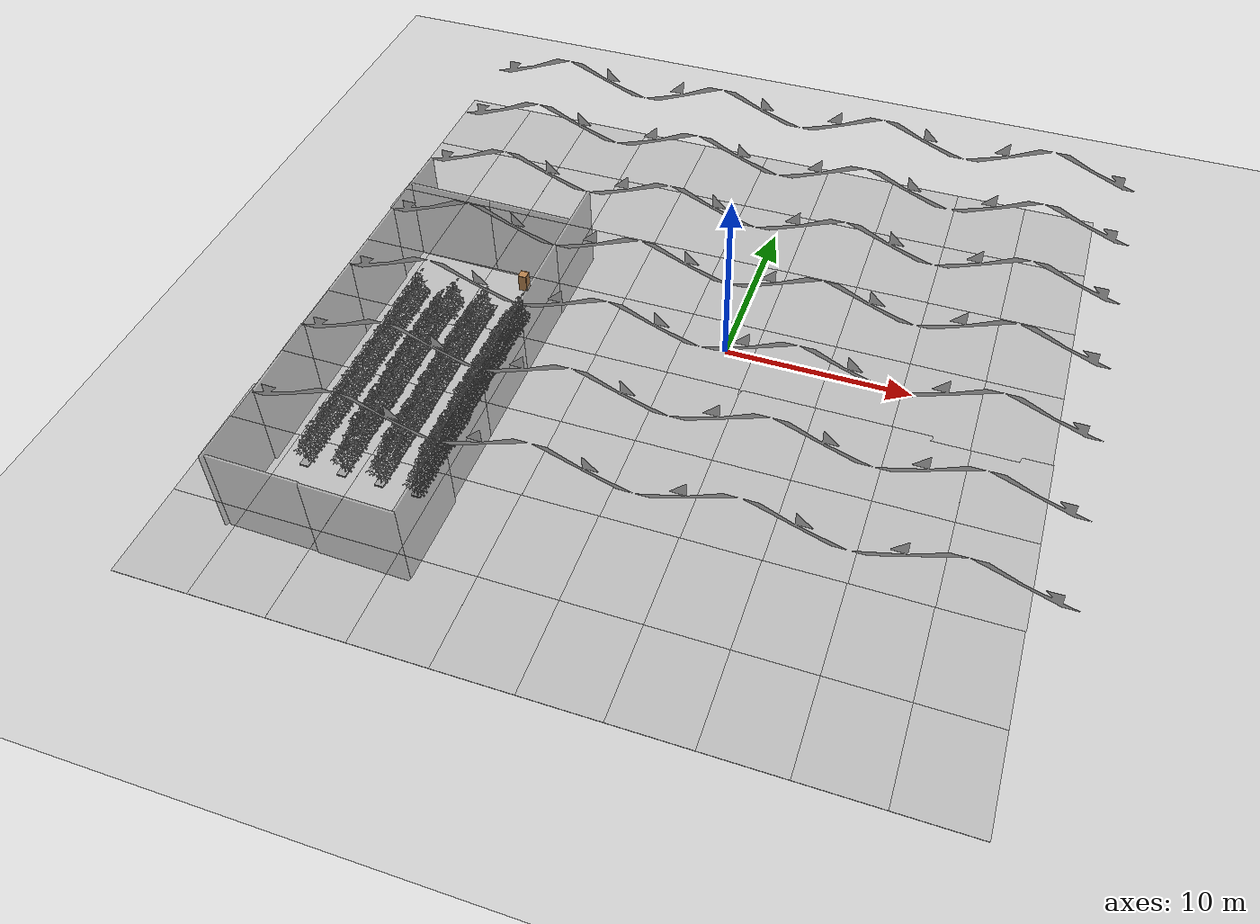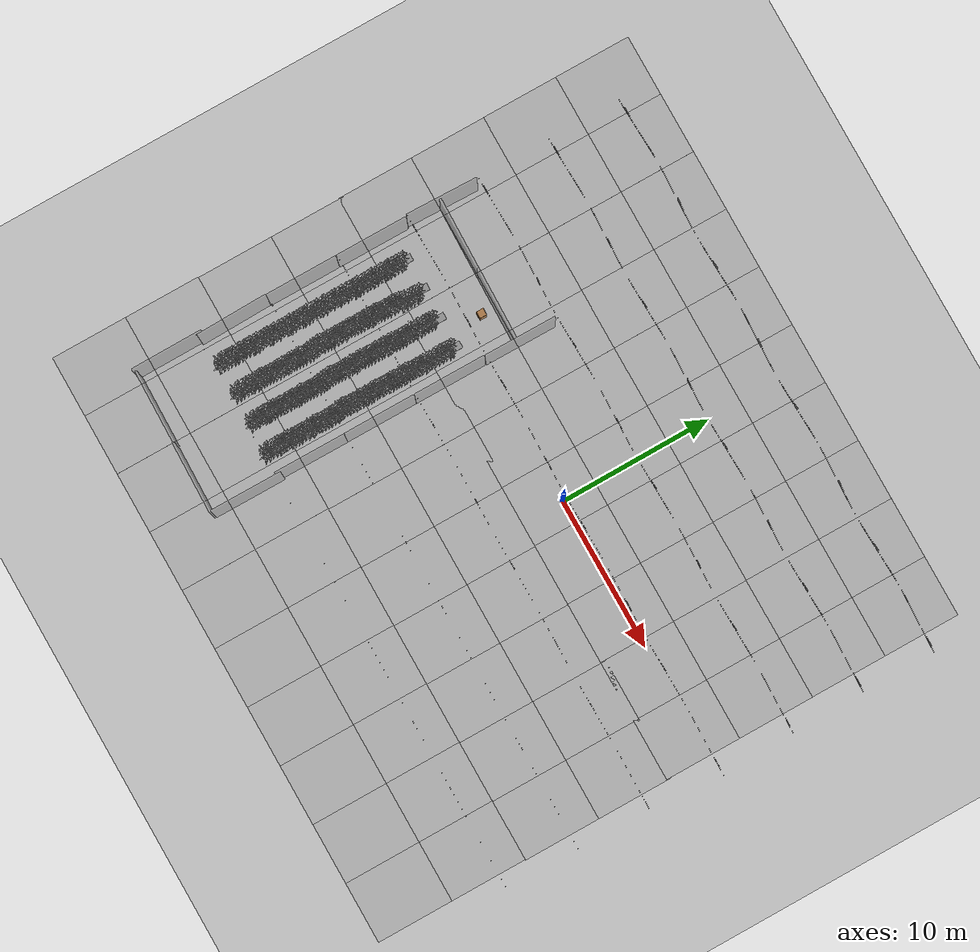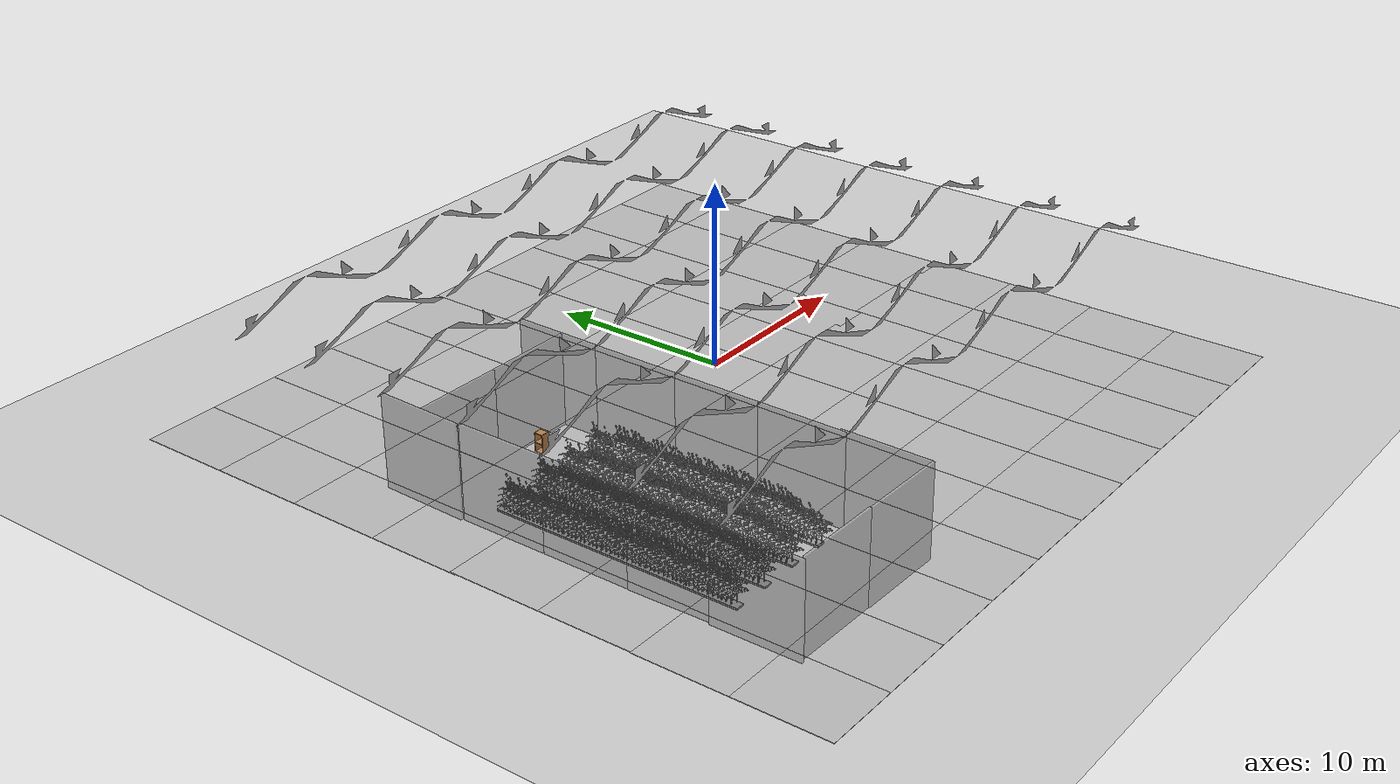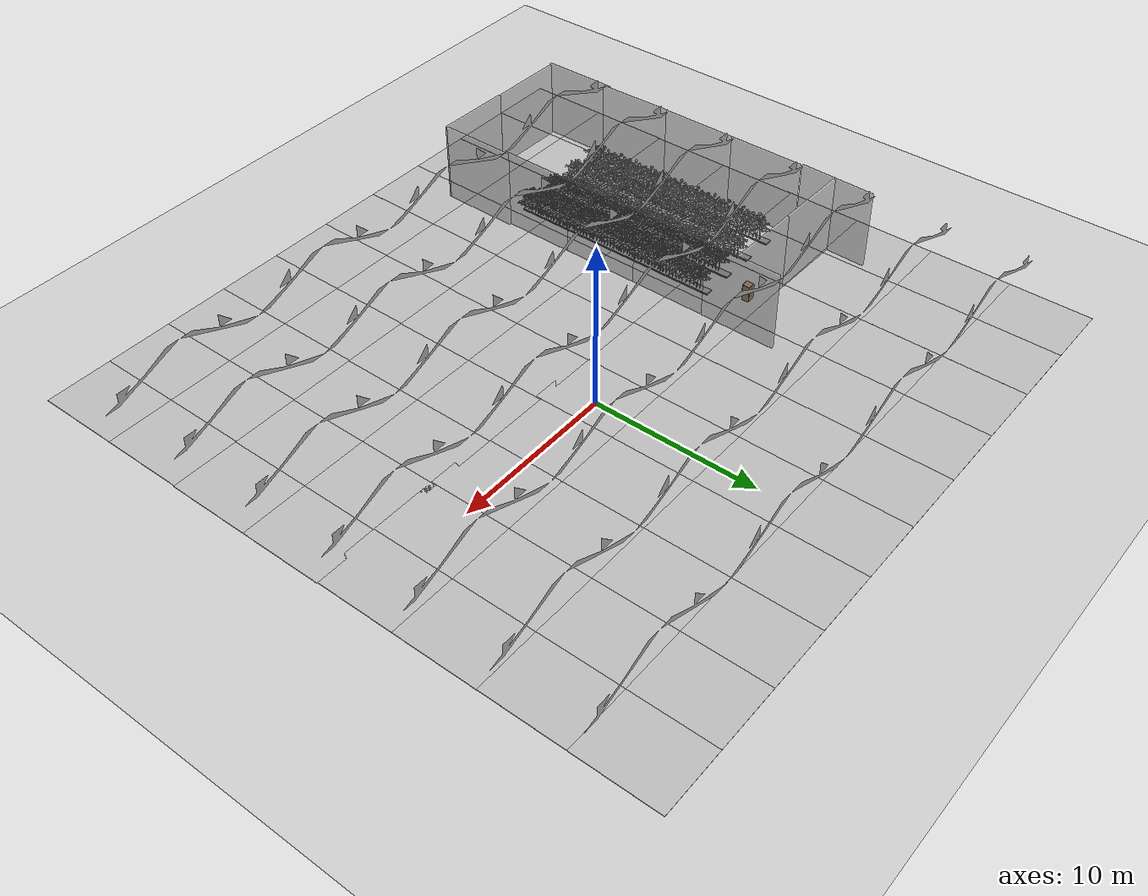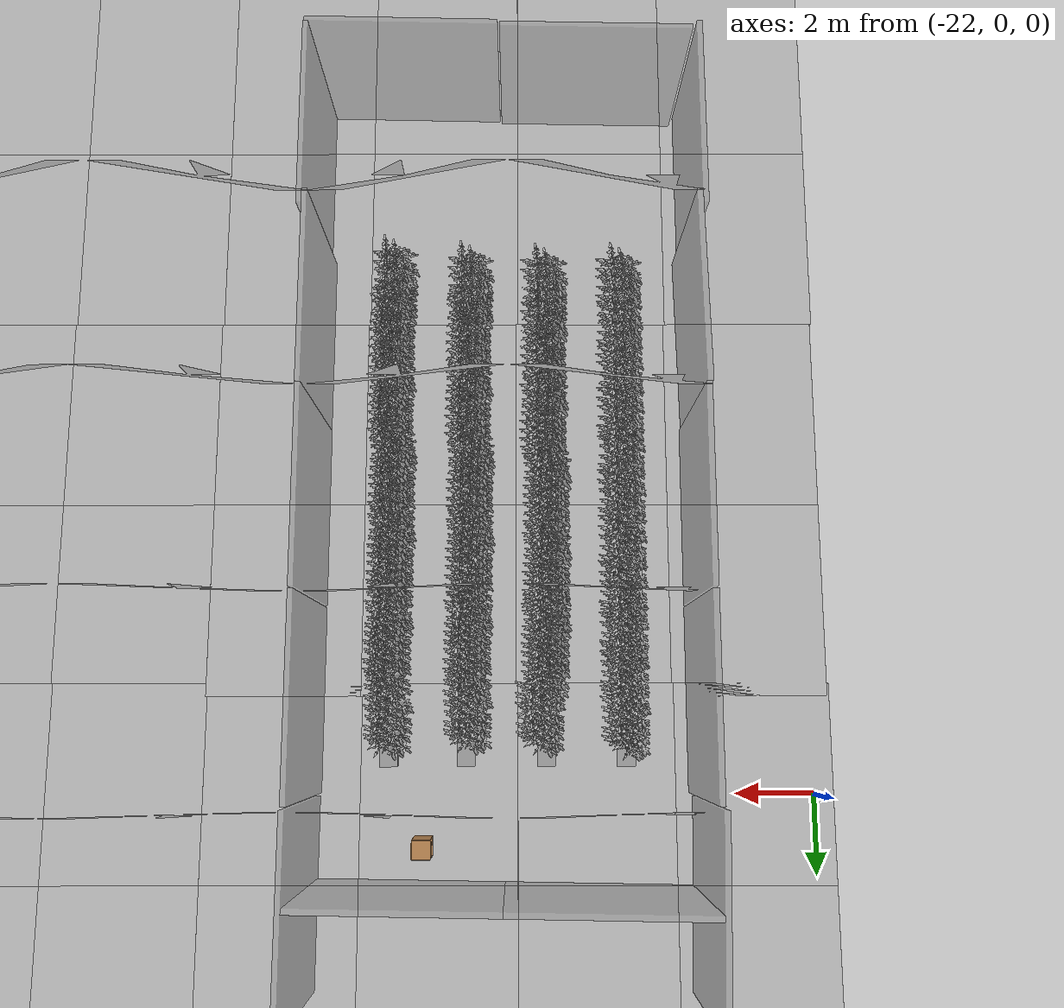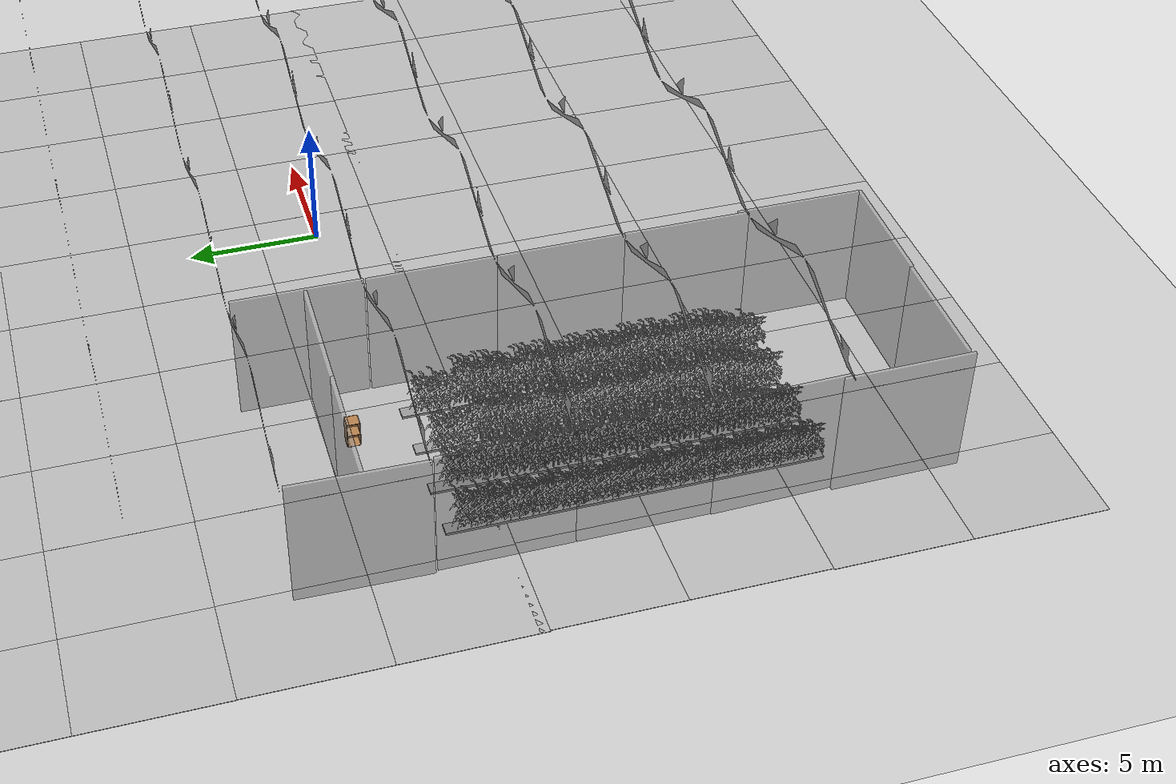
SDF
<sdf version="1.6">
 <world name="default">
  <light name="sun" type="directional">
   <pose>0 0 10 0 -0 0</pose>
   <diffuse>0.8 0.8 0.8 1</diffuse>
   <specular>0.2 0.2 0.2 1</specular>
   <attenuation>
    <range>1000</range>
    <constant>0.9</constant>
    <linear>0.01</linear>
    <quadratic>0.001</quadratic>
   </attenuation>
   <direction>-0.5 0.1 -0.9</direction>
  </light>
  <model name="ground_plane">
   <static>1</static>
   <link name="link">
    <collision name="collision">
     <geometry><plane><normal>0 0 1</normal><size>100 100</size></plane></geometry>
     <surface>
      <contact><collide_bitmask>65535</collide_bitmask></contact>
      <friction><ode><mu>100</mu><mu2>50</mu2></ode></friction>
     </surface>
    </collision>
    <visual name="visual">
     <cast_shadows>0</cast_shadows>
     <geometry><plane><normal>0 0 1</normal><size>100 100</size></plane></geometry>
     <material>
      <script><uri>file://media/materials/scripts/gazebo.material</uri><name>Gazebo/Grey</name></script>
     </material>
    </visual>
   </link>
  </model>
  <gravity>0 0 -9.8</gravity>
  <magnetic_field>6e-06 2.3e-05 -4.2e-05</magnetic_field>
  <atmosphere type="adiabatic"/>
  <physics name="default_physics" default="0" type="ode">
   <max_step_size>0.001</max_step_size>
   <real_time_factor>1</real_time_factor>
   <real_time_update_rate>1000</real_time_update_rate>
  </physics>
  <scene><ambient>0.4 0.4 0.4 1</ambient><background>0.7 0.7 0.7 1</background><shadows>1</shadows></scene>
  <audio><device>default</device></audio>
  <spherical_coordinates>
   <surface_model>EARTH_WGS84</surface_model>
   <latitude_deg>0</latitude_deg>
   <longitude_deg>0</longitude_deg>
   <elevation>0</elevation>
   <heading_deg>0</heading_deg>
  </spherical_coordinates>
  <model name="greenhouse">
   <static>1</static>
   <link name="link">
    <collision name="collision">
     <geometry>
      <mesh><scale>0.05 0.05 0.05</scale><uri>model://greenhouse/meshes/greenhouse.dae</uri></mesh>
     </geometry>
    </collision>
    <visual name="visual">
     <geometry>
      <mesh><scale>0.03 0.03 0.03</scale><uri>model://greenhouse/meshes/greenhouse.dae</uri></mesh>
     </geometry>
    </visual>
   </link>
   <pose>-24.6631 -23.579 0 0 -0 0</pose>
  </model>
  <model name="Box_24x15W_0">
   <link name="Wall">
    <pose>0 0 0.1985 0 -0 0</pose>
    <inertial>
     <mass>5</mass>
     <inertia><ixx>0.1022</ixx><iyy>0.2197</iyy><izz>0.1905</izz><ixy>0</ixy><ixz>0</ixz><iyz>0</iyz></inertia>
    </inertial>
    <collision name="Wall_Collision">
     <geometry><box><size>0.470639 13.5 0.091294</size></box></geometry>
    </collision>
    <visual name="Wall_Visual">
     <geometry><box><size>0.470639 13.5 0.091294</size></box></geometry>
     <material>
      <script><uri>file://media/materials/scripts/gazebo.material</uri><name>Gazebo/Grey</name></script>
      <ambient>1 1 1 1</ambient>
     </material>
    </visual>
   </link>
   <static>1</static>
   <pose>-15.231 -7.42579 -0.146343 0 -0 0</pose>
  </model>
  <model name="Box_24x15W">
   <link name="Wall">
    <pose>0 0 0.1985 0 -0 0</pose>
    <inertial>
     <mass>5</mass>
     <inertia><ixx>0.1022</ixx><iyy>0.2197</iyy><izz>0.1905</izz><ixy>0</ixy><ixz>0</ixz><iyz>0</iyz></inertia>
    </inertial>
    <collision name="Wall_Collision">
     <geometry><box><size>0.470639 13.5 0.091294</size></box></geometry>
    </collision>
    <visual name="Wall_Visual">
     <geometry><box><size>0.470639 13.5 0.091294</size></box></geometry>
     <material>
      <script><uri>file://media/materials/scripts/gazebo.material</uri><name>Gazebo/Grey</name></script>
      <ambient>1 1 1 1</ambient>
     </material>
    </visual>
   </link>
   <static>1</static>
   <pose>-17.2564 -7.42472 -0.14031 0 -0 0</pose>
  </model>
  <model name="Box_24x15W_0_clone">
   <link name="Wall">
    <pose>0 0 0.1985 0 -0 0</pose>
    <inertial>
     <mass>5</mass>
     <inertia><ixx>0.1022</ixx><iyy>0.2197</iyy><izz>0.1905</izz><ixy>0</ixy><ixz>0</ixz><iyz>0</iyz></inertia>
    </inertial>
    <collision name="Wall_Collision">
     <geometry><box><size>0.470639 13.5 0.091294</size></box></geometry>
    </collision>
    <visual name="Wall_Visual">
     <geometry><box><size>0.470639 13.5 0.091294</size></box></geometry>
     <material>
      <script><uri>file://media/materials/scripts/gazebo.material</uri><name>Gazebo/Grey</name></script>
      <ambient>1 1 1 1</ambient>
     </material>
    </visual>
   </link>
   <static>1</static>
   <pose>-13.1875 -7.42472 -0.140264 0 -0 0</pose>
  </model>
  <model name="Front_Plant_1">
   <model name="tomato_plant_medium">
    <static>1</static>
    <link name="link">
     <collision name="collision">
      <pose>0 0 0 1.5708 -0 0</pose>
      <geometry><mesh><scale>0.5 0.5 0.5</scale><uri>model://stick/meshes/stick.dae</uri></mesh></geometry>
     </collision>
     <visual name="visual">
      <geometry>
       <mesh><scale>5e-06 5e-06 6e-06</scale><uri>model://tomato_plant_medium/meshes/tomato-plant.dae</uri></mesh>
      </geometry>
     </visual>
    </link>
    <pose>0.087453 -0.595994 0.012396 0 -0 0</pose>
   </model>
   <model name="tomato_plant_medium_0">
    <static>1</static>
    <link name="link">
     <collision name="collision">
      <pose>0 0 0 1.5708 -0 0</pose>
      <geometry><mesh><scale>0.5 0.5 0.5</scale><uri>model://stick/meshes/stick.dae</uri></mesh></geometry>
     </collision>
     <visual name="visual">
      <geometry>
       <mesh><scale>5e-06 5e-06 6e-06</scale><uri>model://tomato_plant_medium/meshes/tomato-plant.dae</uri></mesh>
      </geometry>
     </visual>
    </link>
    <pose>-0.086166 -0.251822 0.012396 0 -0 0</pose>
   </model>
   <model name="tomato_plant_medium_1">
    <static>1</static>
    <link name="link">
     <collision name="collision">
      <pose>0 0 0 1.5708 -0 0</pose>
      <geometry><mesh><scale>0.5 0.5 0.5</scale><uri>model://stick/meshes/stick.dae</uri></mesh></geometry>
     </collision>
     <visual name="visual">
      <geometry>
       <mesh><scale>5e-06 5e-06 6e-06</scale><uri>model://tomato_plant_medium/meshes/tomato-plant.dae</uri></mesh>
      </geometry>
     </visual>
    </link>
    <pose>0.080199 0.118127 0.012396 0 -0 0</pose>
   </model>
   <model name="tomato_plant_small">
    <static>1</static>
    <link name="link">
     <collision name="collision">
      <pose>0 0 0 1.5708 -0 0</pose>
      <geometry><mesh><scale>0.5 0.45 0.5</scale><uri>model://stick/meshes/stick.dae</uri></mesh></geometry>
     </collision>
     <visual name="visual">
      <geometry>
       <mesh><scale>5e-06 5e-06 5e-06</scale><uri>model://tomato_plant_small/meshes/tomato-plant.dae</uri></mesh>
      </geometry>
     </visual>
    </link>
    <pose>0.099683 -1.12011 0.012396 0 -0 0</pose>
   </model>
   <model name="tomato_plant_small_0">
    <static>1</static>
    <link name="link">
     <collision name="collision">
      <pose>0 0 0 1.5708 -0 0</pose>
      <geometry><mesh><scale>0.5 0.45 0.5</scale><uri>model://stick/meshes/stick.dae</uri></mesh></geometry>
     </collision>
     <visual name="visual">
      <geometry>
       <mesh><scale>5e-06 5e-06 5e-06</scale><uri>model://tomato_plant_small/meshes/tomato-plant.dae</uri></mesh>
      </geometry>
     </visual>
    </link>
    <pose>-0.138771 -0.983982 0.012396 0 -0 0</pose>
   </model>
   <model name="tomato_plant_small_1">
    <static>1</static>
    <link name="link">
     <collision name="collision">
      <pose>0 0 0 1.5708 -0 0</pose>
      <geometry><mesh><scale>0.5 0.45 0.5</scale><uri>model://stick/meshes/stick.dae</uri></mesh></geometry>
     </collision>
     <visual name="visual">
      <geometry>
       <mesh><scale>5e-06 5e-06 5e-06</scale><uri>model://tomato_plant_small/meshes/tomato-plant.dae</uri></mesh>
      </geometry>
     </visual>
    </link>
    <pose>0.101334 -0.848814 0.012396 0 -0 0</pose>
   </model>
   <model name="tomato_plant_small_2">
    <static>1</static>
    <link name="link">
     <collision name="collision">
      <pose>0 0 0 1.5708 -0 0</pose>
      <geometry><mesh><scale>0.5 0.45 0.5</scale><uri>model://stick/meshes/stick.dae</uri></mesh></geometry>
     </collision>
     <visual name="visual">
      <geometry>
       <mesh><scale>5e-06 5e-06 5e-06</scale><uri>model://tomato_plant_small/meshes/tomato-plant.dae</uri></mesh>
      </geometry>
     </visual>
    </link>
    <pose>-0.103369 -0.683189 0.012396 0 -0 0</pose>
   </model>
   <model name="tomato_plant_small_3">
    <static>1</static>
    <link name="link">
     <collision name="collision">
      <pose>0 0 0 1.5708 -0 0</pose>
      <geometry><mesh><scale>0.5 0.45 0.5</scale><uri>model://stick/meshes/stick.dae</uri></mesh></geometry>
     </collision>
     <visual name="visual">
      <geometry>
       <mesh><scale>5e-06 5e-06 5e-06</scale><uri>model://tomato_plant_small/meshes/tomato-plant.dae</uri></mesh>
      </geometry>
     </visual>
    </link>
    <pose>-0.104381 -0.464811 0.012396 0 -0 0</pose>
   </model>
   <model name="tomato_plant_small_4">
    <static>1</static>
    <link name="link">
     <collision name="collision">
      <pose>0 0 0 1.5708 -0 0</pose>
      <geometry><mesh><scale>0.5 0.45 0.5</scale><uri>model://stick/meshes/stick.dae</uri></mesh></geometry>
     </collision>
     <visual name="visual">
      <geometry>
       <mesh><scale>5e-06 5e-06 5e-06</scale><uri>model://tomato_plant_small/meshes/tomato-plant.dae</uri></mesh>
      </geometry>
     </visual>
    </link>
    <pose>0.055604 -0.336879 0.012396 0 -0 0</pose>
   </model>
   <model name="tomato_plant_small_5">
    <static>1</static>
    <link name="link">
     <collision name="collision">
      <pose>0 0 0 1.5708 -0 0</pose>
      <geometry><mesh><scale>0.5 0.45 0.5</scale><uri>model://stick/meshes/stick.dae</uri></mesh></geometry>
     </collision>
     <visual name="visual">
      <geometry>
       <mesh><scale>5e-06 5e-06 5e-06</scale><uri>model://tomato_plant_small/meshes/tomato-plant.dae</uri></mesh>
      </geometry>
     </visual>
    </link>
    <pose>0.085059 -0.092572 0.012396 0 -0 0</pose>
   </model>
   <model name="tomato_plant_small_6">
    <static>1</static>
    <link name="link">
     <collision name="collision">
      <pose>0 0 0 1.5708 -0 0</pose>
      <geometry><mesh><scale>0.5 0.45 0.5</scale><uri>model://stick/meshes/stick.dae</uri></mesh></geometry>
     </collision>
     <visual name="visual">
      <geometry>
       <mesh><scale>5e-06 5e-06 5e-06</scale><uri>model://tomato_plant_small/meshes/tomato-plant.dae</uri></mesh>
      </geometry>
     </visual>
    </link>
    <pose>-0.096345 0.008888 0.012396 0 -0 0</pose>
   </model>
   <static>0</static>
   <pose>-17.2096 -12.8039 0 0 -0 0</pose>
  </model>
  <model name="Front_Plant_1_0">
   <model name="tomato_plant_medium">
    <static>1</static>
    <link name="link">
     <collision name="collision">
      <pose>0 0 0 1.5708 -0 0</pose>
      <geometry><mesh><scale>0.5 0.5 0.5</scale><uri>model://stick/meshes/stick.dae</uri></mesh></geometry>
     </collision>
     <visual name="visual">
      <geometry>
       <mesh><scale>5e-06 5e-06 6e-06</scale><uri>model://tomato_plant_medium/meshes/tomato-plant.dae</uri></mesh>
      </geometry>
     </visual>
    </link>
    <pose>0.087453 -0.595994 0.012396 0 -0 0</pose>
   </model>
   <model name="tomato_plant_medium_0">
    <static>1</static>
    <link name="link">
     <collision name="collision">
      <pose>0 0 0 1.5708 -0 0</pose>
      <geometry><mesh><scale>0.5 0.5 0.5</scale><uri>model://stick/meshes/stick.dae</uri></mesh></geometry>
     </collision>
     <visual name="visual">
      <geometry>
       <mesh><scale>5e-06 5e-06 6e-06</scale><uri>model://tomato_plant_medium/meshes/tomato-plant.dae</uri></mesh>
      </geometry>
     </visual>
    </link>
    <pose>-0.086166 -0.251822 0.012396 0 -0 0</pose>
   </model>
   <model name="tomato_plant_medium_1">
    <static>1</static>
    <link name="link">
     <collision name="collision">
      <pose>0 0 0 1.5708 -0 0</pose>
      <geometry><mesh><scale>0.5 0.5 0.5</scale><uri>model://stick/meshes/stick.dae</uri></mesh></geometry>
     </collision>
     <visual name="visual">
      <geometry>
       <mesh><scale>5e-06 5e-06 6e-06</scale><uri>model://tomato_plant_medium/meshes/tomato-plant.dae</uri></mesh>
      </geometry>
     </visual>
    </link>
    <pose>0.080199 0.118127 0.012396 0 -0 0</pose>
   </model>
   <model name="tomato_plant_small">
    <static>1</static>
    <link name="link">
     <collision name="collision">
      <pose>0 0 0 1.5708 -0 0</pose>
      <geometry><mesh><scale>0.5 0.45 0.5</scale><uri>model://stick/meshes/stick.dae</uri></mesh></geometry>
     </collision>
     <visual name="visual">
      <geometry>
       <mesh><scale>5e-06 5e-06 5e-06</scale><uri>model://tomato_plant_small/meshes/tomato-plant.dae</uri></mesh>
      </geometry>
     </visual>
    </link>
    <pose>0.099683 -1.12011 0.012396 0 -0 0</pose>
   </model>
   <model name="tomato_plant_small_0">
    <static>1</static>
    <link name="link">
     <collision name="collision">
      <pose>0 0 0 1.5708 -0 0</pose>
      <geometry><mesh><scale>0.5 0.45 0.5</scale><uri>model://stick/meshes/stick.dae</uri></mesh></geometry>
     </collision>
     <visual name="visual">
      <geometry>
       <mesh><scale>5e-06 5e-06 5e-06</scale><uri>model://tomato_plant_small/meshes/tomato-plant.dae</uri></mesh>
      </geometry>
     </visual>
    </link>
    <pose>-0.138771 -0.983982 0.012396 0 -0 0</pose>
   </model>
   <model name="tomato_plant_small_1">
    <static>1</static>
    <link name="link">
     <collision name="collision">
      <pose>0 0 0 1.5708 -0 0</pose>
      <geometry><mesh><scale>0.5 0.45 0.5</scale><uri>model://stick/meshes/stick.dae</uri></mesh></geometry>
     </collision>
     <visual name="visual">
      <geometry>
       <mesh><scale>5e-06 5e-06 5e-06</scale><uri>model://tomato_plant_small/meshes/tomato-plant.dae</uri></mesh>
      </geometry>
     </visual>
    </link>
    <pose>0.101334 -0.848814 0.012396 0 -0 0</pose>
   </model>
   <model name="tomato_plant_small_2">
    <static>1</static>
    <link name="link">
     <collision name="collision">
      <pose>0 0 0 1.5708 -0 0</pose>
      <geometry><mesh><scale>0.5 0.45 0.5</scale><uri>model://stick/meshes/stick.dae</uri></mesh></geometry>
     </collision>
     <visual name="visual">
      <geometry>
       <mesh><scale>5e-06 5e-06 5e-06</scale><uri>model://tomato_plant_small/meshes/tomato-plant.dae</uri></mesh>
      </geometry>
     </visual>
    </link>
    <pose>-0.103369 -0.683189 0.012396 0 -0 0</pose>
   </model>
   <model name="tomato_plant_small_3">
    <static>1</static>
    <link name="link">
     <collision name="collision">
      <pose>0 0 0 1.5708 -0 0</pose>
      <geometry><mesh><scale>0.5 0.45 0.5</scale><uri>model://stick/meshes/stick.dae</uri></mesh></geometry>
     </collision>
     <visual name="visual">
      <geometry>
       <mesh><scale>5e-06 5e-06 5e-06</scale><uri>model://tomato_plant_small/meshes/tomato-plant.dae</uri></mesh>
      </geometry>
     </visual>
    </link>
    <pose>-0.104381 -0.464811 0.012396 0 -0 0</pose>
   </model>
   <model name="tomato_plant_small_4">
    <static>1</static>
    <link name="link">
     <collision name="collision">
      <pose>0 0 0 1.5708 -0 0</pose>
      <geometry><mesh><scale>0.5 0.45 0.5</scale><uri>model://stick/meshes/stick.dae</uri></mesh></geometry>
     </collision>
     <visual name="visual">
      <geometry>
       <mesh><scale>5e-06 5e-06 5e-06</scale><uri>model://tomato_plant_small/meshes/tomato-plant.dae</uri></mesh>
      </geometry>
     </visual>
    </link>
    <pose>0.055604 -0.336879 0.012396 0 -0 0</pose>
   </model>
   <model name="tomato_plant_small_5">
    <static>1</static>
    <link name="link">
     <collision name="collision">
      <pose>0 0 0 1.5708 -0 0</pose>
      <geometry><mesh><scale>0.5 0.45 0.5</scale><uri>model://stick/meshes/stick.dae</uri></mesh></geometry>
     </collision>
     <visual name="visual">
      <geometry>
       <mesh><scale>5e-06 5e-06 5e-06</scale><uri>model://tomato_plant_small/meshes/tomato-plant.dae</uri></mesh>
      </geometry>
     </visual>
    </link>
    <pose>0.085059 -0.092572 0.012396 0 -0 0</pose>
   </model>
   <model name="tomato_plant_small_6">
    <static>1</static>
    <link name="link">
     <collision name="collision">
      <pose>0 0 0 1.5708 -0 0</pose>
      <geometry><mesh><scale>0.5 0.45 0.5</scale><uri>model://stick/meshes/stick.dae</uri></mesh></geometry>
     </collision>
     <visual name="visual">
      <geometry>
       <mesh><scale>5e-06 5e-06 5e-06</scale><uri>model://tomato_plant_small/meshes/tomato-plant.dae</uri></mesh>
      </geometry>
     </visual>
    </link>
    <pose>-0.096345 0.008888 0.012396 0 -0 0</pose>
   </model>
   <static>0</static>
   <pose>-13.2256 -12.8592 0 0 -0 0</pose>
  </model>
  <model name="Front_Plant_1_1">
   <model name="tomato_plant_medium">
    <static>1</static>
    <link name="link">
     <collision name="collision">
      <pose>0 0 0 1.5708 -0 0</pose>
      <geometry><mesh><scale>0.5 0.5 0.5</scale><uri>model://stick/meshes/stick.dae</uri></mesh></geometry>
     </collision>
     <visual name="visual">
      <geometry>
       <mesh><scale>5e-06 5e-06 6e-06</scale><uri>model://tomato_plant_medium/meshes/tomato-plant.dae</uri></mesh>
      </geometry>
     </visual>
    </link>
    <pose>0.087453 -0.595994 0.012396 0 -0 0</pose>
   </model>
   <model name="tomato_plant_medium_0">
    <static>1</static>
    <link name="link">
     <collision name="collision">
      <pose>0 0 0 1.5708 -0 0</pose>
      <geometry><mesh><scale>0.5 0.5 0.5</scale><uri>model://stick/meshes/stick.dae</uri></mesh></geometry>
     </collision>
     <visual name="visual">
      <geometry>
       <mesh><scale>5e-06 5e-06 6e-06</scale><uri>model://tomato_plant_medium/meshes/tomato-plant.dae</uri></mesh>
      </geometry>
     </visual>
    </link>
    <pose>-0.086166 -0.251822 0.012396 0 -0 0</pose>
   </model>
   <model name="tomato_plant_medium_1">
    <static>1</static>
    <link name="link">
     <collision name="collision">
      <pose>0 0 0 1.5708 -0 0</pose>
      <geometry><mesh><scale>0.5 0.5 0.5</scale><uri>model://stick/meshes/stick.dae</uri></mesh></geometry>
     </collision>
     <visual name="visual">
      <geometry>
       <mesh><scale>5e-06 5e-06 6e-06</scale><uri>model://tomato_plant_medium/meshes/tomato-plant.dae</uri></mesh>
      </geometry>
     </visual>
    </link>
    <pose>0.080199 0.118127 0.012396 0 -0 0</pose>
   </model>
   <model name="tomato_plant_small">
    <static>1</static>
    <link name="link">
     <collision name="collision">
      <pose>0 0 0 1.5708 -0 0</pose>
      <geometry><mesh><scale>0.5 0.45 0.5</scale><uri>model://stick/meshes/stick.dae</uri></mesh></geometry>
     </collision>
     <visual name="visual">
      <geometry>
       <mesh><scale>5e-06 5e-06 5e-06</scale><uri>model://tomato_plant_small/meshes/tomato-plant.dae</uri></mesh>
      </geometry>
     </visual>
    </link>
    <pose>0.099683 -1.12011 0.012396 0 -0 0</pose>
   </model>
   <model name="tomato_plant_small_0">
    <static>1</static>
    <link name="link">
     <collision name="collision">
      <pose>0 0 0 1.5708 -0 0</pose>
      <geometry><mesh><scale>0.5 0.45 0.5</scale><uri>model://stick/meshes/stick.dae</uri></mesh></geometry>
     </collision>
     <visual name="visual">
      <geometry>
       <mesh><scale>5e-06 5e-06 5e-06</scale><uri>model://tomato_plant_small/meshes/tomato-plant.dae</uri></mesh>
      </geometry>
     </visual>
    </link>
    <pose>-0.138771 -0.983982 0.012396 0 -0 0</pose>
   </model>
   <model name="tomato_plant_small_1">
    <static>1</static>
    <link name="link">
     <collision name="collision">
      <pose>0 0 0 1.5708 -0 0</pose>
      <geometry><mesh><scale>0.5 0.45 0.5</scale><uri>model://stick/meshes/stick.dae</uri></mesh></geometry>
     </collision>
     <visual name="visual">
      <geometry>
       <mesh><scale>5e-06 5e-06 5e-06</scale><uri>model://tomato_plant_small/meshes/tomato-plant.dae</uri></mesh>
      </geometry>
     </visual>
    </link>
    <pose>0.101334 -0.848814 0.012396 0 -0 0</pose>
   </model>
   <model name="tomato_plant_small_2">
    <static>1</static>
    <link name="link">
     <collision name="collision">
      <pose>0 0 0 1.5708 -0 0</pose>
      <geometry><mesh><scale>0.5 0.45 0.5</scale><uri>model://stick/meshes/stick.dae</uri></mesh></geometry>
     </collision>
     <visual name="visual">
      <geometry>
       <mesh><scale>5e-06 5e-06 5e-06</scale><uri>model://tomato_plant_small/meshes/tomato-plant.dae</uri></mesh>
      </geometry>
     </visual>
    </link>
    <pose>-0.103369 -0.683189 0.012396 0 -0 0</pose>
   </model>
   <model name="tomato_plant_small_3">
    <static>1</static>
    <link name="link">
     <collision name="collision">
      <pose>0 0 0 1.5708 -0 0</pose>
      <geometry><mesh><scale>0.5 0.45 0.5</scale><uri>model://stick/meshes/stick.dae</uri></mesh></geometry>
     </collision>
     <visual name="visual">
      <geometry>
       <mesh><scale>5e-06 5e-06 5e-06</scale><uri>model://tomato_plant_small/meshes/tomato-plant.dae</uri></mesh>
      </geometry>
     </visual>
    </link>
    <pose>-0.104381 -0.464811 0.012396 0 -0 0</pose>
   </model>
   <model name="tomato_plant_small_4">
    <static>1</static>
    <link name="link">
     <collision name="collision">
      <pose>0 0 0 1.5708 -0 0</pose>
      <geometry><mesh><scale>0.5 0.45 0.5</scale><uri>model://stick/meshes/stick.dae</uri></mesh></geometry>
     </collision>
     <visual name="visual">
      <geometry>
       <mesh><scale>5e-06 5e-06 5e-06</scale><uri>model://tomato_plant_small/meshes/tomato-plant.dae</uri></mesh>
      </geometry>
     </visual>
    </link>
    <pose>0.055604 -0.336879 0.012396 0 -0 0</pose>
   </model>
   <model name="tomato_plant_small_5">
    <static>1</static>
    <link name="link">
     <collision name="collision">
      <pose>0 0 0 1.5708 -0 0</pose>
      <geometry><mesh><scale>0.5 0.45 0.5</scale><uri>model://stick/meshes/stick.dae</uri></mesh></geometry>
     </collision>
     <visual name="visual">
      <geometry>
       <mesh><scale>5e-06 5e-06 5e-06</scale><uri>model://tomato_plant_small/meshes/tomato-plant.dae</uri></mesh>
      </geometry>
     </visual>
    </link>
    <pose>0.085059 -0.092572 0.012396 0 -0 0</pose>
   </model>
   <model name="tomato_plant_small_6">
    <static>1</static>
    <link name="link">
     <collision name="collision">
      <pose>0 0 0 1.5708 -0 0</pose>
      <geometry><mesh><scale>0.5 0.45 0.5</scale><uri>model://stick/meshes/stick.dae</uri></mesh></geometry>
     </collision>
     <visual name="visual">
      <geometry>
       <mesh><scale>5e-06 5e-06 5e-06</scale><uri>model://tomato_plant_small/meshes/tomato-plant.dae</uri></mesh>
      </geometry>
     </visual>
    </link>
    <pose>-0.096345 0.008888 0.012396 0 -0 0</pose>
   </model>
   <static>0</static>
   <pose>-17.2096 -11.5451 0 0 -0 0</pose>
  </model>
  <model name="Front_Plant_1_2">
   <model name="tomato_plant_medium">
    <static>1</static>
    <link name="link">
     <collision name="collision">
      <pose>0 0 0 1.5708 -0 0</pose>
      <geometry><mesh><scale>0.5 0.5 0.5</scale><uri>model://stick/meshes/stick.dae</uri></mesh></geometry>
     </collision>
     <visual name="visual">
      <geometry>
       <mesh><scale>5e-06 5e-06 6e-06</scale><uri>model://tomato_plant_medium/meshes/tomato-plant.dae</uri></mesh>
      </geometry>
     </visual>
    </link>
    <pose>0.087453 -0.595994 0.012396 0 -0 0</pose>
   </model>
   <model name="tomato_plant_medium_0">
    <static>1</static>
    <link name="link">
     <collision name="collision">
      <pose>0 0 0 1.5708 -0 0</pose>
      <geometry><mesh><scale>0.5 0.5 0.5</scale><uri>model://stick/meshes/stick.dae</uri></mesh></geometry>
     </collision>
     <visual name="visual">
      <geometry>
       <mesh><scale>5e-06 5e-06 6e-06</scale><uri>model://tomato_plant_medium/meshes/tomato-plant.dae</uri></mesh>
      </geometry>
     </visual>
    </link>
    <pose>-0.086166 -0.251822 0.012396 0 -0 0</pose>
   </model>
   <model name="tomato_plant_medium_1">
    <static>1</static>
    <link name="link">
     <collision name="collision">
      <pose>0 0 0 1.5708 -0 0</pose>
      <geometry><mesh><scale>0.5 0.5 0.5</scale><uri>model://stick/meshes/stick.dae</uri></mesh></geometry>
     </collision>
     <visual name="visual">
      <geometry>
       <mesh><scale>5e-06 5e-06 6e-06</scale><uri>model://tomato_plant_medium/meshes/tomato-plant.dae</uri></mesh>
      </geometry>
     </visual>
    </link>
    <pose>0.080199 0.118127 0.012396 0 -0 0</pose>
   </model>
   <model name="tomato_plant_small">
    <static>1</static>
    <link name="link">
     <collision name="collision">
      <pose>0 0 0 1.5708 -0 0</pose>
      <geometry><mesh><scale>0.5 0.45 0.5</scale><uri>model://stick/meshes/stick.dae</uri></mesh></geometry>
     </collision>
     <visual name="visual">
      <geometry>
       <mesh><scale>5e-06 5e-06 5e-06</scale><uri>model://tomato_plant_small/meshes/tomato-plant.dae</uri></mesh>
      </geometry>
     </visual>
    </link>
    <pose>0.099683 -1.12011 0.012396 0 -0 0</pose>
   </model>
   <model name="tomato_plant_small_0">
    <static>1</static>
    <link name="link">
     <collision name="collision">
      <pose>0 0 0 1.5708 -0 0</pose>
      <geometry><mesh><scale>0.5 0.45 0.5</scale><uri>model://stick/meshes/stick.dae</uri></mesh></geometry>
     </collision>
     <visual name="visual">
      <geometry>
       <mesh><scale>5e-06 5e-06 5e-06</scale><uri>model://tomato_plant_small/meshes/tomato-plant.dae</uri></mesh>
      </geometry>
     </visual>
    </link>
    <pose>-0.138771 -0.983982 0.012396 0 -0 0</pose>
   </model>
   <model name="tomato_plant_small_1">
    <static>1</static>
    <link name="link">
     <collision name="collision">
      <pose>0 0 0 1.5708 -0 0</pose>
      <geometry><mesh><scale>0.5 0.45 0.5</scale><uri>model://stick/meshes/stick.dae</uri></mesh></geometry>
     </collision>
     <visual name="visual">
      <geometry>
       <mesh><scale>5e-06 5e-06 5e-06</scale><uri>model://tomato_plant_small/meshes/tomato-plant.dae</uri></mesh>
      </geometry>
     </visual>
    </link>
    <pose>0.101334 -0.848814 0.012396 0 -0 0</pose>
   </model>
   <model name="tomato_plant_small_2">
    <static>1</static>
    <link name="link">
     <collision name="collision">
      <pose>0 0 0 1.5708 -0 0</pose>
      <geometry><mesh><scale>0.5 0.45 0.5</scale><uri>model://stick/meshes/stick.dae</uri></mesh></geometry>
     </collision>
     <visual name="visual">
      <geometry>
       <mesh><scale>5e-06 5e-06 5e-06</scale><uri>model://tomato_plant_small/meshes/tomato-plant.dae</uri></mesh>
      </geometry>
     </visual>
    </link>
    <pose>-0.103369 -0.683189 0.012396 0 -0 0</pose>
   </model>
   <model name="tomato_plant_small_3">
    <static>1</static>
    <link name="link">
     <collision name="collision">
      <pose>0 0 0 1.5708 -0 0</pose>
      <geometry><mesh><scale>0.5 0.45 0.5</scale><uri>model://stick/meshes/stick.dae</uri></mesh></geometry>
     </collision>
     <visual name="visual">
      <geometry>
       <mesh><scale>5e-06 5e-06 5e-06</scale><uri>model://tomato_plant_small/meshes/tomato-plant.dae</uri></mesh>
      </geometry>
     </visual>
    </link>
    <pose>-0.104381 -0.464811 0.012396 0 -0 0</pose>
   </model>
   <model name="tomato_plant_small_4">
    <static>1</static>
    <link name="link">
     <collision name="collision">
      <pose>0 0 0 1.5708 -0 0</pose>
      <geometry><mesh><scale>0.5 0.45 0.5</scale><uri>model://stick/meshes/stick.dae</uri></mesh></geometry>
     </collision>
     <visual name="visual">
      <geometry>
       <mesh><scale>5e-06 5e-06 5e-06</scale><uri>model://tomato_plant_small/meshes/tomato-plant.dae</uri></mesh>
      </geometry>
     </visual>
    </link>
    <pose>0.055604 -0.336879 0.012396 0 -0 0</pose>
   </model>
   <model name="tomato_plant_small_5">
    <static>1</static>
    <link name="link">
     <collision name="collision">
      <pose>0 0 0 1.5708 -0 0</pose>
      <geometry><mesh><scale>0.5 0.45 0.5</scale><uri>model://stick/meshes/stick.dae</uri></mesh></geometry>
     </collision>
     <visual name="visual">
      <geometry>
       <mesh><scale>5e-06 5e-06 5e-06</scale><uri>model://tomato_plant_small/meshes/tomato-plant.dae</uri></mesh>
      </geometry>
     </visual>
    </link>
    <pose>0.085059 -0.092572 0.012396 0 -0 0</pose>
   </model>
   <model name="tomato_plant_small_6">
    <static>1</static>
    <link name="link">
     <collision name="collision">
      <pose>0 0 0 1.5708 -0 0</pose>
      <geometry><mesh><scale>0.5 0.45 0.5</scale><uri>model://stick/meshes/stick.dae</uri></mesh></geometry>
     </collision>
     <visual name="visual">
      <geometry>
       <mesh><scale>5e-06 5e-06 5e-06</scale><uri>model://tomato_plant_small/meshes/tomato-plant.dae</uri></mesh>
      </geometry>
     </visual>
    </link>
    <pose>-0.096345 0.008888 0.012396 0 -0 0</pose>
   </model>
   <static>0</static>
   <pose>-17.2096 -10.4043 0 0 -0 0</pose>
  </model>
  <model name="Front_Plant_1_3">
   <model name="tomato_plant_medium">
    <static>1</static>
    <link name="link">
     <collision name="collision">
      <pose>0 0 0 1.5708 -0 0</pose>
      <geometry><mesh><scale>0.5 0.5 0.5</scale><uri>model://stick/meshes/stick.dae</uri></mesh></geometry>
     </collision>
     <visual name="visual">
      <geometry>
       <mesh><scale>5e-06 5e-06 6e-06</scale><uri>model://tomato_plant_medium/meshes/tomato-plant.dae</uri></mesh>
      </geometry>
     </visual>
    </link>
    <pose>0.087453 -0.595994 0.012396 0 -0 0</pose>
   </model>
   <model name="tomato_plant_medium_0">
    <static>1</static>
    <link name="link">
     <collision name="collision">
      <pose>0 0 0 1.5708 -0 0</pose>
      <geometry><mesh><scale>0.5 0.5 0.5</scale><uri>model://stick/meshes/stick.dae</uri></mesh></geometry>
     </collision>
     <visual name="visual">
      <geometry>
       <mesh><scale>5e-06 5e-06 6e-06</scale><uri>model://tomato_plant_medium/meshes/tomato-plant.dae</uri></mesh>
      </geometry>
     </visual>
    </link>
    <pose>-0.086166 -0.251822 0.012396 0 -0 0</pose>
   </model>
   <model name="tomato_plant_medium_1">
    <static>1</static>
    <link name="link">
     <collision name="collision">
      <pose>0 0 0 1.5708 -0 0</pose>
      <geometry><mesh><scale>0.5 0.5 0.5</scale><uri>model://stick/meshes/stick.dae</uri></mesh></geometry>
     </collision>
     <visual name="visual">
      <geometry>
       <mesh><scale>5e-06 5e-06 6e-06</scale><uri>model://tomato_plant_medium/meshes/tomato-plant.dae</uri></mesh>
      </geometry>
     </visual>
    </link>
    <pose>0.080199 0.118127 0.012396 0 -0 0</pose>
   </model>
   <model name="tomato_plant_small">
    <static>1</static>
    <link name="link">
     <collision name="collision">
      <pose>0 0 0 1.5708 -0 0</pose>
      <geometry><mesh><scale>0.5 0.45 0.5</scale><uri>model://stick/meshes/stick.dae</uri></mesh></geometry>
     </collision>
     <visual name="visual">
      <geometry>
       <mesh><scale>5e-06 5e-06 5e-06</scale><uri>model://tomato_plant_small/meshes/tomato-plant.dae</uri></mesh>
      </geometry>
     </visual>
    </link>
    <pose>0.099683 -1.12011 0.012396 0 -0 0</pose>
   </model>
   <model name="tomato_plant_small_0">
    <static>1</static>
    <link name="link">
     <collision name="collision">
      <pose>0 0 0 1.5708 -0 0</pose>
      <geometry><mesh><scale>0.5 0.45 0.5</scale><uri>model://stick/meshes/stick.dae</uri></mesh></geometry>
     </collision>
     <visual name="visual">
      <geometry>
       <mesh><scale>5e-06 5e-06 5e-06</scale><uri>model://tomato_plant_small/meshes/tomato-plant.dae</uri></mesh>
      </geometry>
     </visual>
    </link>
    <pose>-0.138771 -0.983982 0.012396 0 -0 0</pose>
   </model>
   <model name="tomato_plant_small_1">
    <static>1</static>
    <link name="link">
     <collision name="collision">
      <pose>0 0 0 1.5708 -0 0</pose>
      <geometry><mesh><scale>0.5 0.45 0.5</scale><uri>model://stick/meshes/stick.dae</uri></mesh></geometry>
     </collision>
     <visual name="visual">
      <geometry>
       <mesh><scale>5e-06 5e-06 5e-06</scale><uri>model://tomato_plant_small/meshes/tomato-plant.dae</uri></mesh>
      </geometry>
     </visual>
    </link>
    <pose>0.101334 -0.848814 0.012396 0 -0 0</pose>
   </model>
   <model name="tomato_plant_small_2">
    <static>1</static>
    <link name="link">
     <collision name="collision">
      <pose>0 0 0 1.5708 -0 0</pose>
      <geometry><mesh><scale>0.5 0.45 0.5</scale><uri>model://stick/meshes/stick.dae</uri></mesh></geometry>
     </collision>
     <visual name="visual">
      <geometry>
       <mesh><scale>5e-06 5e-06 5e-06</scale><uri>model://tomato_plant_small/meshes/tomato-plant.dae</uri></mesh>
      </geometry>
     </visual>
    </link>
    <pose>-0.103369 -0.683189 0.012396 0 -0 0</pose>
   </model>
   <model name="tomato_plant_small_3">
    <static>1</static>
    <link name="link">
     <collision name="collision">
      <pose>0 0 0 1.5708 -0 0</pose>
      <geometry><mesh><scale>0.5 0.45 0.5</scale><uri>model://stick/meshes/stick.dae</uri></mesh></geometry>
     </collision>
     <visual name="visual">
      <geometry>
       <mesh><scale>5e-06 5e-06 5e-06</scale><uri>model://tomato_plant_small/meshes/tomato-plant.dae</uri></mesh>
      </geometry>
     </visual>
    </link>
    <pose>-0.104381 -0.464811 0.012396 0 -0 0</pose>
   </model>
   <model name="tomato_plant_small_4">
    <static>1</static>
    <link name="link">
     <collision name="collision">
      <pose>0 0 0 1.5708 -0 0</pose>
      <geometry><mesh><scale>0.5 0.45 0.5</scale><uri>model://stick/meshes/stick.dae</uri></mesh></geometry>
     </collision>
     <visual name="visual">
      <geometry>
       <mesh><scale>5e-06 5e-06 5e-06</scale><uri>model://tomato_plant_small/meshes/tomato-plant.dae</uri></mesh>
      </geometry>
     </visual>
    </link>
    <pose>0.055604 -0.336879 0.012396 0 -0 0</pose>
   </model>
   <model name="tomato_plant_small_5">
    <static>1</static>
    <link name="link">
     <collision name="collision">
      <pose>0 0 0 1.5708 -0 0</pose>
      <geometry><mesh><scale>0.5 0.45 0.5</scale><uri>model://stick/meshes/stick.dae</uri></mesh></geometry>
     </collision>
     <visual name="visual">
      <geometry>
       <mesh><scale>5e-06 5e-06 5e-06</scale><uri>model://tomato_plant_small/meshes/tomato-plant.dae</uri></mesh>
      </geometry>
     </visual>
    </link>
    <pose>0.085059 -0.092572 0.012396 0 -0 0</pose>
   </model>
   <model name="tomato_plant_small_6">
    <static>1</static>
    <link name="link">
     <collision name="collision">
      <pose>0 0 0 1.5708 -0 0</pose>
      <geometry><mesh><scale>0.5 0.45 0.5</scale><uri>model://stick/meshes/stick.dae</uri></mesh></geometry>
     </collision>
     <visual name="visual">
      <geometry>
       <mesh><scale>5e-06 5e-06 5e-06</scale><uri>model://tomato_plant_small/meshes/tomato-plant.dae</uri></mesh>
      </geometry>
     </visual>
    </link>
    <pose>-0.096345 0.008888 0.012396 0 -0 0</pose>
   </model>
   <static>0</static>
   <pose>-17.2096 -9.20246 0 0 -0 0</pose>
  </model>
  <model name="Front_Plant_1_4">
   <model name="tomato_plant_medium">
    <static>1</static>
    <link name="link">
     <collision name="collision">
      <pose>0 0 0 1.5708 -0 0</pose>
      <geometry><mesh><scale>0.5 0.5 0.5</scale><uri>model://stick/meshes/stick.dae</uri></mesh></geometry>
     </collision>
     <visual name="visual">
      <geometry>
       <mesh><scale>5e-06 5e-06 6e-06</scale><uri>model://tomato_plant_medium/meshes/tomato-plant.dae</uri></mesh>
      </geometry>
     </visual>
    </link>
    <pose>0.087453 -0.595994 0.012396 0 -0 0</pose>
   </model>
   <model name="tomato_plant_medium_0">
    <static>1</static>
    <link name="link">
     <collision name="collision">
      <pose>0 0 0 1.5708 -0 0</pose>
      <geometry><mesh><scale>0.5 0.5 0.5</scale><uri>model://stick/meshes/stick.dae</uri></mesh></geometry>
     </collision>
     <visual name="visual">
      <geometry>
       <mesh><scale>5e-06 5e-06 6e-06</scale><uri>model://tomato_plant_medium/meshes/tomato-plant.dae</uri></mesh>
      </geometry>
     </visual>
    </link>
    <pose>-0.086166 -0.251822 0.012396 0 -0 0</pose>
   </model>
   <model name="tomato_plant_medium_1">
    <static>1</static>
    <link name="link">
     <collision name="collision">
      <pose>0 0 0 1.5708 -0 0</pose>
      <geometry><mesh><scale>0.5 0.5 0.5</scale><uri>model://stick/meshes/stick.dae</uri></mesh></geometry>
     </collision>
     <visual name="visual">
      <geometry>
       <mesh><scale>5e-06 5e-06 6e-06</scale><uri>model://tomato_plant_medium/meshes/tomato-plant.dae</uri></mesh>
      </geometry>
     </visual>
    </link>
    <pose>0.080199 0.118127 0.012396 0 -0 0</pose>
   </model>
   <model name="tomato_plant_small">
    <static>1</static>
    <link name="link">
     <collision name="collision">
      <pose>0 0 0 1.5708 -0 0</pose>
      <geometry><mesh><scale>0.5 0.45 0.5</scale><uri>model://stick/meshes/stick.dae</uri></mesh></geometry>
     </collision>
     <visual name="visual">
      <geometry>
       <mesh><scale>5e-06 5e-06 5e-06</scale><uri>model://tomato_plant_small/meshes/tomato-plant.dae</uri></mesh>
      </geometry>
     </visual>
    </link>
    <pose>0.099683 -1.12011 0.012396 0 -0 0</pose>
   </model>
   <model name="tomato_plant_small_0">
    <static>1</static>
    <link name="link">
     <collision name="collision">
      <pose>0 0 0 1.5708 -0 0</pose>
      <geometry><mesh><scale>0.5 0.45 0.5</scale><uri>model://stick/meshes/stick.dae</uri></mesh></geometry>
     </collision>
     <visual name="visual">
      <geometry>
       <mesh><scale>5e-06 5e-06 5e-06</scale><uri>model://tomato_plant_small/meshes/tomato-plant.dae</uri></mesh>
      </geometry>
     </visual>
    </link>
    <pose>-0.138771 -0.983982 0.012396 0 -0 0</pose>
   </model>
   <model name="tomato_plant_small_1">
    <static>1</static>
    <link name="link">
     <collision name="collision">
      <pose>0 0 0 1.5708 -0 0</pose>
      <geometry><mesh><scale>0.5 0.45 0.5</scale><uri>model://stick/meshes/stick.dae</uri></mesh></geometry>
     </collision>
     <visual name="visual">
      <geometry>
       <mesh><scale>5e-06 5e-06 5e-06</scale><uri>model://tomato_plant_small/meshes/tomato-plant.dae</uri></mesh>
      </geometry>
     </visual>
    </link>
    <pose>0.101334 -0.848814 0.012396 0 -0 0</pose>
   </model>
   <model name="tomato_plant_small_2">
    <static>1</static>
    <link name="link">
     <collision name="collision">
      <pose>0 0 0 1.5708 -0 0</pose>
      <geometry><mesh><scale>0.5 0.45 0.5</scale><uri>model://stick/meshes/stick.dae</uri></mesh></geometry>
     </collision>
     <visual name="visual">
      <geometry>
       <mesh><scale>5e-06 5e-06 5e-06</scale><uri>model://tomato_plant_small/meshes/tomato-plant.dae</uri></mesh>
      </geometry>
     </visual>
    </link>
    <pose>-0.103369 -0.683189 0.012396 0 -0 0</pose>
   </model>
   <model name="tomato_plant_small_3">
    <static>1</static>
    <link name="link">
     <collision name="collision">
      <pose>0 0 0 1.5708 -0 0</pose>
      <geometry><mesh><scale>0.5 0.45 0.5</scale><uri>model://stick/meshes/stick.dae</uri></mesh></geometry>
     </collision>
     <visual name="visual">
      <geometry>
       <mesh><scale>5e-06 5e-06 5e-06</scale><uri>model://tomato_plant_small/meshes/tomato-plant.dae</uri></mesh>
      </geometry>
     </visual>
    </link>
    <pose>-0.104381 -0.464811 0.012396 0 -0 0</pose>
   </model>
   <model name="tomato_plant_small_4">
    <static>1</static>
    <link name="link">
     <collision name="collision">
      <pose>0 0 0 1.5708 -0 0</pose>
      <geometry><mesh><scale>0.5 0.45 0.5</scale><uri>model://stick/meshes/stick.dae</uri></mesh></geometry>
     </collision>
     <visual name="visual">
      <geometry>
       <mesh><scale>5e-06 5e-06 5e-06</scale><uri>model://tomato_plant_small/meshes/tomato-plant.dae</uri></mesh>
      </geometry>
     </visual>
    </link>
    <pose>0.055604 -0.336879 0.012396 0 -0 0</pose>
   </model>
   <model name="tomato_plant_small_5">
    <static>1</static>
    <link name="link">
     <collision name="collision">
      <pose>0 0 0 1.5708 -0 0</pose>
      <geometry><mesh><scale>0.5 0.45 0.5</scale><uri>model://stick/meshes/stick.dae</uri></mesh></geometry>
     </collision>
     <visual name="visual">
      <geometry>
       <mesh><scale>5e-06 5e-06 5e-06</scale><uri>model://tomato_plant_small/meshes/tomato-plant.dae</uri></mesh>
      </geometry>
     </visual>
    </link>
    <pose>0.085059 -0.092572 0.012396 0 -0 0</pose>
   </model>
   <model name="tomato_plant_small_6">
    <static>1</static>
    <link name="link">
     <collision name="collision">
      <pose>0 0 0 1.5708 -0 0</pose>
      <geometry><mesh><scale>0.5 0.45 0.5</scale><uri>model://stick/meshes/stick.dae</uri></mesh></geometry>
     </collision>
     <visual name="visual">
      <geometry>
       <mesh><scale>5e-06 5e-06 5e-06</scale><uri>model://tomato_plant_small/meshes/tomato-plant.dae</uri></mesh>
      </geometry>
     </visual>
    </link>
    <pose>-0.096345 0.008888 0.012396 0 -0 0</pose>
   </model>
   <static>0</static>
   <pose>-17.2096 -8.15623 0 0 -0 0</pose>
  </model>
  <model name="Front_Plant_1_5">
   <model name="tomato_plant_medium">
    <static>1</static>
    <link name="link">
     <collision name="collision">
      <pose>0 0 0 1.5708 -0 0</pose>
      <geometry><mesh><scale>0.5 0.5 0.5</scale><uri>model://stick/meshes/stick.dae</uri></mesh></geometry>
     </collision>
     <visual name="visual">
      <geometry>
       <mesh><scale>5e-06 5e-06 6e-06</scale><uri>model://tomato_plant_medium/meshes/tomato-plant.dae</uri></mesh>
      </geometry>
     </visual>
    </link>
    <pose>0.087453 -0.595994 0.012396 0 -0 0</pose>
   </model>
   <model name="tomato_plant_medium_0">
    <static>1</static>
    <link name="link">
     <collision name="collision">
      <pose>0 0 0 1.5708 -0 0</pose>
      <geometry><mesh><scale>0.5 0.5 0.5</scale><uri>model://stick/meshes/stick.dae</uri></mesh></geometry>
     </collision>
     <visual name="visual">
      <geometry>
       <mesh><scale>5e-06 5e-06 6e-06</scale><uri>model://tomato_plant_medium/meshes/tomato-plant.dae</uri></mesh>
      </geometry>
     </visual>
    </link>
    <pose>-0.086166 -0.251822 0.012396 0 -0 0</pose>
   </model>
   <model name="tomato_plant_medium_1">
    <static>1</static>
    <link name="link">
     <collision name="collision">
      <pose>0 0 0 1.5708 -0 0</pose>
      <geometry><mesh><scale>0.5 0.5 0.5</scale><uri>model://stick/meshes/stick.dae</uri></mesh></geometry>
     </collision>
     <visual name="visual">
      <geometry>
       <mesh><scale>5e-06 5e-06 6e-06</scale><uri>model://tomato_plant_medium/meshes/tomato-plant.dae</uri></mesh>
      </geometry>
     </visual>
    </link>
    <pose>0.080199 0.118127 0.012396 0 -0 0</pose>
   </model>
   <model name="tomato_plant_small">
    <static>1</static>
    <link name="link">
     <collision name="collision">
      <pose>0 0 0 1.5708 -0 0</pose>
      <geometry><mesh><scale>0.5 0.45 0.5</scale><uri>model://stick/meshes/stick.dae</uri></mesh></geometry>
     </collision>
     <visual name="visual">
      <geometry>
       <mesh><scale>5e-06 5e-06 5e-06</scale><uri>model://tomato_plant_small/meshes/tomato-plant.dae</uri></mesh>
      </geometry>
     </visual>
    </link>
    <pose>0.099683 -1.12011 0.012396 0 -0 0</pose>
   </model>
   <model name="tomato_plant_small_0">
    <static>1</static>
    <link name="link">
     <collision name="collision">
      <pose>0 0 0 1.5708 -0 0</pose>
      <geometry><mesh><scale>0.5 0.45 0.5</scale><uri>model://stick/meshes/stick.dae</uri></mesh></geometry>
     </collision>
     <visual name="visual">
      <geometry>
       <mesh><scale>5e-06 5e-06 5e-06</scale><uri>model://tomato_plant_small/meshes/tomato-plant.dae</uri></mesh>
      </geometry>
     </visual>
    </link>
    <pose>-0.138771 -0.983982 0.012396 0 -0 0</pose>
   </model>
   <model name="tomato_plant_small_1">
    <static>1</static>
    <link name="link">
     <collision name="collision">
      <pose>0 0 0 1.5708 -0 0</pose>
      <geometry><mesh><scale>0.5 0.45 0.5</scale><uri>model://stick/meshes/stick.dae</uri></mesh></geometry>
     </collision>
     <visual name="visual">
      <geometry>
       <mesh><scale>5e-06 5e-06 5e-06</scale><uri>model://tomato_plant_small/meshes/tomato-plant.dae</uri></mesh>
      </geometry>
     </visual>
    </link>
    <pose>0.101334 -0.848814 0.012396 0 -0 0</pose>
   </model>
   <model name="tomato_plant_small_2">
    <static>1</static>
    <link name="link">
     <collision name="collision">
      <pose>0 0 0 1.5708 -0 0</pose>
      <geometry><mesh><scale>0.5 0.45 0.5</scale><uri>model://stick/meshes/stick.dae</uri></mesh></geometry>
     </collision>
     <visual name="visual">
      <geometry>
       <mesh><scale>5e-06 5e-06 5e-06</scale><uri>model://tomato_plant_small/meshes/tomato-plant.dae</uri></mesh>
      </geometry>
     </visual>
    </link>
    <pose>-0.103369 -0.683189 0.012396 0 -0 0</pose>
   </model>
   <model name="tomato_plant_small_3">
    <static>1</static>
    <link name="link">
     <collision name="collision">
      <pose>0 0 0 1.5708 -0 0</pose>
      <geometry><mesh><scale>0.5 0.45 0.5</scale><uri>model://stick/meshes/stick.dae</uri></mesh></geometry>
     </collision>
     <visual name="visual">
      <geometry>
       <mesh><scale>5e-06 5e-06 5e-06</scale><uri>model://tomato_plant_small/meshes/tomato-plant.dae</uri></mesh>
      </geometry>
     </visual>
    </link>
    <pose>-0.104381 -0.464811 0.012396 0 -0 0</pose>
   </model>
   <model name="tomato_plant_small_4">
    <static>1</static>
    <link name="link">
     <collision name="collision">
      <pose>0 0 0 1.5708 -0 0</pose>
      <geometry><mesh><scale>0.5 0.45 0.5</scale><uri>model://stick/meshes/stick.dae</uri></mesh></geometry>
     </collision>
     <visual name="visual">
      <geometry>
       <mesh><scale>5e-06 5e-06 5e-06</scale><uri>model://tomato_plant_small/meshes/tomato-plant.dae</uri></mesh>
      </geometry>
     </visual>
    </link>
    <pose>0.055604 -0.336879 0.012396 0 -0 0</pose>
   </model>
   <model name="tomato_plant_small_5">
    <static>1</static>
    <link name="link">
     <collision name="collision">
      <pose>0 0 0 1.5708 -0 0</pose>
      <geometry><mesh><scale>0.5 0.45 0.5</scale><uri>model://stick/meshes/stick.dae</uri></mesh></geometry>
     </collision>
     <visual name="visual">
      <geometry>
       <mesh><scale>5e-06 5e-06 5e-06</scale><uri>model://tomato_plant_small/meshes/tomato-plant.dae</uri></mesh>
      </geometry>
     </visual>
    </link>
    <pose>0.085059 -0.092572 0.012396 0 -0 0</pose>
   </model>
   <model name="tomato_plant_small_6">
    <static>1</static>
    <link name="link">
     <collision name="collision">
      <pose>0 0 0 1.5708 -0 0</pose>
      <geometry><mesh><scale>0.5 0.45 0.5</scale><uri>model://stick/meshes/stick.dae</uri></mesh></geometry>
     </collision>
     <visual name="visual">
      <geometry>
       <mesh><scale>5e-06 5e-06 5e-06</scale><uri>model://tomato_plant_small/meshes/tomato-plant.dae</uri></mesh>
      </geometry>
     </visual>
    </link>
    <pose>-0.096345 0.008888 0.012396 0 -0 0</pose>
   </model>
   <static>0</static>
   <pose>-17.2096 -6.97996 0 0 -0 0</pose>
  </model>
  <model name="Front_Plant_1_6">
   <model name="tomato_plant_medium">
    <static>1</static>
    <link name="link">
     <collision name="collision">
      <pose>0 0 0 1.5708 -0 0</pose>
      <geometry><mesh><scale>0.5 0.5 0.5</scale><uri>model://stick/meshes/stick.dae</uri></mesh></geometry>
     </collision>
     <visual name="visual">
      <geometry>
       <mesh><scale>5e-06 5e-06 6e-06</scale><uri>model://tomato_plant_medium/meshes/tomato-plant.dae</uri></mesh>
      </geometry>
     </visual>
    </link>
    <pose>0.087453 -0.595994 0.012396 0 -0 0</pose>
   </model>
   <model name="tomato_plant_medium_0">
    <static>1</static>
    <link name="link">
     <collision name="collision">
      <pose>0 0 0 1.5708 -0 0</pose>
      <geometry><mesh><scale>0.5 0.5 0.5</scale><uri>model://stick/meshes/stick.dae</uri></mesh></geometry>
     </collision>
     <visual name="visual">
      <geometry>
       <mesh><scale>5e-06 5e-06 6e-06</scale><uri>model://tomato_plant_medium/meshes/tomato-plant.dae</uri></mesh>
      </geometry>
     </visual>
    </link>
    <pose>-0.086166 -0.251822 0.012396 0 -0 0</pose>
   </model>
   <model name="tomato_plant_medium_1">
    <static>1</static>
    <link name="link">
     <collision name="collision">
      <pose>0 0 0 1.5708 -0 0</pose>
      <geometry><mesh><scale>0.5 0.5 0.5</scale><uri>model://stick/meshes/stick.dae</uri></mesh></geometry>
     </collision>
     <visual name="visual">
      <geometry>
       <mesh><scale>5e-06 5e-06 6e-06</scale><uri>model://tomato_plant_medium/meshes/tomato-plant.dae</uri></mesh>
      </geometry>
     </visual>
    </link>
    <pose>0.080199 0.118127 0.012396 0 -0 0</pose>
   </model>
   <model name="tomato_plant_small">
    <static>1</static>
    <link name="link">
     <collision name="collision">
      <pose>0 0 0 1.5708 -0 0</pose>
      <geometry><mesh><scale>0.5 0.45 0.5</scale><uri>model://stick/meshes/stick.dae</uri></mesh></geometry>
     </collision>
     <visual name="visual">
      <geometry>
       <mesh><scale>5e-06 5e-06 5e-06</scale><uri>model://tomato_plant_small/meshes/tomato-plant.dae</uri></mesh>
      </geometry>
     </visual>
    </link>
    <pose>0.099683 -1.12011 0.012396 0 -0 0</pose>
   </model>
   <model name="tomato_plant_small_0">
    <static>1</static>
    <link name="link">
     <collision name="collision">
      <pose>0 0 0 1.5708 -0 0</pose>
      <geometry><mesh><scale>0.5 0.45 0.5</scale><uri>model://stick/meshes/stick.dae</uri></mesh></geometry>
     </collision>
     <visual name="visual">
      <geometry>
       <mesh><scale>5e-06 5e-06 5e-06</scale><uri>model://tomato_plant_small/meshes/tomato-plant.dae</uri></mesh>
      </geometry>
     </visual>
    </link>
    <pose>-0.138771 -0.983982 0.012396 0 -0 0</pose>
   </model>
   <model name="tomato_plant_small_1">
    <static>1</static>
    <link name="link">
     <collision name="collision">
      <pose>0 0 0 1.5708 -0 0</pose>
      <geometry><mesh><scale>0.5 0.45 0.5</scale><uri>model://stick/meshes/stick.dae</uri></mesh></geometry>
     </collision>
     <visual name="visual">
      <geometry>
       <mesh><scale>5e-06 5e-06 5e-06</scale><uri>model://tomato_plant_small/meshes/tomato-plant.dae</uri></mesh>
      </geometry>
     </visual>
    </link>
    <pose>0.101334 -0.848814 0.012396 0 -0 0</pose>
   </model>
   <model name="tomato_plant_small_2">
    <static>1</static>
    <link name="link">
     <collision name="collision">
      <pose>0 0 0 1.5708 -0 0</pose>
      <geometry><mesh><scale>0.5 0.45 0.5</scale><uri>model://stick/meshes/stick.dae</uri></mesh></geometry>
     </collision>
     <visual name="visual">
      <geometry>
       <mesh><scale>5e-06 5e-06 5e-06</scale><uri>model://tomato_plant_small/meshes/tomato-plant.dae</uri></mesh>
      </geometry>
     </visual>
    </link>
    <pose>-0.103369 -0.683189 0.012396 0 -0 0</pose>
   </model>
   <model name="tomato_plant_small_3">
    <static>1</static>
    <link name="link">
     <collision name="collision">
      <pose>0 0 0 1.5708 -0 0</pose>
      <geometry><mesh><scale>0.5 0.45 0.5</scale><uri>model://stick/meshes/stick.dae</uri></mesh></geometry>
     </collision>
     <visual name="visual">
      <geometry>
       <mesh><scale>5e-06 5e-06 5e-06</scale><uri>model://tomato_plant_small/meshes/tomato-plant.dae</uri></mesh>
      </geometry>
     </visual>
    </link>
    <pose>-0.104381 -0.464811 0.012396 0 -0 0</pose>
   </model>
   <model name="tomato_plant_small_4">
    <static>1</static>
    <link name="link">
     <collision name="collision">
      <pose>0 0 0 1.5708 -0 0</pose>
      <geometry><mesh><scale>0.5 0.45 0.5</scale><uri>model://stick/meshes/stick.dae</uri></mesh></geometry>
     </collision>
     <visual name="visual">
      <geometry>
       <mesh><scale>5e-06 5e-06 5e-06</scale><uri>model://tomato_plant_small/meshes/tomato-plant.dae</uri></mesh>
      </geometry>
     </visual>
    </link>
    <pose>0.055604 -0.336879 0.012396 0 -0 0</pose>
   </model>
   <model name="tomato_plant_small_5">
    <static>1</static>
    <link name="link">
     <collision name="collision">
      <pose>0 0 0 1.5708 -0 0</pose>
      <geometry><mesh><scale>0.5 0.45 0.5</scale><uri>model://stick/meshes/stick.dae</uri></mesh></geometry>
     </collision>
     <visual name="visual">
      <geometry>
       <mesh><scale>5e-06 5e-06 5e-06</scale><uri>model://tomato_plant_small/meshes/tomato-plant.dae</uri></mesh>
      </geometry>
     </visual>
    </link>
    <pose>0.085059 -0.092572 0.012396 0 -0 0</pose>
   </model>
   <model name="tomato_plant_small_6">
    <static>1</static>
    <link name="link">
     <collision name="collision">
      <pose>0 0 0 1.5708 -0 0</pose>
      <geometry><mesh><scale>0.5 0.45 0.5</scale><uri>model://stick/meshes/stick.dae</uri></mesh></geometry>
     </collision>
     <visual name="visual">
      <geometry>
       <mesh><scale>5e-06 5e-06 5e-06</scale><uri>model://tomato_plant_small/meshes/tomato-plant.dae</uri></mesh>
      </geometry>
     </visual>
    </link>
    <pose>-0.096345 0.008888 0.012396 0 -0 0</pose>
   </model>
   <static>0</static>
   <pose>-17.2096 -5.75271 0 0 -0 0</pose>
  </model>
  <model name="Front_Plant_1_7">
   <model name="tomato_plant_medium">
    <static>1</static>
    <link name="link">
     <collision name="collision">
      <pose>0 0 0 1.5708 -0 0</pose>
      <geometry><mesh><scale>0.5 0.5 0.5</scale><uri>model://stick/meshes/stick.dae</uri></mesh></geometry>
     </collision>
     <visual name="visual">
      <geometry>
       <mesh><scale>5e-06 5e-06 6e-06</scale><uri>model://tomato_plant_medium/meshes/tomato-plant.dae</uri></mesh>
      </geometry>
     </visual>
    </link>
    <pose>0.087453 -0.595994 0.012396 0 -0 0</pose>
   </model>
   <model name="tomato_plant_medium_0">
    <static>1</static>
    <link name="link">
     <collision name="collision">
      <pose>0 0 0 1.5708 -0 0</pose>
      <geometry><mesh><scale>0.5 0.5 0.5</scale><uri>model://stick/meshes/stick.dae</uri></mesh></geometry>
     </collision>
     <visual name="visual">
      <geometry>
       <mesh><scale>5e-06 5e-06 6e-06</scale><uri>model://tomato_plant_medium/meshes/tomato-plant.dae</uri></mesh>
      </geometry>
     </visual>
    </link>
    <pose>-0.086166 -0.251822 0.012396 0 -0 0</pose>
   </model>
   <model name="tomato_plant_medium_1">
    <static>1</static>
    <link name="link">
     <collision name="collision">
      <pose>0 0 0 1.5708 -0 0</pose>
      <geometry><mesh><scale>0.5 0.5 0.5</scale><uri>model://stick/meshes/stick.dae</uri></mesh></geometry>
     </collision>
     <visual name="visual">
      <geometry>
       <mesh><scale>5e-06 5e-06 6e-06</scale><uri>model://tomato_plant_medium/meshes/tomato-plant.dae</uri></mesh>
      </geometry>
     </visual>
    </link>
    <pose>0.080199 0.118127 0.012396 0 -0 0</pose>
   </model>
   <model name="tomato_plant_small">
    <static>1</static>
    <link name="link">
     <collision name="collision">
      <pose>0 0 0 1.5708 -0 0</pose>
      <geometry><mesh><scale>0.5 0.45 0.5</scale><uri>model://stick/meshes/stick.dae</uri></mesh></geometry>
     </collision>
     <visual name="visual">
      <geometry>
       <mesh><scale>5e-06 5e-06 5e-06</scale><uri>model://tomato_plant_small/meshes/tomato-plant.dae</uri></mesh>
      </geometry>
     </visual>
    </link>
    <pose>0.099683 -1.12011 0.012396 0 -0 0</pose>
   </model>
   <model name="tomato_plant_small_0">
    <static>1</static>
    <link name="link">
     <collision name="collision">
      <pose>0 0 0 1.5708 -0 0</pose>
      <geometry><mesh><scale>0.5 0.45 0.5</scale><uri>model://stick/meshes/stick.dae</uri></mesh></geometry>
     </collision>
     <visual name="visual">
      <geometry>
       <mesh><scale>5e-06 5e-06 5e-06</scale><uri>model://tomato_plant_small/meshes/tomato-plant.dae</uri></mesh>
      </geometry>
     </visual>
    </link>
    <pose>-0.138771 -0.983982 0.012396 0 -0 0</pose>
   </model>
   <model name="tomato_plant_small_1">
    <static>1</static>
    <link name="link">
     <collision name="collision">
      <pose>0 0 0 1.5708 -0 0</pose>
      <geometry><mesh><scale>0.5 0.45 0.5</scale><uri>model://stick/meshes/stick.dae</uri></mesh></geometry>
     </collision>
     <visual name="visual">
      <geometry>
       <mesh><scale>5e-06 5e-06 5e-06</scale><uri>model://tomato_plant_small/meshes/tomato-plant.dae</uri></mesh>
      </geometry>
     </visual>
    </link>
    <pose>0.101334 -0.848814 0.012396 0 -0 0</pose>
   </model>
   <model name="tomato_plant_small_2">
    <static>1</static>
    <link name="link">
     <collision name="collision">
      <pose>0 0 0 1.5708 -0 0</pose>
      <geometry><mesh><scale>0.5 0.45 0.5</scale><uri>model://stick/meshes/stick.dae</uri></mesh></geometry>
     </collision>
     <visual name="visual">
      <geometry>
       <mesh><scale>5e-06 5e-06 5e-06</scale><uri>model://tomato_plant_small/meshes/tomato-plant.dae</uri></mesh>
      </geometry>
     </visual>
    </link>
    <pose>-0.103369 -0.683189 0.012396 0 -0 0</pose>
   </model>
   <model name="tomato_plant_small_3">
    <static>1</static>
    <link name="link">
     <collision name="collision">
      <pose>0 0 0 1.5708 -0 0</pose>
      <geometry><mesh><scale>0.5 0.45 0.5</scale><uri>model://stick/meshes/stick.dae</uri></mesh></geometry>
     </collision>
     <visual name="visual">
      <geometry>
       <mesh><scale>5e-06 5e-06 5e-06</scale><uri>model://tomato_plant_small/meshes/tomato-plant.dae</uri></mesh>
      </geometry>
     </visual>
    </link>
    <pose>-0.104381 -0.464811 0.012396 0 -0 0</pose>
   </model>
   <model name="tomato_plant_small_4">
    <static>1</static>
    <link name="link">
     <collision name="collision">
      <pose>0 0 0 1.5708 -0 0</pose>
      <geometry><mesh><scale>0.5 0.45 0.5</scale><uri>model://stick/meshes/stick.dae</uri></mesh></geometry>
     </collision>
     <visual name="visual">
      <geometry>
       <mesh><scale>5e-06 5e-06 5e-06</scale><uri>model://tomato_plant_small/meshes/tomato-plant.dae</uri></mesh>
      </geometry>
     </visual>
    </link>
    <pose>0.055604 -0.336879 0.012396 0 -0 0</pose>
   </model>
   <model name="tomato_plant_small_5">
    <static>1</static>
    <link name="link">
     <collision name="collision">
      <pose>0 0 0 1.5708 -0 0</pose>
      <geometry><mesh><scale>0.5 0.45 0.5</scale><uri>model://stick/meshes/stick.dae</uri></mesh></geometry>
     </collision>
     <visual name="visual">
      <geometry>
       <mesh><scale>5e-06 5e-06 5e-06</scale><uri>model://tomato_plant_small/meshes/tomato-plant.dae</uri></mesh>
      </geometry>
     </visual>
    </link>
    <pose>0.085059 -0.092572 0.012396 0 -0 0</pose>
   </model>
   <model name="tomato_plant_small_6">
    <static>1</static>
    <link name="link">
     <collision name="collision">
      <pose>0 0 0 1.5708 -0 0</pose>
      <geometry><mesh><scale>0.5 0.45 0.5</scale><uri>model://stick/meshes/stick.dae</uri></mesh></geometry>
     </collision>
     <visual name="visual">
      <geometry>
       <mesh><scale>5e-06 5e-06 5e-06</scale><uri>model://tomato_plant_small/meshes/tomato-plant.dae</uri></mesh>
      </geometry>
     </visual>
    </link>
    <pose>-0.096345 0.008888 0.012396 0 -0 0</pose>
   </model>
   <static>0</static>
   <pose>-17.2096 -4.56415 0 0 -0 0</pose>
  </model>
  <model name="Front_Plant_1_8">
   <model name="tomato_plant_medium">
    <static>1</static>
    <link name="link">
     <collision name="collision">
      <pose>0 0 0 1.5708 -0 0</pose>
      <geometry><mesh><scale>0.5 0.5 0.5</scale><uri>model://stick/meshes/stick.dae</uri></mesh></geometry>
     </collision>
     <visual name="visual">
      <geometry>
       <mesh><scale>5e-06 5e-06 6e-06</scale><uri>model://tomato_plant_medium/meshes/tomato-plant.dae</uri></mesh>
      </geometry>
     </visual>
    </link>
    <pose>0.087453 -0.595994 0.012396 0 -0 0</pose>
   </model>
   <model name="tomato_plant_medium_0">
    <static>1</static>
    <link name="link">
     <collision name="collision">
      <pose>0 0 0 1.5708 -0 0</pose>
      <geometry><mesh><scale>0.5 0.5 0.5</scale><uri>model://stick/meshes/stick.dae</uri></mesh></geometry>
     </collision>
     <visual name="visual">
      <geometry>
       <mesh><scale>5e-06 5e-06 6e-06</scale><uri>model://tomato_plant_medium/meshes/tomato-plant.dae</uri></mesh>
      </geometry>
     </visual>
    </link>
    <pose>-0.086166 -0.251822 0.012396 0 -0 0</pose>
   </model>
   <model name="tomato_plant_medium_1">
    <static>1</static>
    <link name="link">
     <collision name="collision">
      <pose>0 0 0 1.5708 -0 0</pose>
      <geometry><mesh><scale>0.5 0.5 0.5</scale><uri>model://stick/meshes/stick.dae</uri></mesh></geometry>
     </collision>
     <visual name="visual">
      <geometry>
       <mesh><scale>5e-06 5e-06 6e-06</scale><uri>model://tomato_plant_medium/meshes/tomato-plant.dae</uri></mesh>
      </geometry>
     </visual>
    </link>
    <pose>0.080199 0.118127 0.012396 0 -0 0</pose>
   </model>
   <model name="tomato_plant_small">
    <static>1</static>
    <link name="link">
     <collision name="collision">
      <pose>0 0 0 1.5708 -0 0</pose>
      <geometry><mesh><scale>0.5 0.45 0.5</scale><uri>model://stick/meshes/stick.dae</uri></mesh></geometry>
     </collision>
     <visual name="visual">
      <geometry>
       <mesh><scale>5e-06 5e-06 5e-06</scale><uri>model://tomato_plant_small/meshes/tomato-plant.dae</uri></mesh>
      </geometry>
     </visual>
    </link>
    <pose>0.099683 -1.12011 0.012396 0 -0 0</pose>
   </model>
   <model name="tomato_plant_small_0">
    <static>1</static>
    <link name="link">
     <collision name="collision">
      <pose>0 0 0 1.5708 -0 0</pose>
      <geometry><mesh><scale>0.5 0.45 0.5</scale><uri>model://stick/meshes/stick.dae</uri></mesh></geometry>
     </collision>
     <visual name="visual">
      <geometry>
       <mesh><scale>5e-06 5e-06 5e-06</scale><uri>model://tomato_plant_small/meshes/tomato-plant.dae</uri></mesh>
      </geometry>
     </visual>
    </link>
    <pose>-0.138771 -0.983982 0.012396 0 -0 0</pose>
   </model>
   <model name="tomato_plant_small_1">
    <static>1</static>
    <link name="link">
     <collision name="collision">
      <pose>0 0 0 1.5708 -0 0</pose>
      <geometry><mesh><scale>0.5 0.45 0.5</scale><uri>model://stick/meshes/stick.dae</uri></mesh></geometry>
     </collision>
     <visual name="visual">
      <geometry>
       <mesh><scale>5e-06 5e-06 5e-06</scale><uri>model://tomato_plant_small/meshes/tomato-plant.dae</uri></mesh>
      </geometry>
     </visual>
    </link>
    <pose>0.101334 -0.848814 0.012396 0 -0 0</pose>
   </model>
   <model name="tomato_plant_small_2">
    <static>1</static>
    <link name="link">
     <collision name="collision">
      <pose>0 0 0 1.5708 -0 0</pose>
      <geometry><mesh><scale>0.5 0.45 0.5</scale><uri>model://stick/meshes/stick.dae</uri></mesh></geometry>
     </collision>
     <visual name="visual">
      <geometry>
       <mesh><scale>5e-06 5e-06 5e-06</scale><uri>model://tomato_plant_small/meshes/tomato-plant.dae</uri></mesh>
      </geometry>
     </visual>
    </link>
    <pose>-0.103369 -0.683189 0.012396 0 -0 0</pose>
   </model>
   <model name="tomato_plant_small_3">
    <static>1</static>
    <link name="link">
     <collision name="collision">
      <pose>0 0 0 1.5708 -0 0</pose>
      <geometry><mesh><scale>0.5 0.45 0.5</scale><uri>model://stick/meshes/stick.dae</uri></mesh></geometry>
     </collision>
     <visual name="visual">
      <geometry>
       <mesh><scale>5e-06 5e-06 5e-06</scale><uri>model://tomato_plant_small/meshes/tomato-plant.dae</uri></mesh>
      </geometry>
     </visual>
    </link>
    <pose>-0.104381 -0.464811 0.012396 0 -0 0</pose>
   </model>
   <model name="tomato_plant_small_4">
    <static>1</static>
    <link name="link">
     <collision name="collision">
      <pose>0 0 0 1.5708 -0 0</pose>
      <geometry><mesh><scale>0.5 0.45 0.5</scale><uri>model://stick/meshes/stick.dae</uri></mesh></geometry>
     </collision>
     <visual name="visual">
      <geometry>
       <mesh><scale>5e-06 5e-06 5e-06</scale><uri>model://tomato_plant_small/meshes/tomato-plant.dae</uri></mesh>
      </geometry>
     </visual>
    </link>
    <pose>0.055604 -0.336879 0.012396 0 -0 0</pose>
   </model>
   <model name="tomato_plant_small_5">
    <static>1</static>
    <link name="link">
     <collision name="collision">
      <pose>0 0 0 1.5708 -0 0</pose>
      <geometry><mesh><scale>0.5 0.45 0.5</scale><uri>model://stick/meshes/stick.dae</uri></mesh></geometry>
     </collision>
     <visual name="visual">
      <geometry>
       <mesh><scale>5e-06 5e-06 5e-06</scale><uri>model://tomato_plant_small/meshes/tomato-plant.dae</uri></mesh>
      </geometry>
     </visual>
    </link>
    <pose>0.085059 -0.092572 0.012396 0 -0 0</pose>
   </model>
   <model name="tomato_plant_small_6">
    <static>1</static>
    <link name="link">
     <collision name="collision">
      <pose>0 0 0 1.5708 -0 0</pose>
      <geometry><mesh><scale>0.5 0.45 0.5</scale><uri>model://stick/meshes/stick.dae</uri></mesh></geometry>
     </collision>
     <visual name="visual">
      <geometry>
       <mesh><scale>5e-06 5e-06 5e-06</scale><uri>model://tomato_plant_small/meshes/tomato-plant.dae</uri></mesh>
      </geometry>
     </visual>
    </link>
    <pose>-0.096345 0.008888 0.012396 0 -0 0</pose>
   </model>
   <static>0</static>
   <pose>-17.2096 -3.50699 0 0 -0 0</pose>
  </model>
  <model name="Front_Plant_1_9">
   <model name="tomato_plant_medium">
    <static>1</static>
    <link name="link">
     <collision name="collision">
      <pose>0 0 0 1.5708 -0 0</pose>
      <geometry><mesh><scale>0.5 0.5 0.5</scale><uri>model://stick/meshes/stick.dae</uri></mesh></geometry>
     </collision>
     <visual name="visual">
      <geometry>
       <mesh><scale>5e-06 5e-06 6e-06</scale><uri>model://tomato_plant_medium/meshes/tomato-plant.dae</uri></mesh>
      </geometry>
     </visual>
    </link>
    <pose>0.087453 -0.595994 0.012396 0 -0 0</pose>
   </model>
   <model name="tomato_plant_medium_0">
    <static>1</static>
    <link name="link">
     <collision name="collision">
      <pose>0 0 0 1.5708 -0 0</pose>
      <geometry><mesh><scale>0.5 0.5 0.5</scale><uri>model://stick/meshes/stick.dae</uri></mesh></geometry>
     </collision>
     <visual name="visual">
      <geometry>
       <mesh><scale>5e-06 5e-06 6e-06</scale><uri>model://tomato_plant_medium/meshes/tomato-plant.dae</uri></mesh>
      </geometry>
     </visual>
    </link>
    <pose>-0.086166 -0.251822 0.012396 0 -0 0</pose>
   </model>
   <model name="tomato_plant_medium_1">
    <static>1</static>
    <link name="link">
     <collision name="collision">
      <pose>0 0 0 1.5708 -0 0</pose>
      <geometry><mesh><scale>0.5 0.5 0.5</scale><uri>model://stick/meshes/stick.dae</uri></mesh></geometry>
     </collision>
     <visual name="visual">
      <geometry>
       <mesh><scale>5e-06 5e-06 6e-06</scale><uri>model://tomato_plant_medium/meshes/tomato-plant.dae</uri></mesh>
      </geometry>
     </visual>
    </link>
    <pose>0.080199 0.118127 0.012396 0 -0 0</pose>
   </model>
   <model name="tomato_plant_small">
    <static>1</static>
    <link name="link">
     <collision name="collision">
      <pose>0 0 0 1.5708 -0 0</pose>
      <geometry><mesh><scale>0.5 0.45 0.5</scale><uri>model://stick/meshes/stick.dae</uri></mesh></geometry>
     </collision>
     <visual name="visual">
      <geometry>
       <mesh><scale>5e-06 5e-06 5e-06</scale><uri>model://tomato_plant_small/meshes/tomato-plant.dae</uri></mesh>
      </geometry>
     </visual>
    </link>
    <pose>0.099683 -1.12011 0.012396 0 -0 0</pose>
   </model>
   <model name="tomato_plant_small_0">
    <static>1</static>
    <link name="link">
     <collision name="collision">
      <pose>0 0 0 1.5708 -0 0</pose>
      <geometry><mesh><scale>0.5 0.45 0.5</scale><uri>model://stick/meshes/stick.dae</uri></mesh></geometry>
     </collision>
     <visual name="visual">
      <geometry>
       <mesh><scale>5e-06 5e-06 5e-06</scale><uri>model://tomato_plant_small/meshes/tomato-plant.dae</uri></mesh>
      </geometry>
     </visual>
    </link>
    <pose>-0.138771 -0.983982 0.012396 0 -0 0</pose>
   </model>
   <model name="tomato_plant_small_1">
    <static>1</static>
    <link name="link">
     <collision name="collision">
      <pose>0 0 0 1.5708 -0 0</pose>
      <geometry><mesh><scale>0.5 0.45 0.5</scale><uri>model://stick/meshes/stick.dae</uri></mesh></geometry>
     </collision>
     <visual name="visual">
      <geometry>
       <mesh><scale>5e-06 5e-06 5e-06</scale><uri>model://tomato_plant_small/meshes/tomato-plant.dae</uri></mesh>
      </geometry>
     </visual>
    </link>
    <pose>0.101334 -0.848814 0.012396 0 -0 0</pose>
   </model>
   <model name="tomato_plant_small_2">
    <static>1</static>
    <link name="link">
     <collision name="collision">
      <pose>0 0 0 1.5708 -0 0</pose>
      <geometry><mesh><scale>0.5 0.45 0.5</scale><uri>model://stick/meshes/stick.dae</uri></mesh></geometry>
     </collision>
     <visual name="visual">
      <geometry>
       <mesh><scale>5e-06 5e-06 5e-06</scale><uri>model://tomato_plant_small/meshes/tomato-plant.dae</uri></mesh>
      </geometry>
     </visual>
    </link>
    <pose>-0.103369 -0.683189 0.012396 0 -0 0</pose>
   </model>
   <model name="tomato_plant_small_3">
    <static>1</static>
    <link name="link">
     <collision name="collision">
      <pose>0 0 0 1.5708 -0 0</pose>
      <geometry><mesh><scale>0.5 0.45 0.5</scale><uri>model://stick/meshes/stick.dae</uri></mesh></geometry>
     </collision>
     <visual name="visual">
      <geometry>
       <mesh><scale>5e-06 5e-06 5e-06</scale><uri>model://tomato_plant_small/meshes/tomato-plant.dae</uri></mesh>
      </geometry>
     </visual>
    </link>
    <pose>-0.104381 -0.464811 0.012396 0 -0 0</pose>
   </model>
   <model name="tomato_plant_small_4">
    <static>1</static>
    <link name="link">
     <collision name="collision">
      <pose>0 0 0 1.5708 -0 0</pose>
      <geometry><mesh><scale>0.5 0.45 0.5</scale><uri>model://stick/meshes/stick.dae</uri></mesh></geometry>
     </collision>
     <visual name="visual">
      <geometry>
       <mesh><scale>5e-06 5e-06 5e-06</scale><uri>model://tomato_plant_small/meshes/tomato-plant.dae</uri></mesh>
      </geometry>
     </visual>
    </link>
    <pose>0.055604 -0.336879 0.012396 0 -0 0</pose>
   </model>
   <model name="tomato_plant_small_5">
    <static>1</static>
    <link name="link">
     <collision name="collision">
      <pose>0 0 0 1.5708 -0 0</pose>
      <geometry><mesh><scale>0.5 0.45 0.5</scale><uri>model://stick/meshes/stick.dae</uri></mesh></geometry>
     </collision>
     <visual name="visual">
      <geometry>
       <mesh><scale>5e-06 5e-06 5e-06</scale><uri>model://tomato_plant_small/meshes/tomato-plant.dae</uri></mesh>
      </geometry>
     </visual>
    </link>
    <pose>0.085059 -0.092572 0.012396 0 -0 0</pose>
   </model>
   <model name="tomato_plant_small_6">
    <static>1</static>
    <link name="link">
     <collision name="collision">
      <pose>0 0 0 1.5708 -0 0</pose>
      <geometry><mesh><scale>0.5 0.45 0.5</scale><uri>model://stick/meshes/stick.dae</uri></mesh></geometry>
     </collision>
     <visual name="visual">
      <geometry>
       <mesh><scale>5e-06 5e-06 5e-06</scale><uri>model://tomato_plant_small/meshes/tomato-plant.dae</uri></mesh>
      </geometry>
     </visual>
    </link>
    <pose>-0.096345 0.008888 0.012396 0 -0 0</pose>
   </model>
   <static>0</static>
   <pose>-17.2096 -2.52385 0 0 -0 0</pose>
  </model>
  <model name="Front_Plant_1_10">
   <model name="tomato_plant_medium">
    <static>1</static>
    <link name="link">
     <collision name="collision">
      <pose>0 0 0 1.5708 -0 0</pose>
      <geometry><mesh><scale>0.5 0.5 0.5</scale><uri>model://stick/meshes/stick.dae</uri></mesh></geometry>
     </collision>
     <visual name="visual">
      <geometry>
       <mesh><scale>5e-06 5e-06 6e-06</scale><uri>model://tomato_plant_medium/meshes/tomato-plant.dae</uri></mesh>
      </geometry>
     </visual>
    </link>
    <pose>0.087453 -0.595994 0.012396 0 -0 0</pose>
   </model>
   <model name="tomato_plant_medium_0">
    <static>1</static>
    <link name="link">
     <collision name="collision">
      <pose>0 0 0 1.5708 -0 0</pose>
      <geometry><mesh><scale>0.5 0.5 0.5</scale><uri>model://stick/meshes/stick.dae</uri></mesh></geometry>
     </collision>
     <visual name="visual">
      <geometry>
       <mesh><scale>5e-06 5e-06 6e-06</scale><uri>model://tomato_plant_medium/meshes/tomato-plant.dae</uri></mesh>
      </geometry>
     </visual>
    </link>
    <pose>-0.086166 -0.251822 0.012396 0 -0 0</pose>
   </model>
   <model name="tomato_plant_medium_1">
    <static>1</static>
    <link name="link">
     <collision name="collision">
      <pose>0 0 0 1.5708 -0 0</pose>
      <geometry><mesh><scale>0.5 0.5 0.5</scale><uri>model://stick/meshes/stick.dae</uri></mesh></geometry>
     </collision>
     <visual name="visual">
      <geometry>
       <mesh><scale>5e-06 5e-06 6e-06</scale><uri>model://tomato_plant_medium/meshes/tomato-plant.dae</uri></mesh>
      </geometry>
     </visual>
    </link>
    <pose>0.080199 0.118127 0.012396 0 -0 0</pose>
   </model>
   <model name="tomato_plant_small">
    <static>1</static>
    <link name="link">
     <collision name="collision">
      <pose>0 0 0 1.5708 -0 0</pose>
      <geometry><mesh><scale>0.5 0.45 0.5</scale><uri>model://stick/meshes/stick.dae</uri></mesh></geometry>
     </collision>
     <visual name="visual">
      <geometry>
       <mesh><scale>5e-06 5e-06 5e-06</scale><uri>model://tomato_plant_small/meshes/tomato-plant.dae</uri></mesh>
      </geometry>
     </visual>
    </link>
    <pose>0.099683 -1.12011 0.012396 0 -0 0</pose>
   </model>
   <model name="tomato_plant_small_0">
    <static>1</static>
    <link name="link">
     <collision name="collision">
      <pose>0 0 0 1.5708 -0 0</pose>
      <geometry><mesh><scale>0.5 0.45 0.5</scale><uri>model://stick/meshes/stick.dae</uri></mesh></geometry>
     </collision>
     <visual name="visual">
      <geometry>
       <mesh><scale>5e-06 5e-06 5e-06</scale><uri>model://tomato_plant_small/meshes/tomato-plant.dae</uri></mesh>
      </geometry>
     </visual>
    </link>
    <pose>-0.138771 -0.983982 0.012396 0 -0 0</pose>
   </model>
   <model name="tomato_plant_small_1">
    <static>1</static>
    <link name="link">
     <collision name="collision">
      <pose>0 0 0 1.5708 -0 0</pose>
      <geometry><mesh><scale>0.5 0.45 0.5</scale><uri>model://stick/meshes/stick.dae</uri></mesh></geometry>
     </collision>
     <visual name="visual">
      <geometry>
       <mesh><scale>5e-06 5e-06 5e-06</scale><uri>model://tomato_plant_small/meshes/tomato-plant.dae</uri></mesh>
      </geometry>
     </visual>
    </link>
    <pose>0.101334 -0.848814 0.012396 0 -0 0</pose>
   </model>
   <model name="tomato_plant_small_2">
    <static>1</static>
    <link name="link">
     <collision name="collision">
      <pose>0 0 0 1.5708 -0 0</pose>
      <geometry><mesh><scale>0.5 0.45 0.5</scale><uri>model://stick/meshes/stick.dae</uri></mesh></geometry>
     </collision>
     <visual name="visual">
      <geometry>
       <mesh><scale>5e-06 5e-06 5e-06</scale><uri>model://tomato_plant_small/meshes/tomato-plant.dae</uri></mesh>
      </geometry>
     </visual>
    </link>
    <pose>-0.103369 -0.683189 0.012396 0 -0 0</pose>
   </model>
   <model name="tomato_plant_small_3">
    <static>1</static>
    <link name="link">
     <collision name="collision">
      <pose>0 0 0 1.5708 -0 0</pose>
      <geometry><mesh><scale>0.5 0.45 0.5</scale><uri>model://stick/meshes/stick.dae</uri></mesh></geometry>
     </collision>
     <visual name="visual">
      <geometry>
       <mesh><scale>5e-06 5e-06 5e-06</scale><uri>model://tomato_plant_small/meshes/tomato-plant.dae</uri></mesh>
      </geometry>
     </visual>
    </link>
    <pose>-0.104381 -0.464811 0.012396 0 -0 0</pose>
   </model>
   <model name="tomato_plant_small_4">
    <static>1</static>
    <link name="link">
     <collision name="collision">
      <pose>0 0 0 1.5708 -0 0</pose>
      <geometry><mesh><scale>0.5 0.45 0.5</scale><uri>model://stick/meshes/stick.dae</uri></mesh></geometry>
     </collision>
     <visual name="visual">
      <geometry>
       <mesh><scale>5e-06 5e-06 5e-06</scale><uri>model://tomato_plant_small/meshes/tomato-plant.dae</uri></mesh>
      </geometry>
     </visual>
    </link>
    <pose>0.055604 -0.336879 0.012396 0 -0 0</pose>
   </model>
   <model name="tomato_plant_small_5">
    <static>1</static>
    <link name="link">
     <collision name="collision">
      <pose>0 0 0 1.5708 -0 0</pose>
      <geometry><mesh><scale>0.5 0.45 0.5</scale><uri>model://stick/meshes/stick.dae</uri></mesh></geometry>
     </collision>
     <visual name="visual">
      <geometry>
       <mesh><scale>5e-06 5e-06 5e-06</scale><uri>model://tomato_plant_small/meshes/tomato-plant.dae</uri></mesh>
      </geometry>
     </visual>
    </link>
    <pose>0.085059 -0.092572 0.012396 0 -0 0</pose>
   </model>
   <model name="tomato_plant_small_6">
    <static>1</static>
    <link name="link">
     <collision name="collision">
      <pose>0 0 0 1.5708 -0 0</pose>
      <geometry><mesh><scale>0.5 0.45 0.5</scale><uri>model://stick/meshes/stick.dae</uri></mesh></geometry>
     </collision>
     <visual name="visual">
      <geometry>
       <mesh><scale>5e-06 5e-06 5e-06</scale><uri>model://tomato_plant_small/meshes/tomato-plant.dae</uri></mesh>
      </geometry>
     </visual>
    </link>
    <pose>-0.096345 0.008888 0.012396 0 -0 0</pose>
   </model>
   <static>0</static>
   <pose>-17.2096 -1.37891 0 0 -0 0</pose>
  </model>
  <model name="MIddle_Plant_3">
   <model name="MIddle_Plant_1">
    <model name="tomato_plant_big">
     <static>1</static>
     <link name="link">
      <collision name="collision">
       <pose>0 0 0 1.5708 -0 0</pose>
       <geometry><mesh><scale>0.5 0.6 0.5</scale><uri>model://stick/meshes/stick.dae</uri></mesh></geometry>
      </collision>
      <visual name="visual">
       <geometry>
        <mesh><scale>5e-06 5e-06 7e-06</scale><uri>model://tomato_plant_big/meshes/tomato-plant.dae</uri></mesh>
       </geometry>
      </visual>
     </link>
     <pose>-0.144318 -0.693607 -0 0 -0 0</pose>
    </model>
    <model name="tomato_plant_big_0">
     <static>1</static>
     <link name="link">
      <collision name="collision">
       <pose>0 0 0 1.5708 -0 0</pose>
       <geometry><mesh><scale>0.5 0.6 0.5</scale><uri>model://stick/meshes/stick.dae</uri></mesh></geometry>
      </collision>
      <visual name="visual">
       <geometry>
        <mesh><scale>5e-06 5e-06 7e-06</scale><uri>model://tomato_plant_big/meshes/tomato-plant.dae</uri></mesh>
       </geometry>
      </visual>
     </link>
     <pose>-0.11784 -0.519827 0 0 -0 0</pose>
    </model>
    <model name="tomato_plant_big_1">
     <static>1</static>
     <link name="link">
      <collision name="collision">
       <pose>0 0 0 1.5708 -0 0</pose>
       <geometry><mesh><scale>0.5 0.6 0.5</scale><uri>model://stick/meshes/stick.dae</uri></mesh></geometry>
      </collision>
      <visual name="visual">
       <geometry>
        <mesh><scale>5e-06 5e-06 7e-06</scale><uri>model://tomato_plant_big/meshes/tomato-plant.dae</uri></mesh>
       </geometry>
      </visual>
     </link>
     <pose>0.073755 -0.247584 0 0 -0 0</pose>
    </model>
    <model name="tomato_plant_big_10">
     <static>1</static>
     <link name="link">
      <collision name="collision">
       <pose>0 0 0 1.5708 -0 0</pose>
       <geometry><mesh><scale>0.5 0.6 0.5</scale><uri>model://stick/meshes/stick.dae</uri></mesh></geometry>
      </collision>
      <visual name="visual">
       <geometry>
        <mesh><scale>5e-06 5e-06 7e-06</scale><uri>model://tomato_plant_big/meshes/tomato-plant.dae</uri></mesh>
       </geometry>
      </visual>
     </link>
     <pose>0.037052 1.07094 0 0 -0 0</pose>
    </model>
    <model name="tomato_plant_big_2">
     <static>1</static>
     <link name="link">
      <collision name="collision">
       <pose>0 0 0 1.5708 -0 0</pose>
       <geometry><mesh><scale>0.5 0.6 0.5</scale><uri>model://stick/meshes/stick.dae</uri></mesh></geometry>
      </collision>
      <visual name="visual">
       <geometry>
        <mesh><scale>5e-06 5e-06 7e-06</scale><uri>model://tomato_plant_big/meshes/tomato-plant.dae</uri></mesh>
       </geometry>
      </visual>
     </link>
     <pose>-0.076926 -0.131165 0 0 -0 0</pose>
    </model>
    <model name="tomato_plant_big_3">
     <static>1</static>
     <link name="link">
      <collision name="collision">
       <pose>0 0 0 1.5708 -0 0</pose>
       <geometry><mesh><scale>0.5 0.6 0.5</scale><uri>model://stick/meshes/stick.dae</uri></mesh></geometry>
      </collision>
      <visual name="visual">
       <geometry>
        <mesh><scale>5e-06 5e-06 7e-06</scale><uri>model://tomato_plant_big/meshes/tomato-plant.dae</uri></mesh>
       </geometry>
      </visual>
     </link>
     <pose>0.093714 -0.038386 0 0 -0 0</pose>
    </model>
    <model name="tomato_plant_big_4">
     <static>1</static>
     <link name="link">
      <collision name="collision">
       <pose>0 0 0 1.5708 -0 0</pose>
       <geometry><mesh><scale>0.5 0.6 0.5</scale><uri>model://stick/meshes/stick.dae</uri></mesh></geometry>
      </collision>
      <visual name="visual">
       <geometry>
        <mesh><scale>5e-06 5e-06 7e-06</scale><uri>model://tomato_plant_big/meshes/tomato-plant.dae</uri></mesh>
       </geometry>
      </visual>
     </link>
     <pose>0.103117 0.184356 0 0 -0 0</pose>
    </model>
    <model name="tomato_plant_big_5">
     <static>1</static>
     <link name="link">
      <collision name="collision">
       <pose>0 0 0 1.5708 -0 0</pose>
       <geometry><mesh><scale>0.5 0.6 0.5</scale><uri>model://stick/meshes/stick.dae</uri></mesh></geometry>
      </collision>
      <visual name="visual">
       <geometry>
        <mesh><scale>5e-06 5e-06 7e-06</scale><uri>model://tomato_plant_big/meshes/tomato-plant.dae</uri></mesh>
       </geometry>
      </visual>
     </link>
     <pose>-0.074883 0.301479 0 0 -0 0</pose>
    </model>
    <model name="tomato_plant_big_6">
     <static>1</static>
     <link name="link">
      <collision name="collision">
       <pose>0 0 0 1.5708 -0 0</pose>
       <geometry><mesh><scale>0.5 0.6 0.5</scale><uri>model://stick/meshes/stick.dae</uri></mesh></geometry>
      </collision>
      <visual name="visual">
       <geometry>
        <mesh><scale>5e-06 5e-06 7e-06</scale><uri>model://tomato_plant_big/meshes/tomato-plant.dae</uri></mesh>
       </geometry>
      </visual>
     </link>
     <pose>-0.096921 0.484007 0 0 -0 0</pose>
    </model>
    <model name="tomato_plant_big_7">
     <static>1</static>
     <link name="link">
      <collision name="collision">
       <pose>0 0 0 1.5708 -0 0</pose>
       <geometry><mesh><scale>0.5 0.6 0.5</scale><uri>model://stick/meshes/stick.dae</uri></mesh></geometry>
      </collision>
      <visual name="visual">
       <geometry>
        <mesh><scale>5e-06 5e-06 7e-06</scale><uri>model://tomato_plant_big/meshes/tomato-plant.dae</uri></mesh>
       </geometry>
      </visual>
     </link>
     <pose>0.107491 0.653976 0 0 -0 0</pose>
    </model>
    <model name="tomato_plant_big_8">
     <static>1</static>
     <link name="link">
      <collision name="collision">
       <pose>0 0 0 1.5708 -0 0</pose>
       <geometry><mesh><scale>0.5 0.6 0.5</scale><uri>model://stick/meshes/stick.dae</uri></mesh></geometry>
      </collision>
      <visual name="visual">
       <geometry>
        <mesh><scale>5e-06 5e-06 7e-06</scale><uri>model://tomato_plant_big/meshes/tomato-plant.dae</uri></mesh>
       </geometry>
      </visual>
     </link>
     <pose>-0.07985 0.768549 0 0 -0 0</pose>
    </model>
    <model name="tomato_plant_big_9">
     <static>1</static>
     <link name="link">
      <collision name="collision">
       <pose>0 0 0 1.5708 -0 0</pose>
       <geometry><mesh><scale>0.5 0.6 0.5</scale><uri>model://stick/meshes/stick.dae</uri></mesh></geometry>
      </collision>
      <visual name="visual">
       <geometry>
        <mesh><scale>5e-06 5e-06 7e-06</scale><uri>model://tomato_plant_big/meshes/tomato-plant.dae</uri></mesh>
       </geometry>
      </visual>
     </link>
     <pose>0.098361 0.890852 0 0 -0 0</pose>
    </model>
    <model name="tomato_plant_medium">
     <static>1</static>
     <link name="link">
      <collision name="collision">
       <pose>0 0 0 1.5708 -0 0</pose>
       <geometry><mesh><scale>0.5 0.5 0.5</scale><uri>model://stick/meshes/stick.dae</uri></mesh></geometry>
      </collision>
      <visual name="visual">
       <geometry>
        <mesh><scale>5e-06 5e-06 6e-06</scale><uri>model://tomato_plant_medium/meshes/tomato-plant.dae</uri></mesh>
       </geometry>
      </visual>
     </link>
     <pose>0.056913 -1.05328 0 0 -0 0</pose>
    </model>
    <model name="tomato_plant_medium_0">
     <static>1</static>
     <link name="link">
      <collision name="collision">
       <pose>0 0 0 1.5708 -0 0</pose>
       <geometry><mesh><scale>0.5 0.5 0.5</scale><uri>model://stick/meshes/stick.dae</uri></mesh></geometry>
      </collision>
      <visual name="visual">
       <geometry>
        <mesh><scale>5e-06 5e-06 6e-06</scale><uri>model://tomato_plant_medium/meshes/tomato-plant.dae</uri></mesh>
       </geometry>
      </visual>
     </link>
     <pose>-0.092719 -0.905729 0 0 -0 0</pose>
    </model>
    <model name="tomato_plant_medium_1">
     <static>1</static>
     <link name="link">
      <collision name="collision">
       <pose>0 0 0 1.5708 -0 0</pose>
       <geometry><mesh><scale>0.5 0.5 0.5</scale><uri>model://stick/meshes/stick.dae</uri></mesh></geometry>
      </collision>
      <visual name="visual">
       <geometry>
        <mesh><scale>5e-06 5e-06 6e-06</scale><uri>model://tomato_plant_medium/meshes/tomato-plant.dae</uri></mesh>
       </geometry>
      </visual>
     </link>
     <pose>0.108962 -0.829637 0 0 -0 0</pose>
    </model>
    <model name="tomato_plant_medium_2">
     <static>1</static>
     <link name="link">
      <collision name="collision">
       <pose>0 0 0 1.5708 -0 0</pose>
       <geometry><mesh><scale>0.5 0.5 0.5</scale><uri>model://stick/meshes/stick.dae</uri></mesh></geometry>
      </collision>
      <visual name="visual">
       <geometry>
        <mesh><scale>5e-06 5e-06 6e-06</scale><uri>model://tomato_plant_medium/meshes/tomato-plant.dae</uri></mesh>
       </geometry>
      </visual>
     </link>
     <pose>0.071216 -0.652507 0 0 -0 0</pose>
    </model>
    <model name="tomato_plant_medium_3">
     <static>1</static>
     <link name="link">
      <collision name="collision">
       <pose>0 0 0 1.5708 -0 0</pose>
       <geometry><mesh><scale>0.5 0.5 0.5</scale><uri>model://stick/meshes/stick.dae</uri></mesh></geometry>
      </collision>
      <visual name="visual">
       <geometry>
        <mesh><scale>5e-06 5e-06 6e-06</scale><uri>model://tomato_plant_medium/meshes/tomato-plant.dae</uri></mesh>
       </geometry>
      </visual>
     </link>
     <pose>0.047335 -0.423046 0 0 -0 0</pose>
    </model>
    <model name="tomato_plant_medium_4">
     <static>1</static>
     <link name="link">
      <collision name="collision">
       <pose>0 0 0 1.5708 -0 0</pose>
       <geometry><mesh><scale>0.5 0.5 0.5</scale><uri>model://stick/meshes/stick.dae</uri></mesh></geometry>
      </collision>
      <visual name="visual">
       <geometry>
        <mesh><scale>5e-06 5e-06 6e-06</scale><uri>model://tomato_plant_medium/meshes/tomato-plant.dae</uri></mesh>
       </geometry>
      </visual>
     </link>
     <pose>-0.081012 -0.320324 0 0 -0 0</pose>
    </model>
    <model name="tomato_plant_medium_5">
     <static>1</static>
     <link name="link">
      <collision name="collision">
       <pose>0 0 0 1.5708 -0 0</pose>
       <geometry><mesh><scale>0.5 0.5 0.5</scale><uri>model://stick/meshes/stick.dae</uri></mesh></geometry>
      </collision>
      <visual name="visual">
       <geometry>
        <mesh><scale>5e-06 5e-06 6e-06</scale><uri>model://tomato_plant_medium/meshes/tomato-plant.dae</uri></mesh>
       </geometry>
      </visual>
     </link>
     <pose>-0.07452 0.095988 0 0 -0 0</pose>
    </model>
    <model name="tomato_plant_medium_6">
     <static>1</static>
     <link name="link">
      <collision name="collision">
       <pose>0 0 0 1.5708 -0 0</pose>
       <geometry><mesh><scale>0.5 0.5 0.5</scale><uri>model://stick/meshes/stick.dae</uri></mesh></geometry>
      </collision>
      <visual name="visual">
       <geometry>
        <mesh><scale>5e-06 5e-06 6e-06</scale><uri>model://tomato_plant_medium/meshes/tomato-plant.dae</uri></mesh>
       </geometry>
      </visual>
     </link>
     <pose>0.101424 0.395443 0 0 -0 0</pose>
    </model>
    <model name="tomato_plant_small">
     <static>1</static>
     <link name="link">
      <collision name="collision">
       <pose>0 0 0 1.5708 -0 0</pose>
       <geometry><mesh><scale>0.5 0.45 0.5</scale><uri>model://stick/meshes/stick.dae</uri></mesh></geometry>
      </collision>
      <visual name="visual">
       <geometry>
        <mesh><scale>5e-06 5e-06 5e-06</scale><uri>model://tomato_plant_small/meshes/tomato-plant.dae</uri></mesh>
       </geometry>
      </visual>
     </link>
     <pose>-0.060351 0.969512 0 0 -0 0</pose>
    </model>
    <static>0</static>
    <pose>0.040757 1.77284 0 0 -0 0</pose>
   </model>
   <model name="MIddle_Plant_2">
    <model name="MIddle_Plant_1">
     <model name="tomato_plant_big">
      <static>1</static>
      <link name="link">
       <collision name="collision">
        <pose>0 0 0 1.5708 -0 0</pose>
        <geometry><mesh><scale>0.5 0.6 0.5</scale><uri>model://stick/meshes/stick.dae</uri></mesh></geometry>
       </collision>
       <visual name="visual">
        <geometry>
         <mesh><scale>5e-06 5e-06 7e-06</scale><uri>model://tomato_plant_big/meshes/tomato-plant.dae</uri></mesh>
        </geometry>
       </visual>
      </link>
      <pose>-0.144318 -0.693607 -0 0 -0 0</pose>
     </model>
     <model name="tomato_plant_big_0">
      <static>1</static>
      <link name="link">
       <collision name="collision">
        <pose>0 0 0 1.5708 -0 0</pose>
        <geometry><mesh><scale>0.5 0.6 0.5</scale><uri>model://stick/meshes/stick.dae</uri></mesh></geometry>
       </collision>
       <visual name="visual">
        <geometry>
         <mesh><scale>5e-06 5e-06 7e-06</scale><uri>model://tomato_plant_big/meshes/tomato-plant.dae</uri></mesh>
        </geometry>
       </visual>
      </link>
      <pose>-0.11784 -0.519827 0 0 -0 0</pose>
     </model>
     <model name="tomato_plant_big_1">
      <static>1</static>
      <link name="link">
       <collision name="collision">
        <pose>0 0 0 1.5708 -0 0</pose>
        <geometry><mesh><scale>0.5 0.6 0.5</scale><uri>model://stick/meshes/stick.dae</uri></mesh></geometry>
       </collision>
       <visual name="visual">
        <geometry>
         <mesh><scale>5e-06 5e-06 7e-06</scale><uri>model://tomato_plant_big/meshes/tomato-plant.dae</uri></mesh>
        </geometry>
       </visual>
      </link>
      <pose>0.073755 -0.247584 0 0 -0 0</pose>
     </model>
     <model name="tomato_plant_big_10">
      <static>1</static>
      <link name="link">
       <collision name="collision">
        <pose>0 0 0 1.5708 -0 0</pose>
        <geometry><mesh><scale>0.5 0.6 0.5</scale><uri>model://stick/meshes/stick.dae</uri></mesh></geometry>
       </collision>
       <visual name="visual">
        <geometry>
         <mesh><scale>5e-06 5e-06 7e-06</scale><uri>model://tomato_plant_big/meshes/tomato-plant.dae</uri></mesh>
        </geometry>
       </visual>
      </link>
      <pose>0.037052 1.07094 0 0 -0 0</pose>
     </model>
     <model name="tomato_plant_big_2">
      <static>1</static>
      <link name="link">
       <collision name="collision">
        <pose>0 0 0 1.5708 -0 0</pose>
        <geometry><mesh><scale>0.5 0.6 0.5</scale><uri>model://stick/meshes/stick.dae</uri></mesh></geometry>
       </collision>
       <visual name="visual">
        <geometry>
         <mesh><scale>5e-06 5e-06 7e-06</scale><uri>model://tomato_plant_big/meshes/tomato-plant.dae</uri></mesh>
        </geometry>
       </visual>
      </link>
      <pose>-0.076926 -0.131165 0 0 -0 0</pose>
     </model>
     <model name="tomato_plant_big_3">
      <static>1</static>
      <link name="link">
       <collision name="collision">
        <pose>0 0 0 1.5708 -0 0</pose>
        <geometry><mesh><scale>0.5 0.6 0.5</scale><uri>model://stick/meshes/stick.dae</uri></mesh></geometry>
       </collision>
       <visual name="visual">
        <geometry>
         <mesh><scale>5e-06 5e-06 7e-06</scale><uri>model://tomato_plant_big/meshes/tomato-plant.dae</uri></mesh>
        </geometry>
       </visual>
      </link>
      <pose>0.093714 -0.038386 0 0 -0 0</pose>
     </model>
     <model name="tomato_plant_big_4">
      <static>1</static>
      <link name="link">
       <collision name="collision">
        <pose>0 0 0 1.5708 -0 0</pose>
        <geometry><mesh><scale>0.5 0.6 0.5</scale><uri>model://stick/meshes/stick.dae</uri></mesh></geometry>
       </collision>
       <visual name="visual">
        <geometry>
         <mesh><scale>5e-06 5e-06 7e-06</scale><uri>model://tomato_plant_big/meshes/tomato-plant.dae</uri></mesh>
        </geometry>
       </visual>
      </link>
      <pose>0.103117 0.184356 0 0 -0 0</pose>
     </model>
     <model name="tomato_plant_big_5">
      <static>1</static>
      <link name="link">
       <collision name="collision">
        <pose>0 0 0 1.5708 -0 0</pose>
        <geometry><mesh><scale>0.5 0.6 0.5</scale><uri>model://stick/meshes/stick.dae</uri></mesh></geometry>
       </collision>
       <visual name="visual">
        <geometry>
         <mesh><scale>5e-06 5e-06 7e-06</scale><uri>model://tomato_plant_big/meshes/tomato-plant.dae</uri></mesh>
        </geometry>
       </visual>
      </link>
      <pose>-0.074883 0.301479 0 0 -0 0</pose>
     </model>
     <model name="tomato_plant_big_6">
      <static>1</static>
      <link name="link">
       <collision name="collision">
        <pose>0 0 0 1.5708 -0 0</pose>
        <geometry><mesh><scale>0.5 0.6 0.5</scale><uri>model://stick/meshes/stick.dae</uri></mesh></geometry>
       </collision>
       <visual name="visual">
        <geometry>
         <mesh><scale>5e-06 5e-06 7e-06</scale><uri>model://tomato_plant_big/meshes/tomato-plant.dae</uri></mesh>
        </geometry>
       </visual>
      </link>
      <pose>-0.096921 0.484007 0 0 -0 0</pose>
     </model>
     <model name="tomato_plant_big_7">
      <static>1</static>
      <link name="link">
       <collision name="collision">
        <pose>0 0 0 1.5708 -0 0</pose>
        <geometry><mesh><scale>0.5 0.6 0.5</scale><uri>model://stick/meshes/stick.dae</uri></mesh></geometry>
       </collision>
       <visual name="visual">
        <geometry>
         <mesh><scale>5e-06 5e-06 7e-06</scale><uri>model://tomato_plant_big/meshes/tomato-plant.dae</uri></mesh>
        </geometry>
       </visual>
      </link>
      <pose>0.107491 0.653976 0 0 -0 0</pose>
     </model>
     <model name="tomato_plant_big_8">
      <static>1</static>
      <link name="link">
       <collision name="collision">
        <pose>0 0 0 1.5708 -0 0</pose>
        <geometry><mesh><scale>0.5 0.6 0.5</scale><uri>model://stick/meshes/stick.dae</uri></mesh></geometry>
       </collision>
       <visual name="visual">
        <geometry>
         <mesh><scale>5e-06 5e-06 7e-06</scale><uri>model://tomato_plant_big/meshes/tomato-plant.dae</uri></mesh>
        </geometry>
       </visual>
      </link>
      <pose>-0.07985 0.768549 0 0 -0 0</pose>
     </model>
     <model name="tomato_plant_big_9">
      <static>1</static>
      <link name="link">
       <collision name="collision">
        <pose>0 0 0 1.5708 -0 0</pose>
        <geometry><mesh><scale>0.5 0.6 0.5</scale><uri>model://stick/meshes/stick.dae</uri></mesh></geometry>
       </collision>
       <visual name="visual">
        <geometry>
         <mesh><scale>5e-06 5e-06 7e-06</scale><uri>model://tomato_plant_big/meshes/tomato-plant.dae</uri></mesh>
        </geometry>
       </visual>
      </link>
      <pose>0.098361 0.890852 0 0 -0 0</pose>
     </model>
     <model name="tomato_plant_medium">
      <static>1</static>
      <link name="link">
       <collision name="collision">
        <pose>0 0 0 1.5708 -0 0</pose>
        <geometry><mesh><scale>0.5 0.5 0.5</scale><uri>model://stick/meshes/stick.dae</uri></mesh></geometry>
       </collision>
       <visual name="visual">
        <geometry>
         <mesh><scale>5e-06 5e-06 6e-06</scale><uri>model://tomato_plant_medium/meshes/tomato-plant.dae</uri></mesh>
        </geometry>
       </visual>
      </link>
      <pose>0.056913 -1.05328 0 0 -0 0</pose>
     </model>
     <model name="tomato_plant_medium_0">
      <static>1</static>
      <link name="link">
       <collision name="collision">
        <pose>0 0 0 1.5708 -0 0</pose>
        <geometry><mesh><scale>0.5 0.5 0.5</scale><uri>model://stick/meshes/stick.dae</uri></mesh></geometry>
       </collision>
       <visual name="visual">
        <geometry>
         <mesh><scale>5e-06 5e-06 6e-06</scale><uri>model://tomato_plant_medium/meshes/tomato-plant.dae</uri></mesh>
        </geometry>
       </visual>
      </link>
      <pose>-0.092719 -0.905729 0 0 -0 0</pose>
     </model>
     <model name="tomato_plant_medium_1">
      <static>1</static>
      <link name="link">
       <collision name="collision">
        <pose>0 0 0 1.5708 -0 0</pose>
        <geometry><mesh><scale>0.5 0.5 0.5</scale><uri>model://stick/meshes/stick.dae</uri></mesh></geometry>
       </collision>
       <visual name="visual">
        <geometry>
         <mesh><scale>5e-06 5e-06 6e-06</scale><uri>model://tomato_plant_medium/meshes/tomato-plant.dae</uri></mesh>
        </geometry>
       </visual>
      </link>
      <pose>0.108962 -0.829637 0 0 -0 0</pose>
     </model>
     <model name="tomato_plant_medium_2">
      <static>1</static>
      <link name="link">
       <collision name="collision">
        <pose>0 0 0 1.5708 -0 0</pose>
        <geometry><mesh><scale>0.5 0.5 0.5</scale><uri>model://stick/meshes/stick.dae</uri></mesh></geometry>
       </collision>
       <visual name="visual">
        <geometry>
         <mesh><scale>5e-06 5e-06 6e-06</scale><uri>model://tomato_plant_medium/meshes/tomato-plant.dae</uri></mesh>
        </geometry>
       </visual>
      </link>
      <pose>0.071216 -0.652507 0 0 -0 0</pose>
     </model>
     <model name="tomato_plant_medium_3">
      <static>1</static>
      <link name="link">
       <collision name="collision">
        <pose>0 0 0 1.5708 -0 0</pose>
        <geometry><mesh><scale>0.5 0.5 0.5</scale><uri>model://stick/meshes/stick.dae</uri></mesh></geometry>
       </collision>
       <visual name="visual">
        <geometry>
         <mesh><scale>5e-06 5e-06 6e-06</scale><uri>model://tomato_plant_medium/meshes/tomato-plant.dae</uri></mesh>
        </geometry>
       </visual>
      </link>
      <pose>0.047335 -0.423046 0 0 -0 0</pose>
     </model>
     <model name="tomato_plant_medium_4">
      <static>1</static>
      <link name="link">
       <collision name="collision">
        <pose>0 0 0 1.5708 -0 0</pose>
        <geometry><mesh><scale>0.5 0.5 0.5</scale><uri>model://stick/meshes/stick.dae</uri></mesh></geometry>
       </collision>
       <visual name="visual">
        <geometry>
         <mesh><scale>5e-06 5e-06 6e-06</scale><uri>model://tomato_plant_medium/meshes/tomato-plant.dae</uri></mesh>
        </geometry>
       </visual>
      </link>
      <pose>-0.081012 -0.320324 0 0 -0 0</pose>
     </model>
     <model name="tomato_plant_medium_5">
      <static>1</static>
      <link name="link">
       <collision name="collision">
        <pose>0 0 0 1.5708 -0 0</pose>
        <geometry><mesh><scale>0.5 0.5 0.5</scale><uri>model://stick/meshes/stick.dae</uri></mesh></geometry>
       </collision>
       <visual name="visual">
        <geometry>
         <mesh><scale>5e-06 5e-06 6e-06</scale><uri>model://tomato_plant_medium/meshes/tomato-plant.dae</uri></mesh>
        </geometry>
       </visual>
      </link>
      <pose>-0.07452 0.095988 0 0 -0 0</pose>
     </model>
     <model name="tomato_plant_medium_6">
      <static>1</static>
      <link name="link">
       <collision name="collision">
        <pose>0 0 0 1.5708 -0 0</pose>
        <geometry><mesh><scale>0.5 0.5 0.5</scale><uri>model://stick/meshes/stick.dae</uri></mesh></geometry>
       </collision>
       <visual name="visual">
        <geometry>
         <mesh><scale>5e-06 5e-06 6e-06</scale><uri>model://tomato_plant_medium/meshes/tomato-plant.dae</uri></mesh>
        </geometry>
       </visual>
      </link>
      <pose>0.101424 0.395443 0 0 -0 0</pose>
     </model>
     <model name="tomato_plant_small">
      <static>1</static>
      <link name="link">
       <collision name="collision">
        <pose>0 0 0 1.5708 -0 0</pose>
        <geometry><mesh><scale>0.5 0.45 0.5</scale><uri>model://stick/meshes/stick.dae</uri></mesh></geometry>
       </collision>
       <visual name="visual">
        <geometry>
         <mesh><scale>5e-06 5e-06 5e-06</scale><uri>model://tomato_plant_small/meshes/tomato-plant.dae</uri></mesh>
        </geometry>
       </visual>
      </link>
      <pose>-0.060351 0.969512 0 0 -0 0</pose>
     </model>
     <static>0</static>
     <pose>0.763113 0.028917 0 0 -0 0</pose>
    </model>
    <model name="tomato_plant_big">
     <static>1</static>
     <link name="link">
      <collision name="collision">
       <pose>0 0 0 1.5708 -0 0</pose>
       <geometry><mesh><scale>0.5 0.6 0.5</scale><uri>model://stick/meshes/stick.dae</uri></mesh></geometry>
      </collision>
      <visual name="visual">
       <geometry>
        <mesh><scale>5e-06 5e-06 7e-06</scale><uri>model://tomato_plant_big/meshes/tomato-plant.dae</uri></mesh>
       </geometry>
      </visual>
     </link>
     <pose>0.613724 -2.69399 -0 0 -0 0</pose>
    </model>
    <model name="tomato_plant_big_0">
     <static>1</static>
     <link name="link">
      <collision name="collision">
       <pose>0 0 0 1.5708 -0 0</pose>
       <geometry><mesh><scale>0.5 0.6 0.5</scale><uri>model://stick/meshes/stick.dae</uri></mesh></geometry>
      </collision>
      <visual name="visual">
       <geometry>
        <mesh><scale>5e-06 5e-06 7e-06</scale><uri>model://tomato_plant_big/meshes/tomato-plant.dae</uri></mesh>
       </geometry>
      </visual>
     </link>
     <pose>0.640202 -2.52021 0 0 -0 0</pose>
    </model>
    <model name="tomato_plant_big_1">
     <static>1</static>
     <link name="link">
      <collision name="collision">
       <pose>0 0 0 1.5708 -0 0</pose>
       <geometry><mesh><scale>0.5 0.6 0.5</scale><uri>model://stick/meshes/stick.dae</uri></mesh></geometry>
      </collision>
      <visual name="visual">
       <geometry>
        <mesh><scale>5e-06 5e-06 7e-06</scale><uri>model://tomato_plant_big/meshes/tomato-plant.dae</uri></mesh>
       </geometry>
      </visual>
     </link>
     <pose>0.831797 -2.24797 0 0 -0 0</pose>
    </model>
    <model name="tomato_plant_big_10">
     <static>1</static>
     <link name="link">
      <collision name="collision">
       <pose>0 0 0 1.5708 -0 0</pose>
       <geometry><mesh><scale>0.5 0.6 0.5</scale><uri>model://stick/meshes/stick.dae</uri></mesh></geometry>
      </collision>
      <visual name="visual">
       <geometry>
        <mesh><scale>5e-06 5e-06 7e-06</scale><uri>model://tomato_plant_big/meshes/tomato-plant.dae</uri></mesh>
       </geometry>
      </visual>
     </link>
     <pose>0.795094 -0.929446 0 0 -0 0</pose>
    </model>
    <model name="tomato_plant_big_2">
     <static>1</static>
     <link name="link">
      <collision name="collision">
       <pose>0 0 0 1.5708 -0 0</pose>
       <geometry><mesh><scale>0.5 0.6 0.5</scale><uri>model://stick/meshes/stick.dae</uri></mesh></geometry>
      </collision>
      <visual name="visual">
       <geometry>
        <mesh><scale>5e-06 5e-06 7e-06</scale><uri>model://tomato_plant_big/meshes/tomato-plant.dae</uri></mesh>
       </geometry>
      </visual>
     </link>
     <pose>0.681116 -2.13155 0 0 -0 0</pose>
    </model>
    <model name="tomato_plant_big_3">
     <static>1</static>
     <link name="link">
      <collision name="collision">
       <pose>0 0 0 1.5708 -0 0</pose>
       <geometry><mesh><scale>0.5 0.6 0.5</scale><uri>model://stick/meshes/stick.dae</uri></mesh></geometry>
      </collision>
      <visual name="visual">
       <geometry>
        <mesh><scale>5e-06 5e-06 7e-06</scale><uri>model://tomato_plant_big/meshes/tomato-plant.dae</uri></mesh>
       </geometry>
      </visual>
     </link>
     <pose>0.851755 -2.03877 0 0 -0 0</pose>
    </model>
    <model name="tomato_plant_big_4">
     <static>1</static>
     <link name="link">
      <collision name="collision">
       <pose>0 0 0 1.5708 -0 0</pose>
       <geometry><mesh><scale>0.5 0.6 0.5</scale><uri>model://stick/meshes/stick.dae</uri></mesh></geometry>
      </collision>
      <visual name="visual">
       <geometry>
        <mesh><scale>5e-06 5e-06 7e-06</scale><uri>model://tomato_plant_big/meshes/tomato-plant.dae</uri></mesh>
       </geometry>
      </visual>
     </link>
     <pose>0.861158 -1.81603 0 0 -0 0</pose>
    </model>
    <model name="tomato_plant_big_5">
     <static>1</static>
     <link name="link">
      <collision name="collision">
       <pose>0 0 0 1.5708 -0 0</pose>
       <geometry><mesh><scale>0.5 0.6 0.5</scale><uri>model://stick/meshes/stick.dae</uri></mesh></geometry>
      </collision>
      <visual name="visual">
       <geometry>
        <mesh><scale>5e-06 5e-06 7e-06</scale><uri>model://tomato_plant_big/meshes/tomato-plant.dae</uri></mesh>
       </geometry>
      </visual>
     </link>
     <pose>0.683158 -1.69891 0 0 -0 0</pose>
    </model>
    <model name="tomato_plant_big_6">
     <static>1</static>
     <link name="link">
      <collision name="collision">
       <pose>0 0 0 1.5708 -0 0</pose>
       <geometry><mesh><scale>0.5 0.6 0.5</scale><uri>model://stick/meshes/stick.dae</uri></mesh></geometry>
      </collision>
      <visual name="visual">
       <geometry>
        <mesh><scale>5e-06 5e-06 7e-06</scale><uri>model://tomato_plant_big/meshes/tomato-plant.dae</uri></mesh>
       </geometry>
      </visual>
     </link>
     <pose>0.66112 -1.51638 0 0 -0 0</pose>
    </model>
    <model name="tomato_plant_big_7">
     <static>1</static>
     <link name="link">
      <collision name="collision">
       <pose>0 0 0 1.5708 -0 0</pose>
       <geometry><mesh><scale>0.5 0.6 0.5</scale><uri>model://stick/meshes/stick.dae</uri></mesh></geometry>
      </collision>
      <visual name="visual">
       <geometry>
        <mesh><scale>5e-06 5e-06 7e-06</scale><uri>model://tomato_plant_big/meshes/tomato-plant.dae</uri></mesh>
       </geometry>
      </visual>
     </link>
     <pose>0.865532 -1.34641 0 0 -0 0</pose>
    </model>
    <model name="tomato_plant_big_8">
     <static>1</static>
     <link name="link">
      <collision name="collision">
       <pose>0 0 0 1.5708 -0 0</pose>
       <geometry><mesh><scale>0.5 0.6 0.5</scale><uri>model://stick/meshes/stick.dae</uri></mesh></geometry>
      </collision>
      <visual name="visual">
       <geometry>
        <mesh><scale>5e-06 5e-06 7e-06</scale><uri>model://tomato_plant_big/meshes/tomato-plant.dae</uri></mesh>
       </geometry>
      </visual>
     </link>
     <pose>0.678192 -1.23184 0 0 -0 0</pose>
    </model>
    <model name="tomato_plant_big_9">
     <static>1</static>
     <link name="link">
      <collision name="collision">
       <pose>0 0 0 1.5708 -0 0</pose>
       <geometry><mesh><scale>0.5 0.6 0.5</scale><uri>model://stick/meshes/stick.dae</uri></mesh></geometry>
      </collision>
      <visual name="visual">
       <geometry>
        <mesh><scale>5e-06 5e-06 7e-06</scale><uri>model://tomato_plant_big/meshes/tomato-plant.dae</uri></mesh>
       </geometry>
      </visual>
     </link>
     <pose>0.856402 -1.10953 0 0 -0 0</pose>
    </model>
    <model name="tomato_plant_medium">
     <static>1</static>
     <link name="link">
      <collision name="collision">
       <pose>0 0 0 1.5708 -0 0</pose>
       <geometry><mesh><scale>0.5 0.5 0.5</scale><uri>model://stick/meshes/stick.dae</uri></mesh></geometry>
      </collision>
      <visual name="visual">
       <geometry>
        <mesh><scale>5e-06 5e-06 6e-06</scale><uri>model://tomato_plant_medium/meshes/tomato-plant.dae</uri></mesh>
       </geometry>
      </visual>
     </link>
     <pose>0.814955 -3.05367 0 0 -0 0</pose>
    </model>
    <model name="tomato_plant_medium_0">
     <static>1</static>
     <link name="link">
      <collision name="collision">
       <pose>0 0 0 1.5708 -0 0</pose>
       <geometry><mesh><scale>0.5 0.5 0.5</scale><uri>model://stick/meshes/stick.dae</uri></mesh></geometry>
      </collision>
      <visual name="visual">
       <geometry>
        <mesh><scale>5e-06 5e-06 6e-06</scale><uri>model://tomato_plant_medium/meshes/tomato-plant.dae</uri></mesh>
       </geometry>
      </visual>
     </link>
     <pose>0.665322 -2.90611 0 0 -0 0</pose>
    </model>
    <model name="tomato_plant_medium_1">
     <static>1</static>
     <link name="link">
      <collision name="collision">
       <pose>0 0 0 1.5708 -0 0</pose>
       <geometry><mesh><scale>0.5 0.5 0.5</scale><uri>model://stick/meshes/stick.dae</uri></mesh></geometry>
      </collision>
      <visual name="visual">
       <geometry>
        <mesh><scale>5e-06 5e-06 6e-06</scale><uri>model://tomato_plant_medium/meshes/tomato-plant.dae</uri></mesh>
       </geometry>
      </visual>
     </link>
     <pose>0.867004 -2.83002 0 0 -0 0</pose>
    </model>
    <model name="tomato_plant_medium_2">
     <static>1</static>
     <link name="link">
      <collision name="collision">
       <pose>0 0 0 1.5708 -0 0</pose>
       <geometry><mesh><scale>0.5 0.5 0.5</scale><uri>model://stick/meshes/stick.dae</uri></mesh></geometry>
      </collision>
      <visual name="visual">
       <geometry>
        <mesh><scale>5e-06 5e-06 6e-06</scale><uri>model://tomato_plant_medium/meshes/tomato-plant.dae</uri></mesh>
       </geometry>
      </visual>
     </link>
     <pose>0.829257 -2.65289 0 0 -0 0</pose>
    </model>
    <model name="tomato_plant_medium_3">
     <static>1</static>
     <link name="link">
      <collision name="collision">
       <pose>0 0 0 1.5708 -0 0</pose>
       <geometry><mesh><scale>0.5 0.5 0.5</scale><uri>model://stick/meshes/stick.dae</uri></mesh></geometry>
      </collision>
      <visual name="visual">
       <geometry>
        <mesh><scale>5e-06 5e-06 6e-06</scale><uri>model://tomato_plant_medium/meshes/tomato-plant.dae</uri></mesh>
       </geometry>
      </visual>
     </link>
     <pose>0.805376 -2.42343 0 0 -0 0</pose>
    </model>
    <model name="tomato_plant_medium_4">
     <static>1</static>
     <link name="link">
      <collision name="collision">
       <pose>0 0 0 1.5708 -0 0</pose>
       <geometry><mesh><scale>0.5 0.5 0.5</scale><uri>model://stick/meshes/stick.dae</uri></mesh></geometry>
      </collision>
      <visual name="visual">
       <geometry>
        <mesh><scale>5e-06 5e-06 6e-06</scale><uri>model://tomato_plant_medium/meshes/tomato-plant.dae</uri></mesh>
       </geometry>
      </visual>
     </link>
     <pose>0.67703 -2.32071 0 0 -0 0</pose>
    </model>
    <model name="tomato_plant_medium_5">
     <static>1</static>
     <link name="link">
      <collision name="collision">
       <pose>0 0 0 1.5708 -0 0</pose>
       <geometry><mesh><scale>0.5 0.5 0.5</scale><uri>model://stick/meshes/stick.dae</uri></mesh></geometry>
      </collision>
      <visual name="visual">
       <geometry>
        <mesh><scale>5e-06 5e-06 6e-06</scale><uri>model://tomato_plant_medium/meshes/tomato-plant.dae</uri></mesh>
       </geometry>
      </visual>
     </link>
     <pose>0.683522 -1.9044 0 0 -0 0</pose>
    </model>
    <model name="tomato_plant_medium_6">
     <static>1</static>
     <link name="link">
      <collision name="collision">
       <pose>0 0 0 1.5708 -0 0</pose>
       <geometry><mesh><scale>0.5 0.5 0.5</scale><uri>model://stick/meshes/stick.dae</uri></mesh></geometry>
      </collision>
      <visual name="visual">
       <geometry>
        <mesh><scale>5e-06 5e-06 6e-06</scale><uri>model://tomato_plant_medium/meshes/tomato-plant.dae</uri></mesh>
       </geometry>
      </visual>
     </link>
     <pose>0.859466 -1.60494 0 0 -0 0</pose>
    </model>
    <model name="tomato_plant_small">
     <static>1</static>
     <link name="link">
      <collision name="collision">
       <pose>0 0 0 1.5708 -0 0</pose>
       <geometry><mesh><scale>0.5 0.45 0.5</scale><uri>model://stick/meshes/stick.dae</uri></mesh></geometry>
      </collision>
      <visual name="visual">
       <geometry>
        <mesh><scale>5e-06 5e-06 5e-06</scale><uri>model://tomato_plant_small/meshes/tomato-plant.dae</uri></mesh>
       </geometry>
      </visual>
     </link>
     <pose>0.697691 -1.03087 0 0 -0 0</pose>
    </model>
    <static>0</static>
    <pose>-0.78485 5.73439 0 0 -0 0</pose>
   </model>
   <model name="tomato_plant_big">
    <static>1</static>
    <link name="link">
     <collision name="collision">
      <pose>0 0 0 1.5708 -0 0</pose>
      <geometry><mesh><scale>0.5 0.6 0.5</scale><uri>model://stick/meshes/stick.dae</uri></mesh></geometry>
     </collision>
     <visual name="visual">
      <geometry>
       <mesh><scale>5e-06 5e-06 7e-06</scale><uri>model://tomato_plant_big/meshes/tomato-plant.dae</uri></mesh>
      </geometry>
     </visual>
    </link>
    <pose>-0.108632 -0.950068 -0 0 -0 0</pose>
   </model>
   <model name="tomato_plant_big_0">
    <static>1</static>
    <link name="link">
     <collision name="collision">
      <pose>0 0 0 1.5708 -0 0</pose>
      <geometry><mesh><scale>0.5 0.6 0.5</scale><uri>model://stick/meshes/stick.dae</uri></mesh></geometry>
     </collision>
     <visual name="visual">
      <geometry>
       <mesh><scale>5e-06 5e-06 7e-06</scale><uri>model://tomato_plant_big/meshes/tomato-plant.dae</uri></mesh>
      </geometry>
     </visual>
    </link>
    <pose>-0.082154 -0.776288 0 0 -0 0</pose>
   </model>
   <model name="tomato_plant_big_1">
    <static>1</static>
    <link name="link">
     <collision name="collision">
      <pose>0 0 0 1.5708 -0 0</pose>
      <geometry><mesh><scale>0.5 0.6 0.5</scale><uri>model://stick/meshes/stick.dae</uri></mesh></geometry>
     </collision>
     <visual name="visual">
      <geometry>
       <mesh><scale>5e-06 5e-06 7e-06</scale><uri>model://tomato_plant_big/meshes/tomato-plant.dae</uri></mesh>
      </geometry>
     </visual>
    </link>
    <pose>0.109441 -0.504045 0 0 -0 0</pose>
   </model>
   <model name="tomato_plant_big_10">
    <static>1</static>
    <link name="link">
     <collision name="collision">
      <pose>0 0 0 1.5708 -0 0</pose>
      <geometry><mesh><scale>0.5 0.6 0.5</scale><uri>model://stick/meshes/stick.dae</uri></mesh></geometry>
     </collision>
     <visual name="visual">
      <geometry>
       <mesh><scale>5e-06 5e-06 7e-06</scale><uri>model://tomato_plant_big/meshes/tomato-plant.dae</uri></mesh>
      </geometry>
     </visual>
    </link>
    <pose>0.072738 0.814477 0 0 -0 0</pose>
   </model>
   <model name="tomato_plant_big_2">
    <static>1</static>
    <link name="link">
     <collision name="collision">
      <pose>0 0 0 1.5708 -0 0</pose>
      <geometry><mesh><scale>0.5 0.6 0.5</scale><uri>model://stick/meshes/stick.dae</uri></mesh></geometry>
     </collision>
     <visual name="visual">
      <geometry>
       <mesh><scale>5e-06 5e-06 7e-06</scale><uri>model://tomato_plant_big/meshes/tomato-plant.dae</uri></mesh>
      </geometry>
     </visual>
    </link>
    <pose>-0.04124 -0.387626 0 0 -0 0</pose>
   </model>
   <model name="tomato_plant_big_3">
    <static>1</static>
    <link name="link">
     <collision name="collision">
      <pose>0 0 0 1.5708 -0 0</pose>
      <geometry><mesh><scale>0.5 0.6 0.5</scale><uri>model://stick/meshes/stick.dae</uri></mesh></geometry>
     </collision>
     <visual name="visual">
      <geometry>
       <mesh><scale>5e-06 5e-06 7e-06</scale><uri>model://tomato_plant_big/meshes/tomato-plant.dae</uri></mesh>
      </geometry>
     </visual>
    </link>
    <pose>0.129399 -0.294847 0 0 -0 0</pose>
   </model>
   <model name="tomato_plant_big_4">
    <static>1</static>
    <link name="link">
     <collision name="collision">
      <pose>0 0 0 1.5708 -0 0</pose>
      <geometry><mesh><scale>0.5 0.6 0.5</scale><uri>model://stick/meshes/stick.dae</uri></mesh></geometry>
     </collision>
     <visual name="visual">
      <geometry>
       <mesh><scale>5e-06 5e-06 7e-06</scale><uri>model://tomato_plant_big/meshes/tomato-plant.dae</uri></mesh>
      </geometry>
     </visual>
    </link>
    <pose>0.138802 -0.072105 0 0 -0 0</pose>
   </model>
   <model name="tomato_plant_big_5">
    <static>1</static>
    <link name="link">
     <collision name="collision">
      <pose>0 0 0 1.5708 -0 0</pose>
      <geometry><mesh><scale>0.5 0.6 0.5</scale><uri>model://stick/meshes/stick.dae</uri></mesh></geometry>
     </collision>
     <visual name="visual">
      <geometry>
       <mesh><scale>5e-06 5e-06 7e-06</scale><uri>model://tomato_plant_big/meshes/tomato-plant.dae</uri></mesh>
      </geometry>
     </visual>
    </link>
    <pose>-0.039198 0.045018 0 0 -0 0</pose>
   </model>
   <model name="tomato_plant_big_6">
    <static>1</static>
    <link name="link">
     <collision name="collision">
      <pose>0 0 0 1.5708 -0 0</pose>
      <geometry><mesh><scale>0.5 0.6 0.5</scale><uri>model://stick/meshes/stick.dae</uri></mesh></geometry>
     </collision>
     <visual name="visual">
      <geometry>
       <mesh><scale>5e-06 5e-06 7e-06</scale><uri>model://tomato_plant_big/meshes/tomato-plant.dae</uri></mesh>
      </geometry>
     </visual>
    </link>
    <pose>-0.061236 0.227546 0 0 -0 0</pose>
   </model>
   <model name="tomato_plant_big_7">
    <static>1</static>
    <link name="link">
     <collision name="collision">
      <pose>0 0 0 1.5708 -0 0</pose>
      <geometry><mesh><scale>0.5 0.6 0.5</scale><uri>model://stick/meshes/stick.dae</uri></mesh></geometry>
     </collision>
     <visual name="visual">
      <geometry>
       <mesh><scale>5e-06 5e-06 7e-06</scale><uri>model://tomato_plant_big/meshes/tomato-plant.dae</uri></mesh>
      </geometry>
     </visual>
    </link>
    <pose>0.143176 0.397515 0 0 -0 0</pose>
   </model>
   <model name="tomato_plant_big_8">
    <static>1</static>
    <link name="link">
     <collision name="collision">
      <pose>0 0 0 1.5708 -0 0</pose>
      <geometry><mesh><scale>0.5 0.6 0.5</scale><uri>model://stick/meshes/stick.dae</uri></mesh></geometry>
     </collision>
     <visual name="visual">
      <geometry>
       <mesh><scale>5e-06 5e-06 7e-06</scale><uri>model://tomato_plant_big/meshes/tomato-plant.dae</uri></mesh>
      </geometry>
     </visual>
    </link>
    <pose>-0.044164 0.512088 0 0 -0 0</pose>
   </model>
   <model name="tomato_plant_big_9">
    <static>1</static>
    <link name="link">
     <collision name="collision">
      <pose>0 0 0 1.5708 -0 0</pose>
      <geometry><mesh><scale>0.5 0.6 0.5</scale><uri>model://stick/meshes/stick.dae</uri></mesh></geometry>
     </collision>
     <visual name="visual">
      <geometry>
       <mesh><scale>5e-06 5e-06 7e-06</scale><uri>model://tomato_plant_big/meshes/tomato-plant.dae</uri></mesh>
      </geometry>
     </visual>
    </link>
    <pose>0.134046 0.634391 0 0 -0 0</pose>
   </model>
   <model name="tomato_plant_medium">
    <static>1</static>
    <link name="link">
     <collision name="collision">
      <pose>0 0 0 1.5708 -0 0</pose>
      <geometry><mesh><scale>0.5 0.5 0.5</scale><uri>model://stick/meshes/stick.dae</uri></mesh></geometry>
     </collision>
     <visual name="visual">
      <geometry>
       <mesh><scale>5e-06 5e-06 6e-06</scale><uri>model://tomato_plant_medium/meshes/tomato-plant.dae</uri></mesh>
      </geometry>
     </visual>
    </link>
    <pose>0.092599 -1.30974 0 0 -0 0</pose>
   </model>
   <model name="tomato_plant_medium_0">
    <static>1</static>
    <link name="link">
     <collision name="collision">
      <pose>0 0 0 1.5708 -0 0</pose>
      <geometry><mesh><scale>0.5 0.5 0.5</scale><uri>model://stick/meshes/stick.dae</uri></mesh></geometry>
     </collision>
     <visual name="visual">
      <geometry>
       <mesh><scale>5e-06 5e-06 6e-06</scale><uri>model://tomato_plant_medium/meshes/tomato-plant.dae</uri></mesh>
      </geometry>
     </visual>
    </link>
    <pose>-0.057034 -1.16219 0 0 -0 0</pose>
   </model>
   <model name="tomato_plant_medium_1">
    <static>1</static>
    <link name="link">
     <collision name="collision">
      <pose>0 0 0 1.5708 -0 0</pose>
      <geometry><mesh><scale>0.5 0.5 0.5</scale><uri>model://stick/meshes/stick.dae</uri></mesh></geometry>
     </collision>
     <visual name="visual">
      <geometry>
       <mesh><scale>5e-06 5e-06 6e-06</scale><uri>model://tomato_plant_medium/meshes/tomato-plant.dae</uri></mesh>
      </geometry>
     </visual>
    </link>
    <pose>0.144648 -1.0861 0 0 -0 0</pose>
   </model>
   <model name="tomato_plant_medium_2">
    <static>1</static>
    <link name="link">
     <collision name="collision">
      <pose>0 0 0 1.5708 -0 0</pose>
      <geometry><mesh><scale>0.5 0.5 0.5</scale><uri>model://stick/meshes/stick.dae</uri></mesh></geometry>
     </collision>
     <visual name="visual">
      <geometry>
       <mesh><scale>5e-06 5e-06 6e-06</scale><uri>model://tomato_plant_medium/meshes/tomato-plant.dae</uri></mesh>
      </geometry>
     </visual>
    </link>
    <pose>0.106901 -0.908968 0 0 -0 0</pose>
   </model>
   <model name="tomato_plant_medium_3">
    <static>1</static>
    <link name="link">
     <collision name="collision">
      <pose>0 0 0 1.5708 -0 0</pose>
      <geometry><mesh><scale>0.5 0.5 0.5</scale><uri>model://stick/meshes/stick.dae</uri></mesh></geometry>
     </collision>
     <visual name="visual">
      <geometry>
       <mesh><scale>5e-06 5e-06 6e-06</scale><uri>model://tomato_plant_medium/meshes/tomato-plant.dae</uri></mesh>
      </geometry>
     </visual>
    </link>
    <pose>0.08302 -0.679508 0 0 -0 0</pose>
   </model>
   <model name="tomato_plant_medium_4">
    <static>1</static>
    <link name="link">
     <collision name="collision">
      <pose>0 0 0 1.5708 -0 0</pose>
      <geometry><mesh><scale>0.5 0.5 0.5</scale><uri>model://stick/meshes/stick.dae</uri></mesh></geometry>
     </collision>
     <visual name="visual">
      <geometry>
       <mesh><scale>5e-06 5e-06 6e-06</scale><uri>model://tomato_plant_medium/meshes/tomato-plant.dae</uri></mesh>
      </geometry>
     </visual>
    </link>
    <pose>-0.045326 -0.576785 0 0 -0 0</pose>
   </model>
   <model name="tomato_plant_medium_5">
    <static>1</static>
    <link name="link">
     <collision name="collision">
      <pose>0 0 0 1.5708 -0 0</pose>
      <geometry><mesh><scale>0.5 0.5 0.5</scale><uri>model://stick/meshes/stick.dae</uri></mesh></geometry>
     </collision>
     <visual name="visual">
      <geometry>
       <mesh><scale>5e-06 5e-06 6e-06</scale><uri>model://tomato_plant_medium/meshes/tomato-plant.dae</uri></mesh>
      </geometry>
     </visual>
    </link>
    <pose>-0.038834 -0.160473 0 0 -0 0</pose>
   </model>
   <model name="tomato_plant_medium_6">
    <static>1</static>
    <link name="link">
     <collision name="collision">
      <pose>0 0 0 1.5708 -0 0</pose>
      <geometry><mesh><scale>0.5 0.5 0.5</scale><uri>model://stick/meshes/stick.dae</uri></mesh></geometry>
     </collision>
     <visual name="visual">
      <geometry>
       <mesh><scale>5e-06 5e-06 6e-06</scale><uri>model://tomato_plant_medium/meshes/tomato-plant.dae</uri></mesh>
      </geometry>
     </visual>
    </link>
    <pose>0.13711 0.138982 0 0 -0 0</pose>
   </model>
   <model name="tomato_plant_small">
    <static>1</static>
    <link name="link">
     <collision name="collision">
      <pose>0 0 0 1.5708 -0 0</pose>
      <geometry><mesh><scale>0.5 0.45 0.5</scale><uri>model://stick/meshes/stick.dae</uri></mesh></geometry>
     </collision>
     <visual name="visual">
      <geometry>
       <mesh><scale>5e-06 5e-06 5e-06</scale><uri>model://tomato_plant_small/meshes/tomato-plant.dae</uri></mesh>
      </geometry>
     </visual>
    </link>
    <pose>-0.024665 0.713051 0 0 -0 0</pose>
   </model>
   <static>0</static>
   <pose>-13.2336 -11.7185 0 0 -0 0</pose>
  </model>
  <model name="MIddle_Plant_1_0">
   <model name="tomato_plant_big">
    <static>1</static>
    <link name="link">
     <collision name="collision">
      <pose>0 0 0 1.5708 -0 0</pose>
      <geometry><mesh><scale>0.5 0.6 0.5</scale><uri>model://stick/meshes/stick.dae</uri></mesh></geometry>
     </collision>
     <visual name="visual">
      <geometry>
       <mesh><scale>5e-06 5e-06 7e-06</scale><uri>model://tomato_plant_big/meshes/tomato-plant.dae</uri></mesh>
      </geometry>
     </visual>
    </link>
    <pose>-0.144318 -0.693607 -0 0 -0 0</pose>
   </model>
   <model name="tomato_plant_big_0">
    <static>1</static>
    <link name="link">
     <collision name="collision">
      <pose>0 0 0 1.5708 -0 0</pose>
      <geometry><mesh><scale>0.5 0.6 0.5</scale><uri>model://stick/meshes/stick.dae</uri></mesh></geometry>
     </collision>
     <visual name="visual">
      <geometry>
       <mesh><scale>5e-06 5e-06 7e-06</scale><uri>model://tomato_plant_big/meshes/tomato-plant.dae</uri></mesh>
      </geometry>
     </visual>
    </link>
    <pose>-0.11784 -0.519827 0 0 -0 0</pose>
   </model>
   <model name="tomato_plant_big_1">
    <static>1</static>
    <link name="link">
     <collision name="collision">
      <pose>0 0 0 1.5708 -0 0</pose>
      <geometry><mesh><scale>0.5 0.6 0.5</scale><uri>model://stick/meshes/stick.dae</uri></mesh></geometry>
     </collision>
     <visual name="visual">
      <geometry>
       <mesh><scale>5e-06 5e-06 7e-06</scale><uri>model://tomato_plant_big/meshes/tomato-plant.dae</uri></mesh>
      </geometry>
     </visual>
    </link>
    <pose>0.073755 -0.247584 0 0 -0 0</pose>
   </model>
   <model name="tomato_plant_big_10">
    <static>1</static>
    <link name="link">
     <collision name="collision">
      <pose>0 0 0 1.5708 -0 0</pose>
      <geometry><mesh><scale>0.5 0.6 0.5</scale><uri>model://stick/meshes/stick.dae</uri></mesh></geometry>
     </collision>
     <visual name="visual">
      <geometry>
       <mesh><scale>5e-06 5e-06 7e-06</scale><uri>model://tomato_plant_big/meshes/tomato-plant.dae</uri></mesh>
      </geometry>
     </visual>
    </link>
    <pose>0.037052 1.07094 0 0 -0 0</pose>
   </model>
   <model name="tomato_plant_big_2">
    <static>1</static>
    <link name="link">
     <collision name="collision">
      <pose>0 0 0 1.5708 -0 0</pose>
      <geometry><mesh><scale>0.5 0.6 0.5</scale><uri>model://stick/meshes/stick.dae</uri></mesh></geometry>
     </collision>
     <visual name="visual">
      <geometry>
       <mesh><scale>5e-06 5e-06 7e-06</scale><uri>model://tomato_plant_big/meshes/tomato-plant.dae</uri></mesh>
      </geometry>
     </visual>
    </link>
    <pose>-0.076926 -0.131165 0 0 -0 0</pose>
   </model>
   <model name="tomato_plant_big_3">
    <static>1</static>
    <link name="link">
     <collision name="collision">
      <pose>0 0 0 1.5708 -0 0</pose>
      <geometry><mesh><scale>0.5 0.6 0.5</scale><uri>model://stick/meshes/stick.dae</uri></mesh></geometry>
     </collision>
     <visual name="visual">
      <geometry>
       <mesh><scale>5e-06 5e-06 7e-06</scale><uri>model://tomato_plant_big/meshes/tomato-plant.dae</uri></mesh>
      </geometry>
     </visual>
    </link>
    <pose>0.093714 -0.038386 0 0 -0 0</pose>
   </model>
   <model name="tomato_plant_big_4">
    <static>1</static>
    <link name="link">
     <collision name="collision">
      <pose>0 0 0 1.5708 -0 0</pose>
      <geometry><mesh><scale>0.5 0.6 0.5</scale><uri>model://stick/meshes/stick.dae</uri></mesh></geometry>
     </collision>
     <visual name="visual">
      <geometry>
       <mesh><scale>5e-06 5e-06 7e-06</scale><uri>model://tomato_plant_big/meshes/tomato-plant.dae</uri></mesh>
      </geometry>
     </visual>
    </link>
    <pose>0.103117 0.184356 0 0 -0 0</pose>
   </model>
   <model name="tomato_plant_big_5">
    <static>1</static>
    <link name="link">
     <collision name="collision">
      <pose>0 0 0 1.5708 -0 0</pose>
      <geometry><mesh><scale>0.5 0.6 0.5</scale><uri>model://stick/meshes/stick.dae</uri></mesh></geometry>
     </collision>
     <visual name="visual">
      <geometry>
       <mesh><scale>5e-06 5e-06 7e-06</scale><uri>model://tomato_plant_big/meshes/tomato-plant.dae</uri></mesh>
      </geometry>
     </visual>
    </link>
    <pose>-0.074883 0.301479 0 0 -0 0</pose>
   </model>
   <model name="tomato_plant_big_6">
    <static>1</static>
    <link name="link">
     <collision name="collision">
      <pose>0 0 0 1.5708 -0 0</pose>
      <geometry><mesh><scale>0.5 0.6 0.5</scale><uri>model://stick/meshes/stick.dae</uri></mesh></geometry>
     </collision>
     <visual name="visual">
      <geometry>
       <mesh><scale>5e-06 5e-06 7e-06</scale><uri>model://tomato_plant_big/meshes/tomato-plant.dae</uri></mesh>
      </geometry>
     </visual>
    </link>
    <pose>-0.096921 0.484007 0 0 -0 0</pose>
   </model>
   <model name="tomato_plant_big_7">
    <static>1</static>
    <link name="link">
     <collision name="collision">
      <pose>0 0 0 1.5708 -0 0</pose>
      <geometry><mesh><scale>0.5 0.6 0.5</scale><uri>model://stick/meshes/stick.dae</uri></mesh></geometry>
     </collision>
     <visual name="visual">
      <geometry>
       <mesh><scale>5e-06 5e-06 7e-06</scale><uri>model://tomato_plant_big/meshes/tomato-plant.dae</uri></mesh>
      </geometry>
     </visual>
    </link>
    <pose>0.107491 0.653976 0 0 -0 0</pose>
   </model>
   <model name="tomato_plant_big_8">
    <static>1</static>
    <link name="link">
     <collision name="collision">
      <pose>0 0 0 1.5708 -0 0</pose>
      <geometry><mesh><scale>0.5 0.6 0.5</scale><uri>model://stick/meshes/stick.dae</uri></mesh></geometry>
     </collision>
     <visual name="visual">
      <geometry>
       <mesh><scale>5e-06 5e-06 7e-06</scale><uri>model://tomato_plant_big/meshes/tomato-plant.dae</uri></mesh>
      </geometry>
     </visual>
    </link>
    <pose>-0.07985 0.768549 0 0 -0 0</pose>
   </model>
   <model name="tomato_plant_big_9">
    <static>1</static>
    <link name="link">
     <collision name="collision">
      <pose>0 0 0 1.5708 -0 0</pose>
      <geometry><mesh><scale>0.5 0.6 0.5</scale><uri>model://stick/meshes/stick.dae</uri></mesh></geometry>
     </collision>
     <visual name="visual">
      <geometry>
       <mesh><scale>5e-06 5e-06 7e-06</scale><uri>model://tomato_plant_big/meshes/tomato-plant.dae</uri></mesh>
      </geometry>
     </visual>
    </link>
    <pose>0.098361 0.890852 0 0 -0 0</pose>
   </model>
   <model name="tomato_plant_medium">
    <static>1</static>
    <link name="link">
     <collision name="collision">
      <pose>0 0 0 1.5708 -0 0</pose>
      <geometry><mesh><scale>0.5 0.5 0.5</scale><uri>model://stick/meshes/stick.dae</uri></mesh></geometry>
     </collision>
     <visual name="visual">
      <geometry>
       <mesh><scale>5e-06 5e-06 6e-06</scale><uri>model://tomato_plant_medium/meshes/tomato-plant.dae</uri></mesh>
      </geometry>
     </visual>
    </link>
    <pose>0.056913 -1.05328 0 0 -0 0</pose>
   </model>
   <model name="tomato_plant_medium_0">
    <static>1</static>
    <link name="link">
     <collision name="collision">
      <pose>0 0 0 1.5708 -0 0</pose>
      <geometry><mesh><scale>0.5 0.5 0.5</scale><uri>model://stick/meshes/stick.dae</uri></mesh></geometry>
     </collision>
     <visual name="visual">
      <geometry>
       <mesh><scale>5e-06 5e-06 6e-06</scale><uri>model://tomato_plant_medium/meshes/tomato-plant.dae</uri></mesh>
      </geometry>
     </visual>
    </link>
    <pose>-0.092719 -0.905729 0 0 -0 0</pose>
   </model>
   <model name="tomato_plant_medium_1">
    <static>1</static>
    <link name="link">
     <collision name="collision">
      <pose>0 0 0 1.5708 -0 0</pose>
      <geometry><mesh><scale>0.5 0.5 0.5</scale><uri>model://stick/meshes/stick.dae</uri></mesh></geometry>
     </collision>
     <visual name="visual">
      <geometry>
       <mesh><scale>5e-06 5e-06 6e-06</scale><uri>model://tomato_plant_medium/meshes/tomato-plant.dae</uri></mesh>
      </geometry>
     </visual>
    </link>
    <pose>0.108962 -0.829637 0 0 -0 0</pose>
   </model>
   <model name="tomato_plant_medium_2">
    <static>1</static>
    <link name="link">
     <collision name="collision">
      <pose>0 0 0 1.5708 -0 0</pose>
      <geometry><mesh><scale>0.5 0.5 0.5</scale><uri>model://stick/meshes/stick.dae</uri></mesh></geometry>
     </collision>
     <visual name="visual">
      <geometry>
       <mesh><scale>5e-06 5e-06 6e-06</scale><uri>model://tomato_plant_medium/meshes/tomato-plant.dae</uri></mesh>
      </geometry>
     </visual>
    </link>
    <pose>0.071216 -0.652507 0 0 -0 0</pose>
   </model>
   <model name="tomato_plant_medium_3">
    <static>1</static>
    <link name="link">
     <collision name="collision">
      <pose>0 0 0 1.5708 -0 0</pose>
      <geometry><mesh><scale>0.5 0.5 0.5</scale><uri>model://stick/meshes/stick.dae</uri></mesh></geometry>
     </collision>
     <visual name="visual">
      <geometry>
       <mesh><scale>5e-06 5e-06 6e-06</scale><uri>model://tomato_plant_medium/meshes/tomato-plant.dae</uri></mesh>
      </geometry>
     </visual>
    </link>
    <pose>0.047335 -0.423046 0 0 -0 0</pose>
   </model>
   <model name="tomato_plant_medium_4">
    <static>1</static>
    <link name="link">
     <collision name="collision">
      <pose>0 0 0 1.5708 -0 0</pose>
      <geometry><mesh><scale>0.5 0.5 0.5</scale><uri>model://stick/meshes/stick.dae</uri></mesh></geometry>
     </collision>
     <visual name="visual">
      <geometry>
       <mesh><scale>5e-06 5e-06 6e-06</scale><uri>model://tomato_plant_medium/meshes/tomato-plant.dae</uri></mesh>
      </geometry>
     </visual>
    </link>
    <pose>-0.081012 -0.320324 0 0 -0 0</pose>
   </model>
   <model name="tomato_plant_medium_5">
    <static>1</static>
    <link name="link">
     <collision name="collision">
      <pose>0 0 0 1.5708 -0 0</pose>
      <geometry><mesh><scale>0.5 0.5 0.5</scale><uri>model://stick/meshes/stick.dae</uri></mesh></geometry>
     </collision>
     <visual name="visual">
      <geometry>
       <mesh><scale>5e-06 5e-06 6e-06</scale><uri>model://tomato_plant_medium/meshes/tomato-plant.dae</uri></mesh>
      </geometry>
     </visual>
    </link>
    <pose>-0.07452 0.095988 0 0 -0 0</pose>
   </model>
   <model name="tomato_plant_medium_6">
    <static>1</static>
    <link name="link">
     <collision name="collision">
      <pose>0 0 0 1.5708 -0 0</pose>
      <geometry><mesh><scale>0.5 0.5 0.5</scale><uri>model://stick/meshes/stick.dae</uri></mesh></geometry>
     </collision>
     <visual name="visual">
      <geometry>
       <mesh><scale>5e-06 5e-06 6e-06</scale><uri>model://tomato_plant_medium/meshes/tomato-plant.dae</uri></mesh>
      </geometry>
     </visual>
    </link>
    <pose>0.101424 0.395443 0 0 -0 0</pose>
   </model>
   <model name="tomato_plant_small">
    <static>1</static>
    <link name="link">
     <collision name="collision">
      <pose>0 0 0 1.5708 -0 0</pose>
      <geometry><mesh><scale>0.5 0.45 0.5</scale><uri>model://stick/meshes/stick.dae</uri></mesh></geometry>
     </collision>
     <visual name="visual">
      <geometry>
       <mesh><scale>5e-06 5e-06 5e-06</scale><uri>model://tomato_plant_small/meshes/tomato-plant.dae</uri></mesh>
      </geometry>
     </visual>
    </link>
    <pose>-0.060351 0.969512 0 0 -0 0</pose>
   </model>
   <static>0</static>
   <pose>-13.2267 -3.826 0 0 -0 0</pose>
  </model>
  <model name="Front_Plant_1_11">
   <model name="tomato_plant_medium">
    <static>1</static>
    <link name="link">
     <collision name="collision">
      <pose>0 0 0 1.5708 -0 0</pose>
      <geometry><mesh><scale>0.5 0.5 0.5</scale><uri>model://stick/meshes/stick.dae</uri></mesh></geometry>
     </collision>
     <visual name="visual">
      <geometry>
       <mesh><scale>5e-06 5e-06 6e-06</scale><uri>model://tomato_plant_medium/meshes/tomato-plant.dae</uri></mesh>
      </geometry>
     </visual>
    </link>
    <pose>0.087453 -0.595994 0.012396 0 -0 0</pose>
   </model>
   <model name="tomato_plant_medium_0">
    <static>1</static>
    <link name="link">
     <collision name="collision">
      <pose>0 0 0 1.5708 -0 0</pose>
      <geometry><mesh><scale>0.5 0.5 0.5</scale><uri>model://stick/meshes/stick.dae</uri></mesh></geometry>
     </collision>
     <visual name="visual">
      <geometry>
       <mesh><scale>5e-06 5e-06 6e-06</scale><uri>model://tomato_plant_medium/meshes/tomato-plant.dae</uri></mesh>
      </geometry>
     </visual>
    </link>
    <pose>-0.086166 -0.251822 0.012396 0 -0 0</pose>
   </model>
   <model name="tomato_plant_medium_1">
    <static>1</static>
    <link name="link">
     <collision name="collision">
      <pose>0 0 0 1.5708 -0 0</pose>
      <geometry><mesh><scale>0.5 0.5 0.5</scale><uri>model://stick/meshes/stick.dae</uri></mesh></geometry>
     </collision>
     <visual name="visual">
      <geometry>
       <mesh><scale>5e-06 5e-06 6e-06</scale><uri>model://tomato_plant_medium/meshes/tomato-plant.dae</uri></mesh>
      </geometry>
     </visual>
    </link>
    <pose>0.080199 0.118127 0.012396 0 -0 0</pose>
   </model>
   <model name="tomato_plant_small">
    <static>1</static>
    <link name="link">
     <collision name="collision">
      <pose>0 0 0 1.5708 -0 0</pose>
      <geometry><mesh><scale>0.5 0.45 0.5</scale><uri>model://stick/meshes/stick.dae</uri></mesh></geometry>
     </collision>
     <visual name="visual">
      <geometry>
       <mesh><scale>5e-06 5e-06 5e-06</scale><uri>model://tomato_plant_small/meshes/tomato-plant.dae</uri></mesh>
      </geometry>
     </visual>
    </link>
    <pose>0.099683 -1.12011 0.012396 0 -0 0</pose>
   </model>
   <model name="tomato_plant_small_0">
    <static>1</static>
    <link name="link">
     <collision name="collision">
      <pose>0 0 0 1.5708 -0 0</pose>
      <geometry><mesh><scale>0.5 0.45 0.5</scale><uri>model://stick/meshes/stick.dae</uri></mesh></geometry>
     </collision>
     <visual name="visual">
      <geometry>
       <mesh><scale>5e-06 5e-06 5e-06</scale><uri>model://tomato_plant_small/meshes/tomato-plant.dae</uri></mesh>
      </geometry>
     </visual>
    </link>
    <pose>-0.138771 -0.983982 0.012396 0 -0 0</pose>
   </model>
   <model name="tomato_plant_small_1">
    <static>1</static>
    <link name="link">
     <collision name="collision">
      <pose>0 0 0 1.5708 -0 0</pose>
      <geometry><mesh><scale>0.5 0.45 0.5</scale><uri>model://stick/meshes/stick.dae</uri></mesh></geometry>
     </collision>
     <visual name="visual">
      <geometry>
       <mesh><scale>5e-06 5e-06 5e-06</scale><uri>model://tomato_plant_small/meshes/tomato-plant.dae</uri></mesh>
      </geometry>
     </visual>
    </link>
    <pose>0.101334 -0.848814 0.012396 0 -0 0</pose>
   </model>
   <model name="tomato_plant_small_2">
    <static>1</static>
    <link name="link">
     <collision name="collision">
      <pose>0 0 0 1.5708 -0 0</pose>
      <geometry><mesh><scale>0.5 0.45 0.5</scale><uri>model://stick/meshes/stick.dae</uri></mesh></geometry>
     </collision>
     <visual name="visual">
      <geometry>
       <mesh><scale>5e-06 5e-06 5e-06</scale><uri>model://tomato_plant_small/meshes/tomato-plant.dae</uri></mesh>
      </geometry>
     </visual>
    </link>
    <pose>-0.103369 -0.683189 0.012396 0 -0 0</pose>
   </model>
   <model name="tomato_plant_small_3">
    <static>1</static>
    <link name="link">
     <collision name="collision">
      <pose>0 0 0 1.5708 -0 0</pose>
      <geometry><mesh><scale>0.5 0.45 0.5</scale><uri>model://stick/meshes/stick.dae</uri></mesh></geometry>
     </collision>
     <visual name="visual">
      <geometry>
       <mesh><scale>5e-06 5e-06 5e-06</scale><uri>model://tomato_plant_small/meshes/tomato-plant.dae</uri></mesh>
      </geometry>
     </visual>
    </link>
    <pose>-0.104381 -0.464811 0.012396 0 -0 0</pose>
   </model>
   <model name="tomato_plant_small_4">
    <static>1</static>
    <link name="link">
     <collision name="collision">
      <pose>0 0 0 1.5708 -0 0</pose>
      <geometry><mesh><scale>0.5 0.45 0.5</scale><uri>model://stick/meshes/stick.dae</uri></mesh></geometry>
     </collision>
     <visual name="visual">
      <geometry>
       <mesh><scale>5e-06 5e-06 5e-06</scale><uri>model://tomato_plant_small/meshes/tomato-plant.dae</uri></mesh>
      </geometry>
     </visual>
    </link>
    <pose>0.055604 -0.336879 0.012396 0 -0 0</pose>
   </model>
   <model name="tomato_plant_small_5">
    <static>1</static>
    <link name="link">
     <collision name="collision">
      <pose>0 0 0 1.5708 -0 0</pose>
      <geometry><mesh><scale>0.5 0.45 0.5</scale><uri>model://stick/meshes/stick.dae</uri></mesh></geometry>
     </collision>
     <visual name="visual">
      <geometry>
       <mesh><scale>5e-06 5e-06 5e-06</scale><uri>model://tomato_plant_small/meshes/tomato-plant.dae</uri></mesh>
      </geometry>
     </visual>
    </link>
    <pose>0.085059 -0.092572 0.012396 0 -0 0</pose>
   </model>
   <model name="tomato_plant_small_6">
    <static>1</static>
    <link name="link">
     <collision name="collision">
      <pose>0 0 0 1.5708 -0 0</pose>
      <geometry><mesh><scale>0.5 0.45 0.5</scale><uri>model://stick/meshes/stick.dae</uri></mesh></geometry>
     </collision>
     <visual name="visual">
      <geometry>
       <mesh><scale>5e-06 5e-06 5e-06</scale><uri>model://tomato_plant_small/meshes/tomato-plant.dae</uri></mesh>
      </geometry>
     </visual>
    </link>
    <pose>-0.096345 0.008888 0.012396 0 -0 0</pose>
   </model>
   <static>0</static>
   <pose>-13.2257 -1.53283 0 0 -0 0</pose>
  </model>
  <model name="Front_Plant_1_12">
   <model name="tomato_plant_medium">
    <static>1</static>
    <link name="link">
     <collision name="collision">
      <pose>0 0 0 1.5708 -0 0</pose>
      <geometry><mesh><scale>0.5 0.5 0.5</scale><uri>model://stick/meshes/stick.dae</uri></mesh></geometry>
     </collision>
     <visual name="visual">
      <geometry>
       <mesh><scale>5e-06 5e-06 6e-06</scale><uri>model://tomato_plant_medium/meshes/tomato-plant.dae</uri></mesh>
      </geometry>
     </visual>
    </link>
    <pose>0.087453 -0.595994 0.012396 0 -0 0</pose>
   </model>
   <model name="tomato_plant_medium_0">
    <static>1</static>
    <link name="link">
     <collision name="collision">
      <pose>0 0 0 1.5708 -0 0</pose>
      <geometry><mesh><scale>0.5 0.5 0.5</scale><uri>model://stick/meshes/stick.dae</uri></mesh></geometry>
     </collision>
     <visual name="visual">
      <geometry>
       <mesh><scale>5e-06 5e-06 6e-06</scale><uri>model://tomato_plant_medium/meshes/tomato-plant.dae</uri></mesh>
      </geometry>
     </visual>
    </link>
    <pose>-0.086166 -0.251822 0.012396 0 -0 0</pose>
   </model>
   <model name="tomato_plant_medium_1">
    <static>1</static>
    <link name="link">
     <collision name="collision">
      <pose>0 0 0 1.5708 -0 0</pose>
      <geometry><mesh><scale>0.5 0.5 0.5</scale><uri>model://stick/meshes/stick.dae</uri></mesh></geometry>
     </collision>
     <visual name="visual">
      <geometry>
       <mesh><scale>5e-06 5e-06 6e-06</scale><uri>model://tomato_plant_medium/meshes/tomato-plant.dae</uri></mesh>
      </geometry>
     </visual>
    </link>
    <pose>0.080199 0.118127 0.012396 0 -0 0</pose>
   </model>
   <model name="tomato_plant_small">
    <static>1</static>
    <link name="link">
     <collision name="collision">
      <pose>0 0 0 1.5708 -0 0</pose>
      <geometry><mesh><scale>0.5 0.45 0.5</scale><uri>model://stick/meshes/stick.dae</uri></mesh></geometry>
     </collision>
     <visual name="visual">
      <geometry>
       <mesh><scale>5e-06 5e-06 5e-06</scale><uri>model://tomato_plant_small/meshes/tomato-plant.dae</uri></mesh>
      </geometry>
     </visual>
    </link>
    <pose>0.099683 -1.12011 0.012396 0 -0 0</pose>
   </model>
   <model name="tomato_plant_small_0">
    <static>1</static>
    <link name="link">
     <collision name="collision">
      <pose>0 0 0 1.5708 -0 0</pose>
      <geometry><mesh><scale>0.5 0.45 0.5</scale><uri>model://stick/meshes/stick.dae</uri></mesh></geometry>
     </collision>
     <visual name="visual">
      <geometry>
       <mesh><scale>5e-06 5e-06 5e-06</scale><uri>model://tomato_plant_small/meshes/tomato-plant.dae</uri></mesh>
      </geometry>
     </visual>
    </link>
    <pose>-0.138771 -0.983982 0.012396 0 -0 0</pose>
   </model>
   <model name="tomato_plant_small_1">
    <static>1</static>
    <link name="link">
     <collision name="collision">
      <pose>0 0 0 1.5708 -0 0</pose>
      <geometry><mesh><scale>0.5 0.45 0.5</scale><uri>model://stick/meshes/stick.dae</uri></mesh></geometry>
     </collision>
     <visual name="visual">
      <geometry>
       <mesh><scale>5e-06 5e-06 5e-06</scale><uri>model://tomato_plant_small/meshes/tomato-plant.dae</uri></mesh>
      </geometry>
     </visual>
    </link>
    <pose>0.101334 -0.848814 0.012396 0 -0 0</pose>
   </model>
   <model name="tomato_plant_small_2">
    <static>1</static>
    <link name="link">
     <collision name="collision">
      <pose>0 0 0 1.5708 -0 0</pose>
      <geometry><mesh><scale>0.5 0.45 0.5</scale><uri>model://stick/meshes/stick.dae</uri></mesh></geometry>
     </collision>
     <visual name="visual">
      <geometry>
       <mesh><scale>5e-06 5e-06 5e-06</scale><uri>model://tomato_plant_small/meshes/tomato-plant.dae</uri></mesh>
      </geometry>
     </visual>
    </link>
    <pose>-0.103369 -0.683189 0.012396 0 -0 0</pose>
   </model>
   <model name="tomato_plant_small_3">
    <static>1</static>
    <link name="link">
     <collision name="collision">
      <pose>0 0 0 1.5708 -0 0</pose>
      <geometry><mesh><scale>0.5 0.45 0.5</scale><uri>model://stick/meshes/stick.dae</uri></mesh></geometry>
     </collision>
     <visual name="visual">
      <geometry>
       <mesh><scale>5e-06 5e-06 5e-06</scale><uri>model://tomato_plant_small/meshes/tomato-plant.dae</uri></mesh>
      </geometry>
     </visual>
    </link>
    <pose>-0.104381 -0.464811 0.012396 0 -0 0</pose>
   </model>
   <model name="tomato_plant_small_4">
    <static>1</static>
    <link name="link">
     <collision name="collision">
      <pose>0 0 0 1.5708 -0 0</pose>
      <geometry><mesh><scale>0.5 0.45 0.5</scale><uri>model://stick/meshes/stick.dae</uri></mesh></geometry>
     </collision>
     <visual name="visual">
      <geometry>
       <mesh><scale>5e-06 5e-06 5e-06</scale><uri>model://tomato_plant_small/meshes/tomato-plant.dae</uri></mesh>
      </geometry>
     </visual>
    </link>
    <pose>0.055604 -0.336879 0.012396 0 -0 0</pose>
   </model>
   <model name="tomato_plant_small_5">
    <static>1</static>
    <link name="link">
     <collision name="collision">
      <pose>0 0 0 1.5708 -0 0</pose>
      <geometry><mesh><scale>0.5 0.45 0.5</scale><uri>model://stick/meshes/stick.dae</uri></mesh></geometry>
     </collision>
     <visual name="visual">
      <geometry>
       <mesh><scale>5e-06 5e-06 5e-06</scale><uri>model://tomato_plant_small/meshes/tomato-plant.dae</uri></mesh>
      </geometry>
     </visual>
    </link>
    <pose>0.085059 -0.092572 0.012396 0 -0 0</pose>
   </model>
   <model name="tomato_plant_small_6">
    <static>1</static>
    <link name="link">
     <collision name="collision">
      <pose>0 0 0 1.5708 -0 0</pose>
      <geometry><mesh><scale>0.5 0.45 0.5</scale><uri>model://stick/meshes/stick.dae</uri></mesh></geometry>
     </collision>
     <visual name="visual">
      <geometry>
       <mesh><scale>5e-06 5e-06 5e-06</scale><uri>model://tomato_plant_small/meshes/tomato-plant.dae</uri></mesh>
      </geometry>
     </visual>
    </link>
    <pose>-0.096345 0.008888 0.012396 0 -0 0</pose>
   </model>
   <static>0</static>
   <pose>-15.21 -12.7887 0 0 -0 0</pose>
  </model>
  <model name="MIddle_Plant_3_0">
   <model name="MIddle_Plant_1">
    <model name="tomato_plant_big">
     <static>1</static>
     <link name="link">
      <collision name="collision">
       <pose>0 0 0 1.5708 -0 0</pose>
       <geometry><mesh><scale>0.5 0.6 0.5</scale><uri>model://stick/meshes/stick.dae</uri></mesh></geometry>
      </collision>
      <visual name="visual">
       <geometry>
        <mesh><scale>5e-06 5e-06 7e-06</scale><uri>model://tomato_plant_big/meshes/tomato-plant.dae</uri></mesh>
       </geometry>
      </visual>
     </link>
     <pose>-0.144318 -0.693607 -0 0 -0 0</pose>
    </model>
    <model name="tomato_plant_big_0">
     <static>1</static>
     <link name="link">
      <collision name="collision">
       <pose>0 0 0 1.5708 -0 0</pose>
       <geometry><mesh><scale>0.5 0.6 0.5</scale><uri>model://stick/meshes/stick.dae</uri></mesh></geometry>
      </collision>
      <visual name="visual">
       <geometry>
        <mesh><scale>5e-06 5e-06 7e-06</scale><uri>model://tomato_plant_big/meshes/tomato-plant.dae</uri></mesh>
       </geometry>
      </visual>
     </link>
     <pose>-0.11784 -0.519827 0 0 -0 0</pose>
    </model>
    <model name="tomato_plant_big_1">
     <static>1</static>
     <link name="link">
      <collision name="collision">
       <pose>0 0 0 1.5708 -0 0</pose>
       <geometry><mesh><scale>0.5 0.6 0.5</scale><uri>model://stick/meshes/stick.dae</uri></mesh></geometry>
      </collision>
      <visual name="visual">
       <geometry>
        <mesh><scale>5e-06 5e-06 7e-06</scale><uri>model://tomato_plant_big/meshes/tomato-plant.dae</uri></mesh>
       </geometry>
      </visual>
     </link>
     <pose>0.073755 -0.247584 0 0 -0 0</pose>
    </model>
    <model name="tomato_plant_big_10">
     <static>1</static>
     <link name="link">
      <collision name="collision">
       <pose>0 0 0 1.5708 -0 0</pose>
       <geometry><mesh><scale>0.5 0.6 0.5</scale><uri>model://stick/meshes/stick.dae</uri></mesh></geometry>
      </collision>
      <visual name="visual">
       <geometry>
        <mesh><scale>5e-06 5e-06 7e-06</scale><uri>model://tomato_plant_big/meshes/tomato-plant.dae</uri></mesh>
       </geometry>
      </visual>
     </link>
     <pose>0.037052 1.07094 0 0 -0 0</pose>
    </model>
    <model name="tomato_plant_big_2">
     <static>1</static>
     <link name="link">
      <collision name="collision">
       <pose>0 0 0 1.5708 -0 0</pose>
       <geometry><mesh><scale>0.5 0.6 0.5</scale><uri>model://stick/meshes/stick.dae</uri></mesh></geometry>
      </collision>
      <visual name="visual">
       <geometry>
        <mesh><scale>5e-06 5e-06 7e-06</scale><uri>model://tomato_plant_big/meshes/tomato-plant.dae</uri></mesh>
       </geometry>
      </visual>
     </link>
     <pose>-0.076926 -0.131165 0 0 -0 0</pose>
    </model>
    <model name="tomato_plant_big_3">
     <static>1</static>
     <link name="link">
      <collision name="collision">
       <pose>0 0 0 1.5708 -0 0</pose>
       <geometry><mesh><scale>0.5 0.6 0.5</scale><uri>model://stick/meshes/stick.dae</uri></mesh></geometry>
      </collision>
      <visual name="visual">
       <geometry>
        <mesh><scale>5e-06 5e-06 7e-06</scale><uri>model://tomato_plant_big/meshes/tomato-plant.dae</uri></mesh>
       </geometry>
      </visual>
     </link>
     <pose>0.093714 -0.038386 0 0 -0 0</pose>
    </model>
    <model name="tomato_plant_big_4">
     <static>1</static>
     <link name="link">
      <collision name="collision">
       <pose>0 0 0 1.5708 -0 0</pose>
       <geometry><mesh><scale>0.5 0.6 0.5</scale><uri>model://stick/meshes/stick.dae</uri></mesh></geometry>
      </collision>
      <visual name="visual">
       <geometry>
        <mesh><scale>5e-06 5e-06 7e-06</scale><uri>model://tomato_plant_big/meshes/tomato-plant.dae</uri></mesh>
       </geometry>
      </visual>
     </link>
     <pose>0.103117 0.184356 0 0 -0 0</pose>
    </model>
    <model name="tomato_plant_big_5">
     <static>1</static>
     <link name="link">
      <collision name="collision">
       <pose>0 0 0 1.5708 -0 0</pose>
       <geometry><mesh><scale>0.5 0.6 0.5</scale><uri>model://stick/meshes/stick.dae</uri></mesh></geometry>
      </collision>
      <visual name="visual">
       <geometry>
        <mesh><scale>5e-06 5e-06 7e-06</scale><uri>model://tomato_plant_big/meshes/tomato-plant.dae</uri></mesh>
       </geometry>
      </visual>
     </link>
     <pose>-0.074883 0.301479 0 0 -0 0</pose>
    </model>
    <model name="tomato_plant_big_6">
     <static>1</static>
     <link name="link">
      <collision name="collision">
       <pose>0 0 0 1.5708 -0 0</pose>
       <geometry><mesh><scale>0.5 0.6 0.5</scale><uri>model://stick/meshes/stick.dae</uri></mesh></geometry>
      </collision>
      <visual name="visual">
       <geometry>
        <mesh><scale>5e-06 5e-06 7e-06</scale><uri>model://tomato_plant_big/meshes/tomato-plant.dae</uri></mesh>
       </geometry>
      </visual>
     </link>
     <pose>-0.096921 0.484007 0 0 -0 0</pose>
    </model>
    <model name="tomato_plant_big_7">
     <static>1</static>
     <link name="link">
      <collision name="collision">
       <pose>0 0 0 1.5708 -0 0</pose>
       <geometry><mesh><scale>0.5 0.6 0.5</scale><uri>model://stick/meshes/stick.dae</uri></mesh></geometry>
      </collision>
      <visual name="visual">
       <geometry>
        <mesh><scale>5e-06 5e-06 7e-06</scale><uri>model://tomato_plant_big/meshes/tomato-plant.dae</uri></mesh>
       </geometry>
      </visual>
     </link>
     <pose>0.107491 0.653976 0 0 -0 0</pose>
    </model>
    <model name="tomato_plant_big_8">
     <static>1</static>
     <link name="link">
      <collision name="collision">
       <pose>0 0 0 1.5708 -0 0</pose>
       <geometry><mesh><scale>0.5 0.6 0.5</scale><uri>model://stick/meshes/stick.dae</uri></mesh></geometry>
      </collision>
      <visual name="visual">
       <geometry>
        <mesh><scale>5e-06 5e-06 7e-06</scale><uri>model://tomato_plant_big/meshes/tomato-plant.dae</uri></mesh>
       </geometry>
      </visual>
     </link>
     <pose>-0.07985 0.768549 0 0 -0 0</pose>
    </model>
    <model name="tomato_plant_big_9">
     <static>1</static>
     <link name="link">
      <collision name="collision">
       <pose>0 0 0 1.5708 -0 0</pose>
       <geometry><mesh><scale>0.5 0.6 0.5</scale><uri>model://stick/meshes/stick.dae</uri></mesh></geometry>
      </collision>
      <visual name="visual">
       <geometry>
        <mesh><scale>5e-06 5e-06 7e-06</scale><uri>model://tomato_plant_big/meshes/tomato-plant.dae</uri></mesh>
       </geometry>
      </visual>
     </link>
     <pose>0.098361 0.890852 0 0 -0 0</pose>
    </model>
    <model name="tomato_plant_medium">
     <static>1</static>
     <link name="link">
      <collision name="collision">
       <pose>0 0 0 1.5708 -0 0</pose>
       <geometry><mesh><scale>0.5 0.5 0.5</scale><uri>model://stick/meshes/stick.dae</uri></mesh></geometry>
      </collision>
      <visual name="visual">
       <geometry>
        <mesh><scale>5e-06 5e-06 6e-06</scale><uri>model://tomato_plant_medium/meshes/tomato-plant.dae</uri></mesh>
       </geometry>
      </visual>
     </link>
     <pose>0.056913 -1.05328 0 0 -0 0</pose>
    </model>
    <model name="tomato_plant_medium_0">
     <static>1</static>
     <link name="link">
      <collision name="collision">
       <pose>0 0 0 1.5708 -0 0</pose>
       <geometry><mesh><scale>0.5 0.5 0.5</scale><uri>model://stick/meshes/stick.dae</uri></mesh></geometry>
      </collision>
      <visual name="visual">
       <geometry>
        <mesh><scale>5e-06 5e-06 6e-06</scale><uri>model://tomato_plant_medium/meshes/tomato-plant.dae</uri></mesh>
       </geometry>
      </visual>
     </link>
     <pose>-0.092719 -0.905729 0 0 -0 0</pose>
    </model>
    <model name="tomato_plant_medium_1">
     <static>1</static>
     <link name="link">
      <collision name="collision">
       <pose>0 0 0 1.5708 -0 0</pose>
       <geometry><mesh><scale>0.5 0.5 0.5</scale><uri>model://stick/meshes/stick.dae</uri></mesh></geometry>
      </collision>
      <visual name="visual">
       <geometry>
        <mesh><scale>5e-06 5e-06 6e-06</scale><uri>model://tomato_plant_medium/meshes/tomato-plant.dae</uri></mesh>
       </geometry>
      </visual>
     </link>
     <pose>0.108962 -0.829637 0 0 -0 0</pose>
    </model>
    <model name="tomato_plant_medium_2">
     <static>1</static>
     <link name="link">
      <collision name="collision">
       <pose>0 0 0 1.5708 -0 0</pose>
       <geometry><mesh><scale>0.5 0.5 0.5</scale><uri>model://stick/meshes/stick.dae</uri></mesh></geometry>
      </collision>
      <visual name="visual">
       <geometry>
        <mesh><scale>5e-06 5e-06 6e-06</scale><uri>model://tomato_plant_medium/meshes/tomato-plant.dae</uri></mesh>
       </geometry>
      </visual>
     </link>
     <pose>0.071216 -0.652507 0 0 -0 0</pose>
    </model>
    <model name="tomato_plant_medium_3">
     <static>1</static>
     <link name="link">
      <collision name="collision">
       <pose>0 0 0 1.5708 -0 0</pose>
       <geometry><mesh><scale>0.5 0.5 0.5</scale><uri>model://stick/meshes/stick.dae</uri></mesh></geometry>
      </collision>
      <visual name="visual">
       <geometry>
        <mesh><scale>5e-06 5e-06 6e-06</scale><uri>model://tomato_plant_medium/meshes/tomato-plant.dae</uri></mesh>
       </geometry>
      </visual>
     </link>
     <pose>0.047335 -0.423046 0 0 -0 0</pose>
    </model>
    <model name="tomato_plant_medium_4">
     <static>1</static>
     <link name="link">
      <collision name="collision">
       <pose>0 0 0 1.5708 -0 0</pose>
       <geometry><mesh><scale>0.5 0.5 0.5</scale><uri>model://stick/meshes/stick.dae</uri></mesh></geometry>
      </collision>
      <visual name="visual">
       <geometry>
        <mesh><scale>5e-06 5e-06 6e-06</scale><uri>model://tomato_plant_medium/meshes/tomato-plant.dae</uri></mesh>
       </geometry>
      </visual>
     </link>
     <pose>-0.081012 -0.320324 0 0 -0 0</pose>
    </model>
    <model name="tomato_plant_medium_5">
     <static>1</static>
     <link name="link">
      <collision name="collision">
       <pose>0 0 0 1.5708 -0 0</pose>
       <geometry><mesh><scale>0.5 0.5 0.5</scale><uri>model://stick/meshes/stick.dae</uri></mesh></geometry>
      </collision>
      <visual name="visual">
       <geometry>
        <mesh><scale>5e-06 5e-06 6e-06</scale><uri>model://tomato_plant_medium/meshes/tomato-plant.dae</uri></mesh>
       </geometry>
      </visual>
     </link>
     <pose>-0.07452 0.095988 0 0 -0 0</pose>
    </model>
    <model name="tomato_plant_medium_6">
     <static>1</static>
     <link name="link">
      <collision name="collision">
       <pose>0 0 0 1.5708 -0 0</pose>
       <geometry><mesh><scale>0.5 0.5 0.5</scale><uri>model://stick/meshes/stick.dae</uri></mesh></geometry>
      </collision>
      <visual name="visual">
       <geometry>
        <mesh><scale>5e-06 5e-06 6e-06</scale><uri>model://tomato_plant_medium/meshes/tomato-plant.dae</uri></mesh>
       </geometry>
      </visual>
     </link>
     <pose>0.101424 0.395443 0 0 -0 0</pose>
    </model>
    <model name="tomato_plant_small">
     <static>1</static>
     <link name="link">
      <collision name="collision">
       <pose>0 0 0 1.5708 -0 0</pose>
       <geometry><mesh><scale>0.5 0.45 0.5</scale><uri>model://stick/meshes/stick.dae</uri></mesh></geometry>
      </collision>
      <visual name="visual">
       <geometry>
        <mesh><scale>5e-06 5e-06 5e-06</scale><uri>model://tomato_plant_small/meshes/tomato-plant.dae</uri></mesh>
       </geometry>
      </visual>
     </link>
     <pose>-0.060351 0.969512 0 0 -0 0</pose>
    </model>
    <static>0</static>
    <pose>0.040757 1.77284 0 0 -0 0</pose>
   </model>
   <model name="MIddle_Plant_2">
    <model name="MIddle_Plant_1">
     <model name="tomato_plant_big">
      <static>1</static>
      <link name="link">
       <collision name="collision">
        <pose>0 0 0 1.5708 -0 0</pose>
        <geometry><mesh><scale>0.5 0.6 0.5</scale><uri>model://stick/meshes/stick.dae</uri></mesh></geometry>
       </collision>
       <visual name="visual">
        <geometry>
         <mesh><scale>5e-06 5e-06 7e-06</scale><uri>model://tomato_plant_big/meshes/tomato-plant.dae</uri></mesh>
        </geometry>
       </visual>
      </link>
      <pose>-0.144318 -0.693607 -0 0 -0 0</pose>
     </model>
     <model name="tomato_plant_big_0">
      <static>1</static>
      <link name="link">
       <collision name="collision">
        <pose>0 0 0 1.5708 -0 0</pose>
        <geometry><mesh><scale>0.5 0.6 0.5</scale><uri>model://stick/meshes/stick.dae</uri></mesh></geometry>
       </collision>
       <visual name="visual">
        <geometry>
         <mesh><scale>5e-06 5e-06 7e-06</scale><uri>model://tomato_plant_big/meshes/tomato-plant.dae</uri></mesh>
        </geometry>
       </visual>
      </link>
      <pose>-0.11784 -0.519827 0 0 -0 0</pose>
     </model>
     <model name="tomato_plant_big_1">
      <static>1</static>
      <link name="link">
       <collision name="collision">
        <pose>0 0 0 1.5708 -0 0</pose>
        <geometry><mesh><scale>0.5 0.6 0.5</scale><uri>model://stick/meshes/stick.dae</uri></mesh></geometry>
       </collision>
       <visual name="visual">
        <geometry>
         <mesh><scale>5e-06 5e-06 7e-06</scale><uri>model://tomato_plant_big/meshes/tomato-plant.dae</uri></mesh>
        </geometry>
       </visual>
      </link>
      <pose>0.073755 -0.247584 0 0 -0 0</pose>
     </model>
     <model name="tomato_plant_big_10">
      <static>1</static>
      <link name="link">
       <collision name="collision">
        <pose>0 0 0 1.5708 -0 0</pose>
        <geometry><mesh><scale>0.5 0.6 0.5</scale><uri>model://stick/meshes/stick.dae</uri></mesh></geometry>
       </collision>
       <visual name="visual">
        <geometry>
         <mesh><scale>5e-06 5e-06 7e-06</scale><uri>model://tomato_plant_big/meshes/tomato-plant.dae</uri></mesh>
        </geometry>
       </visual>
      </link>
      <pose>0.037052 1.07094 0 0 -0 0</pose>
     </model>
     <model name="tomato_plant_big_2">
      <static>1</static>
      <link name="link">
       <collision name="collision">
        <pose>0 0 0 1.5708 -0 0</pose>
        <geometry><mesh><scale>0.5 0.6 0.5</scale><uri>model://stick/meshes/stick.dae</uri></mesh></geometry>
       </collision>
       <visual name="visual">
        <geometry>
         <mesh><scale>5e-06 5e-06 7e-06</scale><uri>model://tomato_plant_big/meshes/tomato-plant.dae</uri></mesh>
        </geometry>
       </visual>
      </link>
      <pose>-0.076926 -0.131165 0 0 -0 0</pose>
     </model>
     <model name="tomato_plant_big_3">
      <static>1</static>
      <link name="link">
       <collision name="collision">
        <pose>0 0 0 1.5708 -0 0</pose>
        <geometry><mesh><scale>0.5 0.6 0.5</scale><uri>model://stick/meshes/stick.dae</uri></mesh></geometry>
       </collision>
       <visual name="visual">
        <geometry>
         <mesh><scale>5e-06 5e-06 7e-06</scale><uri>model://tomato_plant_big/meshes/tomato-plant.dae</uri></mesh>
        </geometry>
       </visual>
      </link>
      <pose>0.093714 -0.038386 0 0 -0 0</pose>
     </model>
     <model name="tomato_plant_big_4">
      <static>1</static>
      <link name="link">
       <collision name="collision">
        <pose>0 0 0 1.5708 -0 0</pose>
        <geometry><mesh><scale>0.5 0.6 0.5</scale><uri>model://stick/meshes/stick.dae</uri></mesh></geometry>
       </collision>
       <visual name="visual">
        <geometry>
         <mesh><scale>5e-06 5e-06 7e-06</scale><uri>model://tomato_plant_big/meshes/tomato-plant.dae</uri></mesh>
        </geometry>
       </visual>
      </link>
      <pose>0.103117 0.184356 0 0 -0 0</pose>
     </model>
     <model name="tomato_plant_big_5">
      <static>1</static>
      <link name="link">
       <collision name="collision">
        <pose>0 0 0 1.5708 -0 0</pose>
        <geometry><mesh><scale>0.5 0.6 0.5</scale><uri>model://stick/meshes/stick.dae</uri></mesh></geometry>
       </collision>
       <visual name="visual">
        <geometry>
         <mesh><scale>5e-06 5e-06 7e-06</scale><uri>model://tomato_plant_big/meshes/tomato-plant.dae</uri></mesh>
        </geometry>
       </visual>
      </link>
      <pose>-0.074883 0.301479 0 0 -0 0</pose>
     </model>
     <model name="tomato_plant_big_6">
      <static>1</static>
      <link name="link">
       <collision name="collision">
        <pose>0 0 0 1.5708 -0 0</pose>
        <geometry><mesh><scale>0.5 0.6 0.5</scale><uri>model://stick/meshes/stick.dae</uri></mesh></geometry>
       </collision>
       <visual name="visual">
        <geometry>
         <mesh><scale>5e-06 5e-06 7e-06</scale><uri>model://tomato_plant_big/meshes/tomato-plant.dae</uri></mesh>
        </geometry>
       </visual>
      </link>
      <pose>-0.096921 0.484007 0 0 -0 0</pose>
     </model>
     <model name="tomato_plant_big_7">
      <static>1</static>
      <link name="link">
       <collision name="collision">
        <pose>0 0 0 1.5708 -0 0</pose>
        <geometry><mesh><scale>0.5 0.6 0.5</scale><uri>model://stick/meshes/stick.dae</uri></mesh></geometry>
       </collision>
       <visual name="visual">
        <geometry>
         <mesh><scale>5e-06 5e-06 7e-06</scale><uri>model://tomato_plant_big/meshes/tomato-plant.dae</uri></mesh>
        </geometry>
       </visual>
      </link>
      <pose>0.107491 0.653976 0 0 -0 0</pose>
     </model>
     <model name="tomato_plant_big_8">
      <static>1</static>
      <link name="link">
       <collision name="collision">
        <pose>0 0 0 1.5708 -0 0</pose>
        <geometry><mesh><scale>0.5 0.6 0.5</scale><uri>model://stick/meshes/stick.dae</uri></mesh></geometry>
       </collision>
       <visual name="visual">
        <geometry>
         <mesh><scale>5e-06 5e-06 7e-06</scale><uri>model://tomato_plant_big/meshes/tomato-plant.dae</uri></mesh>
        </geometry>
       </visual>
      </link>
      <pose>-0.07985 0.768549 0 0 -0 0</pose>
     </model>
     <model name="tomato_plant_big_9">
      <static>1</static>
      <link name="link">
       <collision name="collision">
        <pose>0 0 0 1.5708 -0 0</pose>
        <geometry><mesh><scale>0.5 0.6 0.5</scale><uri>model://stick/meshes/stick.dae</uri></mesh></geometry>
       </collision>
       <visual name="visual">
        <geometry>
         <mesh><scale>5e-06 5e-06 7e-06</scale><uri>model://tomato_plant_big/meshes/tomato-plant.dae</uri></mesh>
        </geometry>
       </visual>
      </link>
      <pose>0.098361 0.890852 0 0 -0 0</pose>
     </model>
     <model name="tomato_plant_medium">
      <static>1</static>
      <link name="link">
       <collision name="collision">
        <pose>0 0 0 1.5708 -0 0</pose>
        <geometry><mesh><scale>0.5 0.5 0.5</scale><uri>model://stick/meshes/stick.dae</uri></mesh></geometry>
       </collision>
       <visual name="visual">
        <geometry>
         <mesh><scale>5e-06 5e-06 6e-06</scale><uri>model://tomato_plant_medium/meshes/tomato-plant.dae</uri></mesh>
        </geometry>
       </visual>
      </link>
      <pose>0.056913 -1.05328 0 0 -0 0</pose>
     </model>
     <model name="tomato_plant_medium_0">
      <static>1</static>
      <link name="link">
       <collision name="collision">
        <pose>0 0 0 1.5708 -0 0</pose>
        <geometry><mesh><scale>0.5 0.5 0.5</scale><uri>model://stick/meshes/stick.dae</uri></mesh></geometry>
       </collision>
       <visual name="visual">
        <geometry>
         <mesh><scale>5e-06 5e-06 6e-06</scale><uri>model://tomato_plant_medium/meshes/tomato-plant.dae</uri></mesh>
        </geometry>
       </visual>
      </link>
      <pose>-0.092719 -0.905729 0 0 -0 0</pose>
     </model>
     <model name="tomato_plant_medium_1">
      <static>1</static>
      <link name="link">
       <collision name="collision">
        <pose>0 0 0 1.5708 -0 0</pose>
        <geometry><mesh><scale>0.5 0.5 0.5</scale><uri>model://stick/meshes/stick.dae</uri></mesh></geometry>
       </collision>
       <visual name="visual">
        <geometry>
         <mesh><scale>5e-06 5e-06 6e-06</scale><uri>model://tomato_plant_medium/meshes/tomato-plant.dae</uri></mesh>
        </geometry>
       </visual>
      </link>
      <pose>0.108962 -0.829637 0 0 -0 0</pose>
     </model>
     <model name="tomato_plant_medium_2">
      <static>1</static>
      <link name="link">
       <collision name="collision">
        <pose>0 0 0 1.5708 -0 0</pose>
        <geometry><mesh><scale>0.5 0.5 0.5</scale><uri>model://stick/meshes/stick.dae</uri></mesh></geometry>
       </collision>
       <visual name="visual">
        <geometry>
         <mesh><scale>5e-06 5e-06 6e-06</scale><uri>model://tomato_plant_medium/meshes/tomato-plant.dae</uri></mesh>
        </geometry>
       </visual>
      </link>
      <pose>0.071216 -0.652507 0 0 -0 0</pose>
     </model>
     <model name="tomato_plant_medium_3">
      <static>1</static>
      <link name="link">
       <collision name="collision">
        <pose>0 0 0 1.5708 -0 0</pose>
        <geometry><mesh><scale>0.5 0.5 0.5</scale><uri>model://stick/meshes/stick.dae</uri></mesh></geometry>
       </collision>
       <visual name="visual">
        <geometry>
         <mesh><scale>5e-06 5e-06 6e-06</scale><uri>model://tomato_plant_medium/meshes/tomato-plant.dae</uri></mesh>
        </geometry>
       </visual>
      </link>
      <pose>0.047335 -0.423046 0 0 -0 0</pose>
     </model>
     <model name="tomato_plant_medium_4">
      <static>1</static>
      <link name="link">
       <collision name="collision">
        <pose>0 0 0 1.5708 -0 0</pose>
        <geometry><mesh><scale>0.5 0.5 0.5</scale><uri>model://stick/meshes/stick.dae</uri></mesh></geometry>
       </collision>
       <visual name="visual">
        <geometry>
         <mesh><scale>5e-06 5e-06 6e-06</scale><uri>model://tomato_plant_medium/meshes/tomato-plant.dae</uri></mesh>
        </geometry>
       </visual>
      </link>
      <pose>-0.081012 -0.320324 0 0 -0 0</pose>
     </model>
     <model name="tomato_plant_medium_5">
      <static>1</static>
      <link name="link">
       <collision name="collision">
        <pose>0 0 0 1.5708 -0 0</pose>
        <geometry><mesh><scale>0.5 0.5 0.5</scale><uri>model://stick/meshes/stick.dae</uri></mesh></geometry>
       </collision>
       <visual name="visual">
        <geometry>
         <mesh><scale>5e-06 5e-06 6e-06</scale><uri>model://tomato_plant_medium/meshes/tomato-plant.dae</uri></mesh>
        </geometry>
       </visual>
      </link>
      <pose>-0.07452 0.095988 0 0 -0 0</pose>
     </model>
     <model name="tomato_plant_medium_6">
      <static>1</static>
      <link name="link">
       <collision name="collision">
        <pose>0 0 0 1.5708 -0 0</pose>
        <geometry><mesh><scale>0.5 0.5 0.5</scale><uri>model://stick/meshes/stick.dae</uri></mesh></geometry>
       </collision>
       <visual name="visual">
        <geometry>
         <mesh><scale>5e-06 5e-06 6e-06</scale><uri>model://tomato_plant_medium/meshes/tomato-plant.dae</uri></mesh>
        </geometry>
       </visual>
      </link>
      <pose>0.101424 0.395443 0 0 -0 0</pose>
     </model>
     <model name="tomato_plant_small">
      <static>1</static>
      <link name="link">
       <collision name="collision">
        <pose>0 0 0 1.5708 -0 0</pose>
        <geometry><mesh><scale>0.5 0.45 0.5</scale><uri>model://stick/meshes/stick.dae</uri></mesh></geometry>
       </collision>
       <visual name="visual">
        <geometry>
         <mesh><scale>5e-06 5e-06 5e-06</scale><uri>model://tomato_plant_small/meshes/tomato-plant.dae</uri></mesh>
        </geometry>
       </visual>
      </link>
      <pose>-0.060351 0.969512 0 0 -0 0</pose>
     </model>
     <static>0</static>
     <pose>0.763113 0.028917 0 0 -0 0</pose>
    </model>
    <model name="tomato_plant_big">
     <static>1</static>
     <link name="link">
      <collision name="collision">
       <pose>0 0 0 1.5708 -0 0</pose>
       <geometry><mesh><scale>0.5 0.6 0.5</scale><uri>model://stick/meshes/stick.dae</uri></mesh></geometry>
      </collision>
      <visual name="visual">
       <geometry>
        <mesh><scale>5e-06 5e-06 7e-06</scale><uri>model://tomato_plant_big/meshes/tomato-plant.dae</uri></mesh>
       </geometry>
      </visual>
     </link>
     <pose>0.613724 -2.69399 -0 0 -0 0</pose>
    </model>
    <model name="tomato_plant_big_0">
     <static>1</static>
     <link name="link">
      <collision name="collision">
       <pose>0 0 0 1.5708 -0 0</pose>
       <geometry><mesh><scale>0.5 0.6 0.5</scale><uri>model://stick/meshes/stick.dae</uri></mesh></geometry>
      </collision>
      <visual name="visual">
       <geometry>
        <mesh><scale>5e-06 5e-06 7e-06</scale><uri>model://tomato_plant_big/meshes/tomato-plant.dae</uri></mesh>
       </geometry>
      </visual>
     </link>
     <pose>0.640202 -2.52021 0 0 -0 0</pose>
    </model>
    <model name="tomato_plant_big_1">
     <static>1</static>
     <link name="link">
      <collision name="collision">
       <pose>0 0 0 1.5708 -0 0</pose>
       <geometry><mesh><scale>0.5 0.6 0.5</scale><uri>model://stick/meshes/stick.dae</uri></mesh></geometry>
      </collision>
      <visual name="visual">
       <geometry>
        <mesh><scale>5e-06 5e-06 7e-06</scale><uri>model://tomato_plant_big/meshes/tomato-plant.dae</uri></mesh>
       </geometry>
      </visual>
     </link>
     <pose>0.831797 -2.24797 0 0 -0 0</pose>
    </model>
    <model name="tomato_plant_big_10">
     <static>1</static>
     <link name="link">
      <collision name="collision">
       <pose>0 0 0 1.5708 -0 0</pose>
       <geometry><mesh><scale>0.5 0.6 0.5</scale><uri>model://stick/meshes/stick.dae</uri></mesh></geometry>
      </collision>
      <visual name="visual">
       <geometry>
        <mesh><scale>5e-06 5e-06 7e-06</scale><uri>model://tomato_plant_big/meshes/tomato-plant.dae</uri></mesh>
       </geometry>
      </visual>
     </link>
     <pose>0.795094 -0.929446 0 0 -0 0</pose>
    </model>
    <model name="tomato_plant_big_2">
     <static>1</static>
     <link name="link">
      <collision name="collision">
       <pose>0 0 0 1.5708 -0 0</pose>
       <geometry><mesh><scale>0.5 0.6 0.5</scale><uri>model://stick/meshes/stick.dae</uri></mesh></geometry>
      </collision>
      <visual name="visual">
       <geometry>
        <mesh><scale>5e-06 5e-06 7e-06</scale><uri>model://tomato_plant_big/meshes/tomato-plant.dae</uri></mesh>
       </geometry>
      </visual>
     </link>
     <pose>0.681116 -2.13155 0 0 -0 0</pose>
    </model>
    <model name="tomato_plant_big_3">
     <static>1</static>
     <link name="link">
      <collision name="collision">
       <pose>0 0 0 1.5708 -0 0</pose>
       <geometry><mesh><scale>0.5 0.6 0.5</scale><uri>model://stick/meshes/stick.dae</uri></mesh></geometry>
      </collision>
      <visual name="visual">
       <geometry>
        <mesh><scale>5e-06 5e-06 7e-06</scale><uri>model://tomato_plant_big/meshes/tomato-plant.dae</uri></mesh>
       </geometry>
      </visual>
     </link>
     <pose>0.851755 -2.03877 0 0 -0 0</pose>
    </model>
    <model name="tomato_plant_big_4">
     <static>1</static>
     <link name="link">
      <collision name="collision">
       <pose>0 0 0 1.5708 -0 0</pose>
       <geometry><mesh><scale>0.5 0.6 0.5</scale><uri>model://stick/meshes/stick.dae</uri></mesh></geometry>
      </collision>
      <visual name="visual">
       <geometry>
        <mesh><scale>5e-06 5e-06 7e-06</scale><uri>model://tomato_plant_big/meshes/tomato-plant.dae</uri></mesh>
       </geometry>
      </visual>
     </link>
     <pose>0.861158 -1.81603 0 0 -0 0</pose>
    </model>
    <model name="tomato_plant_big_5">
     <static>1</static>
     <link name="link">
      <collision name="collision">
       <pose>0 0 0 1.5708 -0 0</pose>
       <geometry><mesh><scale>0.5 0.6 0.5</scale><uri>model://stick/meshes/stick.dae</uri></mesh></geometry>
      </collision>
      <visual name="visual">
       <geometry>
        <mesh><scale>5e-06 5e-06 7e-06</scale><uri>model://tomato_plant_big/meshes/tomato-plant.dae</uri></mesh>
       </geometry>
      </visual>
     </link>
     <pose>0.683158 -1.69891 0 0 -0 0</pose>
    </model>
    <model name="tomato_plant_big_6">
     <static>1</static>
     <link name="link">
      <collision name="collision">
       <pose>0 0 0 1.5708 -0 0</pose>
       <geometry><mesh><scale>0.5 0.6 0.5</scale><uri>model://stick/meshes/stick.dae</uri></mesh></geometry>
      </collision>
      <visual name="visual">
       <geometry>
        <mesh><scale>5e-06 5e-06 7e-06</scale><uri>model://tomato_plant_big/meshes/tomato-plant.dae</uri></mesh>
       </geometry>
      </visual>
     </link>
     <pose>0.66112 -1.51638 0 0 -0 0</pose>
    </model>
    <model name="tomato_plant_big_7">
     <static>1</static>
     <link name="link">
      <collision name="collision">
       <pose>0 0 0 1.5708 -0 0</pose>
       <geometry><mesh><scale>0.5 0.6 0.5</scale><uri>model://stick/meshes/stick.dae</uri></mesh></geometry>
      </collision>
      <visual name="visual">
       <geometry>
        <mesh><scale>5e-06 5e-06 7e-06</scale><uri>model://tomato_plant_big/meshes/tomato-plant.dae</uri></mesh>
       </geometry>
      </visual>
     </link>
     <pose>0.865532 -1.34641 0 0 -0 0</pose>
    </model>
    <model name="tomato_plant_big_8">
     <static>1</static>
     <link name="link">
      <collision name="collision">
       <pose>0 0 0 1.5708 -0 0</pose>
       <geometry><mesh><scale>0.5 0.6 0.5</scale><uri>model://stick/meshes/stick.dae</uri></mesh></geometry>
      </collision>
      <visual name="visual">
       <geometry>
        <mesh><scale>5e-06 5e-06 7e-06</scale><uri>model://tomato_plant_big/meshes/tomato-plant.dae</uri></mesh>
       </geometry>
      </visual>
     </link>
     <pose>0.678192 -1.23184 0 0 -0 0</pose>
    </model>
    <model name="tomato_plant_big_9">
     <static>1</static>
     <link name="link">
      <collision name="collision">
       <pose>0 0 0 1.5708 -0 0</pose>
       <geometry><mesh><scale>0.5 0.6 0.5</scale><uri>model://stick/meshes/stick.dae</uri></mesh></geometry>
      </collision>
      <visual name="visual">
       <geometry>
        <mesh><scale>5e-06 5e-06 7e-06</scale><uri>model://tomato_plant_big/meshes/tomato-plant.dae</uri></mesh>
       </geometry>
      </visual>
     </link>
     <pose>0.856402 -1.10953 0 0 -0 0</pose>
    </model>
    <model name="tomato_plant_medium">
     <static>1</static>
     <link name="link">
      <collision name="collision">
       <pose>0 0 0 1.5708 -0 0</pose>
       <geometry><mesh><scale>0.5 0.5 0.5</scale><uri>model://stick/meshes/stick.dae</uri></mesh></geometry>
      </collision>
      <visual name="visual">
       <geometry>
        <mesh><scale>5e-06 5e-06 6e-06</scale><uri>model://tomato_plant_medium/meshes/tomato-plant.dae</uri></mesh>
       </geometry>
      </visual>
     </link>
     <pose>0.814955 -3.05367 0 0 -0 0</pose>
    </model>
    <model name="tomato_plant_medium_0">
     <static>1</static>
     <link name="link">
      <collision name="collision">
       <pose>0 0 0 1.5708 -0 0</pose>
       <geometry><mesh><scale>0.5 0.5 0.5</scale><uri>model://stick/meshes/stick.dae</uri></mesh></geometry>
      </collision>
      <visual name="visual">
       <geometry>
        <mesh><scale>5e-06 5e-06 6e-06</scale><uri>model://tomato_plant_medium/meshes/tomato-plant.dae</uri></mesh>
       </geometry>
      </visual>
     </link>
     <pose>0.665322 -2.90611 0 0 -0 0</pose>
    </model>
    <model name="tomato_plant_medium_1">
     <static>1</static>
     <link name="link">
      <collision name="collision">
       <pose>0 0 0 1.5708 -0 0</pose>
       <geometry><mesh><scale>0.5 0.5 0.5</scale><uri>model://stick/meshes/stick.dae</uri></mesh></geometry>
      </collision>
      <visual name="visual">
       <geometry>
        <mesh><scale>5e-06 5e-06 6e-06</scale><uri>model://tomato_plant_medium/meshes/tomato-plant.dae</uri></mesh>
       </geometry>
      </visual>
     </link>
     <pose>0.867004 -2.83002 0 0 -0 0</pose>
    </model>
    <model name="tomato_plant_medium_2">
     <static>1</static>
     <link name="link">
      <collision name="collision">
       <pose>0 0 0 1.5708 -0 0</pose>
       <geometry><mesh><scale>0.5 0.5 0.5</scale><uri>model://stick/meshes/stick.dae</uri></mesh></geometry>
      </collision>
      <visual name="visual">
       <geometry>
        <mesh><scale>5e-06 5e-06 6e-06</scale><uri>model://tomato_plant_medium/meshes/tomato-plant.dae</uri></mesh>
       </geometry>
      </visual>
     </link>
     <pose>0.829257 -2.65289 0 0 -0 0</pose>
    </model>
    <model name="tomato_plant_medium_3">
     <static>1</static>
     <link name="link">
      <collision name="collision">
       <pose>0 0 0 1.5708 -0 0</pose>
       <geometry><mesh><scale>0.5 0.5 0.5</scale><uri>model://stick/meshes/stick.dae</uri></mesh></geometry>
      </collision>
      <visual name="visual">
       <geometry>
        <mesh><scale>5e-06 5e-06 6e-06</scale><uri>model://tomato_plant_medium/meshes/tomato-plant.dae</uri></mesh>
       </geometry>
      </visual>
     </link>
     <pose>0.805376 -2.42343 0 0 -0 0</pose>
    </model>
    <model name="tomato_plant_medium_4">
     <static>1</static>
     <link name="link">
      <collision name="collision">
       <pose>0 0 0 1.5708 -0 0</pose>
       <geometry><mesh><scale>0.5 0.5 0.5</scale><uri>model://stick/meshes/stick.dae</uri></mesh></geometry>
      </collision>
      <visual name="visual">
       <geometry>
        <mesh><scale>5e-06 5e-06 6e-06</scale><uri>model://tomato_plant_medium/meshes/tomato-plant.dae</uri></mesh>
       </geometry>
      </visual>
     </link>
     <pose>0.67703 -2.32071 0 0 -0 0</pose>
    </model>
    <model name="tomato_plant_medium_5">
     <static>1</static>
     <link name="link">
      <collision name="collision">
       <pose>0 0 0 1.5708 -0 0</pose>
       <geometry><mesh><scale>0.5 0.5 0.5</scale><uri>model://stick/meshes/stick.dae</uri></mesh></geometry>
      </collision>
      <visual name="visual">
       <geometry>
        <mesh><scale>5e-06 5e-06 6e-06</scale><uri>model://tomato_plant_medium/meshes/tomato-plant.dae</uri></mesh>
       </geometry>
      </visual>
     </link>
     <pose>0.683522 -1.9044 0 0 -0 0</pose>
    </model>
    <model name="tomato_plant_medium_6">
     <static>1</static>
     <link name="link">
      <collision name="collision">
       <pose>0 0 0 1.5708 -0 0</pose>
       <geometry><mesh><scale>0.5 0.5 0.5</scale><uri>model://stick/meshes/stick.dae</uri></mesh></geometry>
      </collision>
      <visual name="visual">
       <geometry>
        <mesh><scale>5e-06 5e-06 6e-06</scale><uri>model://tomato_plant_medium/meshes/tomato-plant.dae</uri></mesh>
       </geometry>
      </visual>
     </link>
     <pose>0.859466 -1.60494 0 0 -0 0</pose>
    </model>
    <model name="tomato_plant_small">
     <static>1</static>
     <link name="link">
      <collision name="collision">
       <pose>0 0 0 1.5708 -0 0</pose>
       <geometry><mesh><scale>0.5 0.45 0.5</scale><uri>model://stick/meshes/stick.dae</uri></mesh></geometry>
      </collision>
      <visual name="visual">
       <geometry>
        <mesh><scale>5e-06 5e-06 5e-06</scale><uri>model://tomato_plant_small/meshes/tomato-plant.dae</uri></mesh>
       </geometry>
      </visual>
     </link>
     <pose>0.697691 -1.03087 0 0 -0 0</pose>
    </model>
    <static>0</static>
    <pose>-0.78485 5.73439 0 0 -0 0</pose>
   </model>
   <model name="tomato_plant_big">
    <static>1</static>
    <link name="link">
     <collision name="collision">
      <pose>0 0 0 1.5708 -0 0</pose>
      <geometry><mesh><scale>0.5 0.6 0.5</scale><uri>model://stick/meshes/stick.dae</uri></mesh></geometry>
     </collision>
     <visual name="visual">
      <geometry>
       <mesh><scale>5e-06 5e-06 7e-06</scale><uri>model://tomato_plant_big/meshes/tomato-plant.dae</uri></mesh>
      </geometry>
     </visual>
    </link>
    <pose>-0.108632 -0.950068 -0 0 -0 0</pose>
   </model>
   <model name="tomato_plant_big_0">
    <static>1</static>
    <link name="link">
     <collision name="collision">
      <pose>0 0 0 1.5708 -0 0</pose>
      <geometry><mesh><scale>0.5 0.6 0.5</scale><uri>model://stick/meshes/stick.dae</uri></mesh></geometry>
     </collision>
     <visual name="visual">
      <geometry>
       <mesh><scale>5e-06 5e-06 7e-06</scale><uri>model://tomato_plant_big/meshes/tomato-plant.dae</uri></mesh>
      </geometry>
     </visual>
    </link>
    <pose>-0.082154 -0.776288 0 0 -0 0</pose>
   </model>
   <model name="tomato_plant_big_1">
    <static>1</static>
    <link name="link">
     <collision name="collision">
      <pose>0 0 0 1.5708 -0 0</pose>
      <geometry><mesh><scale>0.5 0.6 0.5</scale><uri>model://stick/meshes/stick.dae</uri></mesh></geometry>
     </collision>
     <visual name="visual">
      <geometry>
       <mesh><scale>5e-06 5e-06 7e-06</scale><uri>model://tomato_plant_big/meshes/tomato-plant.dae</uri></mesh>
      </geometry>
     </visual>
    </link>
    <pose>0.109441 -0.504045 0 0 -0 0</pose>
   </model>
   <model name="tomato_plant_big_10">
    <static>1</static>
    <link name="link">
     <collision name="collision">
      <pose>0 0 0 1.5708 -0 0</pose>
      <geometry><mesh><scale>0.5 0.6 0.5</scale><uri>model://stick/meshes/stick.dae</uri></mesh></geometry>
     </collision>
     <visual name="visual">
      <geometry>
       <mesh><scale>5e-06 5e-06 7e-06</scale><uri>model://tomato_plant_big/meshes/tomato-plant.dae</uri></mesh>
      </geometry>
     </visual>
    </link>
    <pose>0.072738 0.814477 0 0 -0 0</pose>
   </model>
   <model name="tomato_plant_big_2">
    <static>1</static>
    <link name="link">
     <collision name="collision">
      <pose>0 0 0 1.5708 -0 0</pose>
      <geometry><mesh><scale>0.5 0.6 0.5</scale><uri>model://stick/meshes/stick.dae</uri></mesh></geometry>
     </collision>
     <visual name="visual">
      <geometry>
       <mesh><scale>5e-06 5e-06 7e-06</scale><uri>model://tomato_plant_big/meshes/tomato-plant.dae</uri></mesh>
      </geometry>
     </visual>
    </link>
    <pose>-0.04124 -0.387626 0 0 -0 0</pose>
   </model>
   <model name="tomato_plant_big_3">
    <static>1</static>
    <link name="link">
     <collision name="collision">
      <pose>0 0 0 1.5708 -0 0</pose>
      <geometry><mesh><scale>0.5 0.6 0.5</scale><uri>model://stick/meshes/stick.dae</uri></mesh></geometry>
     </collision>
     <visual name="visual">
      <geometry>
       <mesh><scale>5e-06 5e-06 7e-06</scale><uri>model://tomato_plant_big/meshes/tomato-plant.dae</uri></mesh>
      </geometry>
     </visual>
    </link>
    <pose>0.129399 -0.294847 0 0 -0 0</pose>
   </model>
   <model name="tomato_plant_big_4">
    <static>1</static>
    <link name="link">
     <collision name="collision">
      <pose>0 0 0 1.5708 -0 0</pose>
      <geometry><mesh><scale>0.5 0.6 0.5</scale><uri>model://stick/meshes/stick.dae</uri></mesh></geometry>
     </collision>
     <visual name="visual">
      <geometry>
       <mesh><scale>5e-06 5e-06 7e-06</scale><uri>model://tomato_plant_big/meshes/tomato-plant.dae</uri></mesh>
      </geometry>
     </visual>
    </link>
    <pose>0.138802 -0.072105 0 0 -0 0</pose>
   </model>
   <model name="tomato_plant_big_5">
    <static>1</static>
    <link name="link">
     <collision name="collision">
      <pose>0 0 0 1.5708 -0 0</pose>
      <geometry><mesh><scale>0.5 0.6 0.5</scale><uri>model://stick/meshes/stick.dae</uri></mesh></geometry>
     </collision>
     <visual name="visual">
      <geometry>
       <mesh><scale>5e-06 5e-06 7e-06</scale><uri>model://tomato_plant_big/meshes/tomato-plant.dae</uri></mesh>
      </geometry>
     </visual>
    </link>
    <pose>-0.039198 0.045018 0 0 -0 0</pose>
   </model>
   <model name="tomato_plant_big_6">
    <static>1</static>
    <link name="link">
     <collision name="collision">
      <pose>0 0 0 1.5708 -0 0</pose>
      <geometry><mesh><scale>0.5 0.6 0.5</scale><uri>model://stick/meshes/stick.dae</uri></mesh></geometry>
     </collision>
     <visual name="visual">
      <geometry>
       <mesh><scale>5e-06 5e-06 7e-06</scale><uri>model://tomato_plant_big/meshes/tomato-plant.dae</uri></mesh>
      </geometry>
     </visual>
    </link>
    <pose>-0.061236 0.227546 0 0 -0 0</pose>
   </model>
   <model name="tomato_plant_big_7">
    <static>1</static>
    <link name="link">
     <collision name="collision">
      <pose>0 0 0 1.5708 -0 0</pose>
      <geometry><mesh><scale>0.5 0.6 0.5</scale><uri>model://stick/meshes/stick.dae</uri></mesh></geometry>
     </collision>
     <visual name="visual">
      <geometry>
       <mesh><scale>5e-06 5e-06 7e-06</scale><uri>model://tomato_plant_big/meshes/tomato-plant.dae</uri></mesh>
      </geometry>
     </visual>
    </link>
    <pose>0.143176 0.397515 0 0 -0 0</pose>
   </model>
   <model name="tomato_plant_big_8">
    <static>1</static>
    <link name="link">
     <collision name="collision">
      <pose>0 0 0 1.5708 -0 0</pose>
      <geometry><mesh><scale>0.5 0.6 0.5</scale><uri>model://stick/meshes/stick.dae</uri></mesh></geometry>
     </collision>
     <visual name="visual">
      <geometry>
       <mesh><scale>5e-06 5e-06 7e-06</scale><uri>model://tomato_plant_big/meshes/tomato-plant.dae</uri></mesh>
      </geometry>
     </visual>
    </link>
    <pose>-0.044164 0.512088 0 0 -0 0</pose>
   </model>
   <model name="tomato_plant_big_9">
    <static>1</static>
    <link name="link">
     <collision name="collision">
      <pose>0 0 0 1.5708 -0 0</pose>
      <geometry><mesh><scale>0.5 0.6 0.5</scale><uri>model://stick/meshes/stick.dae</uri></mesh></geometry>
     </collision>
     <visual name="visual">
      <geometry>
       <mesh><scale>5e-06 5e-06 7e-06</scale><uri>model://tomato_plant_big/meshes/tomato-plant.dae</uri></mesh>
      </geometry>
     </visual>
    </link>
    <pose>0.134046 0.634391 0 0 -0 0</pose>
   </model>
   <model name="tomato_plant_medium">
    <static>1</static>
    <link name="link">
     <collision name="collision">
      <pose>0 0 0 1.5708 -0 0</pose>
      <geometry><mesh><scale>0.5 0.5 0.5</scale><uri>model://stick/meshes/stick.dae</uri></mesh></geometry>
     </collision>
     <visual name="visual">
      <geometry>
       <mesh><scale>5e-06 5e-06 6e-06</scale><uri>model://tomato_plant_medium/meshes/tomato-plant.dae</uri></mesh>
      </geometry>
     </visual>
    </link>
    <pose>0.092599 -1.30974 0 0 -0 0</pose>
   </model>
   <model name="tomato_plant_medium_0">
    <static>1</static>
    <link name="link">
     <collision name="collision">
      <pose>0 0 0 1.5708 -0 0</pose>
      <geometry><mesh><scale>0.5 0.5 0.5</scale><uri>model://stick/meshes/stick.dae</uri></mesh></geometry>
     </collision>
     <visual name="visual">
      <geometry>
       <mesh><scale>5e-06 5e-06 6e-06</scale><uri>model://tomato_plant_medium/meshes/tomato-plant.dae</uri></mesh>
      </geometry>
     </visual>
    </link>
    <pose>-0.057034 -1.16219 0 0 -0 0</pose>
   </model>
   <model name="tomato_plant_medium_1">
    <static>1</static>
    <link name="link">
     <collision name="collision">
      <pose>0 0 0 1.5708 -0 0</pose>
      <geometry><mesh><scale>0.5 0.5 0.5</scale><uri>model://stick/meshes/stick.dae</uri></mesh></geometry>
     </collision>
     <visual name="visual">
      <geometry>
       <mesh><scale>5e-06 5e-06 6e-06</scale><uri>model://tomato_plant_medium/meshes/tomato-plant.dae</uri></mesh>
      </geometry>
     </visual>
    </link>
    <pose>0.144648 -1.0861 0 0 -0 0</pose>
   </model>
   <model name="tomato_plant_medium_2">
    <static>1</static>
    <link name="link">
     <collision name="collision">
      <pose>0 0 0 1.5708 -0 0</pose>
      <geometry><mesh><scale>0.5 0.5 0.5</scale><uri>model://stick/meshes/stick.dae</uri></mesh></geometry>
     </collision>
     <visual name="visual">
      <geometry>
       <mesh><scale>5e-06 5e-06 6e-06</scale><uri>model://tomato_plant_medium/meshes/tomato-plant.dae</uri></mesh>
      </geometry>
     </visual>
    </link>
    <pose>0.106901 -0.908968 0 0 -0 0</pose>
   </model>
   <model name="tomato_plant_medium_3">
    <static>1</static>
    <link name="link">
     <collision name="collision">
      <pose>0 0 0 1.5708 -0 0</pose>
      <geometry><mesh><scale>0.5 0.5 0.5</scale><uri>model://stick/meshes/stick.dae</uri></mesh></geometry>
     </collision>
     <visual name="visual">
      <geometry>
       <mesh><scale>5e-06 5e-06 6e-06</scale><uri>model://tomato_plant_medium/meshes/tomato-plant.dae</uri></mesh>
      </geometry>
     </visual>
    </link>
    <pose>0.08302 -0.679508 0 0 -0 0</pose>
   </model>
   <model name="tomato_plant_medium_4">
    <static>1</static>
    <link name="link">
     <collision name="collision">
      <pose>0 0 0 1.5708 -0 0</pose>
      <geometry><mesh><scale>0.5 0.5 0.5</scale><uri>model://stick/meshes/stick.dae</uri></mesh></geometry>
     </collision>
     <visual name="visual">
      <geometry>
       <mesh><scale>5e-06 5e-06 6e-06</scale><uri>model://tomato_plant_medium/meshes/tomato-plant.dae</uri></mesh>
      </geometry>
     </visual>
    </link>
    <pose>-0.045326 -0.576785 0 0 -0 0</pose>
   </model>
   <model name="tomato_plant_medium_5">
    <static>1</static>
    <link name="link">
     <collision name="collision">
      <pose>0 0 0 1.5708 -0 0</pose>
      <geometry><mesh><scale>0.5 0.5 0.5</scale><uri>model://stick/meshes/stick.dae</uri></mesh></geometry>
     </collision>
     <visual name="visual">
      <geometry>
       <mesh><scale>5e-06 5e-06 6e-06</scale><uri>model://tomato_plant_medium/meshes/tomato-plant.dae</uri></mesh>
      </geometry>
     </visual>
    </link>
    <pose>-0.038834 -0.160473 0 0 -0 0</pose>
   </model>
   <model name="tomato_plant_medium_6">
    <static>1</static>
    <link name="link">
     <collision name="collision">
      <pose>0 0 0 1.5708 -0 0</pose>
      <geometry><mesh><scale>0.5 0.5 0.5</scale><uri>model://stick/meshes/stick.dae</uri></mesh></geometry>
     </collision>
     <visual name="visual">
      <geometry>
       <mesh><scale>5e-06 5e-06 6e-06</scale><uri>model://tomato_plant_medium/meshes/tomato-plant.dae</uri></mesh>
      </geometry>
     </visual>
    </link>
    <pose>0.13711 0.138982 0 0 -0 0</pose>
   </model>
   <model name="tomato_plant_small">
    <static>1</static>
    <link name="link">
     <collision name="collision">
      <pose>0 0 0 1.5708 -0 0</pose>
      <geometry><mesh><scale>0.5 0.45 0.5</scale><uri>model://stick/meshes/stick.dae</uri></mesh></geometry>
     </collision>
     <visual name="visual">
      <geometry>
       <mesh><scale>5e-06 5e-06 5e-06</scale><uri>model://tomato_plant_small/meshes/tomato-plant.dae</uri></mesh>
      </geometry>
     </visual>
    </link>
    <pose>-0.024665 0.713051 0 0 -0 0</pose>
   </model>
   <static>0</static>
   <pose>-15.2226 -11.3365 0 0 -0 0</pose>
  </model>
  <model name="MIddle_Plant_1_1">
   <model name="tomato_plant_big">
    <static>1</static>
    <link name="link">
     <collision name="collision">
      <pose>0 0 0 1.5708 -0 0</pose>
      <geometry><mesh><scale>0.5 0.6 0.5</scale><uri>model://stick/meshes/stick.dae</uri></mesh></geometry>
     </collision>
     <visual name="visual">
      <geometry>
       <mesh><scale>5e-06 5e-06 7e-06</scale><uri>model://tomato_plant_big/meshes/tomato-plant.dae</uri></mesh>
      </geometry>
     </visual>
    </link>
    <pose>-0.144318 -0.693607 -0 0 -0 0</pose>
   </model>
   <model name="tomato_plant_big_0">
    <static>1</static>
    <link name="link">
     <collision name="collision">
      <pose>0 0 0 1.5708 -0 0</pose>
      <geometry><mesh><scale>0.5 0.6 0.5</scale><uri>model://stick/meshes/stick.dae</uri></mesh></geometry>
     </collision>
     <visual name="visual">
      <geometry>
       <mesh><scale>5e-06 5e-06 7e-06</scale><uri>model://tomato_plant_big/meshes/tomato-plant.dae</uri></mesh>
      </geometry>
     </visual>
    </link>
    <pose>-0.11784 -0.519827 0 0 -0 0</pose>
   </model>
   <model name="tomato_plant_big_1">
    <static>1</static>
    <link name="link">
     <collision name="collision">
      <pose>0 0 0 1.5708 -0 0</pose>
      <geometry><mesh><scale>0.5 0.6 0.5</scale><uri>model://stick/meshes/stick.dae</uri></mesh></geometry>
     </collision>
     <visual name="visual">
      <geometry>
       <mesh><scale>5e-06 5e-06 7e-06</scale><uri>model://tomato_plant_big/meshes/tomato-plant.dae</uri></mesh>
      </geometry>
     </visual>
    </link>
    <pose>0.073755 -0.247584 0 0 -0 0</pose>
   </model>
   <model name="tomato_plant_big_10">
    <static>1</static>
    <link name="link">
     <collision name="collision">
      <pose>0 0 0 1.5708 -0 0</pose>
      <geometry><mesh><scale>0.5 0.6 0.5</scale><uri>model://stick/meshes/stick.dae</uri></mesh></geometry>
     </collision>
     <visual name="visual">
      <geometry>
       <mesh><scale>5e-06 5e-06 7e-06</scale><uri>model://tomato_plant_big/meshes/tomato-plant.dae</uri></mesh>
      </geometry>
     </visual>
    </link>
    <pose>0.037052 1.07094 0 0 -0 0</pose>
   </model>
   <model name="tomato_plant_big_2">
    <static>1</static>
    <link name="link">
     <collision name="collision">
      <pose>0 0 0 1.5708 -0 0</pose>
      <geometry><mesh><scale>0.5 0.6 0.5</scale><uri>model://stick/meshes/stick.dae</uri></mesh></geometry>
     </collision>
     <visual name="visual">
      <geometry>
       <mesh><scale>5e-06 5e-06 7e-06</scale><uri>model://tomato_plant_big/meshes/tomato-plant.dae</uri></mesh>
      </geometry>
     </visual>
    </link>
    <pose>-0.076926 -0.131165 0 0 -0 0</pose>
   </model>
   <model name="tomato_plant_big_3">
    <static>1</static>
    <link name="link">
     <collision name="collision">
      <pose>0 0 0 1.5708 -0 0</pose>
      <geometry><mesh><scale>0.5 0.6 0.5</scale><uri>model://stick/meshes/stick.dae</uri></mesh></geometry>
     </collision>
     <visual name="visual">
      <geometry>
       <mesh><scale>5e-06 5e-06 7e-06</scale><uri>model://tomato_plant_big/meshes/tomato-plant.dae</uri></mesh>
      </geometry>
     </visual>
    </link>
    <pose>0.093714 -0.038386 0 0 -0 0</pose>
   </model>
   <model name="tomato_plant_big_4">
    <static>1</static>
    <link name="link">
     <collision name="collision">
      <pose>0 0 0 1.5708 -0 0</pose>
      <geometry><mesh><scale>0.5 0.6 0.5</scale><uri>model://stick/meshes/stick.dae</uri></mesh></geometry>
     </collision>
     <visual name="visual">
      <geometry>
       <mesh><scale>5e-06 5e-06 7e-06</scale><uri>model://tomato_plant_big/meshes/tomato-plant.dae</uri></mesh>
      </geometry>
     </visual>
    </link>
    <pose>0.103117 0.184356 0 0 -0 0</pose>
   </model>
   <model name="tomato_plant_big_5">
    <static>1</static>
    <link name="link">
     <collision name="collision">
      <pose>0 0 0 1.5708 -0 0</pose>
      <geometry><mesh><scale>0.5 0.6 0.5</scale><uri>model://stick/meshes/stick.dae</uri></mesh></geometry>
     </collision>
     <visual name="visual">
      <geometry>
       <mesh><scale>5e-06 5e-06 7e-06</scale><uri>model://tomato_plant_big/meshes/tomato-plant.dae</uri></mesh>
      </geometry>
     </visual>
    </link>
    <pose>-0.074883 0.301479 0 0 -0 0</pose>
   </model>
   <model name="tomato_plant_big_6">
    <static>1</static>
    <link name="link">
     <collision name="collision">
      <pose>0 0 0 1.5708 -0 0</pose>
      <geometry><mesh><scale>0.5 0.6 0.5</scale><uri>model://stick/meshes/stick.dae</uri></mesh></geometry>
     </collision>
     <visual name="visual">
      <geometry>
       <mesh><scale>5e-06 5e-06 7e-06</scale><uri>model://tomato_plant_big/meshes/tomato-plant.dae</uri></mesh>
      </geometry>
     </visual>
    </link>
    <pose>-0.096921 0.484007 0 0 -0 0</pose>
   </model>
   <model name="tomato_plant_big_7">
    <static>1</static>
    <link name="link">
     <collision name="collision">
      <pose>0 0 0 1.5708 -0 0</pose>
      <geometry><mesh><scale>0.5 0.6 0.5</scale><uri>model://stick/meshes/stick.dae</uri></mesh></geometry>
     </collision>
     <visual name="visual">
      <geometry>
       <mesh><scale>5e-06 5e-06 7e-06</scale><uri>model://tomato_plant_big/meshes/tomato-plant.dae</uri></mesh>
      </geometry>
     </visual>
    </link>
    <pose>0.107491 0.653976 0 0 -0 0</pose>
   </model>
   <model name="tomato_plant_big_8">
    <static>1</static>
    <link name="link">
     <collision name="collision">
      <pose>0 0 0 1.5708 -0 0</pose>
      <geometry><mesh><scale>0.5 0.6 0.5</scale><uri>model://stick/meshes/stick.dae</uri></mesh></geometry>
     </collision>
     <visual name="visual">
      <geometry>
       <mesh><scale>5e-06 5e-06 7e-06</scale><uri>model://tomato_plant_big/meshes/tomato-plant.dae</uri></mesh>
      </geometry>
     </visual>
    </link>
    <pose>-0.07985 0.768549 0 0 -0 0</pose>
   </model>
   <model name="tomato_plant_big_9">
    <static>1</static>
    <link name="link">
     <collision name="collision">
      <pose>0 0 0 1.5708 -0 0</pose>
      <geometry><mesh><scale>0.5 0.6 0.5</scale><uri>model://stick/meshes/stick.dae</uri></mesh></geometry>
     </collision>
     <visual name="visual">
      <geometry>
       <mesh><scale>5e-06 5e-06 7e-06</scale><uri>model://tomato_plant_big/meshes/tomato-plant.dae</uri></mesh>
      </geometry>
     </visual>
    </link>
    <pose>0.098361 0.890852 0 0 -0 0</pose>
   </model>
   <model name="tomato_plant_medium">
    <static>1</static>
    <link name="link">
     <collision name="collision">
      <pose>0 0 0 1.5708 -0 0</pose>
      <geometry><mesh><scale>0.5 0.5 0.5</scale><uri>model://stick/meshes/stick.dae</uri></mesh></geometry>
     </collision>
     <visual name="visual">
      <geometry>
       <mesh><scale>5e-06 5e-06 6e-06</scale><uri>model://tomato_plant_medium/meshes/tomato-plant.dae</uri></mesh>
      </geometry>
     </visual>
    </link>
    <pose>0.056913 -1.05328 0 0 -0 0</pose>
   </model>
   <model name="tomato_plant_medium_0">
    <static>1</static>
    <link name="link">
     <collision name="collision">
      <pose>0 0 0 1.5708 -0 0</pose>
      <geometry><mesh><scale>0.5 0.5 0.5</scale><uri>model://stick/meshes/stick.dae</uri></mesh></geometry>
     </collision>
     <visual name="visual">
      <geometry>
       <mesh><scale>5e-06 5e-06 6e-06</scale><uri>model://tomato_plant_medium/meshes/tomato-plant.dae</uri></mesh>
      </geometry>
     </visual>
    </link>
    <pose>-0.092719 -0.905729 0 0 -0 0</pose>
   </model>
   <model name="tomato_plant_medium_1">
    <static>1</static>
    <link name="link">
     <collision name="collision">
      <pose>0 0 0 1.5708 -0 0</pose>
      <geometry><mesh><scale>0.5 0.5 0.5</scale><uri>model://stick/meshes/stick.dae</uri></mesh></geometry>
     </collision>
     <visual name="visual">
      <geometry>
       <mesh><scale>5e-06 5e-06 6e-06</scale><uri>model://tomato_plant_medium/meshes/tomato-plant.dae</uri></mesh>
      </geometry>
     </visual>
    </link>
    <pose>0.108962 -0.829637 0 0 -0 0</pose>
   </model>
   <model name="tomato_plant_medium_2">
    <static>1</static>
    <link name="link">
     <collision name="collision">
      <pose>0 0 0 1.5708 -0 0</pose>
      <geometry><mesh><scale>0.5 0.5 0.5</scale><uri>model://stick/meshes/stick.dae</uri></mesh></geometry>
     </collision>
     <visual name="visual">
      <geometry>
       <mesh><scale>5e-06 5e-06 6e-06</scale><uri>model://tomato_plant_medium/meshes/tomato-plant.dae</uri></mesh>
      </geometry>
     </visual>
    </link>
    <pose>0.071216 -0.652507 0 0 -0 0</pose>
   </model>
   <model name="tomato_plant_medium_3">
    <static>1</static>
    <link name="link">
     <collision name="collision">
      <pose>0 0 0 1.5708 -0 0</pose>
      <geometry><mesh><scale>0.5 0.5 0.5</scale><uri>model://stick/meshes/stick.dae</uri></mesh></geometry>
     </collision>
     <visual name="visual">
      <geometry>
       <mesh><scale>5e-06 5e-06 6e-06</scale><uri>model://tomato_plant_medium/meshes/tomato-plant.dae</uri></mesh>
      </geometry>
     </visual>
    </link>
    <pose>0.047335 -0.423046 0 0 -0 0</pose>
   </model>
   <model name="tomato_plant_medium_4">
    <static>1</static>
    <link name="link">
     <collision name="collision">
      <pose>0 0 0 1.5708 -0 0</pose>
      <geometry><mesh><scale>0.5 0.5 0.5</scale><uri>model://stick/meshes/stick.dae</uri></mesh></geometry>
     </collision>
     <visual name="visual">
      <geometry>
       <mesh><scale>5e-06 5e-06 6e-06</scale><uri>model://tomato_plant_medium/meshes/tomato-plant.dae</uri></mesh>
      </geometry>
     </visual>
    </link>
    <pose>-0.081012 -0.320324 0 0 -0 0</pose>
   </model>
   <model name="tomato_plant_medium_5">
    <static>1</static>
    <link name="link">
     <collision name="collision">
      <pose>0 0 0 1.5708 -0 0</pose>
      <geometry><mesh><scale>0.5 0.5 0.5</scale><uri>model://stick/meshes/stick.dae</uri></mesh></geometry>
     </collision>
     <visual name="visual">
      <geometry>
       <mesh><scale>5e-06 5e-06 6e-06</scale><uri>model://tomato_plant_medium/meshes/tomato-plant.dae</uri></mesh>
      </geometry>
     </visual>
    </link>
    <pose>-0.07452 0.095988 0 0 -0 0</pose>
   </model>
   <model name="tomato_plant_medium_6">
    <static>1</static>
    <link name="link">
     <collision name="collision">
      <pose>0 0 0 1.5708 -0 0</pose>
      <geometry><mesh><scale>0.5 0.5 0.5</scale><uri>model://stick/meshes/stick.dae</uri></mesh></geometry>
     </collision>
     <visual name="visual">
      <geometry>
       <mesh><scale>5e-06 5e-06 6e-06</scale><uri>model://tomato_plant_medium/meshes/tomato-plant.dae</uri></mesh>
      </geometry>
     </visual>
    </link>
    <pose>0.101424 0.395443 0 0 -0 0</pose>
   </model>
   <model name="tomato_plant_small">
    <static>1</static>
    <link name="link">
     <collision name="collision">
      <pose>0 0 0 1.5708 -0 0</pose>
      <geometry><mesh><scale>0.5 0.45 0.5</scale><uri>model://stick/meshes/stick.dae</uri></mesh></geometry>
     </collision>
     <visual name="visual">
      <geometry>
       <mesh><scale>5e-06 5e-06 5e-06</scale><uri>model://tomato_plant_small/meshes/tomato-plant.dae</uri></mesh>
      </geometry>
     </visual>
    </link>
    <pose>-0.060351 0.969512 0 0 -0 0</pose>
   </model>
   <static>0</static>
   <pose>-15.2111 -3.7519 0 0 -0 0</pose>
  </model>
  <model name="Front_Plant_1_13">
   <model name="tomato_plant_medium">
    <static>1</static>
    <link name="link">
     <collision name="collision">
      <pose>0 0 0 1.5708 -0 0</pose>
      <geometry><mesh><scale>0.5 0.5 0.5</scale><uri>model://stick/meshes/stick.dae</uri></mesh></geometry>
     </collision>
     <visual name="visual">
      <geometry>
       <mesh><scale>5e-06 5e-06 6e-06</scale><uri>model://tomato_plant_medium/meshes/tomato-plant.dae</uri></mesh>
      </geometry>
     </visual>
    </link>
    <pose>0.087453 -0.595994 0.012396 0 -0 0</pose>
   </model>
   <model name="tomato_plant_medium_0">
    <static>1</static>
    <link name="link">
     <collision name="collision">
      <pose>0 0 0 1.5708 -0 0</pose>
      <geometry><mesh><scale>0.5 0.5 0.5</scale><uri>model://stick/meshes/stick.dae</uri></mesh></geometry>
     </collision>
     <visual name="visual">
      <geometry>
       <mesh><scale>5e-06 5e-06 6e-06</scale><uri>model://tomato_plant_medium/meshes/tomato-plant.dae</uri></mesh>
      </geometry>
     </visual>
    </link>
    <pose>-0.086166 -0.251822 0.012396 0 -0 0</pose>
   </model>
   <model name="tomato_plant_medium_1">
    <static>1</static>
    <link name="link">
     <collision name="collision">
      <pose>0 0 0 1.5708 -0 0</pose>
      <geometry><mesh><scale>0.5 0.5 0.5</scale><uri>model://stick/meshes/stick.dae</uri></mesh></geometry>
     </collision>
     <visual name="visual">
      <geometry>
       <mesh><scale>5e-06 5e-06 6e-06</scale><uri>model://tomato_plant_medium/meshes/tomato-plant.dae</uri></mesh>
      </geometry>
     </visual>
    </link>
    <pose>0.080199 0.118127 0.012396 0 -0 0</pose>
   </model>
   <model name="tomato_plant_small">
    <static>1</static>
    <link name="link">
     <collision name="collision">
      <pose>0 0 0 1.5708 -0 0</pose>
      <geometry><mesh><scale>0.5 0.45 0.5</scale><uri>model://stick/meshes/stick.dae</uri></mesh></geometry>
     </collision>
     <visual name="visual">
      <geometry>
       <mesh><scale>5e-06 5e-06 5e-06</scale><uri>model://tomato_plant_small/meshes/tomato-plant.dae</uri></mesh>
      </geometry>
     </visual>
    </link>
    <pose>0.099683 -1.12011 0.012396 0 -0 0</pose>
   </model>
   <model name="tomato_plant_small_0">
    <static>1</static>
    <link name="link">
     <collision name="collision">
      <pose>0 0 0 1.5708 -0 0</pose>
      <geometry><mesh><scale>0.5 0.45 0.5</scale><uri>model://stick/meshes/stick.dae</uri></mesh></geometry>
     </collision>
     <visual name="visual">
      <geometry>
       <mesh><scale>5e-06 5e-06 5e-06</scale><uri>model://tomato_plant_small/meshes/tomato-plant.dae</uri></mesh>
      </geometry>
     </visual>
    </link>
    <pose>-0.138771 -0.983982 0.012396 0 -0 0</pose>
   </model>
   <model name="tomato_plant_small_1">
    <static>1</static>
    <link name="link">
     <collision name="collision">
      <pose>0 0 0 1.5708 -0 0</pose>
      <geometry><mesh><scale>0.5 0.45 0.5</scale><uri>model://stick/meshes/stick.dae</uri></mesh></geometry>
     </collision>
     <visual name="visual">
      <geometry>
       <mesh><scale>5e-06 5e-06 5e-06</scale><uri>model://tomato_plant_small/meshes/tomato-plant.dae</uri></mesh>
      </geometry>
     </visual>
    </link>
    <pose>0.101334 -0.848814 0.012396 0 -0 0</pose>
   </model>
   <model name="tomato_plant_small_2">
    <static>1</static>
    <link name="link">
     <collision name="collision">
      <pose>0 0 0 1.5708 -0 0</pose>
      <geometry><mesh><scale>0.5 0.45 0.5</scale><uri>model://stick/meshes/stick.dae</uri></mesh></geometry>
     </collision>
     <visual name="visual">
      <geometry>
       <mesh><scale>5e-06 5e-06 5e-06</scale><uri>model://tomato_plant_small/meshes/tomato-plant.dae</uri></mesh>
      </geometry>
     </visual>
    </link>
    <pose>-0.103369 -0.683189 0.012396 0 -0 0</pose>
   </model>
   <model name="tomato_plant_small_3">
    <static>1</static>
    <link name="link">
     <collision name="collision">
      <pose>0 0 0 1.5708 -0 0</pose>
      <geometry><mesh><scale>0.5 0.45 0.5</scale><uri>model://stick/meshes/stick.dae</uri></mesh></geometry>
     </collision>
     <visual name="visual">
      <geometry>
       <mesh><scale>5e-06 5e-06 5e-06</scale><uri>model://tomato_plant_small/meshes/tomato-plant.dae</uri></mesh>
      </geometry>
     </visual>
    </link>
    <pose>-0.104381 -0.464811 0.012396 0 -0 0</pose>
   </model>
   <model name="tomato_plant_small_4">
    <static>1</static>
    <link name="link">
     <collision name="collision">
      <pose>0 0 0 1.5708 -0 0</pose>
      <geometry><mesh><scale>0.5 0.45 0.5</scale><uri>model://stick/meshes/stick.dae</uri></mesh></geometry>
     </collision>
     <visual name="visual">
      <geometry>
       <mesh><scale>5e-06 5e-06 5e-06</scale><uri>model://tomato_plant_small/meshes/tomato-plant.dae</uri></mesh>
      </geometry>
     </visual>
    </link>
    <pose>0.055604 -0.336879 0.012396 0 -0 0</pose>
   </model>
   <model name="tomato_plant_small_5">
    <static>1</static>
    <link name="link">
     <collision name="collision">
      <pose>0 0 0 1.5708 -0 0</pose>
      <geometry><mesh><scale>0.5 0.45 0.5</scale><uri>model://stick/meshes/stick.dae</uri></mesh></geometry>
     </collision>
     <visual name="visual">
      <geometry>
       <mesh><scale>5e-06 5e-06 5e-06</scale><uri>model://tomato_plant_small/meshes/tomato-plant.dae</uri></mesh>
      </geometry>
     </visual>
    </link>
    <pose>0.085059 -0.092572 0.012396 0 -0 0</pose>
   </model>
   <model name="tomato_plant_small_6">
    <static>1</static>
    <link name="link">
     <collision name="collision">
      <pose>0 0 0 1.5708 -0 0</pose>
      <geometry><mesh><scale>0.5 0.45 0.5</scale><uri>model://stick/meshes/stick.dae</uri></mesh></geometry>
     </collision>
     <visual name="visual">
      <geometry>
       <mesh><scale>5e-06 5e-06 5e-06</scale><uri>model://tomato_plant_small/meshes/tomato-plant.dae</uri></mesh>
      </geometry>
     </visual>
    </link>
    <pose>-0.096345 0.008888 0.012396 0 -0 0</pose>
   </model>
   <static>0</static>
   <pose>-15.0492 -1.47847 0 0 -0 0</pose>
  </model>
  <model name="Box_24x15W_0_clone_clone">
   <link name="Wall">
    <pose>0 0 0.1985 0 -0 0</pose>
    <inertial>
     <mass>5</mass>
     <inertia><ixx>0.1022</ixx><iyy>0.2197</iyy><izz>0.1905</izz><ixy>0</ixy><ixz>0</ixz><iyz>0</iyz></inertia>
    </inertial>
    <collision name="Wall_Collision">
     <geometry><box><size>0.470639 13.5 0.091294</size></box></geometry>
    </collision>
    <visual name="Wall_Visual">
     <geometry><box><size>0.470639 13.5 0.091294</size></box></geometry>
     <material>
      <script><uri>file://media/materials/scripts/gazebo.material</uri><name>Gazebo/Grey</name></script>
      <ambient>1 1 1 1</ambient>
     </material>
    </visual>
   </link>
   <static>1</static>
   <pose>-11.214 -7.42472 -0.140264 0 -0 0</pose>
  </model>
  <model name="Front_Plant_1_0_clone">
   <model name="tomato_plant_medium">
    <static>1</static>
    <link name="link">
     <collision name="collision">
      <pose>0 0 0 1.5708 -0 0</pose>
      <geometry><mesh><scale>0.5 0.5 0.5</scale><uri>model://stick/meshes/stick.dae</uri></mesh></geometry>
     </collision>
     <visual name="visual">
      <geometry>
       <mesh><scale>5e-06 5e-06 6e-06</scale><uri>model://tomato_plant_medium/meshes/tomato-plant.dae</uri></mesh>
      </geometry>
     </visual>
    </link>
    <pose>0.087453 -0.595994 0.012396 0 -0 0</pose>
   </model>
   <model name="tomato_plant_medium_0">
    <static>1</static>
    <link name="link">
     <collision name="collision">
      <pose>0 0 0 1.5708 -0 0</pose>
      <geometry><mesh><scale>0.5 0.5 0.5</scale><uri>model://stick/meshes/stick.dae</uri></mesh></geometry>
     </collision>
     <visual name="visual">
      <geometry>
       <mesh><scale>5e-06 5e-06 6e-06</scale><uri>model://tomato_plant_medium/meshes/tomato-plant.dae</uri></mesh>
      </geometry>
     </visual>
    </link>
    <pose>-0.086166 -0.251822 0.012396 0 -0 0</pose>
   </model>
   <model name="tomato_plant_medium_1">
    <static>1</static>
    <link name="link">
     <collision name="collision">
      <pose>0 0 0 1.5708 -0 0</pose>
      <geometry><mesh><scale>0.5 0.5 0.5</scale><uri>model://stick/meshes/stick.dae</uri></mesh></geometry>
     </collision>
     <visual name="visual">
      <geometry>
       <mesh><scale>5e-06 5e-06 6e-06</scale><uri>model://tomato_plant_medium/meshes/tomato-plant.dae</uri></mesh>
      </geometry>
     </visual>
    </link>
    <pose>0.080199 0.118127 0.012396 0 -0 0</pose>
   </model>
   <model name="tomato_plant_small">
    <static>1</static>
    <link name="link">
     <collision name="collision">
      <pose>0 0 0 1.5708 -0 0</pose>
      <geometry><mesh><scale>0.5 0.45 0.5</scale><uri>model://stick/meshes/stick.dae</uri></mesh></geometry>
     </collision>
     <visual name="visual">
      <geometry>
       <mesh><scale>5e-06 5e-06 5e-06</scale><uri>model://tomato_plant_small/meshes/tomato-plant.dae</uri></mesh>
      </geometry>
     </visual>
    </link>
    <pose>0.099683 -1.12011 0.012396 0 -0 0</pose>
   </model>
   <model name="tomato_plant_small_0">
    <static>1</static>
    <link name="link">
     <collision name="collision">
      <pose>0 0 0 1.5708 -0 0</pose>
      <geometry><mesh><scale>0.5 0.45 0.5</scale><uri>model://stick/meshes/stick.dae</uri></mesh></geometry>
     </collision>
     <visual name="visual">
      <geometry>
       <mesh><scale>5e-06 5e-06 5e-06</scale><uri>model://tomato_plant_small/meshes/tomato-plant.dae</uri></mesh>
      </geometry>
     </visual>
    </link>
    <pose>-0.138771 -0.983982 0.012396 0 -0 0</pose>
   </model>
   <model name="tomato_plant_small_1">
    <static>1</static>
    <link name="link">
     <collision name="collision">
      <pose>0 0 0 1.5708 -0 0</pose>
      <geometry><mesh><scale>0.5 0.45 0.5</scale><uri>model://stick/meshes/stick.dae</uri></mesh></geometry>
     </collision>
     <visual name="visual">
      <geometry>
       <mesh><scale>5e-06 5e-06 5e-06</scale><uri>model://tomato_plant_small/meshes/tomato-plant.dae</uri></mesh>
      </geometry>
     </visual>
    </link>
    <pose>0.101334 -0.848814 0.012396 0 -0 0</pose>
   </model>
   <model name="tomato_plant_small_2">
    <static>1</static>
    <link name="link">
     <collision name="collision">
      <pose>0 0 0 1.5708 -0 0</pose>
      <geometry><mesh><scale>0.5 0.45 0.5</scale><uri>model://stick/meshes/stick.dae</uri></mesh></geometry>
     </collision>
     <visual name="visual">
      <geometry>
       <mesh><scale>5e-06 5e-06 5e-06</scale><uri>model://tomato_plant_small/meshes/tomato-plant.dae</uri></mesh>
      </geometry>
     </visual>
    </link>
    <pose>-0.103369 -0.683189 0.012396 0 -0 0</pose>
   </model>
   <model name="tomato_plant_small_3">
    <static>1</static>
    <link name="link">
     <collision name="collision">
      <pose>0 0 0 1.5708 -0 0</pose>
      <geometry><mesh><scale>0.5 0.45 0.5</scale><uri>model://stick/meshes/stick.dae</uri></mesh></geometry>
     </collision>
     <visual name="visual">
      <geometry>
       <mesh><scale>5e-06 5e-06 5e-06</scale><uri>model://tomato_plant_small/meshes/tomato-plant.dae</uri></mesh>
      </geometry>
     </visual>
    </link>
    <pose>-0.104381 -0.464811 0.012396 0 -0 0</pose>
   </model>
   <model name="tomato_plant_small_4">
    <static>1</static>
    <link name="link">
     <collision name="collision">
      <pose>0 0 0 1.5708 -0 0</pose>
      <geometry><mesh><scale>0.5 0.45 0.5</scale><uri>model://stick/meshes/stick.dae</uri></mesh></geometry>
     </collision>
     <visual name="visual">
      <geometry>
       <mesh><scale>5e-06 5e-06 5e-06</scale><uri>model://tomato_plant_small/meshes/tomato-plant.dae</uri></mesh>
      </geometry>
     </visual>
    </link>
    <pose>0.055604 -0.336879 0.012396 0 -0 0</pose>
   </model>
   <model name="tomato_plant_small_5">
    <static>1</static>
    <link name="link">
     <collision name="collision">
      <pose>0 0 0 1.5708 -0 0</pose>
      <geometry><mesh><scale>0.5 0.45 0.5</scale><uri>model://stick/meshes/stick.dae</uri></mesh></geometry>
     </collision>
     <visual name="visual">
      <geometry>
       <mesh><scale>5e-06 5e-06 5e-06</scale><uri>model://tomato_plant_small/meshes/tomato-plant.dae</uri></mesh>
      </geometry>
     </visual>
    </link>
    <pose>0.085059 -0.092572 0.012396 0 -0 0</pose>
   </model>
   <model name="tomato_plant_small_6">
    <static>1</static>
    <link name="link">
     <collision name="collision">
      <pose>0 0 0 1.5708 -0 0</pose>
      <geometry><mesh><scale>0.5 0.45 0.5</scale><uri>model://stick/meshes/stick.dae</uri></mesh></geometry>
     </collision>
     <visual name="visual">
      <geometry>
       <mesh><scale>5e-06 5e-06 5e-06</scale><uri>model://tomato_plant_small/meshes/tomato-plant.dae</uri></mesh>
      </geometry>
     </visual>
    </link>
    <pose>-0.096345 0.008888 0.012396 0 -0 0</pose>
   </model>
   <static>0</static>
   <pose>-11.1951 -13.0357 0 0 -0 0</pose>
  </model>
  <model name="MIddle_Plant_3_clone">
   <model name="MIddle_Plant_1">
    <model name="tomato_plant_big">
     <static>1</static>
     <link name="link">
      <collision name="collision">
       <pose>0 0 0 1.5708 -0 0</pose>
       <geometry><mesh><scale>0.5 0.6 0.5</scale><uri>model://stick/meshes/stick.dae</uri></mesh></geometry>
      </collision>
      <visual name="visual">
       <geometry>
        <mesh><scale>5e-06 5e-06 7e-06</scale><uri>model://tomato_plant_big/meshes/tomato-plant.dae</uri></mesh>
       </geometry>
      </visual>
     </link>
     <pose>-0.144318 -0.693607 -0 0 -0 0</pose>
    </model>
    <model name="tomato_plant_big_0">
     <static>1</static>
     <link name="link">
      <collision name="collision">
       <pose>0 0 0 1.5708 -0 0</pose>
       <geometry><mesh><scale>0.5 0.6 0.5</scale><uri>model://stick/meshes/stick.dae</uri></mesh></geometry>
      </collision>
      <visual name="visual">
       <geometry>
        <mesh><scale>5e-06 5e-06 7e-06</scale><uri>model://tomato_plant_big/meshes/tomato-plant.dae</uri></mesh>
       </geometry>
      </visual>
     </link>
     <pose>-0.11784 -0.519827 0 0 -0 0</pose>
    </model>
    <model name="tomato_plant_big_1">
     <static>1</static>
     <link name="link">
      <collision name="collision">
       <pose>0 0 0 1.5708 -0 0</pose>
       <geometry><mesh><scale>0.5 0.6 0.5</scale><uri>model://stick/meshes/stick.dae</uri></mesh></geometry>
      </collision>
      <visual name="visual">
       <geometry>
        <mesh><scale>5e-06 5e-06 7e-06</scale><uri>model://tomato_plant_big/meshes/tomato-plant.dae</uri></mesh>
       </geometry>
      </visual>
     </link>
     <pose>0.073755 -0.247584 0 0 -0 0</pose>
    </model>
    <model name="tomato_plant_big_10">
     <static>1</static>
     <link name="link">
      <collision name="collision">
       <pose>0 0 0 1.5708 -0 0</pose>
       <geometry><mesh><scale>0.5 0.6 0.5</scale><uri>model://stick/meshes/stick.dae</uri></mesh></geometry>
      </collision>
      <visual name="visual">
       <geometry>
        <mesh><scale>5e-06 5e-06 7e-06</scale><uri>model://tomato_plant_big/meshes/tomato-plant.dae</uri></mesh>
       </geometry>
      </visual>
     </link>
     <pose>0.037052 1.07094 0 0 -0 0</pose>
    </model>
    <model name="tomato_plant_big_2">
     <static>1</static>
     <link name="link">
      <collision name="collision">
       <pose>0 0 0 1.5708 -0 0</pose>
       <geometry><mesh><scale>0.5 0.6 0.5</scale><uri>model://stick/meshes/stick.dae</uri></mesh></geometry>
      </collision>
      <visual name="visual">
       <geometry>
        <mesh><scale>5e-06 5e-06 7e-06</scale><uri>model://tomato_plant_big/meshes/tomato-plant.dae</uri></mesh>
       </geometry>
      </visual>
     </link>
     <pose>-0.076926 -0.131165 0 0 -0 0</pose>
    </model>
    <model name="tomato_plant_big_3">
     <static>1</static>
     <link name="link">
      <collision name="collision">
       <pose>0 0 0 1.5708 -0 0</pose>
       <geometry><mesh><scale>0.5 0.6 0.5</scale><uri>model://stick/meshes/stick.dae</uri></mesh></geometry>
      </collision>
      <visual name="visual">
       <geometry>
        <mesh><scale>5e-06 5e-06 7e-06</scale><uri>model://tomato_plant_big/meshes/tomato-plant.dae</uri></mesh>
       </geometry>
      </visual>
     </link>
     <pose>0.093714 -0.038386 0 0 -0 0</pose>
    </model>
    <model name="tomato_plant_big_4">
     <static>1</static>
     <link name="link">
      <collision name="collision">
       <pose>0 0 0 1.5708 -0 0</pose>
       <geometry><mesh><scale>0.5 0.6 0.5</scale><uri>model://stick/meshes/stick.dae</uri></mesh></geometry>
      </collision>
      <visual name="visual">
       <geometry>
        <mesh><scale>5e-06 5e-06 7e-06</scale><uri>model://tomato_plant_big/meshes/tomato-plant.dae</uri></mesh>
       </geometry>
      </visual>
     </link>
     <pose>0.103117 0.184356 0 0 -0 0</pose>
    </model>
    <model name="tomato_plant_big_5">
     <static>1</static>
     <link name="link">
      <collision name="collision">
       <pose>0 0 0 1.5708 -0 0</pose>
       <geometry><mesh><scale>0.5 0.6 0.5</scale><uri>model://stick/meshes/stick.dae</uri></mesh></geometry>
      </collision>
      <visual name="visual">
       <geometry>
        <mesh><scale>5e-06 5e-06 7e-06</scale><uri>model://tomato_plant_big/meshes/tomato-plant.dae</uri></mesh>
       </geometry>
      </visual>
     </link>
     <pose>-0.074883 0.301479 0 0 -0 0</pose>
    </model>
    <model name="tomato_plant_big_6">
     <static>1</static>
     <link name="link">
      <collision name="collision">
       <pose>0 0 0 1.5708 -0 0</pose>
       <geometry><mesh><scale>0.5 0.6 0.5</scale><uri>model://stick/meshes/stick.dae</uri></mesh></geometry>
      </collision>
      <visual name="visual">
       <geometry>
        <mesh><scale>5e-06 5e-06 7e-06</scale><uri>model://tomato_plant_big/meshes/tomato-plant.dae</uri></mesh>
       </geometry>
      </visual>
     </link>
     <pose>-0.096921 0.484007 0 0 -0 0</pose>
    </model>
    <model name="tomato_plant_big_7">
     <static>1</static>
     <link name="link">
      <collision name="collision">
       <pose>0 0 0 1.5708 -0 0</pose>
       <geometry><mesh><scale>0.5 0.6 0.5</scale><uri>model://stick/meshes/stick.dae</uri></mesh></geometry>
      </collision>
      <visual name="visual">
       <geometry>
        <mesh><scale>5e-06 5e-06 7e-06</scale><uri>model://tomato_plant_big/meshes/tomato-plant.dae</uri></mesh>
       </geometry>
      </visual>
     </link>
     <pose>0.107491 0.653976 0 0 -0 0</pose>
    </model>
    <model name="tomato_plant_big_8">
     <static>1</static>
     <link name="link">
      <collision name="collision">
       <pose>0 0 0 1.5708 -0 0</pose>
       <geometry><mesh><scale>0.5 0.6 0.5</scale><uri>model://stick/meshes/stick.dae</uri></mesh></geometry>
      </collision>
      <visual name="visual">
       <geometry>
        <mesh><scale>5e-06 5e-06 7e-06</scale><uri>model://tomato_plant_big/meshes/tomato-plant.dae</uri></mesh>
       </geometry>
      </visual>
     </link>
     <pose>-0.07985 0.768549 0 0 -0 0</pose>
    </model>
    <model name="tomato_plant_big_9">
     <static>1</static>
     <link name="link">
      <collision name="collision">
       <pose>0 0 0 1.5708 -0 0</pose>
       <geometry><mesh><scale>0.5 0.6 0.5</scale><uri>model://stick/meshes/stick.dae</uri></mesh></geometry>
      </collision>
      <visual name="visual">
       <geometry>
        <mesh><scale>5e-06 5e-06 7e-06</scale><uri>model://tomato_plant_big/meshes/tomato-plant.dae</uri></mesh>
       </geometry>
      </visual>
     </link>
     <pose>0.098361 0.890852 0 0 -0 0</pose>
    </model>
    <model name="tomato_plant_medium">
     <static>1</static>
     <link name="link">
      <collision name="collision">
       <pose>0 0 0 1.5708 -0 0</pose>
       <geometry><mesh><scale>0.5 0.5 0.5</scale><uri>model://stick/meshes/stick.dae</uri></mesh></geometry>
      </collision>
      <visual name="visual">
       <geometry>
        <mesh><scale>5e-06 5e-06 6e-06</scale><uri>model://tomato_plant_medium/meshes/tomato-plant.dae</uri></mesh>
       </geometry>
      </visual>
     </link>
     <pose>0.056913 -1.05328 0 0 -0 0</pose>
    </model>
    <model name="tomato_plant_medium_0">
     <static>1</static>
     <link name="link">
      <collision name="collision">
       <pose>0 0 0 1.5708 -0 0</pose>
       <geometry><mesh><scale>0.5 0.5 0.5</scale><uri>model://stick/meshes/stick.dae</uri></mesh></geometry>
      </collision>
      <visual name="visual">
       <geometry>
        <mesh><scale>5e-06 5e-06 6e-06</scale><uri>model://tomato_plant_medium/meshes/tomato-plant.dae</uri></mesh>
       </geometry>
      </visual>
     </link>
     <pose>-0.092719 -0.905729 0 0 -0 0</pose>
    </model>
    <model name="tomato_plant_medium_1">
     <static>1</static>
     <link name="link">
      <collision name="collision">
       <pose>0 0 0 1.5708 -0 0</pose>
       <geometry><mesh><scale>0.5 0.5 0.5</scale><uri>model://stick/meshes/stick.dae</uri></mesh></geometry>
      </collision>
      <visual name="visual">
       <geometry>
        <mesh><scale>5e-06 5e-06 6e-06</scale><uri>model://tomato_plant_medium/meshes/tomato-plant.dae</uri></mesh>
       </geometry>
      </visual>
     </link>
     <pose>0.108962 -0.829637 0 0 -0 0</pose>
    </model>
    <model name="tomato_plant_medium_2">
     <static>1</static>
     <link name="link">
      <collision name="collision">
       <pose>0 0 0 1.5708 -0 0</pose>
       <geometry><mesh><scale>0.5 0.5 0.5</scale><uri>model://stick/meshes/stick.dae</uri></mesh></geometry>
      </collision>
      <visual name="visual">
       <geometry>
        <mesh><scale>5e-06 5e-06 6e-06</scale><uri>model://tomato_plant_medium/meshes/tomato-plant.dae</uri></mesh>
       </geometry>
      </visual>
     </link>
     <pose>0.071216 -0.652507 0 0 -0 0</pose>
    </model>
    <model name="tomato_plant_medium_3">
     <static>1</static>
     <link name="link">
      <collision name="collision">
       <pose>0 0 0 1.5708 -0 0</pose>
       <geometry><mesh><scale>0.5 0.5 0.5</scale><uri>model://stick/meshes/stick.dae</uri></mesh></geometry>
      </collision>
      <visual name="visual">
       <geometry>
        <mesh><scale>5e-06 5e-06 6e-06</scale><uri>model://tomato_plant_medium/meshes/tomato-plant.dae</uri></mesh>
       </geometry>
      </visual>
     </link>
     <pose>0.047335 -0.423046 0 0 -0 0</pose>
    </model>
    <model name="tomato_plant_medium_4">
     <static>1</static>
     <link name="link">
      <collision name="collision">
       <pose>0 0 0 1.5708 -0 0</pose>
       <geometry><mesh><scale>0.5 0.5 0.5</scale><uri>model://stick/meshes/stick.dae</uri></mesh></geometry>
      </collision>
      <visual name="visual">
       <geometry>
        <mesh><scale>5e-06 5e-06 6e-06</scale><uri>model://tomato_plant_medium/meshes/tomato-plant.dae</uri></mesh>
       </geometry>
      </visual>
     </link>
     <pose>-0.081012 -0.320324 0 0 -0 0</pose>
    </model>
    <model name="tomato_plant_medium_5">
     <static>1</static>
     <link name="link">
      <collision name="collision">
       <pose>0 0 0 1.5708 -0 0</pose>
       <geometry><mesh><scale>0.5 0.5 0.5</scale><uri>model://stick/meshes/stick.dae</uri></mesh></geometry>
      </collision>
      <visual name="visual">
       <geometry>
        <mesh><scale>5e-06 5e-06 6e-06</scale><uri>model://tomato_plant_medium/meshes/tomato-plant.dae</uri></mesh>
       </geometry>
      </visual>
     </link>
     <pose>-0.07452 0.095988 0 0 -0 0</pose>
    </model>
    <model name="tomato_plant_medium_6">
     <static>1</static>
     <link name="link">
      <collision name="collision">
       <pose>0 0 0 1.5708 -0 0</pose>
       <geometry><mesh><scale>0.5 0.5 0.5</scale><uri>model://stick/meshes/stick.dae</uri></mesh></geometry>
      </collision>
      <visual name="visual">
       <geometry>
        <mesh><scale>5e-06 5e-06 6e-06</scale><uri>model://tomato_plant_medium/meshes/tomato-plant.dae</uri></mesh>
       </geometry>
      </visual>
     </link>
     <pose>0.101424 0.395443 0 0 -0 0</pose>
    </model>
    <model name="tomato_plant_small">
     <static>1</static>
     <link name="link">
      <collision name="collision">
       <pose>0 0 0 1.5708 -0 0</pose>
       <geometry><mesh><scale>0.5 0.45 0.5</scale><uri>model://stick/meshes/stick.dae</uri></mesh></geometry>
      </collision>
      <visual name="visual">
       <geometry>
        <mesh><scale>5e-06 5e-06 5e-06</scale><uri>model://tomato_plant_small/meshes/tomato-plant.dae</uri></mesh>
       </geometry>
      </visual>
     </link>
     <pose>-0.060351 0.969512 0 0 -0 0</pose>
    </model>
    <static>0</static>
    <pose>0.040757 1.77284 0 0 -0 0</pose>
   </model>
   <model name="MIddle_Plant_2">
    <model name="MIddle_Plant_1">
     <model name="tomato_plant_big">
      <static>1</static>
      <link name="link">
       <collision name="collision">
        <pose>0 0 0 1.5708 -0 0</pose>
        <geometry><mesh><scale>0.5 0.6 0.5</scale><uri>model://stick/meshes/stick.dae</uri></mesh></geometry>
       </collision>
       <visual name="visual">
        <geometry>
         <mesh><scale>5e-06 5e-06 7e-06</scale><uri>model://tomato_plant_big/meshes/tomato-plant.dae</uri></mesh>
        </geometry>
       </visual>
      </link>
      <pose>-0.144318 -0.693607 -0 0 -0 0</pose>
     </model>
     <model name="tomato_plant_big_0">
      <static>1</static>
      <link name="link">
       <collision name="collision">
        <pose>0 0 0 1.5708 -0 0</pose>
        <geometry><mesh><scale>0.5 0.6 0.5</scale><uri>model://stick/meshes/stick.dae</uri></mesh></geometry>
       </collision>
       <visual name="visual">
        <geometry>
         <mesh><scale>5e-06 5e-06 7e-06</scale><uri>model://tomato_plant_big/meshes/tomato-plant.dae</uri></mesh>
        </geometry>
       </visual>
      </link>
      <pose>-0.11784 -0.519827 0 0 -0 0</pose>
     </model>
     <model name="tomato_plant_big_1">
      <static>1</static>
      <link name="link">
       <collision name="collision">
        <pose>0 0 0 1.5708 -0 0</pose>
        <geometry><mesh><scale>0.5 0.6 0.5</scale><uri>model://stick/meshes/stick.dae</uri></mesh></geometry>
       </collision>
       <visual name="visual">
        <geometry>
         <mesh><scale>5e-06 5e-06 7e-06</scale><uri>model://tomato_plant_big/meshes/tomato-plant.dae</uri></mesh>
        </geometry>
       </visual>
      </link>
      <pose>0.073755 -0.247584 0 0 -0 0</pose>
     </model>
     <model name="tomato_plant_big_10">
      <static>1</static>
      <link name="link">
       <collision name="collision">
        <pose>0 0 0 1.5708 -0 0</pose>
        <geometry><mesh><scale>0.5 0.6 0.5</scale><uri>model://stick/meshes/stick.dae</uri></mesh></geometry>
       </collision>
       <visual name="visual">
        <geometry>
         <mesh><scale>5e-06 5e-06 7e-06</scale><uri>model://tomato_plant_big/meshes/tomato-plant.dae</uri></mesh>
        </geometry>
       </visual>
      </link>
      <pose>0.037052 1.07094 0 0 -0 0</pose>
     </model>
     <model name="tomato_plant_big_2">
      <static>1</static>
      <link name="link">
       <collision name="collision">
        <pose>0 0 0 1.5708 -0 0</pose>
        <geometry><mesh><scale>0.5 0.6 0.5</scale><uri>model://stick/meshes/stick.dae</uri></mesh></geometry>
       </collision>
       <visual name="visual">
        <geometry>
         <mesh><scale>5e-06 5e-06 7e-06</scale><uri>model://tomato_plant_big/meshes/tomato-plant.dae</uri></mesh>
        </geometry>
       </visual>
      </link>
      <pose>-0.076926 -0.131165 0 0 -0 0</pose>
     </model>
     <model name="tomato_plant_big_3">
      <static>1</static>
      <link name="link">
       <collision name="collision">
        <pose>0 0 0 1.5708 -0 0</pose>
        <geometry><mesh><scale>0.5 0.6 0.5</scale><uri>model://stick/meshes/stick.dae</uri></mesh></geometry>
       </collision>
       <visual name="visual">
        <geometry>
         <mesh><scale>5e-06 5e-06 7e-06</scale><uri>model://tomato_plant_big/meshes/tomato-plant.dae</uri></mesh>
        </geometry>
       </visual>
      </link>
      <pose>0.093714 -0.038386 0 0 -0 0</pose>
     </model>
     <model name="tomato_plant_big_4">
      <static>1</static>
      <link name="link">
       <collision name="collision">
        <pose>0 0 0 1.5708 -0 0</pose>
        <geometry><mesh><scale>0.5 0.6 0.5</scale><uri>model://stick/meshes/stick.dae</uri></mesh></geometry>
       </collision>
       <visual name="visual">
        <geometry>
         <mesh><scale>5e-06 5e-06 7e-06</scale><uri>model://tomato_plant_big/meshes/tomato-plant.dae</uri></mesh>
        </geometry>
       </visual>
      </link>
      <pose>0.103117 0.184356 0 0 -0 0</pose>
     </model>
     <model name="tomato_plant_big_5">
      <static>1</static>
      <link name="link">
       <collision name="collision">
        <pose>0 0 0 1.5708 -0 0</pose>
        <geometry><mesh><scale>0.5 0.6 0.5</scale><uri>model://stick/meshes/stick.dae</uri></mesh></geometry>
       </collision>
       <visual name="visual">
        <geometry>
         <mesh><scale>5e-06 5e-06 7e-06</scale><uri>model://tomato_plant_big/meshes/tomato-plant.dae</uri></mesh>
        </geometry>
       </visual>
      </link>
      <pose>-0.074883 0.301479 0 0 -0 0</pose>
     </model>
     <model name="tomato_plant_big_6">
      <static>1</static>
      <link name="link">
       <collision name="collision">
        <pose>0 0 0 1.5708 -0 0</pose>
        <geometry><mesh><scale>0.5 0.6 0.5</scale><uri>model://stick/meshes/stick.dae</uri></mesh></geometry>
       </collision>
       <visual name="visual">
        <geometry>
         <mesh><scale>5e-06 5e-06 7e-06</scale><uri>model://tomato_plant_big/meshes/tomato-plant.dae</uri></mesh>
        </geometry>
       </visual>
      </link>
      <pose>-0.096921 0.484007 0 0 -0 0</pose>
     </model>
     <model name="tomato_plant_big_7">
      <static>1</static>
      <link name="link">
       <collision name="collision">
        <pose>0 0 0 1.5708 -0 0</pose>
        <geometry><mesh><scale>0.5 0.6 0.5</scale><uri>model://stick/meshes/stick.dae</uri></mesh></geometry>
       </collision>
       <visual name="visual">
        <geometry>
         <mesh><scale>5e-06 5e-06 7e-06</scale><uri>model://tomato_plant_big/meshes/tomato-plant.dae</uri></mesh>
        </geometry>
       </visual>
      </link>
      <pose>0.107491 0.653976 0 0 -0 0</pose>
     </model>
     <model name="tomato_plant_big_8">
      <static>1</static>
      <link name="link">
       <collision name="collision">
        <pose>0 0 0 1.5708 -0 0</pose>
        <geometry><mesh><scale>0.5 0.6 0.5</scale><uri>model://stick/meshes/stick.dae</uri></mesh></geometry>
       </collision>
       <visual name="visual">
        <geometry>
         <mesh><scale>5e-06 5e-06 7e-06</scale><uri>model://tomato_plant_big/meshes/tomato-plant.dae</uri></mesh>
        </geometry>
       </visual>
      </link>
      <pose>-0.07985 0.768549 0 0 -0 0</pose>
     </model>
     <model name="tomato_plant_big_9">
      <static>1</static>
      <link name="link">
       <collision name="collision">
        <pose>0 0 0 1.5708 -0 0</pose>
        <geometry><mesh><scale>0.5 0.6 0.5</scale><uri>model://stick/meshes/stick.dae</uri></mesh></geometry>
       </collision>
       <visual name="visual">
        <geometry>
         <mesh><scale>5e-06 5e-06 7e-06</scale><uri>model://tomato_plant_big/meshes/tomato-plant.dae</uri></mesh>
        </geometry>
       </visual>
      </link>
      <pose>0.098361 0.890852 0 0 -0 0</pose>
     </model>
     <model name="tomato_plant_medium">
      <static>1</static>
      <link name="link">
       <collision name="collision">
        <pose>0 0 0 1.5708 -0 0</pose>
        <geometry><mesh><scale>0.5 0.5 0.5</scale><uri>model://stick/meshes/stick.dae</uri></mesh></geometry>
       </collision>
       <visual name="visual">
        <geometry>
         <mesh><scale>5e-06 5e-06 6e-06</scale><uri>model://tomato_plant_medium/meshes/tomato-plant.dae</uri></mesh>
        </geometry>
       </visual>
      </link>
      <pose>0.056913 -1.05328 0 0 -0 0</pose>
     </model>
     <model name="tomato_plant_medium_0">
      <static>1</static>
      <link name="link">
       <collision name="collision">
        <pose>0 0 0 1.5708 -0 0</pose>
        <geometry><mesh><scale>0.5 0.5 0.5</scale><uri>model://stick/meshes/stick.dae</uri></mesh></geometry>
       </collision>
       <visual name="visual">
        <geometry>
         <mesh><scale>5e-06 5e-06 6e-06</scale><uri>model://tomato_plant_medium/meshes/tomato-plant.dae</uri></mesh>
        </geometry>
       </visual>
      </link>
      <pose>-0.092719 -0.905729 0 0 -0 0</pose>
     </model>
     <model name="tomato_plant_medium_1">
      <static>1</static>
      <link name="link">
       <collision name="collision">
        <pose>0 0 0 1.5708 -0 0</pose>
        <geometry><mesh><scale>0.5 0.5 0.5</scale><uri>model://stick/meshes/stick.dae</uri></mesh></geometry>
       </collision>
       <visual name="visual">
        <geometry>
         <mesh><scale>5e-06 5e-06 6e-06</scale><uri>model://tomato_plant_medium/meshes/tomato-plant.dae</uri></mesh>
        </geometry>
       </visual>
      </link>
      <pose>0.108962 -0.829637 0 0 -0 0</pose>
     </model>
     <model name="tomato_plant_medium_2">
      <static>1</static>
      <link name="link">
       <collision name="collision">
        <pose>0 0 0 1.5708 -0 0</pose>
        <geometry><mesh><scale>0.5 0.5 0.5</scale><uri>model://stick/meshes/stick.dae</uri></mesh></geometry>
       </collision>
       <visual name="visual">
        <geometry>
         <mesh><scale>5e-06 5e-06 6e-06</scale><uri>model://tomato_plant_medium/meshes/tomato-plant.dae</uri></mesh>
        </geometry>
       </visual>
      </link>
      <pose>0.071216 -0.652507 0 0 -0 0</pose>
     </model>
     <model name="tomato_plant_medium_3">
      <static>1</static>
      <link name="link">
       <collision name="collision">
        <pose>0 0 0 1.5708 -0 0</pose>
        <geometry><mesh><scale>0.5 0.5 0.5</scale><uri>model://stick/meshes/stick.dae</uri></mesh></geometry>
       </collision>
       <visual name="visual">
        <geometry>
         <mesh><scale>5e-06 5e-06 6e-06</scale><uri>model://tomato_plant_medium/meshes/tomato-plant.dae</uri></mesh>
        </geometry>
       </visual>
      </link>
      <pose>0.047335 -0.423046 0 0 -0 0</pose>
     </model>
     <model name="tomato_plant_medium_4">
      <static>1</static>
      <link name="link">
       <collision name="collision">
        <pose>0 0 0 1.5708 -0 0</pose>
        <geometry><mesh><scale>0.5 0.5 0.5</scale><uri>model://stick/meshes/stick.dae</uri></mesh></geometry>
       </collision>
       <visual name="visual">
        <geometry>
         <mesh><scale>5e-06 5e-06 6e-06</scale><uri>model://tomato_plant_medium/meshes/tomato-plant.dae</uri></mesh>
        </geometry>
       </visual>
      </link>
      <pose>-0.081012 -0.320324 0 0 -0 0</pose>
     </model>
     <model name="tomato_plant_medium_5">
      <static>1</static>
      <link name="link">
       <collision name="collision">
        <pose>0 0 0 1.5708 -0 0</pose>
        <geometry><mesh><scale>0.5 0.5 0.5</scale><uri>model://stick/meshes/stick.dae</uri></mesh></geometry>
       </collision>
       <visual name="visual">
        <geometry>
         <mesh><scale>5e-06 5e-06 6e-06</scale><uri>model://tomato_plant_medium/meshes/tomato-plant.dae</uri></mesh>
        </geometry>
       </visual>
      </link>
      <pose>-0.07452 0.095988 0 0 -0 0</pose>
     </model>
     <model name="tomato_plant_medium_6">
      <static>1</static>
      <link name="link">
       <collision name="collision">
        <pose>0 0 0 1.5708 -0 0</pose>
        <geometry><mesh><scale>0.5 0.5 0.5</scale><uri>model://stick/meshes/stick.dae</uri></mesh></geometry>
       </collision>
       <visual name="visual">
        <geometry>
         <mesh><scale>5e-06 5e-06 6e-06</scale><uri>model://tomato_plant_medium/meshes/tomato-plant.dae</uri></mesh>
        </geometry>
       </visual>
      </link>
      <pose>0.101424 0.395443 0 0 -0 0</pose>
     </model>
     <model name="tomato_plant_small">
      <static>1</static>
      <link name="link">
       <collision name="collision">
        <pose>0 0 0 1.5708 -0 0</pose>
        <geometry><mesh><scale>0.5 0.45 0.5</scale><uri>model://stick/meshes/stick.dae</uri></mesh></geometry>
       </collision>
       <visual name="visual">
        <geometry>
         <mesh><scale>5e-06 5e-06 5e-06</scale><uri>model://tomato_plant_small/meshes/tomato-plant.dae</uri></mesh>
        </geometry>
       </visual>
      </link>
      <pose>-0.060351 0.969512 0 0 -0 0</pose>
     </model>
     <static>0</static>
     <pose>0.763113 0.028917 0 0 -0 0</pose>
    </model>
    <model name="tomato_plant_big">
     <static>1</static>
     <link name="link">
      <collision name="collision">
       <pose>0 0 0 1.5708 -0 0</pose>
       <geometry><mesh><scale>0.5 0.6 0.5</scale><uri>model://stick/meshes/stick.dae</uri></mesh></geometry>
      </collision>
      <visual name="visual">
       <geometry>
        <mesh><scale>5e-06 5e-06 7e-06</scale><uri>model://tomato_plant_big/meshes/tomato-plant.dae</uri></mesh>
       </geometry>
      </visual>
     </link>
     <pose>0.613724 -2.69399 -0 0 -0 0</pose>
    </model>
    <model name="tomato_plant_big_0">
     <static>1</static>
     <link name="link">
      <collision name="collision">
       <pose>0 0 0 1.5708 -0 0</pose>
       <geometry><mesh><scale>0.5 0.6 0.5</scale><uri>model://stick/meshes/stick.dae</uri></mesh></geometry>
      </collision>
      <visual name="visual">
       <geometry>
        <mesh><scale>5e-06 5e-06 7e-06</scale><uri>model://tomato_plant_big/meshes/tomato-plant.dae</uri></mesh>
       </geometry>
      </visual>
     </link>
     <pose>0.640202 -2.52021 0 0 -0 0</pose>
    </model>
    <model name="tomato_plant_big_1">
     <static>1</static>
     <link name="link">
      <collision name="collision">
       <pose>0 0 0 1.5708 -0 0</pose>
       <geometry><mesh><scale>0.5 0.6 0.5</scale><uri>model://stick/meshes/stick.dae</uri></mesh></geometry>
      </collision>
      <visual name="visual">
       <geometry>
        <mesh><scale>5e-06 5e-06 7e-06</scale><uri>model://tomato_plant_big/meshes/tomato-plant.dae</uri></mesh>
       </geometry>
      </visual>
     </link>
     <pose>0.831797 -2.24797 0 0 -0 0</pose>
    </model>
    <model name="tomato_plant_big_10">
     <static>1</static>
     <link name="link">
      <collision name="collision">
       <pose>0 0 0 1.5708 -0 0</pose>
       <geometry><mesh><scale>0.5 0.6 0.5</scale><uri>model://stick/meshes/stick.dae</uri></mesh></geometry>
      </collision>
      <visual name="visual">
       <geometry>
        <mesh><scale>5e-06 5e-06 7e-06</scale><uri>model://tomato_plant_big/meshes/tomato-plant.dae</uri></mesh>
       </geometry>
      </visual>
     </link>
     <pose>0.795094 -0.929446 0 0 -0 0</pose>
    </model>
    <model name="tomato_plant_big_2">
     <static>1</static>
     <link name="link">
      <collision name="collision">
       <pose>0 0 0 1.5708 -0 0</pose>
       <geometry><mesh><scale>0.5 0.6 0.5</scale><uri>model://stick/meshes/stick.dae</uri></mesh></geometry>
      </collision>
      <visual name="visual">
       <geometry>
        <mesh><scale>5e-06 5e-06 7e-06</scale><uri>model://tomato_plant_big/meshes/tomato-plant.dae</uri></mesh>
       </geometry>
      </visual>
     </link>
     <pose>0.681116 -2.13155 0 0 -0 0</pose>
    </model>
    <model name="tomato_plant_big_3">
     <static>1</static>
     <link name="link">
      <collision name="collision">
       <pose>0 0 0 1.5708 -0 0</pose>
       <geometry><mesh><scale>0.5 0.6 0.5</scale><uri>model://stick/meshes/stick.dae</uri></mesh></geometry>
      </collision>
      <visual name="visual">
       <geometry>
        <mesh><scale>5e-06 5e-06 7e-06</scale><uri>model://tomato_plant_big/meshes/tomato-plant.dae</uri></mesh>
       </geometry>
      </visual>
     </link>
     <pose>0.851755 -2.03877 0 0 -0 0</pose>
    </model>
    <model name="tomato_plant_big_4">
     <static>1</static>
     <link name="link">
      <collision name="collision">
       <pose>0 0 0 1.5708 -0 0</pose>
       <geometry><mesh><scale>0.5 0.6 0.5</scale><uri>model://stick/meshes/stick.dae</uri></mesh></geometry>
      </collision>
      <visual name="visual">
       <geometry>
        <mesh><scale>5e-06 5e-06 7e-06</scale><uri>model://tomato_plant_big/meshes/tomato-plant.dae</uri></mesh>
       </geometry>
      </visual>
     </link>
     <pose>0.861158 -1.81603 0 0 -0 0</pose>
    </model>
    <model name="tomato_plant_big_5">
     <static>1</static>
     <link name="link">
      <collision name="collision">
       <pose>0 0 0 1.5708 -0 0</pose>
       <geometry><mesh><scale>0.5 0.6 0.5</scale><uri>model://stick/meshes/stick.dae</uri></mesh></geometry>
      </collision>
      <visual name="visual">
       <geometry>
        <mesh><scale>5e-06 5e-06 7e-06</scale><uri>model://tomato_plant_big/meshes/tomato-plant.dae</uri></mesh>
       </geometry>
      </visual>
     </link>
     <pose>0.683158 -1.69891 0 0 -0 0</pose>
    </model>
    <model name="tomato_plant_big_6">
     <static>1</static>
     <link name="link">
      <collision name="collision">
       <pose>0 0 0 1.5708 -0 0</pose>
       <geometry><mesh><scale>0.5 0.6 0.5</scale><uri>model://stick/meshes/stick.dae</uri></mesh></geometry>
      </collision>
      <visual name="visual">
       <geometry>
        <mesh><scale>5e-06 5e-06 7e-06</scale><uri>model://tomato_plant_big/meshes/tomato-plant.dae</uri></mesh>
       </geometry>
      </visual>
     </link>
     <pose>0.66112 -1.51638 0 0 -0 0</pose>
    </model>
    <model name="tomato_plant_big_7">
     <static>1</static>
     <link name="link">
      <collision name="collision">
       <pose>0 0 0 1.5708 -0 0</pose>
       <geometry><mesh><scale>0.5 0.6 0.5</scale><uri>model://stick/meshes/stick.dae</uri></mesh></geometry>
      </collision>
      <visual name="visual">
       <geometry>
        <mesh><scale>5e-06 5e-06 7e-06</scale><uri>model://tomato_plant_big/meshes/tomato-plant.dae</uri></mesh>
       </geometry>
      </visual>
     </link>
     <pose>0.865532 -1.34641 0 0 -0 0</pose>
    </model>
    <model name="tomato_plant_big_8">
     <static>1</static>
     <link name="link">
      <collision name="collision">
       <pose>0 0 0 1.5708 -0 0</pose>
       <geometry><mesh><scale>0.5 0.6 0.5</scale><uri>model://stick/meshes/stick.dae</uri></mesh></geometry>
      </collision>
      <visual name="visual">
       <geometry>
        <mesh><scale>5e-06 5e-06 7e-06</scale><uri>model://tomato_plant_big/meshes/tomato-plant.dae</uri></mesh>
       </geometry>
      </visual>
     </link>
     <pose>0.678192 -1.23184 0 0 -0 0</pose>
    </model>
    <model name="tomato_plant_big_9">
     <static>1</static>
     <link name="link">
      <collision name="collision">
       <pose>0 0 0 1.5708 -0 0</pose>
       <geometry><mesh><scale>0.5 0.6 0.5</scale><uri>model://stick/meshes/stick.dae</uri></mesh></geometry>
      </collision>
      <visual name="visual">
       <geometry>
        <mesh><scale>5e-06 5e-06 7e-06</scale><uri>model://tomato_plant_big/meshes/tomato-plant.dae</uri></mesh>
       </geometry>
      </visual>
     </link>
     <pose>0.856402 -1.10953 0 0 -0 0</pose>
    </model>
    <model name="tomato_plant_medium">
     <static>1</static>
     <link name="link">
      <collision name="collision">
       <pose>0 0 0 1.5708 -0 0</pose>
       <geometry><mesh><scale>0.5 0.5 0.5</scale><uri>model://stick/meshes/stick.dae</uri></mesh></geometry>
      </collision>
      <visual name="visual">
       <geometry>
        <mesh><scale>5e-06 5e-06 6e-06</scale><uri>model://tomato_plant_medium/meshes/tomato-plant.dae</uri></mesh>
       </geometry>
      </visual>
     </link>
     <pose>0.814955 -3.05367 0 0 -0 0</pose>
    </model>
    <model name="tomato_plant_medium_0">
     <static>1</static>
     <link name="link">
      <collision name="collision">
       <pose>0 0 0 1.5708 -0 0</pose>
       <geometry><mesh><scale>0.5 0.5 0.5</scale><uri>model://stick/meshes/stick.dae</uri></mesh></geometry>
      </collision>
      <visual name="visual">
       <geometry>
        <mesh><scale>5e-06 5e-06 6e-06</scale><uri>model://tomato_plant_medium/meshes/tomato-plant.dae</uri></mesh>
       </geometry>
      </visual>
     </link>
     <pose>0.665322 -2.90611 0 0 -0 0</pose>
    </model>
    <model name="tomato_plant_medium_1">
     <static>1</static>
     <link name="link">
      <collision name="collision">
       <pose>0 0 0 1.5708 -0 0</pose>
       <geometry><mesh><scale>0.5 0.5 0.5</scale><uri>model://stick/meshes/stick.dae</uri></mesh></geometry>
      </collision>
      <visual name="visual">
       <geometry>
        <mesh><scale>5e-06 5e-06 6e-06</scale><uri>model://tomato_plant_medium/meshes/tomato-plant.dae</uri></mesh>
       </geometry>
      </visual>
     </link>
     <pose>0.867004 -2.83002 0 0 -0 0</pose>
    </model>
    <model name="tomato_plant_medium_2">
     <static>1</static>
     <link name="link">
      <collision name="collision">
       <pose>0 0 0 1.5708 -0 0</pose>
       <geometry><mesh><scale>0.5 0.5 0.5</scale><uri>model://stick/meshes/stick.dae</uri></mesh></geometry>
      </collision>
      <visual name="visual">
       <geometry>
        <mesh><scale>5e-06 5e-06 6e-06</scale><uri>model://tomato_plant_medium/meshes/tomato-plant.dae</uri></mesh>
       </geometry>
      </visual>
     </link>
     <pose>0.829257 -2.65289 0 0 -0 0</pose>
    </model>
    <model name="tomato_plant_medium_3">
     <static>1</static>
     <link name="link">
      <collision name="collision">
       <pose>0 0 0 1.5708 -0 0</pose>
       <geometry><mesh><scale>0.5 0.5 0.5</scale><uri>model://stick/meshes/stick.dae</uri></mesh></geometry>
      </collision>
      <visual name="visual">
       <geometry>
        <mesh><scale>5e-06 5e-06 6e-06</scale><uri>model://tomato_plant_medium/meshes/tomato-plant.dae</uri></mesh>
       </geometry>
      </visual>
     </link>
     <pose>0.805376 -2.42343 0 0 -0 0</pose>
    </model>
    <model name="tomato_plant_medium_4">
     <static>1</static>
     <link name="link">
      <collision name="collision">
       <pose>0 0 0 1.5708 -0 0</pose>
       <geometry><mesh><scale>0.5 0.5 0.5</scale><uri>model://stick/meshes/stick.dae</uri></mesh></geometry>
      </collision>
      <visual name="visual">
       <geometry>
        <mesh><scale>5e-06 5e-06 6e-06</scale><uri>model://tomato_plant_medium/meshes/tomato-plant.dae</uri></mesh>
       </geometry>
      </visual>
     </link>
     <pose>0.67703 -2.32071 0 0 -0 0</pose>
    </model>
    <model name="tomato_plant_medium_5">
     <static>1</static>
     <link name="link">
      <collision name="collision">
       <pose>0 0 0 1.5708 -0 0</pose>
       <geometry><mesh><scale>0.5 0.5 0.5</scale><uri>model://stick/meshes/stick.dae</uri></mesh></geometry>
      </collision>
      <visual name="visual">
       <geometry>
        <mesh><scale>5e-06 5e-06 6e-06</scale><uri>model://tomato_plant_medium/meshes/tomato-plant.dae</uri></mesh>
       </geometry>
      </visual>
     </link>
     <pose>0.683522 -1.9044 0 0 -0 0</pose>
    </model>
    <model name="tomato_plant_medium_6">
     <static>1</static>
     <link name="link">
      <collision name="collision">
       <pose>0 0 0 1.5708 -0 0</pose>
       <geometry><mesh><scale>0.5 0.5 0.5</scale><uri>model://stick/meshes/stick.dae</uri></mesh></geometry>
      </collision>
      <visual name="visual">
       <geometry>
        <mesh><scale>5e-06 5e-06 6e-06</scale><uri>model://tomato_plant_medium/meshes/tomato-plant.dae</uri></mesh>
       </geometry>
      </visual>
     </link>
     <pose>0.859466 -1.60494 0 0 -0 0</pose>
    </model>
    <model name="tomato_plant_small">
     <static>1</static>
     <link name="link">
      <collision name="collision">
       <pose>0 0 0 1.5708 -0 0</pose>
       <geometry><mesh><scale>0.5 0.45 0.5</scale><uri>model://stick/meshes/stick.dae</uri></mesh></geometry>
      </collision>
      <visual name="visual">
       <geometry>
        <mesh><scale>5e-06 5e-06 5e-06</scale><uri>model://tomato_plant_small/meshes/tomato-plant.dae</uri></mesh>
       </geometry>
      </visual>
     </link>
     <pose>0.697691 -1.03087 0 0 -0 0</pose>
    </model>
    <static>0</static>
    <pose>-0.78485 5.73439 0 0 -0 0</pose>
   </model>
   <model name="tomato_plant_big">
    <static>1</static>
    <link name="link">
     <collision name="collision">
      <pose>0 0 0 1.5708 -0 0</pose>
      <geometry><mesh><scale>0.5 0.6 0.5</scale><uri>model://stick/meshes/stick.dae</uri></mesh></geometry>
     </collision>
     <visual name="visual">
      <geometry>
       <mesh><scale>5e-06 5e-06 7e-06</scale><uri>model://tomato_plant_big/meshes/tomato-plant.dae</uri></mesh>
      </geometry>
     </visual>
    </link>
    <pose>-0.108632 -0.950068 -0 0 -0 0</pose>
   </model>
   <model name="tomato_plant_big_0">
    <static>1</static>
    <link name="link">
     <collision name="collision">
      <pose>0 0 0 1.5708 -0 0</pose>
      <geometry><mesh><scale>0.5 0.6 0.5</scale><uri>model://stick/meshes/stick.dae</uri></mesh></geometry>
     </collision>
     <visual name="visual">
      <geometry>
       <mesh><scale>5e-06 5e-06 7e-06</scale><uri>model://tomato_plant_big/meshes/tomato-plant.dae</uri></mesh>
      </geometry>
     </visual>
    </link>
    <pose>-0.082154 -0.776288 0 0 -0 0</pose>
   </model>
   <model name="tomato_plant_big_1">
    <static>1</static>
    <link name="link">
     <collision name="collision">
      <pose>0 0 0 1.5708 -0 0</pose>
      <geometry><mesh><scale>0.5 0.6 0.5</scale><uri>model://stick/meshes/stick.dae</uri></mesh></geometry>
     </collision>
     <visual name="visual">
      <geometry>
       <mesh><scale>5e-06 5e-06 7e-06</scale><uri>model://tomato_plant_big/meshes/tomato-plant.dae</uri></mesh>
      </geometry>
     </visual>
    </link>
    <pose>0.109441 -0.504045 0 0 -0 0</pose>
   </model>
   <model name="tomato_plant_big_10">
    <static>1</static>
    <link name="link">
     <collision name="collision">
      <pose>0 0 0 1.5708 -0 0</pose>
      <geometry><mesh><scale>0.5 0.6 0.5</scale><uri>model://stick/meshes/stick.dae</uri></mesh></geometry>
     </collision>
     <visual name="visual">
      <geometry>
       <mesh><scale>5e-06 5e-06 7e-06</scale><uri>model://tomato_plant_big/meshes/tomato-plant.dae</uri></mesh>
      </geometry>
     </visual>
    </link>
    <pose>0.072738 0.814477 0 0 -0 0</pose>
   </model>
   <model name="tomato_plant_big_2">
    <static>1</static>
    <link name="link">
     <collision name="collision">
      <pose>0 0 0 1.5708 -0 0</pose>
      <geometry><mesh><scale>0.5 0.6 0.5</scale><uri>model://stick/meshes/stick.dae</uri></mesh></geometry>
     </collision>
     <visual name="visual">
      <geometry>
       <mesh><scale>5e-06 5e-06 7e-06</scale><uri>model://tomato_plant_big/meshes/tomato-plant.dae</uri></mesh>
      </geometry>
     </visual>
    </link>
    <pose>-0.04124 -0.387626 0 0 -0 0</pose>
   </model>
   <model name="tomato_plant_big_3">
    <static>1</static>
    <link name="link">
     <collision name="collision">
      <pose>0 0 0 1.5708 -0 0</pose>
      <geometry><mesh><scale>0.5 0.6 0.5</scale><uri>model://stick/meshes/stick.dae</uri></mesh></geometry>
     </collision>
     <visual name="visual">
      <geometry>
       <mesh><scale>5e-06 5e-06 7e-06</scale><uri>model://tomato_plant_big/meshes/tomato-plant.dae</uri></mesh>
      </geometry>
     </visual>
    </link>
    <pose>0.129399 -0.294847 0 0 -0 0</pose>
   </model>
   <model name="tomato_plant_big_4">
    <static>1</static>
    <link name="link">
     <collision name="collision">
      <pose>0 0 0 1.5708 -0 0</pose>
      <geometry><mesh><scale>0.5 0.6 0.5</scale><uri>model://stick/meshes/stick.dae</uri></mesh></geometry>
     </collision>
     <visual name="visual">
      <geometry>
       <mesh><scale>5e-06 5e-06 7e-06</scale><uri>model://tomato_plant_big/meshes/tomato-plant.dae</uri></mesh>
      </geometry>
     </visual>
    </link>
    <pose>0.138802 -0.072105 0 0 -0 0</pose>
   </model>
   <model name="tomato_plant_big_5">
    <static>1</static>
    <link name="link">
     <collision name="collision">
      <pose>0 0 0 1.5708 -0 0</pose>
      <geometry><mesh><scale>0.5 0.6 0.5</scale><uri>model://stick/meshes/stick.dae</uri></mesh></geometry>
     </collision>
     <visual name="visual">
      <geometry>
       <mesh><scale>5e-06 5e-06 7e-06</scale><uri>model://tomato_plant_big/meshes/tomato-plant.dae</uri></mesh>
      </geometry>
     </visual>
    </link>
    <pose>-0.039198 0.045018 0 0 -0 0</pose>
   </model>
   <model name="tomato_plant_big_6">
    <static>1</static>
    <link name="link">
     <collision name="collision">
      <pose>0 0 0 1.5708 -0 0</pose>
      <geometry><mesh><scale>0.5 0.6 0.5</scale><uri>model://stick/meshes/stick.dae</uri></mesh></geometry>
     </collision>
     <visual name="visual">
      <geometry>
       <mesh><scale>5e-06 5e-06 7e-06</scale><uri>model://tomato_plant_big/meshes/tomato-plant.dae</uri></mesh>
      </geometry>
     </visual>
    </link>
    <pose>-0.061236 0.227546 0 0 -0 0</pose>
   </model>
   <model name="tomato_plant_big_7">
    <static>1</static>
    <link name="link">
     <collision name="collision">
      <pose>0 0 0 1.5708 -0 0</pose>
      <geometry><mesh><scale>0.5 0.6 0.5</scale><uri>model://stick/meshes/stick.dae</uri></mesh></geometry>
     </collision>
     <visual name="visual">
      <geometry>
       <mesh><scale>5e-06 5e-06 7e-06</scale><uri>model://tomato_plant_big/meshes/tomato-plant.dae</uri></mesh>
      </geometry>
     </visual>
    </link>
    <pose>0.143176 0.397515 0 0 -0 0</pose>
   </model>
   <model name="tomato_plant_big_8">
    <static>1</static>
    <link name="link">
     <collision name="collision">
      <pose>0 0 0 1.5708 -0 0</pose>
      <geometry><mesh><scale>0.5 0.6 0.5</scale><uri>model://stick/meshes/stick.dae</uri></mesh></geometry>
     </collision>
     <visual name="visual">
      <geometry>
       <mesh><scale>5e-06 5e-06 7e-06</scale><uri>model://tomato_plant_big/meshes/tomato-plant.dae</uri></mesh>
      </geometry>
     </visual>
    </link>
    <pose>-0.044164 0.512088 0 0 -0 0</pose>
   </model>
   <model name="tomato_plant_big_9">
    <static>1</static>
    <link name="link">
     <collision name="collision">
      <pose>0 0 0 1.5708 -0 0</pose>
      <geometry><mesh><scale>0.5 0.6 0.5</scale><uri>model://stick/meshes/stick.dae</uri></mesh></geometry>
     </collision>
     <visual name="visual">
      <geometry>
       <mesh><scale>5e-06 5e-06 7e-06</scale><uri>model://tomato_plant_big/meshes/tomato-plant.dae</uri></mesh>
      </geometry>
     </visual>
    </link>
    <pose>0.134046 0.634391 0 0 -0 0</pose>
   </model>
   <model name="tomato_plant_medium">
    <static>1</static>
    <link name="link">
     <collision name="collision">
      <pose>0 0 0 1.5708 -0 0</pose>
      <geometry><mesh><scale>0.5 0.5 0.5</scale><uri>model://stick/meshes/stick.dae</uri></mesh></geometry>
     </collision>
     <visual name="visual">
      <geometry>
       <mesh><scale>5e-06 5e-06 6e-06</scale><uri>model://tomato_plant_medium/meshes/tomato-plant.dae</uri></mesh>
      </geometry>
     </visual>
    </link>
    <pose>0.092599 -1.30974 0 0 -0 0</pose>
   </model>
   <model name="tomato_plant_medium_0">
    <static>1</static>
    <link name="link">
     <collision name="collision">
      <pose>0 0 0 1.5708 -0 0</pose>
      <geometry><mesh><scale>0.5 0.5 0.5</scale><uri>model://stick/meshes/stick.dae</uri></mesh></geometry>
     </collision>
     <visual name="visual">
      <geometry>
       <mesh><scale>5e-06 5e-06 6e-06</scale><uri>model://tomato_plant_medium/meshes/tomato-plant.dae</uri></mesh>
      </geometry>
     </visual>
    </link>
    <pose>-0.057034 -1.16219 0 0 -0 0</pose>
   </model>
   <model name="tomato_plant_medium_1">
    <static>1</static>
    <link name="link">
     <collision name="collision">
      <pose>0 0 0 1.5708 -0 0</pose>
      <geometry><mesh><scale>0.5 0.5 0.5</scale><uri>model://stick/meshes/stick.dae</uri></mesh></geometry>
     </collision>
     <visual name="visual">
      <geometry>
       <mesh><scale>5e-06 5e-06 6e-06</scale><uri>model://tomato_plant_medium/meshes/tomato-plant.dae</uri></mesh>
      </geometry>
     </visual>
    </link>
    <pose>0.144648 -1.0861 0 0 -0 0</pose>
   </model>
   <model name="tomato_plant_medium_2">
    <static>1</static>
    <link name="link">
     <collision name="collision">
      <pose>0 0 0 1.5708 -0 0</pose>
      <geometry><mesh><scale>0.5 0.5 0.5</scale><uri>model://stick/meshes/stick.dae</uri></mesh></geometry>
     </collision>
     <visual name="visual">
      <geometry>
       <mesh><scale>5e-06 5e-06 6e-06</scale><uri>model://tomato_plant_medium/meshes/tomato-plant.dae</uri></mesh>
      </geometry>
     </visual>
    </link>
    <pose>0.106901 -0.908968 0 0 -0 0</pose>
   </model>
   <model name="tomato_plant_medium_3">
    <static>1</static>
    <link name="link">
     <collision name="collision">
      <pose>0 0 0 1.5708 -0 0</pose>
      <geometry><mesh><scale>0.5 0.5 0.5</scale><uri>model://stick/meshes/stick.dae</uri></mesh></geometry>
     </collision>
     <visual name="visual">
      <geometry>
       <mesh><scale>5e-06 5e-06 6e-06</scale><uri>model://tomato_plant_medium/meshes/tomato-plant.dae</uri></mesh>
      </geometry>
     </visual>
    </link>
    <pose>0.08302 -0.679508 0 0 -0 0</pose>
   </model>
   <model name="tomato_plant_medium_4">
    <static>1</static>
    <link name="link">
     <collision name="collision">
      <pose>0 0 0 1.5708 -0 0</pose>
      <geometry><mesh><scale>0.5 0.5 0.5</scale><uri>model://stick/meshes/stick.dae</uri></mesh></geometry>
     </collision>
     <visual name="visual">
      <geometry>
       <mesh><scale>5e-06 5e-06 6e-06</scale><uri>model://tomato_plant_medium/meshes/tomato-plant.dae</uri></mesh>
      </geometry>
     </visual>
    </link>
    <pose>-0.045326 -0.576785 0 0 -0 0</pose>
   </model>
   <model name="tomato_plant_medium_5">
    <static>1</static>
    <link name="link">
     <collision name="collision">
      <pose>0 0 0 1.5708 -0 0</pose>
      <geometry><mesh><scale>0.5 0.5 0.5</scale><uri>model://stick/meshes/stick.dae</uri></mesh></geometry>
     </collision>
     <visual name="visual">
      <geometry>
       <mesh><scale>5e-06 5e-06 6e-06</scale><uri>model://tomato_plant_medium/meshes/tomato-plant.dae</uri></mesh>
      </geometry>
     </visual>
    </link>
    <pose>-0.038834 -0.160473 0 0 -0 0</pose>
   </model>
   <model name="tomato_plant_medium_6">
    <static>1</static>
    <link name="link">
     <collision name="collision">
      <pose>0 0 0 1.5708 -0 0</pose>
      <geometry><mesh><scale>0.5 0.5 0.5</scale><uri>model://stick/meshes/stick.dae</uri></mesh></geometry>
     </collision>
     <visual name="visual">
      <geometry>
       <mesh><scale>5e-06 5e-06 6e-06</scale><uri>model://tomato_plant_medium/meshes/tomato-plant.dae</uri></mesh>
      </geometry>
     </visual>
    </link>
    <pose>0.13711 0.138982 0 0 -0 0</pose>
   </model>
   <model name="tomato_plant_small">
    <static>1</static>
    <link name="link">
     <collision name="collision">
      <pose>0 0 0 1.5708 -0 0</pose>
      <geometry><mesh><scale>0.5 0.45 0.5</scale><uri>model://stick/meshes/stick.dae</uri></mesh></geometry>
     </collision>
     <visual name="visual">
      <geometry>
       <mesh><scale>5e-06 5e-06 5e-06</scale><uri>model://tomato_plant_small/meshes/tomato-plant.dae</uri></mesh>
      </geometry>
     </visual>
    </link>
    <pose>-0.024665 0.713051 0 0 -0 0</pose>
   </model>
   <static>0</static>
   <pose>-11.2031 -11.8373 0 0 -0 0</pose>
  </model>
  <model name="MIddle_Plant_1_0_clone">
   <model name="tomato_plant_big">
    <static>1</static>
    <link name="link">
     <collision name="collision">
      <pose>0 0 0 1.5708 -0 0</pose>
      <geometry><mesh><scale>0.5 0.6 0.5</scale><uri>model://stick/meshes/stick.dae</uri></mesh></geometry>
     </collision>
     <visual name="visual">
      <geometry>
       <mesh><scale>5e-06 5e-06 7e-06</scale><uri>model://tomato_plant_big/meshes/tomato-plant.dae</uri></mesh>
      </geometry>
     </visual>
    </link>
    <pose>-0.144318 -0.693607 -0 0 -0 0</pose>
   </model>
   <model name="tomato_plant_big_0">
    <static>1</static>
    <link name="link">
     <collision name="collision">
      <pose>0 0 0 1.5708 -0 0</pose>
      <geometry><mesh><scale>0.5 0.6 0.5</scale><uri>model://stick/meshes/stick.dae</uri></mesh></geometry>
     </collision>
     <visual name="visual">
      <geometry>
       <mesh><scale>5e-06 5e-06 7e-06</scale><uri>model://tomato_plant_big/meshes/tomato-plant.dae</uri></mesh>
      </geometry>
     </visual>
    </link>
    <pose>-0.11784 -0.519827 0 0 -0 0</pose>
   </model>
   <model name="tomato_plant_big_1">
    <static>1</static>
    <link name="link">
     <collision name="collision">
      <pose>0 0 0 1.5708 -0 0</pose>
      <geometry><mesh><scale>0.5 0.6 0.5</scale><uri>model://stick/meshes/stick.dae</uri></mesh></geometry>
     </collision>
     <visual name="visual">
      <geometry>
       <mesh><scale>5e-06 5e-06 7e-06</scale><uri>model://tomato_plant_big/meshes/tomato-plant.dae</uri></mesh>
      </geometry>
     </visual>
    </link>
    <pose>0.073755 -0.247584 0 0 -0 0</pose>
   </model>
   <model name="tomato_plant_big_10">
    <static>1</static>
    <link name="link">
     <collision name="collision">
      <pose>0 0 0 1.5708 -0 0</pose>
      <geometry><mesh><scale>0.5 0.6 0.5</scale><uri>model://stick/meshes/stick.dae</uri></mesh></geometry>
     </collision>
     <visual name="visual">
      <geometry>
       <mesh><scale>5e-06 5e-06 7e-06</scale><uri>model://tomato_plant_big/meshes/tomato-plant.dae</uri></mesh>
      </geometry>
     </visual>
    </link>
    <pose>0.037052 1.07094 0 0 -0 0</pose>
   </model>
   <model name="tomato_plant_big_2">
    <static>1</static>
    <link name="link">
     <collision name="collision">
      <pose>0 0 0 1.5708 -0 0</pose>
      <geometry><mesh><scale>0.5 0.6 0.5</scale><uri>model://stick/meshes/stick.dae</uri></mesh></geometry>
     </collision>
     <visual name="visual">
      <geometry>
       <mesh><scale>5e-06 5e-06 7e-06</scale><uri>model://tomato_plant_big/meshes/tomato-plant.dae</uri></mesh>
      </geometry>
     </visual>
    </link>
    <pose>-0.076926 -0.131165 0 0 -0 0</pose>
   </model>
   <model name="tomato_plant_big_3">
    <static>1</static>
    <link name="link">
     <collision name="collision">
      <pose>0 0 0 1.5708 -0 0</pose>
      <geometry><mesh><scale>0.5 0.6 0.5</scale><uri>model://stick/meshes/stick.dae</uri></mesh></geometry>
     </collision>
     <visual name="visual">
      <geometry>
       <mesh><scale>5e-06 5e-06 7e-06</scale><uri>model://tomato_plant_big/meshes/tomato-plant.dae</uri></mesh>
      </geometry>
     </visual>
    </link>
    <pose>0.093714 -0.038386 0 0 -0 0</pose>
   </model>
   <model name="tomato_plant_big_4">
    <static>1</static>
    <link name="link">
     <collision name="collision">
      <pose>0 0 0 1.5708 -0 0</pose>
      <geometry><mesh><scale>0.5 0.6 0.5</scale><uri>model://stick/meshes/stick.dae</uri></mesh></geometry>
     </collision>
     <visual name="visual">
      <geometry>
       <mesh><scale>5e-06 5e-06 7e-06</scale><uri>model://tomato_plant_big/meshes/tomato-plant.dae</uri></mesh>
      </geometry>
     </visual>
    </link>
    <pose>0.103117 0.184356 0 0 -0 0</pose>
   </model>
   <model name="tomato_plant_big_5">
    <static>1</static>
    <link name="link">
     <collision name="collision">
      <pose>0 0 0 1.5708 -0 0</pose>
      <geometry><mesh><scale>0.5 0.6 0.5</scale><uri>model://stick/meshes/stick.dae</uri></mesh></geometry>
     </collision>
     <visual name="visual">
      <geometry>
       <mesh><scale>5e-06 5e-06 7e-06</scale><uri>model://tomato_plant_big/meshes/tomato-plant.dae</uri></mesh>
      </geometry>
     </visual>
    </link>
    <pose>-0.074883 0.301479 0 0 -0 0</pose>
   </model>
   <model name="tomato_plant_big_6">
    <static>1</static>
    <link name="link">
     <collision name="collision">
      <pose>0 0 0 1.5708 -0 0</pose>
      <geometry><mesh><scale>0.5 0.6 0.5</scale><uri>model://stick/meshes/stick.dae</uri></mesh></geometry>
     </collision>
     <visual name="visual">
      <geometry>
       <mesh><scale>5e-06 5e-06 7e-06</scale><uri>model://tomato_plant_big/meshes/tomato-plant.dae</uri></mesh>
      </geometry>
     </visual>
    </link>
    <pose>-0.096921 0.484007 0 0 -0 0</pose>
   </model>
   <model name="tomato_plant_big_7">
    <static>1</static>
    <link name="link">
     <collision name="collision">
      <pose>0 0 0 1.5708 -0 0</pose>
      <geometry><mesh><scale>0.5 0.6 0.5</scale><uri>model://stick/meshes/stick.dae</uri></mesh></geometry>
     </collision>
     <visual name="visual">
      <geometry>
       <mesh><scale>5e-06 5e-06 7e-06</scale><uri>model://tomato_plant_big/meshes/tomato-plant.dae</uri></mesh>
      </geometry>
     </visual>
    </link>
    <pose>0.107491 0.653976 0 0 -0 0</pose>
   </model>
   <model name="tomato_plant_big_8">
    <static>1</static>
    <link name="link">
     <collision name="collision">
      <pose>0 0 0 1.5708 -0 0</pose>
      <geometry><mesh><scale>0.5 0.6 0.5</scale><uri>model://stick/meshes/stick.dae</uri></mesh></geometry>
     </collision>
     <visual name="visual">
      <geometry>
       <mesh><scale>5e-06 5e-06 7e-06</scale><uri>model://tomato_plant_big/meshes/tomato-plant.dae</uri></mesh>
      </geometry>
     </visual>
    </link>
    <pose>-0.07985 0.768549 0 0 -0 0</pose>
   </model>
   <model name="tomato_plant_big_9">
    <static>1</static>
    <link name="link">
     <collision name="collision">
      <pose>0 0 0 1.5708 -0 0</pose>
      <geometry><mesh><scale>0.5 0.6 0.5</scale><uri>model://stick/meshes/stick.dae</uri></mesh></geometry>
     </collision>
     <visual name="visual">
      <geometry>
       <mesh><scale>5e-06 5e-06 7e-06</scale><uri>model://tomato_plant_big/meshes/tomato-plant.dae</uri></mesh>
      </geometry>
     </visual>
    </link>
    <pose>0.098361 0.890852 0 0 -0 0</pose>
   </model>
   <model name="tomato_plant_medium">
    <static>1</static>
    <link name="link">
     <collision name="collision">
      <pose>0 0 0 1.5708 -0 0</pose>
      <geometry><mesh><scale>0.5 0.5 0.5</scale><uri>model://stick/meshes/stick.dae</uri></mesh></geometry>
     </collision>
     <visual name="visual">
      <geometry>
       <mesh><scale>5e-06 5e-06 6e-06</scale><uri>model://tomato_plant_medium/meshes/tomato-plant.dae</uri></mesh>
      </geometry>
     </visual>
    </link>
    <pose>0.056913 -1.05328 0 0 -0 0</pose>
   </model>
   <model name="tomato_plant_medium_0">
    <static>1</static>
    <link name="link">
     <collision name="collision">
      <pose>0 0 0 1.5708 -0 0</pose>
      <geometry><mesh><scale>0.5 0.5 0.5</scale><uri>model://stick/meshes/stick.dae</uri></mesh></geometry>
     </collision>
     <visual name="visual">
      <geometry>
       <mesh><scale>5e-06 5e-06 6e-06</scale><uri>model://tomato_plant_medium/meshes/tomato-plant.dae</uri></mesh>
      </geometry>
     </visual>
    </link>
    <pose>-0.092719 -0.905729 0 0 -0 0</pose>
   </model>
   <model name="tomato_plant_medium_1">
    <static>1</static>
    <link name="link">
     <collision name="collision">
      <pose>0 0 0 1.5708 -0 0</pose>
      <geometry><mesh><scale>0.5 0.5 0.5</scale><uri>model://stick/meshes/stick.dae</uri></mesh></geometry>
     </collision>
     <visual name="visual">
      <geometry>
       <mesh><scale>5e-06 5e-06 6e-06</scale><uri>model://tomato_plant_medium/meshes/tomato-plant.dae</uri></mesh>
      </geometry>
     </visual>
    </link>
    <pose>0.108962 -0.829637 0 0 -0 0</pose>
   </model>
   <model name="tomato_plant_medium_2">
    <static>1</static>
    <link name="link">
     <collision name="collision">
      <pose>0 0 0 1.5708 -0 0</pose>
      <geometry><mesh><scale>0.5 0.5 0.5</scale><uri>model://stick/meshes/stick.dae</uri></mesh></geometry>
     </collision>
     <visual name="visual">
      <geometry>
       <mesh><scale>5e-06 5e-06 6e-06</scale><uri>model://tomato_plant_medium/meshes/tomato-plant.dae</uri></mesh>
      </geometry>
     </visual>
    </link>
    <pose>0.071216 -0.652507 0 0 -0 0</pose>
   </model>
   <model name="tomato_plant_medium_3">
    <static>1</static>
    <link name="link">
     <collision name="collision">
      <pose>0 0 0 1.5708 -0 0</pose>
      <geometry><mesh><scale>0.5 0.5 0.5</scale><uri>model://stick/meshes/stick.dae</uri></mesh></geometry>
     </collision>
     <visual name="visual">
      <geometry>
       <mesh><scale>5e-06 5e-06 6e-06</scale><uri>model://tomato_plant_medium/meshes/tomato-plant.dae</uri></mesh>
      </geometry>
     </visual>
    </link>
    <pose>0.047335 -0.423046 0 0 -0 0</pose>
   </model>
   <model name="tomato_plant_medium_4">
    <static>1</static>
    <link name="link">
     <collision name="collision">
      <pose>0 0 0 1.5708 -0 0</pose>
      <geometry><mesh><scale>0.5 0.5 0.5</scale><uri>model://stick/meshes/stick.dae</uri></mesh></geometry>
     </collision>
     <visual name="visual">
      <geometry>
       <mesh><scale>5e-06 5e-06 6e-06</scale><uri>model://tomato_plant_medium/meshes/tomato-plant.dae</uri></mesh>
      </geometry>
     </visual>
    </link>
    <pose>-0.081012 -0.320324 0 0 -0 0</pose>
   </model>
   <model name="tomato_plant_medium_5">
    <static>1</static>
    <link name="link">
     <collision name="collision">
      <pose>0 0 0 1.5708 -0 0</pose>
      <geometry><mesh><scale>0.5 0.5 0.5</scale><uri>model://stick/meshes/stick.dae</uri></mesh></geometry>
     </collision>
     <visual name="visual">
      <geometry>
       <mesh><scale>5e-06 5e-06 6e-06</scale><uri>model://tomato_plant_medium/meshes/tomato-plant.dae</uri></mesh>
      </geometry>
     </visual>
    </link>
    <pose>-0.07452 0.095988 0 0 -0 0</pose>
   </model>
   <model name="tomato_plant_medium_6">
    <static>1</static>
    <link name="link">
     <collision name="collision">
      <pose>0 0 0 1.5708 -0 0</pose>
      <geometry><mesh><scale>0.5 0.5 0.5</scale><uri>model://stick/meshes/stick.dae</uri></mesh></geometry>
     </collision>
     <visual name="visual">
      <geometry>
       <mesh><scale>5e-06 5e-06 6e-06</scale><uri>model://tomato_plant_medium/meshes/tomato-plant.dae</uri></mesh>
      </geometry>
     </visual>
    </link>
    <pose>0.101424 0.395443 0 0 -0 0</pose>
   </model>
   <model name="tomato_plant_small">
    <static>1</static>
    <link name="link">
     <collision name="collision">
      <pose>0 0 0 1.5708 -0 0</pose>
      <geometry><mesh><scale>0.5 0.45 0.5</scale><uri>model://stick/meshes/stick.dae</uri></mesh></geometry>
     </collision>
     <visual name="visual">
      <geometry>
       <mesh><scale>5e-06 5e-06 5e-06</scale><uri>model://tomato_plant_small/meshes/tomato-plant.dae</uri></mesh>
      </geometry>
     </visual>
    </link>
    <pose>-0.060351 0.969512 0 0 -0 0</pose>
   </model>
   <static>0</static>
   <pose>-11.1962 -3.82599 0 0 -0 0</pose>
  </model>
  <model name="Ground_Soil">
   <model name="mud_box">
    <static>1</static>
    <link name="link">
     <collision name="collision"><geometry><box><size>8 10 0.02</size></box></geometry></collision>
     <visual name="visual_1">
      <pose>-2 2.5 0 0 -0 0</pose>
      <cast_shadows>0</cast_shadows>
      <geometry><box><size>4 5 0.02</size></box></geometry>
      <material>
       <script>
        <uri>model://mud_box/materials/scripts</uri>
        <uri>model://mud_box/materials/textures</uri>
        <name>vrc/mud</name>
       </script>
      </material>
     </visual>
     <visual name="visual_2">
      <pose>2 2.5 0 0 -0 0</pose>
      <cast_shadows>0</cast_shadows>
      <geometry><box><size>4 5 0.02</size></box></geometry>
      <material>
       <script>
        <uri>model://mud_box/materials/scripts</uri>
        <uri>model://mud_box/materials/textures</uri>
        <name>vrc/mud</name>
       </script>
      </material>
     </visual>
     <visual name="visual_3">
      <pose>2 -2.5 0 0 -0 0</pose>
      <cast_shadows>0</cast_shadows>
      <geometry><box><size>4 5 0.02</size></box></geometry>
      <material>
       <script>
        <uri>model://mud_box/materials/scripts</uri>
        <uri>model://mud_box/materials/textures</uri>
        <name>vrc/mud</name>
       </script>
      </material>
     </visual>
     <visual name="visual_4">
      <pose>-2 -2.5 0 0 -0 0</pose>
      <cast_shadows>0</cast_shadows>
      <geometry><box><size>4 5 0.02</size></box></geometry>
      <material>
       <script>
        <uri>model://mud_box/materials/scripts</uri>
        <uri>model://mud_box/materials/textures</uri>
        <name>vrc/mud</name>
       </script>
      </material>
     </visual>
    </link>
    <pose>-16.0013 0.000118 0 0 -0 0</pose>
   </model>
   <model name="mud_box_0">
    <static>1</static>
    <link name="link">
     <collision name="collision"><geometry><box><size>8 10 0.02</size></box></geometry></collision>
     <visual name="visual_1">
      <pose>-2 2.5 0 0 -0 0</pose>
      <cast_shadows>0</cast_shadows>
      <geometry><box><size>4 5 0.02</size></box></geometry>
      <material>
       <script>
        <uri>model://mud_box/materials/scripts</uri>
        <uri>model://mud_box/materials/textures</uri>
        <name>vrc/mud</name>
       </script>
      </material>
     </visual>
     <visual name="visual_2">
      <pose>2 2.5 0 0 -0 0</pose>
      <cast_shadows>0</cast_shadows>
      <geometry><box><size>4 5 0.02</size></box></geometry>
      <material>
       <script>
        <uri>model://mud_box/materials/scripts</uri>
        <uri>model://mud_box/materials/textures</uri>
        <name>vrc/mud</name>
       </script>
      </material>
     </visual>
     <visual name="visual_3">
      <pose>2 -2.5 0 0 -0 0</pose>
      <cast_shadows>0</cast_shadows>
      <geometry><box><size>4 5 0.02</size></box></geometry>
      <material>
       <script>
        <uri>model://mud_box/materials/scripts</uri>
        <uri>model://mud_box/materials/textures</uri>
        <name>vrc/mud</name>
       </script>
      </material>
     </visual>
     <visual name="visual_4">
      <pose>-2 -2.5 0 0 -0 0</pose>
      <cast_shadows>0</cast_shadows>
      <geometry><box><size>4 5 0.02</size></box></geometry>
      <material>
       <script>
        <uri>model://mud_box/materials/scripts</uri>
        <uri>model://mud_box/materials/textures</uri>
        <name>vrc/mud</name>
       </script>
      </material>
     </visual>
    </link>
    <pose>-7.99939 9.1e-05 0 0 -0 0</pose>
   </model>
   <model name="mud_box_1">
    <static>1</static>
    <link name="link">
     <collision name="collision"><geometry><box><size>8 10 0.02</size></box></geometry></collision>
     <visual name="visual_1">
      <pose>-2 2.5 0 0 -0 0</pose>
      <cast_shadows>0</cast_shadows>
      <geometry><box><size>4 5 0.02</size></box></geometry>
      <material>
       <script>
        <uri>model://mud_box/materials/scripts</uri>
        <uri>model://mud_box/materials/textures</uri>
        <name>vrc/mud</name>
       </script>
      </material>
     </visual>
     <visual name="visual_2">
      <pose>2 2.5 0 0 -0 0</pose>
      <cast_shadows>0</cast_shadows>
      <geometry><box><size>4 5 0.02</size></box></geometry>
      <material>
       <script>
        <uri>model://mud_box/materials/scripts</uri>
        <uri>model://mud_box/materials/textures</uri>
        <name>vrc/mud</name>
       </script>
      </material>
     </visual>
     <visual name="visual_3">
      <pose>2 -2.5 0 0 -0 0</pose>
      <cast_shadows>0</cast_shadows>
      <geometry><box><size>4 5 0.02</size></box></geometry>
      <material>
       <script>
        <uri>model://mud_box/materials/scripts</uri>
        <uri>model://mud_box/materials/textures</uri>
        <name>vrc/mud</name>
       </script>
      </material>
     </visual>
     <visual name="visual_4">
      <pose>-2 -2.5 0 0 -0 0</pose>
      <cast_shadows>0</cast_shadows>
      <geometry><box><size>4 5 0.02</size></box></geometry>
      <material>
       <script>
        <uri>model://mud_box/materials/scripts</uri>
        <uri>model://mud_box/materials/textures</uri>
        <name>vrc/mud</name>
       </script>
      </material>
     </visual>
    </link>
    <pose>0.000809 -0.000342 0 0 -0 0</pose>
   </model>
   <model name="mud_box_2">
    <static>1</static>
    <link name="link">
     <collision name="collision"><geometry><box><size>8 10 0.02</size></box></geometry></collision>
     <visual name="visual_1">
      <pose>-2 2.5 0 0 -0 0</pose>
      <cast_shadows>0</cast_shadows>
      <geometry><box><size>4 5 0.02</size></box></geometry>
      <material>
       <script>
        <uri>model://mud_box/materials/scripts</uri>
        <uri>model://mud_box/materials/textures</uri>
        <name>vrc/mud</name>
       </script>
      </material>
     </visual>
     <visual name="visual_2">
      <pose>2 2.5 0 0 -0 0</pose>
      <cast_shadows>0</cast_shadows>
      <geometry><box><size>4 5 0.02</size></box></geometry>
      <material>
       <script>
        <uri>model://mud_box/materials/scripts</uri>
        <uri>model://mud_box/materials/textures</uri>
        <name>vrc/mud</name>
       </script>
      </material>
     </visual>
     <visual name="visual_3">
      <pose>2 -2.5 0 0 -0 0</pose>
      <cast_shadows>0</cast_shadows>
      <geometry><box><size>4 5 0.02</size></box></geometry>
      <material>
       <script>
        <uri>model://mud_box/materials/scripts</uri>
        <uri>model://mud_box/materials/textures</uri>
        <name>vrc/mud</name>
       </script>
      </material>
     </visual>
     <visual name="visual_4">
      <pose>-2 -2.5 0 0 -0 0</pose>
      <cast_shadows>0</cast_shadows>
      <geometry><box><size>4 5 0.02</size></box></geometry>
      <material>
       <script>
        <uri>model://mud_box/materials/scripts</uri>
        <uri>model://mud_box/materials/textures</uri>
        <name>vrc/mud</name>
       </script>
      </material>
     </visual>
    </link>
    <pose>8.00089 -0.000148 0 0 -0 0</pose>
   </model>
   <model name="mud_box_3">
    <static>1</static>
    <link name="link">
     <collision name="collision"><geometry><box><size>8 10 0.02</size></box></geometry></collision>
     <visual name="visual_1">
      <pose>-2 2.5 0 0 -0 0</pose>
      <cast_shadows>0</cast_shadows>
      <geometry><box><size>4 5 0.02</size></box></geometry>
      <material>
       <script>
        <uri>model://mud_box/materials/scripts</uri>
        <uri>model://mud_box/materials/textures</uri>
        <name>vrc/mud</name>
       </script>
      </material>
     </visual>
     <visual name="visual_2">
      <pose>2 2.5 0 0 -0 0</pose>
      <cast_shadows>0</cast_shadows>
      <geometry><box><size>4 5 0.02</size></box></geometry>
      <material>
       <script>
        <uri>model://mud_box/materials/scripts</uri>
        <uri>model://mud_box/materials/textures</uri>
        <name>vrc/mud</name>
       </script>
      </material>
     </visual>
     <visual name="visual_3">
      <pose>2 -2.5 0 0 -0 0</pose>
      <cast_shadows>0</cast_shadows>
      <geometry><box><size>4 5 0.02</size></box></geometry>
      <material>
       <script>
        <uri>model://mud_box/materials/scripts</uri>
        <uri>model://mud_box/materials/textures</uri>
        <name>vrc/mud</name>
       </script>
      </material>
     </visual>
     <visual name="visual_4">
      <pose>-2 -2.5 0 0 -0 0</pose>
      <cast_shadows>0</cast_shadows>
      <geometry><box><size>4 5 0.02</size></box></geometry>
      <material>
       <script>
        <uri>model://mud_box/materials/scripts</uri>
        <uri>model://mud_box/materials/textures</uri>
        <name>vrc/mud</name>
       </script>
      </material>
     </visual>
    </link>
    <pose>15.9991 0.000313 0 0 -0 0</pose>
   </model>
   <static>0</static>
   <pose>-2.5023 -17.4296 0 0 -0 0</pose>
  </model>
  <model name="Ground_Soil_0">
   <model name="mud_box">
    <static>1</static>
    <link name="link">
     <collision name="collision"><geometry><box><size>8 10 0.02</size></box></geometry></collision>
     <visual name="visual_1">
      <pose>-2 2.5 0 0 -0 0</pose>
      <cast_shadows>0</cast_shadows>
      <geometry><box><size>4 5 0.02</size></box></geometry>
      <material>
       <script>
        <uri>model://mud_box/materials/scripts</uri>
        <uri>model://mud_box/materials/textures</uri>
        <name>vrc/mud</name>
       </script>
      </material>
     </visual>
     <visual name="visual_2">
      <pose>2 2.5 0 0 -0 0</pose>
      <cast_shadows>0</cast_shadows>
      <geometry><box><size>4 5 0.02</size></box></geometry>
      <material>
       <script>
        <uri>model://mud_box/materials/scripts</uri>
        <uri>model://mud_box/materials/textures</uri>
        <name>vrc/mud</name>
       </script>
      </material>
     </visual>
     <visual name="visual_3">
      <pose>2 -2.5 0 0 -0 0</pose>
      <cast_shadows>0</cast_shadows>
      <geometry><box><size>4 5 0.02</size></box></geometry>
      <material>
       <script>
        <uri>model://mud_box/materials/scripts</uri>
        <uri>model://mud_box/materials/textures</uri>
        <name>vrc/mud</name>
       </script>
      </material>
     </visual>
     <visual name="visual_4">
      <pose>-2 -2.5 0 0 -0 0</pose>
      <cast_shadows>0</cast_shadows>
      <geometry><box><size>4 5 0.02</size></box></geometry>
      <material>
       <script>
        <uri>model://mud_box/materials/scripts</uri>
        <uri>model://mud_box/materials/textures</uri>
        <name>vrc/mud</name>
       </script>
      </material>
     </visual>
    </link>
    <pose>-16.0013 0.000118 0 0 -0 0</pose>
   </model>
   <model name="mud_box_0">
    <static>1</static>
    <link name="link">
     <collision name="collision"><geometry><box><size>8 10 0.02</size></box></geometry></collision>
     <visual name="visual_1">
      <pose>-2 2.5 0 0 -0 0</pose>
      <cast_shadows>0</cast_shadows>
      <geometry><box><size>4 5 0.02</size></box></geometry>
      <material>
       <script>
        <uri>model://mud_box/materials/scripts</uri>
        <uri>model://mud_box/materials/textures</uri>
        <name>vrc/mud</name>
       </script>
      </material>
     </visual>
     <visual name="visual_2">
      <pose>2 2.5 0 0 -0 0</pose>
      <cast_shadows>0</cast_shadows>
      <geometry><box><size>4 5 0.02</size></box></geometry>
      <material>
       <script>
        <uri>model://mud_box/materials/scripts</uri>
        <uri>model://mud_box/materials/textures</uri>
        <name>vrc/mud</name>
       </script>
      </material>
     </visual>
     <visual name="visual_3">
      <pose>2 -2.5 0 0 -0 0</pose>
      <cast_shadows>0</cast_shadows>
      <geometry><box><size>4 5 0.02</size></box></geometry>
      <material>
       <script>
        <uri>model://mud_box/materials/scripts</uri>
        <uri>model://mud_box/materials/textures</uri>
        <name>vrc/mud</name>
       </script>
      </material>
     </visual>
     <visual name="visual_4">
      <pose>-2 -2.5 0 0 -0 0</pose>
      <cast_shadows>0</cast_shadows>
      <geometry><box><size>4 5 0.02</size></box></geometry>
      <material>
       <script>
        <uri>model://mud_box/materials/scripts</uri>
        <uri>model://mud_box/materials/textures</uri>
        <name>vrc/mud</name>
       </script>
      </material>
     </visual>
    </link>
    <pose>-7.99939 9.1e-05 0 0 -0 0</pose>
   </model>
   <model name="mud_box_1">
    <static>1</static>
    <link name="link">
     <collision name="collision"><geometry><box><size>8 10 0.02</size></box></geometry></collision>
     <visual name="visual_1">
      <pose>-2 2.5 0 0 -0 0</pose>
      <cast_shadows>0</cast_shadows>
      <geometry><box><size>4 5 0.02</size></box></geometry>
      <material>
       <script>
        <uri>model://mud_box/materials/scripts</uri>
        <uri>model://mud_box/materials/textures</uri>
        <name>vrc/mud</name>
       </script>
      </material>
     </visual>
     <visual name="visual_2">
      <pose>2 2.5 0 0 -0 0</pose>
      <cast_shadows>0</cast_shadows>
      <geometry><box><size>4 5 0.02</size></box></geometry>
      <material>
       <script>
        <uri>model://mud_box/materials/scripts</uri>
        <uri>model://mud_box/materials/textures</uri>
        <name>vrc/mud</name>
       </script>
      </material>
     </visual>
     <visual name="visual_3">
      <pose>2 -2.5 0 0 -0 0</pose>
      <cast_shadows>0</cast_shadows>
      <geometry><box><size>4 5 0.02</size></box></geometry>
      <material>
       <script>
        <uri>model://mud_box/materials/scripts</uri>
        <uri>model://mud_box/materials/textures</uri>
        <name>vrc/mud</name>
       </script>
      </material>
     </visual>
     <visual name="visual_4">
      <pose>-2 -2.5 0 0 -0 0</pose>
      <cast_shadows>0</cast_shadows>
      <geometry><box><size>4 5 0.02</size></box></geometry>
      <material>
       <script>
        <uri>model://mud_box/materials/scripts</uri>
        <uri>model://mud_box/materials/textures</uri>
        <name>vrc/mud</name>
       </script>
      </material>
     </visual>
    </link>
    <pose>0.000809 -0.000342 0 0 -0 0</pose>
   </model>
   <model name="mud_box_2">
    <static>1</static>
    <link name="link">
     <collision name="collision"><geometry><box><size>8 10 0.02</size></box></geometry></collision>
     <visual name="visual_1">
      <pose>-2 2.5 0 0 -0 0</pose>
      <cast_shadows>0</cast_shadows>
      <geometry><box><size>4 5 0.02</size></box></geometry>
      <material>
       <script>
        <uri>model://mud_box/materials/scripts</uri>
        <uri>model://mud_box/materials/textures</uri>
        <name>vrc/mud</name>
       </script>
      </material>
     </visual>
     <visual name="visual_2">
      <pose>2 2.5 0 0 -0 0</pose>
      <cast_shadows>0</cast_shadows>
      <geometry><box><size>4 5 0.02</size></box></geometry>
      <material>
       <script>
        <uri>model://mud_box/materials/scripts</uri>
        <uri>model://mud_box/materials/textures</uri>
        <name>vrc/mud</name>
       </script>
      </material>
     </visual>
     <visual name="visual_3">
      <pose>2 -2.5 0 0 -0 0</pose>
      <cast_shadows>0</cast_shadows>
      <geometry><box><size>4 5 0.02</size></box></geometry>
      <material>
       <script>
        <uri>model://mud_box/materials/scripts</uri>
        <uri>model://mud_box/materials/textures</uri>
        <name>vrc/mud</name>
       </script>
      </material>
     </visual>
     <visual name="visual_4">
      <pose>-2 -2.5 0 0 -0 0</pose>
      <cast_shadows>0</cast_shadows>
      <geometry><box><size>4 5 0.02</size></box></geometry>
      <material>
       <script>
        <uri>model://mud_box/materials/scripts</uri>
        <uri>model://mud_box/materials/textures</uri>
        <name>vrc/mud</name>
       </script>
      </material>
     </visual>
    </link>
    <pose>8.00089 -0.000148 0 0 -0 0</pose>
   </model>
   <model name="mud_box_3">
    <static>1</static>
    <link name="link">
     <collision name="collision"><geometry><box><size>8 10 0.02</size></box></geometry></collision>
     <visual name="visual_1">
      <pose>-2 2.5 0 0 -0 0</pose>
      <cast_shadows>0</cast_shadows>
      <geometry><box><size>4 5 0.02</size></box></geometry>
      <material>
       <script>
        <uri>model://mud_box/materials/scripts</uri>
        <uri>model://mud_box/materials/textures</uri>
        <name>vrc/mud</name>
       </script>
      </material>
     </visual>
     <visual name="visual_2">
      <pose>2 2.5 0 0 -0 0</pose>
      <cast_shadows>0</cast_shadows>
      <geometry><box><size>4 5 0.02</size></box></geometry>
      <material>
       <script>
        <uri>model://mud_box/materials/scripts</uri>
        <uri>model://mud_box/materials/textures</uri>
        <name>vrc/mud</name>
       </script>
      </material>
     </visual>
     <visual name="visual_3">
      <pose>2 -2.5 0 0 -0 0</pose>
      <cast_shadows>0</cast_shadows>
      <geometry><box><size>4 5 0.02</size></box></geometry>
      <material>
       <script>
        <uri>model://mud_box/materials/scripts</uri>
        <uri>model://mud_box/materials/textures</uri>
        <name>vrc/mud</name>
       </script>
      </material>
     </visual>
     <visual name="visual_4">
      <pose>-2 -2.5 0 0 -0 0</pose>
      <cast_shadows>0</cast_shadows>
      <geometry><box><size>4 5 0.02</size></box></geometry>
      <material>
       <script>
        <uri>model://mud_box/materials/scripts</uri>
        <uri>model://mud_box/materials/textures</uri>
        <name>vrc/mud</name>
       </script>
      </material>
     </visual>
    </link>
    <pose>15.9991 0.000313 0 0 -0 0</pose>
   </model>
   <static>0</static>
   <pose>-2.4586 -7.4396 0 0 -0 0</pose>
  </model>
  <model name="Ground_Soil_1">
   <model name="mud_box">
    <static>1</static>
    <link name="link">
     <collision name="collision"><geometry><box><size>8 10 0.02</size></box></geometry></collision>
     <visual name="visual_1">
      <pose>-2 2.5 0 0 -0 0</pose>
      <cast_shadows>0</cast_shadows>
      <geometry><box><size>4 5 0.02</size></box></geometry>
      <material>
       <script>
        <uri>model://mud_box/materials/scripts</uri>
        <uri>model://mud_box/materials/textures</uri>
        <name>vrc/mud</name>
       </script>
      </material>
     </visual>
     <visual name="visual_2">
      <pose>2 2.5 0 0 -0 0</pose>
      <cast_shadows>0</cast_shadows>
      <geometry><box><size>4 5 0.02</size></box></geometry>
      <material>
       <script>
        <uri>model://mud_box/materials/scripts</uri>
        <uri>model://mud_box/materials/textures</uri>
        <name>vrc/mud</name>
       </script>
      </material>
     </visual>
     <visual name="visual_3">
      <pose>2 -2.5 0 0 -0 0</pose>
      <cast_shadows>0</cast_shadows>
      <geometry><box><size>4 5 0.02</size></box></geometry>
      <material>
       <script>
        <uri>model://mud_box/materials/scripts</uri>
        <uri>model://mud_box/materials/textures</uri>
        <name>vrc/mud</name>
       </script>
      </material>
     </visual>
     <visual name="visual_4">
      <pose>-2 -2.5 0 0 -0 0</pose>
      <cast_shadows>0</cast_shadows>
      <geometry><box><size>4 5 0.02</size></box></geometry>
      <material>
       <script>
        <uri>model://mud_box/materials/scripts</uri>
        <uri>model://mud_box/materials/textures</uri>
        <name>vrc/mud</name>
       </script>
      </material>
     </visual>
    </link>
    <pose>-16.0013 0.000118 0 0 -0 0</pose>
   </model>
   <model name="mud_box_0">
    <static>1</static>
    <link name="link">
     <collision name="collision"><geometry><box><size>8 10 0.02</size></box></geometry></collision>
     <visual name="visual_1">
      <pose>-2 2.5 0 0 -0 0</pose>
      <cast_shadows>0</cast_shadows>
      <geometry><box><size>4 5 0.02</size></box></geometry>
      <material>
       <script>
        <uri>model://mud_box/materials/scripts</uri>
        <uri>model://mud_box/materials/textures</uri>
        <name>vrc/mud</name>
       </script>
      </material>
     </visual>
     <visual name="visual_2">
      <pose>2 2.5 0 0 -0 0</pose>
      <cast_shadows>0</cast_shadows>
      <geometry><box><size>4 5 0.02</size></box></geometry>
      <material>
       <script>
        <uri>model://mud_box/materials/scripts</uri>
        <uri>model://mud_box/materials/textures</uri>
        <name>vrc/mud</name>
       </script>
      </material>
     </visual>
     <visual name="visual_3">
      <pose>2 -2.5 0 0 -0 0</pose>
      <cast_shadows>0</cast_shadows>
      <geometry><box><size>4 5 0.02</size></box></geometry>
      <material>
       <script>
        <uri>model://mud_box/materials/scripts</uri>
        <uri>model://mud_box/materials/textures</uri>
        <name>vrc/mud</name>
       </script>
      </material>
     </visual>
     <visual name="visual_4">
      <pose>-2 -2.5 0 0 -0 0</pose>
      <cast_shadows>0</cast_shadows>
      <geometry><box><size>4 5 0.02</size></box></geometry>
      <material>
       <script>
        <uri>model://mud_box/materials/scripts</uri>
        <uri>model://mud_box/materials/textures</uri>
        <name>vrc/mud</name>
       </script>
      </material>
     </visual>
    </link>
    <pose>-7.99939 9.1e-05 0 0 -0 0</pose>
   </model>
   <model name="mud_box_1">
    <static>1</static>
    <link name="link">
     <collision name="collision"><geometry><box><size>8 10 0.02</size></box></geometry></collision>
     <visual name="visual_1">
      <pose>-2 2.5 0 0 -0 0</pose>
      <cast_shadows>0</cast_shadows>
      <geometry><box><size>4 5 0.02</size></box></geometry>
      <material>
       <script>
        <uri>model://mud_box/materials/scripts</uri>
        <uri>model://mud_box/materials/textures</uri>
        <name>vrc/mud</name>
       </script>
      </material>
     </visual>
     <visual name="visual_2">
      <pose>2 2.5 0 0 -0 0</pose>
      <cast_shadows>0</cast_shadows>
      <geometry><box><size>4 5 0.02</size></box></geometry>
      <material>
       <script>
        <uri>model://mud_box/materials/scripts</uri>
        <uri>model://mud_box/materials/textures</uri>
        <name>vrc/mud</name>
       </script>
      </material>
     </visual>
     <visual name="visual_3">
      <pose>2 -2.5 0 0 -0 0</pose>
      <cast_shadows>0</cast_shadows>
      <geometry><box><size>4 5 0.02</size></box></geometry>
      <material>
       <script>
        <uri>model://mud_box/materials/scripts</uri>
        <uri>model://mud_box/materials/textures</uri>
        <name>vrc/mud</name>
       </script>
      </material>
     </visual>
     <visual name="visual_4">
      <pose>-2 -2.5 0 0 -0 0</pose>
      <cast_shadows>0</cast_shadows>
      <geometry><box><size>4 5 0.02</size></box></geometry>
      <material>
       <script>
        <uri>model://mud_box/materials/scripts</uri>
        <uri>model://mud_box/materials/textures</uri>
        <name>vrc/mud</name>
       </script>
      </material>
     </visual>
    </link>
    <pose>0.000809 -0.000342 0 0 -0 0</pose>
   </model>
   <model name="mud_box_2">
    <static>1</static>
    <link name="link">
     <collision name="collision"><geometry><box><size>8 10 0.02</size></box></geometry></collision>
     <visual name="visual_1">
      <pose>-2 2.5 0 0 -0 0</pose>
      <cast_shadows>0</cast_shadows>
      <geometry><box><size>4 5 0.02</size></box></geometry>
      <material>
       <script>
        <uri>model://mud_box/materials/scripts</uri>
        <uri>model://mud_box/materials/textures</uri>
        <name>vrc/mud</name>
       </script>
      </material>
     </visual>
     <visual name="visual_2">
      <pose>2 2.5 0 0 -0 0</pose>
      <cast_shadows>0</cast_shadows>
      <geometry><box><size>4 5 0.02</size></box></geometry>
      <material>
       <script>
        <uri>model://mud_box/materials/scripts</uri>
        <uri>model://mud_box/materials/textures</uri>
        <name>vrc/mud</name>
       </script>
      </material>
     </visual>
     <visual name="visual_3">
      <pose>2 -2.5 0 0 -0 0</pose>
      <cast_shadows>0</cast_shadows>
      <geometry><box><size>4 5 0.02</size></box></geometry>
      <material>
       <script>
        <uri>model://mud_box/materials/scripts</uri>
        <uri>model://mud_box/materials/textures</uri>
        <name>vrc/mud</name>
       </script>
      </material>
     </visual>
     <visual name="visual_4">
      <pose>-2 -2.5 0 0 -0 0</pose>
      <cast_shadows>0</cast_shadows>
      <geometry><box><size>4 5 0.02</size></box></geometry>
      <material>
       <script>
        <uri>model://mud_box/materials/scripts</uri>
        <uri>model://mud_box/materials/textures</uri>
        <name>vrc/mud</name>
       </script>
      </material>
     </visual>
    </link>
    <pose>8.00089 -0.000148 0 0 -0 0</pose>
   </model>
   <model name="mud_box_3">
    <static>1</static>
    <link name="link">
     <collision name="collision"><geometry><box><size>8 10 0.02</size></box></geometry></collision>
     <visual name="visual_1">
      <pose>-2 2.5 0 0 -0 0</pose>
      <cast_shadows>0</cast_shadows>
      <geometry><box><size>4 5 0.02</size></box></geometry>
      <material>
       <script>
        <uri>model://mud_box/materials/scripts</uri>
        <uri>model://mud_box/materials/textures</uri>
        <name>vrc/mud</name>
       </script>
      </material>
     </visual>
     <visual name="visual_2">
      <pose>2 2.5 0 0 -0 0</pose>
      <cast_shadows>0</cast_shadows>
      <geometry><box><size>4 5 0.02</size></box></geometry>
      <material>
       <script>
        <uri>model://mud_box/materials/scripts</uri>
        <uri>model://mud_box/materials/textures</uri>
        <name>vrc/mud</name>
       </script>
      </material>
     </visual>
     <visual name="visual_3">
      <pose>2 -2.5 0 0 -0 0</pose>
      <cast_shadows>0</cast_shadows>
      <geometry><box><size>4 5 0.02</size></box></geometry>
      <material>
       <script>
        <uri>model://mud_box/materials/scripts</uri>
        <uri>model://mud_box/materials/textures</uri>
        <name>vrc/mud</name>
       </script>
      </material>
     </visual>
     <visual name="visual_4">
      <pose>-2 -2.5 0 0 -0 0</pose>
      <cast_shadows>0</cast_shadows>
      <geometry><box><size>4 5 0.02</size></box></geometry>
      <material>
       <script>
        <uri>model://mud_box/materials/scripts</uri>
        <uri>model://mud_box/materials/textures</uri>
        <name>vrc/mud</name>
       </script>
      </material>
     </visual>
    </link>
    <pose>15.9991 0.000313 0 0 -0 0</pose>
   </model>
   <static>0</static>
   <pose>-2.5027 2.22713 0 0 -0 0</pose>
  </model>
  <model name="Ground_Soil_2">
   <model name="mud_box">
    <static>1</static>
    <link name="link">
     <collision name="collision"><geometry><box><size>8 10 0.02</size></box></geometry></collision>
     <visual name="visual_1">
      <pose>-2 2.5 0 0 -0 0</pose>
      <cast_shadows>0</cast_shadows>
      <geometry><box><size>4 5 0.02</size></box></geometry>
      <material>
       <script>
        <uri>model://mud_box/materials/scripts</uri>
        <uri>model://mud_box/materials/textures</uri>
        <name>vrc/mud</name>
       </script>
      </material>
     </visual>
     <visual name="visual_2">
      <pose>2 2.5 0 0 -0 0</pose>
      <cast_shadows>0</cast_shadows>
      <geometry><box><size>4 5 0.02</size></box></geometry>
      <material>
       <script>
        <uri>model://mud_box/materials/scripts</uri>
        <uri>model://mud_box/materials/textures</uri>
        <name>vrc/mud</name>
       </script>
      </material>
     </visual>
     <visual name="visual_3">
      <pose>2 -2.5 0 0 -0 0</pose>
      <cast_shadows>0</cast_shadows>
      <geometry><box><size>4 5 0.02</size></box></geometry>
      <material>
       <script>
        <uri>model://mud_box/materials/scripts</uri>
        <uri>model://mud_box/materials/textures</uri>
        <name>vrc/mud</name>
       </script>
      </material>
     </visual>
     <visual name="visual_4">
      <pose>-2 -2.5 0 0 -0 0</pose>
      <cast_shadows>0</cast_shadows>
      <geometry><box><size>4 5 0.02</size></box></geometry>
      <material>
       <script>
        <uri>model://mud_box/materials/scripts</uri>
        <uri>model://mud_box/materials/textures</uri>
        <name>vrc/mud</name>
       </script>
      </material>
     </visual>
    </link>
    <pose>-16.0013 0.000118 0 0 -0 0</pose>
   </model>
   <model name="mud_box_0">
    <static>1</static>
    <link name="link">
     <collision name="collision"><geometry><box><size>8 10 0.02</size></box></geometry></collision>
     <visual name="visual_1">
      <pose>-2 2.5 0 0 -0 0</pose>
      <cast_shadows>0</cast_shadows>
      <geometry><box><size>4 5 0.02</size></box></geometry>
      <material>
       <script>
        <uri>model://mud_box/materials/scripts</uri>
        <uri>model://mud_box/materials/textures</uri>
        <name>vrc/mud</name>
       </script>
      </material>
     </visual>
     <visual name="visual_2">
      <pose>2 2.5 0 0 -0 0</pose>
      <cast_shadows>0</cast_shadows>
      <geometry><box><size>4 5 0.02</size></box></geometry>
      <material>
       <script>
        <uri>model://mud_box/materials/scripts</uri>
        <uri>model://mud_box/materials/textures</uri>
        <name>vrc/mud</name>
       </script>
      </material>
     </visual>
     <visual name="visual_3">
      <pose>2 -2.5 0 0 -0 0</pose>
      <cast_shadows>0</cast_shadows>
      <geometry><box><size>4 5 0.02</size></box></geometry>
      <material>
       <script>
        <uri>model://mud_box/materials/scripts</uri>
        <uri>model://mud_box/materials/textures</uri>
        <name>vrc/mud</name>
       </script>
      </material>
     </visual>
     <visual name="visual_4">
      <pose>-2 -2.5 0 0 -0 0</pose>
      <cast_shadows>0</cast_shadows>
      <geometry><box><size>4 5 0.02</size></box></geometry>
      <material>
       <script>
        <uri>model://mud_box/materials/scripts</uri>
        <uri>model://mud_box/materials/textures</uri>
        <name>vrc/mud</name>
       </script>
      </material>
     </visual>
    </link>
    <pose>-7.99939 9.1e-05 0 0 -0 0</pose>
   </model>
   <model name="mud_box_1">
    <static>1</static>
    <link name="link">
     <collision name="collision"><geometry><box><size>8 10 0.02</size></box></geometry></collision>
     <visual name="visual_1">
      <pose>-2 2.5 0 0 -0 0</pose>
      <cast_shadows>0</cast_shadows>
      <geometry><box><size>4 5 0.02</size></box></geometry>
      <material>
       <script>
        <uri>model://mud_box/materials/scripts</uri>
        <uri>model://mud_box/materials/textures</uri>
        <name>vrc/mud</name>
       </script>
      </material>
     </visual>
     <visual name="visual_2">
      <pose>2 2.5 0 0 -0 0</pose>
      <cast_shadows>0</cast_shadows>
      <geometry><box><size>4 5 0.02</size></box></geometry>
      <material>
       <script>
        <uri>model://mud_box/materials/scripts</uri>
        <uri>model://mud_box/materials/textures</uri>
        <name>vrc/mud</name>
       </script>
      </material>
     </visual>
     <visual name="visual_3">
      <pose>2 -2.5 0 0 -0 0</pose>
      <cast_shadows>0</cast_shadows>
      <geometry><box><size>4 5 0.02</size></box></geometry>
      <material>
       <script>
        <uri>model://mud_box/materials/scripts</uri>
        <uri>model://mud_box/materials/textures</uri>
        <name>vrc/mud</name>
       </script>
      </material>
     </visual>
     <visual name="visual_4">
      <pose>-2 -2.5 0 0 -0 0</pose>
      <cast_shadows>0</cast_shadows>
      <geometry><box><size>4 5 0.02</size></box></geometry>
      <material>
       <script>
        <uri>model://mud_box/materials/scripts</uri>
        <uri>model://mud_box/materials/textures</uri>
        <name>vrc/mud</name>
       </script>
      </material>
     </visual>
    </link>
    <pose>0.000809 -0.000342 0 0 -0 0</pose>
   </model>
   <model name="mud_box_2">
    <static>1</static>
    <link name="link">
     <collision name="collision"><geometry><box><size>8 10 0.02</size></box></geometry></collision>
     <visual name="visual_1">
      <pose>-2 2.5 0 0 -0 0</pose>
      <cast_shadows>0</cast_shadows>
      <geometry><box><size>4 5 0.02</size></box></geometry>
      <material>
       <script>
        <uri>model://mud_box/materials/scripts</uri>
        <uri>model://mud_box/materials/textures</uri>
        <name>vrc/mud</name>
       </script>
      </material>
     </visual>
     <visual name="visual_2">
      <pose>2 2.5 0 0 -0 0</pose>
      <cast_shadows>0</cast_shadows>
      <geometry><box><size>4 5 0.02</size></box></geometry>
      <material>
       <script>
        <uri>model://mud_box/materials/scripts</uri>
        <uri>model://mud_box/materials/textures</uri>
        <name>vrc/mud</name>
       </script>
      </material>
     </visual>
     <visual name="visual_3">
      <pose>2 -2.5 0 0 -0 0</pose>
      <cast_shadows>0</cast_shadows>
      <geometry><box><size>4 5 0.02</size></box></geometry>
      <material>
       <script>
        <uri>model://mud_box/materials/scripts</uri>
        <uri>model://mud_box/materials/textures</uri>
        <name>vrc/mud</name>
       </script>
      </material>
     </visual>
     <visual name="visual_4">
      <pose>-2 -2.5 0 0 -0 0</pose>
      <cast_shadows>0</cast_shadows>
      <geometry><box><size>4 5 0.02</size></box></geometry>
      <material>
       <script>
        <uri>model://mud_box/materials/scripts</uri>
        <uri>model://mud_box/materials/textures</uri>
        <name>vrc/mud</name>
       </script>
      </material>
     </visual>
    </link>
    <pose>8.00089 -0.000148 0 0 -0 0</pose>
   </model>
   <model name="mud_box_3">
    <static>1</static>
    <link name="link">
     <collision name="collision"><geometry><box><size>8 10 0.02</size></box></geometry></collision>
     <visual name="visual_1">
      <pose>-2 2.5 0 0 -0 0</pose>
      <cast_shadows>0</cast_shadows>
      <geometry><box><size>4 5 0.02</size></box></geometry>
      <material>
       <script>
        <uri>model://mud_box/materials/scripts</uri>
        <uri>model://mud_box/materials/textures</uri>
        <name>vrc/mud</name>
       </script>
      </material>
     </visual>
     <visual name="visual_2">
      <pose>2 2.5 0 0 -0 0</pose>
      <cast_shadows>0</cast_shadows>
      <geometry><box><size>4 5 0.02</size></box></geometry>
      <material>
       <script>
        <uri>model://mud_box/materials/scripts</uri>
        <uri>model://mud_box/materials/textures</uri>
        <name>vrc/mud</name>
       </script>
      </material>
     </visual>
     <visual name="visual_3">
      <pose>2 -2.5 0 0 -0 0</pose>
      <cast_shadows>0</cast_shadows>
      <geometry><box><size>4 5 0.02</size></box></geometry>
      <material>
       <script>
        <uri>model://mud_box/materials/scripts</uri>
        <uri>model://mud_box/materials/textures</uri>
        <name>vrc/mud</name>
       </script>
      </material>
     </visual>
     <visual name="visual_4">
      <pose>-2 -2.5 0 0 -0 0</pose>
      <cast_shadows>0</cast_shadows>
      <geometry><box><size>4 5 0.02</size></box></geometry>
      <material>
       <script>
        <uri>model://mud_box/materials/scripts</uri>
        <uri>model://mud_box/materials/textures</uri>
        <name>vrc/mud</name>
       </script>
      </material>
     </visual>
    </link>
    <pose>15.9991 0.000313 0 0 -0 0</pose>
   </model>
   <static>0</static>
   <pose>-2.5134 12.2138 0 0 -0 0</pose>
  </model>
  <model name="wall_0_clone">
   <link name="link">
    <inertial>
     <mass>2.87883</mass>
     <inertia><ixx>11.0771</ixx><ixy>0</ixy><ixz>0</ixz><iyy>5.80298</iyy><iyz>0</iyz><izz>5.28163</izz></inertia>
    </inertial>
    <pose>0 -0.040293 1.94803 0 -0 0</pose>
    <visual name="visual">
     <geometry><box><size>0.12484 4.69043 4.91663</size></box></geometry>
     <material>
      <script><name>Gazebo/Grey</name><uri>file://media/materials/scripts/gazebo.material</uri></script>
      <ambient>0.3 0.3 0.3 1</ambient>
      <diffuse>0.7 0.7 0.7 1</diffuse>
      <specular>0.01 0.01 0.01 1</specular>
      <emissive>0 0 0 1</emissive>
      <shader type="vertex"><normal_map>__default__</normal_map></shader>
     </material>
     <transparency>0.5</transparency>
    </visual>
    <collision name="collision">
     <geometry><box><size>0.12484 4.69043 4.91663</size></box></geometry>
     <surface>
      <friction>
       <ode><mu>1</mu><mu2>1</mu2><fdir1>0 0 0</fdir1><slip1>0</slip1><slip2>0</slip2></ode>
       <torsional>
        <coefficient>1</coefficient>
        <patch_radius>0</patch_radius>
        <surface_radius>0</surface_radius>
        <use_patch_radius>1</use_patch_radius>
        <ode><slip>0</slip></ode>
       </torsional>
      </friction>
      <bounce><restitution_coefficient>0</restitution_coefficient><threshold>1e+06</threshold></bounce>
      <contact>
       <collide_without_contact>0</collide_without_contact>
       <collide_without_contact_bitmask>1</collide_without_contact_bitmask>
       <collide_bitmask>1</collide_bitmask>
       <ode>
        <soft_cfm>0</soft_cfm>
        <soft_erp>0.2</soft_erp>
        <kp>1e+13</kp>
        <kd>1</kd>
        <max_vel>0.01</max_vel>
        <min_depth>0</min_depth>
       </ode>
       <bullet>
        <split_impulse>1</split_impulse>
        <split_impulse_penetration_threshold>-0.01</split_impulse_penetration_threshold>
        <soft_cfm>0</soft_cfm>
        <soft_erp>0.2</soft_erp>
        <kp>1e+13</kp>
        <kd>1</kd>
       </bullet>
      </contact>
     </surface>
    </collision>
   </link>
   <static>0</static>
   <pose>-18.8922 -7.06969 0.520282 0 1e-06 6.7e-05</pose>
  </model>
  <model name="wall_0_clone_0">
   <link name="link">
    <inertial>
     <mass>2.87883</mass>
     <inertia><ixx>11.0771</ixx><ixy>0</ixy><ixz>0</ixz><iyy>5.80298</iyy><iyz>0</iyz><izz>5.28163</izz></inertia>
    </inertial>
    <pose>0 -0.040293 1.94803 0 -0 0</pose>
    <visual name="visual">
     <geometry><box><size>0.12484 4.69043 4.91663</size></box></geometry>
     <material>
      <script><name>Gazebo/Grey</name><uri>file://media/materials/scripts/gazebo.material</uri></script>
      <ambient>0.3 0.3 0.3 1</ambient>
      <diffuse>0.7 0.7 0.7 1</diffuse>
      <specular>0.01 0.01 0.01 1</specular>
      <emissive>0 0 0 1</emissive>
      <shader type="vertex"><normal_map>__default__</normal_map></shader>
     </material>
     <transparency>0.5</transparency>
    </visual>
    <collision name="collision">
     <geometry><box><size>0.12484 4.69043 4.91663</size></box></geometry>
     <surface>
      <friction>
       <ode><mu>1</mu><mu2>1</mu2><fdir1>0 0 0</fdir1><slip1>0</slip1><slip2>0</slip2></ode>
       <torsional>
        <coefficient>1</coefficient>
        <patch_radius>0</patch_radius>
        <surface_radius>0</surface_radius>
        <use_patch_radius>1</use_patch_radius>
        <ode><slip>0</slip></ode>
       </torsional>
      </friction>
      <bounce><restitution_coefficient>0</restitution_coefficient><threshold>1e+06</threshold></bounce>
      <contact>
       <collide_without_contact>0</collide_without_contact>
       <collide_without_contact_bitmask>1</collide_without_contact_bitmask>
       <collide_bitmask>1</collide_bitmask>
       <ode>
        <soft_cfm>0</soft_cfm>
        <soft_erp>0.2</soft_erp>
        <kp>1e+13</kp>
        <kd>1</kd>
        <max_vel>0.01</max_vel>
        <min_depth>0</min_depth>
       </ode>
       <bullet>
        <split_impulse>1</split_impulse>
        <split_impulse_penetration_threshold>-0.01</split_impulse_penetration_threshold>
        <soft_cfm>0</soft_cfm>
        <soft_erp>0.2</soft_erp>
        <kp>1e+13</kp>
        <kd>1</kd>
       </bullet>
      </contact>
     </surface>
    </collision>
   </link>
   <static>0</static>
   <pose>-18.8898 -2.33613 0.520285 0 0 -0.001149</pose>
  </model>
  <model name="wall_0_clone_1">
   <link name="link">
    <inertial>
     <mass>2.87883</mass>
     <inertia><ixx>11.0771</ixx><ixy>0</ixy><ixz>0</ixz><iyy>5.80298</iyy><iyz>0</iyz><izz>5.28163</izz></inertia>
    </inertial>
    <pose>0 -0.040293 1.94803 0 -0 0</pose>
    <visual name="visual">
     <geometry><box><size>0.12484 4.69043 4.91663</size></box></geometry>
     <material>
      <script><name>Gazebo/Grey</name><uri>file://media/materials/scripts/gazebo.material</uri></script>
      <ambient>0.3 0.3 0.3 1</ambient>
      <diffuse>0.7 0.7 0.7 1</diffuse>
      <specular>0.01 0.01 0.01 1</specular>
      <emissive>0 0 0 1</emissive>
      <shader type="vertex"><normal_map>__default__</normal_map></shader>
     </material>
     <transparency>0.5</transparency>
    </visual>
    <collision name="collision">
     <geometry><box><size>0.12484 4.69043 4.91663</size></box></geometry>
     <surface>
      <friction>
       <ode><mu>1</mu><mu2>1</mu2><fdir1>0 0 0</fdir1><slip1>0</slip1><slip2>0</slip2></ode>
       <torsional>
        <coefficient>1</coefficient>
        <patch_radius>0</patch_radius>
        <surface_radius>0</surface_radius>
        <use_patch_radius>1</use_patch_radius>
        <ode><slip>0</slip></ode>
       </torsional>
      </friction>
      <bounce><restitution_coefficient>0</restitution_coefficient><threshold>1e+06</threshold></bounce>
      <contact>
       <collide_without_contact>0</collide_without_contact>
       <collide_without_contact_bitmask>1</collide_without_contact_bitmask>
       <collide_bitmask>1</collide_bitmask>
       <ode>
        <soft_cfm>0</soft_cfm>
        <soft_erp>0.2</soft_erp>
        <kp>1e+13</kp>
        <kd>1</kd>
        <max_vel>0.01</max_vel>
        <min_depth>0</min_depth>
       </ode>
       <bullet>
        <split_impulse>1</split_impulse>
        <split_impulse_penetration_threshold>-0.01</split_impulse_penetration_threshold>
        <soft_cfm>0</soft_cfm>
        <soft_erp>0.2</soft_erp>
        <kp>1e+13</kp>
        <kd>1</kd>
       </bullet>
      </contact>
     </surface>
    </collision>
   </link>
   <static>0</static>
   <pose>-9.46621 -11.7789 0.520285 0 0 -0.003398</pose>
  </model>
  <model name="wall_0_clone_2">
   <link name="link">
    <inertial>
     <mass>2.87883</mass>
     <inertia><ixx>11.0771</ixx><ixy>0</ixy><ixz>0</ixz><iyy>5.80298</iyy><iyz>0</iyz><izz>5.28163</izz></inertia>
    </inertial>
    <pose>0 -0.040293 1.94803 0 -0 0</pose>
    <visual name="visual">
     <geometry><box><size>0.12484 4.69043 4.91663</size></box></geometry>
     <material>
      <script><name>Gazebo/Grey</name><uri>file://media/materials/scripts/gazebo.material</uri></script>
      <ambient>0.3 0.3 0.3 1</ambient>
      <diffuse>0.7 0.7 0.7 1</diffuse>
      <specular>0.01 0.01 0.01 1</specular>
      <emissive>0 0 0 1</emissive>
      <shader type="vertex"><normal_map>__default__</normal_map></shader>
     </material>
     <transparency>0.5</transparency>
    </visual>
    <collision name="collision">
     <geometry><box><size>0.12484 4.69043 4.91663</size></box></geometry>
     <surface>
      <friction>
       <ode><mu>1</mu><mu2>1</mu2><fdir1>0 0 0</fdir1><slip1>0</slip1><slip2>0</slip2></ode>
       <torsional>
        <coefficient>1</coefficient>
        <patch_radius>0</patch_radius>
        <surface_radius>0</surface_radius>
        <use_patch_radius>1</use_patch_radius>
        <ode><slip>0</slip></ode>
       </torsional>
      </friction>
      <bounce><restitution_coefficient>0</restitution_coefficient><threshold>1e+06</threshold></bounce>
      <contact>
       <collide_without_contact>0</collide_without_contact>
       <collide_without_contact_bitmask>1</collide_without_contact_bitmask>
       <collide_bitmask>1</collide_bitmask>
       <ode>
        <soft_cfm>0</soft_cfm>
        <soft_erp>0.2</soft_erp>
        <kp>1e+13</kp>
        <kd>1</kd>
        <max_vel>0.01</max_vel>
        <min_depth>0</min_depth>
       </ode>
       <bullet>
        <split_impulse>1</split_impulse>
        <split_impulse_penetration_threshold>-0.01</split_impulse_penetration_threshold>
        <soft_cfm>0</soft_cfm>
        <soft_erp>0.2</soft_erp>
        <kp>1e+13</kp>
        <kd>1</kd>
       </bullet>
      </contact>
     </surface>
    </collision>
   </link>
   <static>0</static>
   <pose>-9.46593 -7.06968 0.520278 0 1e-06 2e-05</pose>
  </model>
  <model name="wall_0_clone_3">
   <link name="link">
    <inertial>
     <mass>2.87883</mass>
     <inertia><ixx>11.0771</ixx><ixy>0</ixy><ixz>0</ixz><iyy>5.80298</iyy><iyz>0</iyz><izz>5.28163</izz></inertia>
    </inertial>
    <pose>0 -0.040293 1.94803 0 -0 0</pose>
    <visual name="visual">
     <geometry><box><size>0.12484 4.69043 4.91663</size></box></geometry>
     <material>
      <script><name>Gazebo/Grey</name><uri>file://media/materials/scripts/gazebo.material</uri></script>
      <ambient>0.3 0.3 0.3 1</ambient>
      <diffuse>0.7 0.7 0.7 1</diffuse>
      <specular>0.01 0.01 0.01 1</specular>
      <emissive>0 0 0 1</emissive>
      <shader type="vertex"><normal_map>__default__</normal_map></shader>
     </material>
     <transparency>0.5</transparency>
    </visual>
    <collision name="collision">
     <geometry><box><size>0.12484 4.69043 4.91663</size></box></geometry>
     <surface>
      <friction>
       <ode><mu>1</mu><mu2>1</mu2><fdir1>0 0 0</fdir1><slip1>0</slip1><slip2>0</slip2></ode>
       <torsional>
        <coefficient>1</coefficient>
        <patch_radius>0</patch_radius>
        <surface_radius>0</surface_radius>
        <use_patch_radius>1</use_patch_radius>
        <ode><slip>0</slip></ode>
       </torsional>
      </friction>
      <bounce><restitution_coefficient>0</restitution_coefficient><threshold>1e+06</threshold></bounce>
      <contact>
       <collide_without_contact>0</collide_without_contact>
       <collide_without_contact_bitmask>1</collide_without_contact_bitmask>
       <collide_bitmask>1</collide_bitmask>
       <ode>
        <soft_cfm>0</soft_cfm>
        <soft_erp>0.2</soft_erp>
        <kp>1e+13</kp>
        <kd>1</kd>
        <max_vel>0.01</max_vel>
        <min_depth>0</min_depth>
       </ode>
       <bullet>
        <split_impulse>1</split_impulse>
        <split_impulse_penetration_threshold>-0.01</split_impulse_penetration_threshold>
        <soft_cfm>0</soft_cfm>
        <soft_erp>0.2</soft_erp>
        <kp>1e+13</kp>
        <kd>1</kd>
       </bullet>
      </contact>
     </surface>
    </collision>
   </link>
   <static>0</static>
   <pose>-9.46327 -2.33614 0.520285 0 0 -0.00115</pose>
  </model>
  <model name="wall_0_clone_0_clone">
   <link name="link">
    <inertial>
     <mass>2.87883</mass>
     <inertia><ixx>11.0771</ixx><ixy>0</ixy><ixz>0</ixz><iyy>5.80298</iyy><iyz>0</iyz><izz>5.28163</izz></inertia>
    </inertial>
    <pose>0 -0.040293 1.94803 0 -0 0</pose>
    <visual name="visual">
     <geometry><box><size>0.12484 4.69043 4.91663</size></box></geometry>
     <material>
      <script><name>Gazebo/Grey</name><uri>file://media/materials/scripts/gazebo.material</uri></script>
      <ambient>0.3 0.3 0.3 1</ambient>
      <diffuse>0.7 0.7 0.7 1</diffuse>
      <specular>0.01 0.01 0.01 1</specular>
      <emissive>0 0 0 1</emissive>
      <shader type="vertex"><normal_map>__default__</normal_map></shader>
     </material>
     <transparency>0.5</transparency>
    </visual>
    <collision name="collision">
     <geometry><box><size>0.12484 4.69043 4.91663</size></box></geometry>
     <surface>
      <friction>
       <ode><mu>1</mu><mu2>1</mu2><fdir1>0 0 0</fdir1><slip1>0</slip1><slip2>0</slip2></ode>
       <torsional>
        <coefficient>1</coefficient>
        <patch_radius>0</patch_radius>
        <surface_radius>0</surface_radius>
        <use_patch_radius>1</use_patch_radius>
        <ode><slip>0</slip></ode>
       </torsional>
      </friction>
      <bounce><restitution_coefficient>0</restitution_coefficient><threshold>1e+06</threshold></bounce>
      <contact>
       <collide_without_contact>0</collide_without_contact>
       <collide_without_contact_bitmask>1</collide_without_contact_bitmask>
       <collide_bitmask>1</collide_bitmask>
       <ode>
        <soft_cfm>0</soft_cfm>
        <soft_erp>0.2</soft_erp>
        <kp>1e+13</kp>
        <kd>1</kd>
        <max_vel>0.01</max_vel>
        <min_depth>0</min_depth>
       </ode>
       <bullet>
        <split_impulse>1</split_impulse>
        <split_impulse_penetration_threshold>-0.01</split_impulse_penetration_threshold>
        <soft_cfm>0</soft_cfm>
        <soft_erp>0.2</soft_erp>
        <kp>1e+13</kp>
        <kd>1</kd>
       </bullet>
      </contact>
     </surface>
    </collision>
   </link>
   <static>0</static>
   <pose>-16.4861 2.22905 0.520283 1e-06 1e-06 -1.58845</pose>
  </model>
  <model name="wall_0_clone_0_clone_0">
   <link name="link">
    <inertial>
     <mass>2.87883</mass>
     <inertia><ixx>11.0771</ixx><ixy>0</ixy><ixz>0</ixz><iyy>5.80298</iyy><iyz>0</iyz><izz>5.28163</izz></inertia>
    </inertial>
    <pose>0 -0.040293 1.94803 0 -0 0</pose>
    <visual name="visual">
     <geometry><box><size>0.12484 4.69043 4.91663</size></box></geometry>
     <material>
      <script><name>Gazebo/Grey</name><uri>file://media/materials/scripts/gazebo.material</uri></script>
      <ambient>0.3 0.3 0.3 1</ambient>
      <diffuse>0.7 0.7 0.7 1</diffuse>
      <specular>0.01 0.01 0.01 1</specular>
      <emissive>0 0 0 1</emissive>
      <shader type="vertex"><normal_map>__default__</normal_map></shader>
     </material>
     <transparency>0.5</transparency>
    </visual>
    <collision name="collision">
     <geometry><box><size>0.12484 4.69043 4.91663</size></box></geometry>
     <surface>
      <friction>
       <ode><mu>1</mu><mu2>1</mu2><fdir1>0 0 0</fdir1><slip1>0</slip1><slip2>0</slip2></ode>
       <torsional>
        <coefficient>1</coefficient>
        <patch_radius>0</patch_radius>
        <surface_radius>0</surface_radius>
        <use_patch_radius>1</use_patch_radius>
        <ode><slip>0</slip></ode>
       </torsional>
      </friction>
      <bounce><restitution_coefficient>0</restitution_coefficient><threshold>1e+06</threshold></bounce>
      <contact>
       <collide_without_contact>0</collide_without_contact>
       <collide_without_contact_bitmask>1</collide_without_contact_bitmask>
       <collide_bitmask>1</collide_bitmask>
       <ode>
        <soft_cfm>0</soft_cfm>
        <soft_erp>0.2</soft_erp>
        <kp>1e+13</kp>
        <kd>1</kd>
        <max_vel>0.01</max_vel>
        <min_depth>0</min_depth>
       </ode>
       <bullet>
        <split_impulse>1</split_impulse>
        <split_impulse_penetration_threshold>-0.01</split_impulse_penetration_threshold>
        <soft_cfm>0</soft_cfm>
        <soft_erp>0.2</soft_erp>
        <kp>1e+13</kp>
        <kd>1</kd>
       </bullet>
      </contact>
     </surface>
    </collision>
   </link>
   <static>0</static>
   <pose>-18.93 2.44243 0.520282 -0 1e-06 -0.024138</pose>
  </model>
  <model name="wall_0_clone_0_clone_0_clone">
   <link name="link">
    <inertial>
     <mass>2.87883</mass>
     <inertia><ixx>11.0771</ixx><ixy>0</ixy><ixz>0</ixz><iyy>5.80298</iyy><iyz>0</iyz><izz>5.28163</izz></inertia>
    </inertial>
    <pose>0 -0.040293 1.94803 0 -0 0</pose>
    <visual name="visual">
     <geometry><box><size>0.12484 4.69043 4.91663</size></box></geometry>
     <material>
      <script><name>Gazebo/Grey</name><uri>file://media/materials/scripts/gazebo.material</uri></script>
      <ambient>0.3 0.3 0.3 1</ambient>
      <diffuse>0.7 0.7 0.7 1</diffuse>
      <specular>0.01 0.01 0.01 1</specular>
      <emissive>0 0 0 1</emissive>
      <shader type="vertex"><normal_map>__default__</normal_map></shader>
     </material>
     <transparency>0.5</transparency>
    </visual>
    <collision name="collision">
     <geometry><box><size>0.12484 4.69043 4.91663</size></box></geometry>
     <surface>
      <friction>
       <ode><mu>1</mu><mu2>1</mu2><fdir1>0 0 0</fdir1><slip1>0</slip1><slip2>0</slip2></ode>
       <torsional>
        <coefficient>1</coefficient>
        <patch_radius>0</patch_radius>
        <surface_radius>0</surface_radius>
        <use_patch_radius>1</use_patch_radius>
        <ode><slip>0</slip></ode>
       </torsional>
      </friction>
      <bounce><restitution_coefficient>0</restitution_coefficient><threshold>1e+06</threshold></bounce>
      <contact>
       <collide_without_contact>0</collide_without_contact>
       <collide_without_contact_bitmask>1</collide_without_contact_bitmask>
       <collide_bitmask>1</collide_bitmask>
       <ode>
        <soft_cfm>0</soft_cfm>
        <soft_erp>0.2</soft_erp>
        <kp>1e+13</kp>
        <kd>1</kd>
        <max_vel>0.01</max_vel>
        <min_depth>0</min_depth>
       </ode>
       <bullet>
        <split_impulse>1</split_impulse>
        <split_impulse_penetration_threshold>-0.01</split_impulse_penetration_threshold>
        <soft_cfm>0</soft_cfm>
        <soft_erp>0.2</soft_erp>
        <kp>1e+13</kp>
        <kd>1</kd>
       </bullet>
      </contact>
     </surface>
    </collision>
   </link>
   <static>0</static>
   <pose>-9.42695 2.42804 0.52028 -1e-06 1e-06 -0.003673</pose>
  </model>
  <model name="wall_0_clone_0_clone_clone">
   <link name="link">
    <inertial>
     <mass>2.87883</mass>
     <inertia><ixx>11.0771</ixx><ixy>0</ixy><ixz>0</ixz><iyy>5.80298</iyy><iyz>0</iyz><izz>5.28163</izz></inertia>
    </inertial>
    <pose>0 -0.040293 1.94803 0 -0 0</pose>
    <visual name="visual">
     <geometry><box><size>0.12484 4.69043 4.91663</size></box></geometry>
     <material>
      <script><name>Gazebo/Grey</name><uri>file://media/materials/scripts/gazebo.material</uri></script>
      <ambient>0.3 0.3 0.3 1</ambient>
      <diffuse>0.7 0.7 0.7 1</diffuse>
      <specular>0.01 0.01 0.01 1</specular>
      <emissive>0 0 0 1</emissive>
      <shader type="vertex"><normal_map>__default__</normal_map></shader>
     </material>
     <transparency>0.5</transparency>
    </visual>
    <collision name="collision">
     <geometry><box><size>0.12484 4.69043 4.91663</size></box></geometry>
     <surface>
      <friction>
       <ode><mu>1</mu><mu2>1</mu2><fdir1>0 0 0</fdir1><slip1>0</slip1><slip2>0</slip2></ode>
       <torsional>
        <coefficient>1</coefficient>
        <patch_radius>0</patch_radius>
        <surface_radius>0</surface_radius>
        <use_patch_radius>1</use_patch_radius>
        <ode><slip>0</slip></ode>
       </torsional>
      </friction>
      <bounce><restitution_coefficient>0</restitution_coefficient><threshold>1e+06</threshold></bounce>
      <contact>
       <collide_without_contact>0</collide_without_contact>
       <collide_without_contact_bitmask>1</collide_without_contact_bitmask>
       <collide_bitmask>1</collide_bitmask>
       <ode>
        <soft_cfm>0</soft_cfm>
        <soft_erp>0.2</soft_erp>
        <kp>1e+13</kp>
        <kd>1</kd>
        <max_vel>0.01</max_vel>
        <min_depth>0</min_depth>
       </ode>
       <bullet>
        <split_impulse>1</split_impulse>
        <split_impulse_penetration_threshold>-0.01</split_impulse_penetration_threshold>
        <soft_cfm>0</soft_cfm>
        <soft_erp>0.2</soft_erp>
        <kp>1e+13</kp>
        <kd>1</kd>
       </bullet>
      </contact>
     </surface>
    </collision>
   </link>
   <static>0</static>
   <pose>-11.7961 2.14919 0.520282 0 1e-06 -1.5882</pose>
  </model>
  <model name="Front_Plant_1_11_clone">
   <model name="tomato_plant_medium">
    <static>1</static>
    <link name="link">
     <collision name="collision">
      <pose>0 0 0 1.5708 -0 0</pose>
      <geometry><mesh><scale>0.5 0.5 0.5</scale><uri>model://stick/meshes/stick.dae</uri></mesh></geometry>
     </collision>
     <visual name="visual">
      <geometry>
       <mesh><scale>5e-06 5e-06 6e-06</scale><uri>model://tomato_plant_medium/meshes/tomato-plant.dae</uri></mesh>
      </geometry>
     </visual>
    </link>
    <pose>0.087453 -0.595994 0.012396 0 -0 0</pose>
   </model>
   <model name="tomato_plant_medium_0">
    <static>1</static>
    <link name="link">
     <collision name="collision">
      <pose>0 0 0 1.5708 -0 0</pose>
      <geometry><mesh><scale>0.5 0.5 0.5</scale><uri>model://stick/meshes/stick.dae</uri></mesh></geometry>
     </collision>
     <visual name="visual">
      <geometry>
       <mesh><scale>5e-06 5e-06 6e-06</scale><uri>model://tomato_plant_medium/meshes/tomato-plant.dae</uri></mesh>
      </geometry>
     </visual>
    </link>
    <pose>-0.086166 -0.251822 0.012396 0 -0 0</pose>
   </model>
   <model name="tomato_plant_medium_1">
    <static>1</static>
    <link name="link">
     <collision name="collision">
      <pose>0 0 0 1.5708 -0 0</pose>
      <geometry><mesh><scale>0.5 0.5 0.5</scale><uri>model://stick/meshes/stick.dae</uri></mesh></geometry>
     </collision>
     <visual name="visual">
      <geometry>
       <mesh><scale>5e-06 5e-06 6e-06</scale><uri>model://tomato_plant_medium/meshes/tomato-plant.dae</uri></mesh>
      </geometry>
     </visual>
    </link>
    <pose>0.080199 0.118127 0.012396 0 -0 0</pose>
   </model>
   <model name="tomato_plant_small">
    <static>1</static>
    <link name="link">
     <collision name="collision">
      <pose>0 0 0 1.5708 -0 0</pose>
      <geometry><mesh><scale>0.5 0.45 0.5</scale><uri>model://stick/meshes/stick.dae</uri></mesh></geometry>
     </collision>
     <visual name="visual">
      <geometry>
       <mesh><scale>5e-06 5e-06 5e-06</scale><uri>model://tomato_plant_small/meshes/tomato-plant.dae</uri></mesh>
      </geometry>
     </visual>
    </link>
    <pose>0.099683 -1.12011 0.012396 0 -0 0</pose>
   </model>
   <model name="tomato_plant_small_0">
    <static>1</static>
    <link name="link">
     <collision name="collision">
      <pose>0 0 0 1.5708 -0 0</pose>
      <geometry><mesh><scale>0.5 0.45 0.5</scale><uri>model://stick/meshes/stick.dae</uri></mesh></geometry>
     </collision>
     <visual name="visual">
      <geometry>
       <mesh><scale>5e-06 5e-06 5e-06</scale><uri>model://tomato_plant_small/meshes/tomato-plant.dae</uri></mesh>
      </geometry>
     </visual>
    </link>
    <pose>-0.138771 -0.983982 0.012396 0 -0 0</pose>
   </model>
   <model name="tomato_plant_small_1">
    <static>1</static>
    <link name="link">
     <collision name="collision">
      <pose>0 0 0 1.5708 -0 0</pose>
      <geometry><mesh><scale>0.5 0.45 0.5</scale><uri>model://stick/meshes/stick.dae</uri></mesh></geometry>
     </collision>
     <visual name="visual">
      <geometry>
       <mesh><scale>5e-06 5e-06 5e-06</scale><uri>model://tomato_plant_small/meshes/tomato-plant.dae</uri></mesh>
      </geometry>
     </visual>
    </link>
    <pose>0.101334 -0.848814 0.012396 0 -0 0</pose>
   </model>
   <model name="tomato_plant_small_2">
    <static>1</static>
    <link name="link">
     <collision name="collision">
      <pose>0 0 0 1.5708 -0 0</pose>
      <geometry><mesh><scale>0.5 0.45 0.5</scale><uri>model://stick/meshes/stick.dae</uri></mesh></geometry>
     </collision>
     <visual name="visual">
      <geometry>
       <mesh><scale>5e-06 5e-06 5e-06</scale><uri>model://tomato_plant_small/meshes/tomato-plant.dae</uri></mesh>
      </geometry>
     </visual>
    </link>
    <pose>-0.103369 -0.683189 0.012396 0 -0 0</pose>
   </model>
   <model name="tomato_plant_small_3">
    <static>1</static>
    <link name="link">
     <collision name="collision">
      <pose>0 0 0 1.5708 -0 0</pose>
      <geometry><mesh><scale>0.5 0.45 0.5</scale><uri>model://stick/meshes/stick.dae</uri></mesh></geometry>
     </collision>
     <visual name="visual">
      <geometry>
       <mesh><scale>5e-06 5e-06 5e-06</scale><uri>model://tomato_plant_small/meshes/tomato-plant.dae</uri></mesh>
      </geometry>
     </visual>
    </link>
    <pose>-0.104381 -0.464811 0.012396 0 -0 0</pose>
   </model>
   <model name="tomato_plant_small_4">
    <static>1</static>
    <link name="link">
     <collision name="collision">
      <pose>0 0 0 1.5708 -0 0</pose>
      <geometry><mesh><scale>0.5 0.45 0.5</scale><uri>model://stick/meshes/stick.dae</uri></mesh></geometry>
     </collision>
     <visual name="visual">
      <geometry>
       <mesh><scale>5e-06 5e-06 5e-06</scale><uri>model://tomato_plant_small/meshes/tomato-plant.dae</uri></mesh>
      </geometry>
     </visual>
    </link>
    <pose>0.055604 -0.336879 0.012396 0 -0 0</pose>
   </model>
   <model name="tomato_plant_small_5">
    <static>1</static>
    <link name="link">
     <collision name="collision">
      <pose>0 0 0 1.5708 -0 0</pose>
      <geometry><mesh><scale>0.5 0.45 0.5</scale><uri>model://stick/meshes/stick.dae</uri></mesh></geometry>
     </collision>
     <visual name="visual">
      <geometry>
       <mesh><scale>5e-06 5e-06 5e-06</scale><uri>model://tomato_plant_small/meshes/tomato-plant.dae</uri></mesh>
      </geometry>
     </visual>
    </link>
    <pose>0.085059 -0.092572 0.012396 0 -0 0</pose>
   </model>
   <model name="tomato_plant_small_6">
    <static>1</static>
    <link name="link">
     <collision name="collision">
      <pose>0 0 0 1.5708 -0 0</pose>
      <geometry><mesh><scale>0.5 0.45 0.5</scale><uri>model://stick/meshes/stick.dae</uri></mesh></geometry>
     </collision>
     <visual name="visual">
      <geometry>
       <mesh><scale>5e-06 5e-06 5e-06</scale><uri>model://tomato_plant_small/meshes/tomato-plant.dae</uri></mesh>
      </geometry>
     </visual>
    </link>
    <pose>-0.096345 0.008888 0.012396 0 -0 0</pose>
   </model>
   <static>0</static>
   <pose>-11.2113 -1.42008 0 0 -0 0</pose>
  </model>
  <model name="wall_0_clone_4">
   <link name="link">
    <inertial>
     <mass>2.87883</mass>
     <inertia><ixx>11.0771</ixx><ixy>0</ixy><ixz>0</ixz><iyy>5.80298</iyy><iyz>0</iyz><izz>5.28163</izz></inertia>
    </inertial>
    <pose>0 -0.040293 1.94803 0 -0 0</pose>
    <visual name="visual">
     <geometry><box><size>0.12484 4.69043 4.91663</size></box></geometry>
     <material>
      <script><name>Gazebo/Grey</name><uri>file://media/materials/scripts/gazebo.material</uri></script>
      <ambient>0.3 0.3 0.3 1</ambient>
      <diffuse>0.7 0.7 0.7 1</diffuse>
      <specular>0.01 0.01 0.01 1</specular>
      <emissive>0 0 0 1</emissive>
      <shader type="vertex"><normal_map>__default__</normal_map></shader>
     </material>
     <transparency>0.5</transparency>
    </visual>
    <collision name="collision">
     <geometry><box><size>0.12484 4.69043 4.91663</size></box></geometry>
     <surface>
      <friction>
       <ode><mu>1</mu><mu2>1</mu2><fdir1>0 0 0</fdir1><slip1>0</slip1><slip2>0</slip2></ode>
       <torsional>
        <coefficient>1</coefficient>
        <patch_radius>0</patch_radius>
        <surface_radius>0</surface_radius>
        <use_patch_radius>1</use_patch_radius>
        <ode><slip>0</slip></ode>
       </torsional>
      </friction>
      <bounce><restitution_coefficient>0</restitution_coefficient><threshold>1e+06</threshold></bounce>
      <contact>
       <collide_without_contact>0</collide_without_contact>
       <collide_without_contact_bitmask>1</collide_without_contact_bitmask>
       <collide_bitmask>1</collide_bitmask>
       <ode>
        <soft_cfm>0</soft_cfm>
        <soft_erp>0.2</soft_erp>
        <kp>1e+13</kp>
        <kd>1</kd>
        <max_vel>0.01</max_vel>
        <min_depth>0</min_depth>
       </ode>
       <bullet>
        <split_impulse>1</split_impulse>
        <split_impulse_penetration_threshold>-0.01</split_impulse_penetration_threshold>
        <soft_cfm>0</soft_cfm>
        <soft_erp>0.2</soft_erp>
        <kp>1e+13</kp>
        <kd>1</kd>
       </bullet>
      </contact>
     </surface>
    </collision>
   </link>
   <static>0</static>
   <pose>-18.9392 -16.122 0.520285 0 -0 0.005142</pose>
  </model>
  <model name="wall_0_clone_5">
   <link name="link">
    <inertial>
     <mass>2.87883</mass>
     <inertia><ixx>11.0771</ixx><ixy>0</ixy><ixz>0</ixz><iyy>5.80298</iyy><iyz>0</iyz><izz>5.28163</izz></inertia>
    </inertial>
    <pose>0 -0.040293 1.94803 0 -0 0</pose>
    <visual name="visual">
     <geometry><box><size>0.12484 4.69043 4.91663</size></box></geometry>
     <material>
      <script><name>Gazebo/Grey</name><uri>file://media/materials/scripts/gazebo.material</uri></script>
      <ambient>0.3 0.3 0.3 1</ambient>
      <diffuse>0.7 0.7 0.7 1</diffuse>
      <specular>0.01 0.01 0.01 1</specular>
      <emissive>0 0 0 1</emissive>
      <shader type="vertex"><normal_map>__default__</normal_map></shader>
     </material>
     <transparency>0.5</transparency>
    </visual>
    <collision name="collision">
     <geometry><box><size>0.12484 4.69043 4.91663</size></box></geometry>
     <surface>
      <friction>
       <ode><mu>1</mu><mu2>1</mu2><fdir1>0 0 0</fdir1><slip1>0</slip1><slip2>0</slip2></ode>
       <torsional>
        <coefficient>1</coefficient>
        <patch_radius>0</patch_radius>
        <surface_radius>0</surface_radius>
        <use_patch_radius>1</use_patch_radius>
        <ode><slip>0</slip></ode>
       </torsional>
      </friction>
      <bounce><restitution_coefficient>0</restitution_coefficient><threshold>1e+06</threshold></bounce>
      <contact>
       <collide_without_contact>0</collide_without_contact>
       <collide_without_contact_bitmask>1</collide_without_contact_bitmask>
       <collide_bitmask>1</collide_bitmask>
       <ode>
        <soft_cfm>0</soft_cfm>
        <soft_erp>0.2</soft_erp>
        <kp>1e+13</kp>
        <kd>1</kd>
        <max_vel>0.01</max_vel>
        <min_depth>0</min_depth>
       </ode>
       <bullet>
        <split_impulse>1</split_impulse>
        <split_impulse_penetration_threshold>-0.01</split_impulse_penetration_threshold>
        <soft_cfm>0</soft_cfm>
        <soft_erp>0.2</soft_erp>
        <kp>1e+13</kp>
        <kd>1</kd>
       </bullet>
      </contact>
     </surface>
    </collision>
   </link>
   <static>0</static>
   <pose>-9.35199 -16.1189 0.520279 -0 1e-06 -0.002426</pose>
  </model>
  <model name="wall_0">
   <link name="link">
    <inertial>
     <mass>2.87883</mass>
     <inertia><ixx>11.0771</ixx><ixy>0</ixy><ixz>0</ixz><iyy>5.80298</iyy><iyz>0</iyz><izz>5.28163</izz></inertia>
    </inertial>
    <pose>0 -0.040293 1.94803 0 -0 0</pose>
    <visual name="visual">
     <geometry><box><size>0.12484 4.69043 4.91663</size></box></geometry>
     <material>
      <script><name>Gazebo/Grey</name><uri>file://media/materials/scripts/gazebo.material</uri></script>
      <ambient>0.3 0.3 0.3 1</ambient>
      <diffuse>0.7 0.7 0.7 1</diffuse>
      <specular>0.01 0.01 0.01 1</specular>
      <emissive>0 0 0 1</emissive>
      <shader type="vertex"><normal_map>__default__</normal_map></shader>
     </material>
     <transparency>0.5</transparency>
    </visual>
    <collision name="collision">
     <geometry><box><size>0.12484 4.69043 4.91663</size></box></geometry>
     <surface>
      <friction>
       <ode><mu>1</mu><mu2>1</mu2><fdir1>0 0 0</fdir1><slip1>0</slip1><slip2>0</slip2></ode>
       <torsional>
        <coefficient>1</coefficient>
        <patch_radius>0</patch_radius>
        <surface_radius>0</surface_radius>
        <use_patch_radius>1</use_patch_radius>
        <ode><slip>0</slip></ode>
       </torsional>
      </friction>
      <bounce><restitution_coefficient>0</restitution_coefficient><threshold>1e+06</threshold></bounce>
      <contact>
       <collide_without_contact>0</collide_without_contact>
       <collide_without_contact_bitmask>1</collide_without_contact_bitmask>
       <collide_bitmask>1</collide_bitmask>
       <ode>
        <soft_cfm>0</soft_cfm>
        <soft_erp>0.2</soft_erp>
        <kp>1e+13</kp>
        <kd>1</kd>
        <max_vel>0.01</max_vel>
        <min_depth>0</min_depth>
       </ode>
       <bullet>
        <split_impulse>1</split_impulse>
        <split_impulse_penetration_threshold>-0.01</split_impulse_penetration_threshold>
        <soft_cfm>0</soft_cfm>
        <soft_erp>0.2</soft_erp>
        <kp>1e+13</kp>
        <kd>1</kd>
       </bullet>
      </contact>
     </surface>
    </collision>
   </link>
   <static>1</static>
   <pose>-18.8735 -11.7786 0.52028 0 1e-06 0.02324</pose>
  </model>
  <model name="unit_cylinder_clone_0">
   <pose>-11.3508 -13.1371 0.430608 2.1e-05 -2.7e-05 -0.002695</pose>
   <link name="link">
    <inertial>
     <mass>1</mass>
     <inertia><ixx>0.145833</ixx><ixy>0</ixy><ixz>0</ixz><iyy>0.145833</iyy><iyz>0</iyz><izz>0.125</izz></inertia>
    </inertial>
    <collision name="collision">
     <geometry><cylinder><radius>0.0689988</radius><length>0.65346</length></cylinder></geometry>
    </collision>
    <visual name="visual">
     <geometry><cylinder><radius>0.0689988</radius><length>0.65346</length></cylinder></geometry>
     <material>
      <script><name>Gazebo/Grey</name><uri>file://media/materials/scripts/gazebo.material</uri></script>
     </material>
    </visual>
   </link>
  </model>
  <model name="unit_cylinder_clone_1_clone">
   <pose>-11.5722 -6.30236 0.067671 2.55932 -1.22307 -2.22309</pose>
   <link name="link">
    <inertial>
     <mass>1</mass>
     <inertia><ixx>0.145833</ixx><ixy>0</ixy><ixz>0</ixz><iyy>0.145833</iyy><iyz>0</iyz><izz>0.125</izz></inertia>
    </inertial>
    <collision name="collision">
     <geometry><cylinder><radius>0.00197053</radius><length>0.391992</length></cylinder></geometry>
    </collision>
    <visual name="visual">
     <geometry><cylinder><radius>0.00197053</radius><length>0.391992</length></cylinder></geometry>
     <material>
      <script><name>Gazebo/Grey</name><uri>file://media/materials/scripts/gazebo.material</uri></script>
     </material>
    </visual>
   </link>
  </model>
  <model name="unit_box_clone_0_clone">
   <pose>-14.9447 -9.22011 0.220149 4e-06 -1e-06 1.55316</pose>
   <link name="link">
    <inertial>
     <mass>1</mass>
     <inertia>
      <ixx>0.166667</ixx>
      <ixy>0</ixy>
      <ixz>0</ixz>
      <iyy>0.166667</iyy>
      <iyz>0</iyz>
      <izz>0.166667</izz>
     </inertia>
    </inertial>
    <collision name="collision">
     <geometry><box><size>0.0954381 0.023385 0.420297</size></box></geometry>
    </collision>
    <visual name="visual">
     <geometry><box><size>0.0954381 0.023385 0.420297</size></box></geometry>
     <material>
      <script><name>Gazebo/Grey</name><uri>file://media/materials/scripts/gazebo.material</uri></script>
     </material>
    </visual>
   </link>
  </model>
  <model name="unit_box_0_clone">
   <pose>-13.4974 -7.50335 0.252992 3e-06 2e-05 0.492908</pose>
   <link name="link">
    <inertial>
     <mass>1</mass>
     <inertia>
      <ixx>0.166667</ixx>
      <ixy>0</ixy>
      <ixz>0</ixz>
      <iyy>0.166667</iyy>
      <iyz>0</iyz>
      <izz>0.166667</izz>
     </inertia>
    </inertial>
    <collision name="collision">
     <geometry><box><size>0.067401 0.0897238 0.485983</size></box></geometry>
    </collision>
    <visual name="visual">
     <geometry><box><size>0.067401 0.0897238 0.485983</size></box></geometry>
     <material>
      <script><name>Gazebo/Grey</name><uri>file://media/materials/scripts/gazebo.material</uri></script>
     </material>
    </visual>
   </link>
  </model>
  <model name="wall_0_clone_0_clone_clone_0">
   <link name="link">
    <inertial>
     <mass>2.87883</mass>
     <inertia><ixx>11.0771</ixx><ixy>0</ixy><ixz>0</ixz><iyy>5.80298</iyy><iyz>0</iyz><izz>5.28163</izz></inertia>
    </inertial>
    <pose>0 -0.040293 1.94803 0 -0 0</pose>
    <visual name="visual">
     <geometry><box><size>0.12484 4.69043 4.91663</size></box></geometry>
     <material>
      <script><name>Gazebo/Grey</name><uri>file://media/materials/scripts/gazebo.material</uri></script>
      <ambient>0.3 0.3 0.3 1</ambient>
      <diffuse>0.7 0.7 0.7 1</diffuse>
      <specular>0.01 0.01 0.01 1</specular>
      <emissive>0 0 0 1</emissive>
      <shader type="vertex"><normal_map>__default__</normal_map></shader>
     </material>
     <transparency>0.5</transparency>
    </visual>
    <collision name="collision">
     <geometry><box><size>0.12484 4.69043 4.91663</size></box></geometry>
     <surface>
      <friction>
       <ode><mu>1</mu><mu2>1</mu2><fdir1>0 0 0</fdir1><slip1>0</slip1><slip2>0</slip2></ode>
       <torsional>
        <coefficient>1</coefficient>
        <patch_radius>0</patch_radius>
        <surface_radius>0</surface_radius>
        <use_patch_radius>1</use_patch_radius>
        <ode><slip>0</slip></ode>
       </torsional>
      </friction>
      <bounce><restitution_coefficient>0</restitution_coefficient><threshold>1e+06</threshold></bounce>
      <contact>
       <collide_without_contact>0</collide_without_contact>
       <collide_without_contact_bitmask>1</collide_without_contact_bitmask>
       <collide_bitmask>1</collide_bitmask>
       <ode>
        <soft_cfm>0</soft_cfm>
        <soft_erp>0.2</soft_erp>
        <kp>1e+13</kp>
        <kd>1</kd>
        <max_vel>0.01</max_vel>
        <min_depth>0</min_depth>
       </ode>
       <bullet>
        <split_impulse>1</split_impulse>
        <split_impulse_penetration_threshold>-0.01</split_impulse_penetration_threshold>
        <soft_cfm>0</soft_cfm>
        <soft_erp>0.2</soft_erp>
        <kp>1e+13</kp>
        <kd>1</kd>
       </bullet>
      </contact>
     </surface>
    </collision>
   </link>
   <static>0</static>
   <pose>-16.371 -18.3846 0.52028 0 1e-06 -1.58845</pose>
  </model>
  <model name="wall_0_clone_0_clone_clone_1">
   <link name="link">
    <inertial>
     <mass>2.87883</mass>
     <inertia><ixx>11.0771</ixx><ixy>0</ixy><ixz>0</ixz><iyy>5.80298</iyy><iyz>0</iyz><izz>5.28163</izz></inertia>
    </inertial>
    <pose>0 -0.040293 1.94803 0 -0 0</pose>
    <visual name="visual">
     <geometry><box><size>0.12484 4.69043 4.91663</size></box></geometry>
     <material>
      <script><name>Gazebo/Grey</name><uri>file://media/materials/scripts/gazebo.material</uri></script>
      <ambient>0.3 0.3 0.3 1</ambient>
      <diffuse>0.7 0.7 0.7 1</diffuse>
      <specular>0.01 0.01 0.01 1</specular>
      <emissive>0 0 0 1</emissive>
      <shader type="vertex"><normal_map>__default__</normal_map></shader>
     </material>
     <transparency>0.5</transparency>
    </visual>
    <collision name="collision">
     <geometry><box><size>0.12484 4.69043 4.91663</size></box></geometry>
     <surface>
      <friction>
       <ode><mu>1</mu><mu2>1</mu2><fdir1>0 0 0</fdir1><slip1>0</slip1><slip2>0</slip2></ode>
       <torsional>
        <coefficient>1</coefficient>
        <patch_radius>0</patch_radius>
        <surface_radius>0</surface_radius>
        <use_patch_radius>1</use_patch_radius>
        <ode><slip>0</slip></ode>
       </torsional>
      </friction>
      <bounce><restitution_coefficient>0</restitution_coefficient><threshold>1e+06</threshold></bounce>
      <contact>
       <collide_without_contact>0</collide_without_contact>
       <collide_without_contact_bitmask>1</collide_without_contact_bitmask>
       <collide_bitmask>1</collide_bitmask>
       <ode>
        <soft_cfm>0</soft_cfm>
        <soft_erp>0.2</soft_erp>
        <kp>1e+13</kp>
        <kd>1</kd>
        <max_vel>0.01</max_vel>
        <min_depth>0</min_depth>
       </ode>
       <bullet>
        <split_impulse>1</split_impulse>
        <split_impulse_penetration_threshold>-0.01</split_impulse_penetration_threshold>
        <soft_cfm>0</soft_cfm>
        <soft_erp>0.2</soft_erp>
        <kp>1e+13</kp>
        <kd>1</kd>
       </bullet>
      </contact>
     </surface>
    </collision>
   </link>
   <static>0</static>
   <pose>-11.631 -18.5211 0.520285 0 -0 -1.59144</pose>
  </model>
  <model name="cabinet">
   <static>1</static>
   <link name="cabinet_bottom_plate">
    <inertial>
     <pose>0 0 -1 0 -0 0</pose>
     <inertia><ixx>2.05</ixx><ixy>0</ixy><ixz>0</ixz><iyy>2.05</iyy><iyz>0</iyz><izz>2.05</izz></inertia>
     <mass>25</mass>
    </inertial>
    <collision name="cabinet_bottom_plate_geom">
     <pose>0 0 0.01 0 -0 0</pose>
     <geometry><box><size>0.45 0.45 0.02</size></box></geometry>
    </collision>
    <visual name="cabinet_bottom_plate_geom_visual">
     <pose>0 0 0.01 0 -0 0</pose>
     <geometry><box><size>0.45 0.45 0.02</size></box></geometry>
     <material>
      <script><uri>file://media/materials/scripts/gazebo.material</uri><name>Gazebo/Wood</name></script>
     </material>
    </visual>
    <collision name="cabinet_bottom_plate_geom_cabinet_back_plate">
     <pose>0.235 0 0.51 0 -0 0</pose>
     <geometry><box><size>0.02 0.45 1.02</size></box></geometry>
    </collision>
    <visual name="cabinet_bottom_plate_geom_cabinet_back_plate_visual">
     <pose>0.235 0 0.51 0 -0 0</pose>
     <geometry><box><size>0.02 0.45 1.02</size></box></geometry>
     <material>
      <script><uri>file://media/materials/scripts/gazebo.material</uri><name>Gazebo/Wood</name></script>
     </material>
    </visual>
    <collision name="cabinet_bottom_plate_geom_cabinet_left_plate">
     <pose>0 0.235 0.51 0 -0 0</pose>
     <geometry><box><size>0.45 0.02 1.02</size></box></geometry>
    </collision>
    <visual name="cabinet_bottom_plate_geom_cabinet_left_plate_visual">
     <pose>0 0.235 0.51 0 -0 0</pose>
     <geometry><box><size>0.45 0.02 1.02</size></box></geometry>
     <material>
      <script><uri>file://media/materials/scripts/gazebo.material</uri><name>Gazebo/Wood</name></script>
     </material>
    </visual>
    <collision name="cabinet_bottom_plate_geom_cabinet_middle_plate">
     <pose>0 0 0.51 0 -0 0</pose>
     <geometry><box><size>0.45 0.45 0.02</size></box></geometry>
    </collision>
    <visual name="cabinet_bottom_plate_geom_cabinet_middle_plate_visual">
     <pose>0 0 0.51 0 -0 0</pose>
     <geometry><box><size>0.45 0.45 0.02</size></box></geometry>
     <material>
      <script><uri>file://media/materials/scripts/gazebo.material</uri><name>Gazebo/Wood</name></script>
     </material>
    </visual>
    <collision name="cabinet_bottom_plate_geom_cabinet_right_plate">
     <pose>0 -0.235 0.51 0 -0 0</pose>
     <geometry><box><size>0.45 0.02 1.02</size></box></geometry>
    </collision>
    <visual name="cabinet_bottom_plate_geom_cabinet_right_plate_visual">
     <pose>0 -0.235 0.51 0 -0 0</pose>
     <geometry><box><size>0.45 0.02 1.02</size></box></geometry>
     <material>
      <script><uri>file://media/materials/scripts/gazebo.material</uri><name>Gazebo/Wood</name></script>
     </material>
    </visual>
    <collision name="cabinet_bottom_plate_geom_cabinet_top_plate">
     <pose>0 0 1.01 0 -0 0</pose>
     <geometry><box><size>0.45 0.45 0.02</size></box></geometry>
    </collision>
    <visual name="cabinet_bottom_plate_geom_cabinet_top_plate_visual">
     <pose>0 0 1.01 0 -0 0</pose>
     <geometry><box><size>0.45 0.45 0.02</size></box></geometry>
     <material>
      <script><uri>file://media/materials/scripts/gazebo.material</uri><name>Gazebo/Wood</name></script>
     </material>
    </visual>
   </link>
   <pose>-12.1391 1.26184 0 0 -0 0</pose>
  </model>
 </world>
</sdf>
